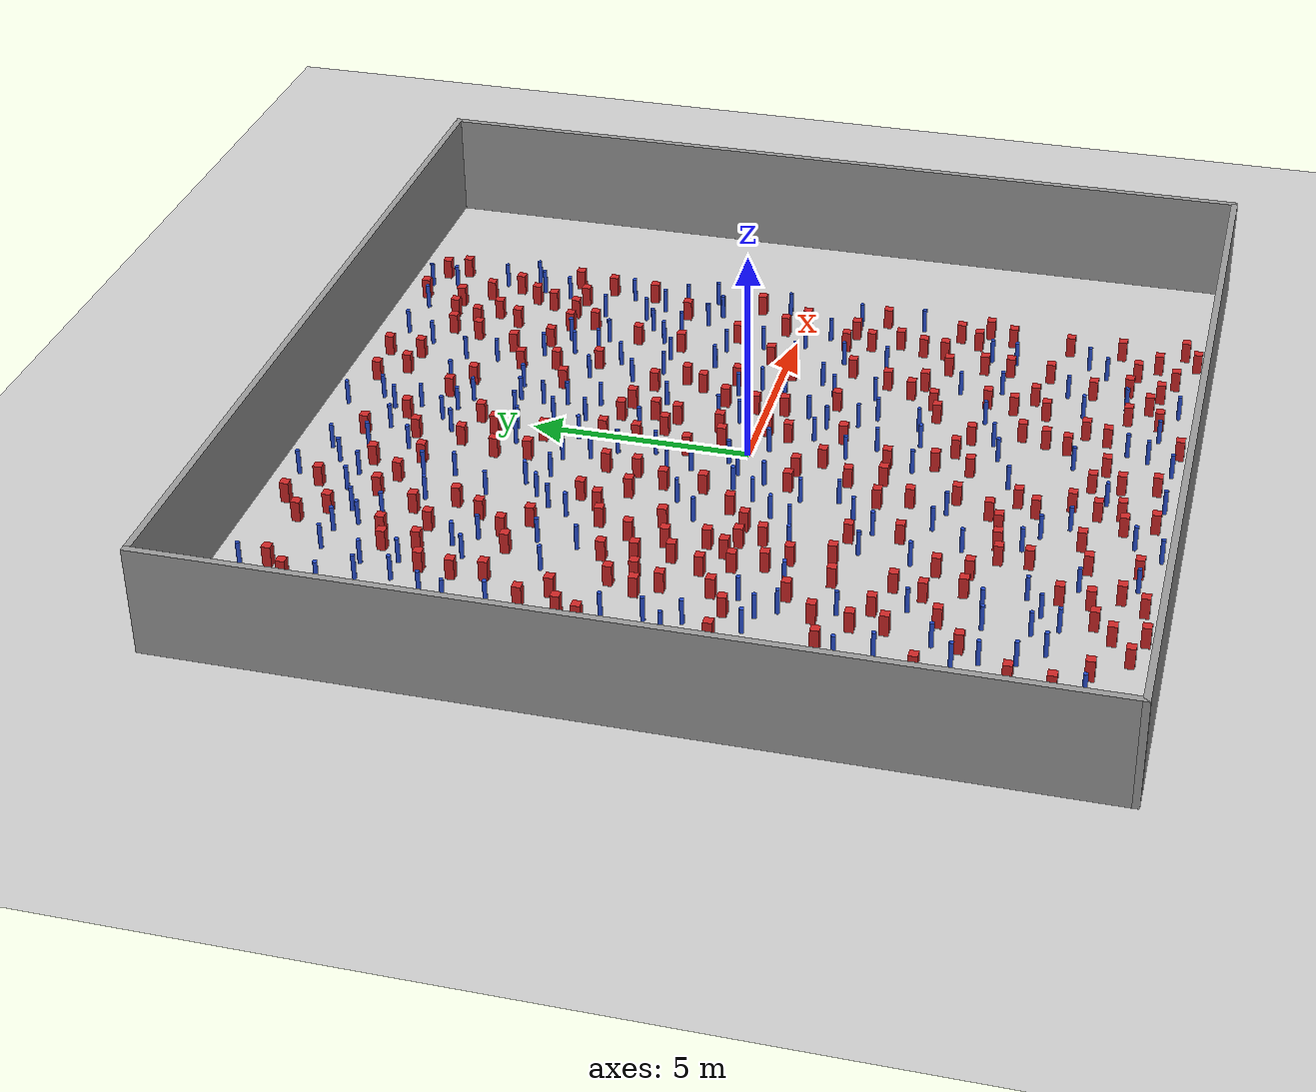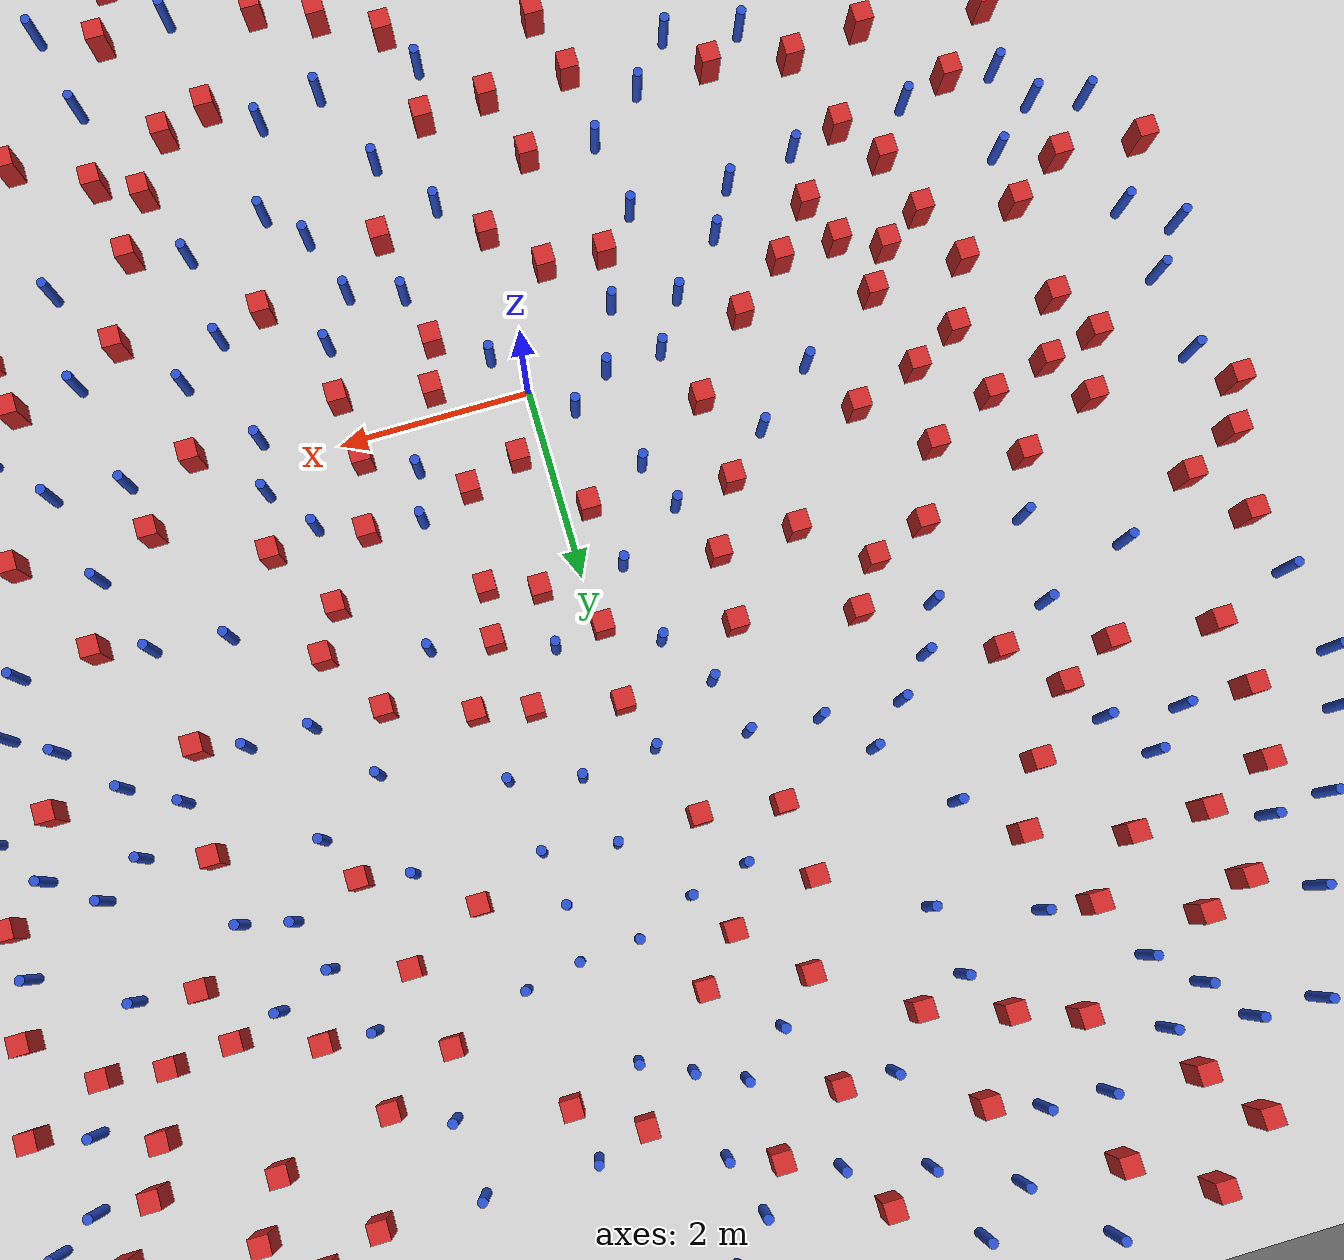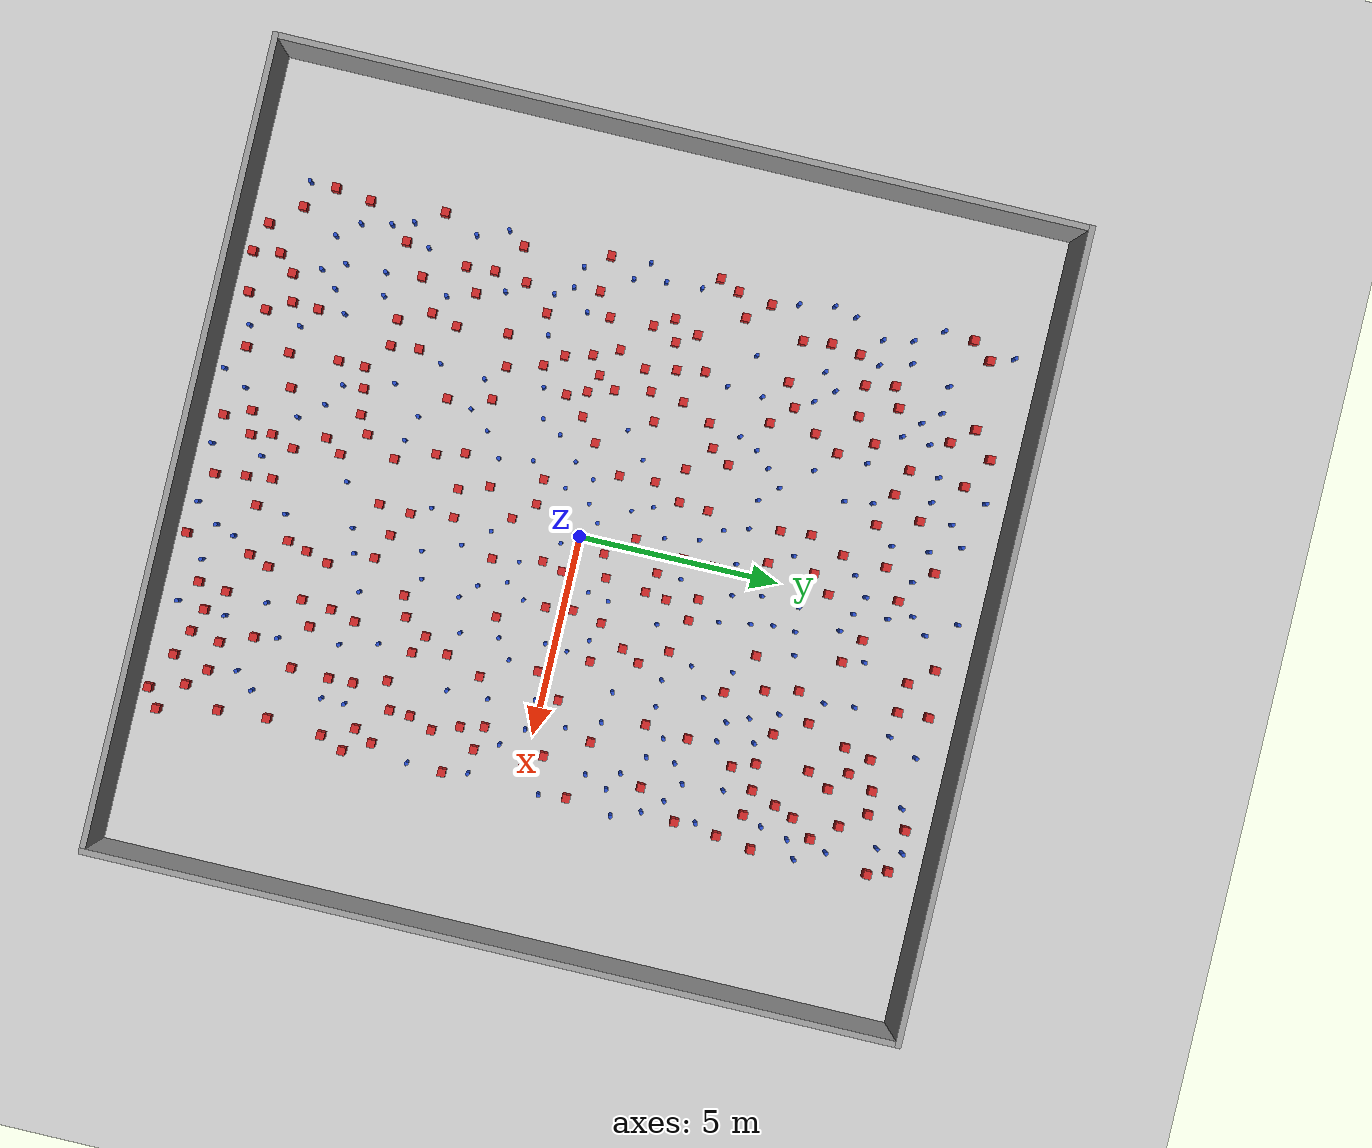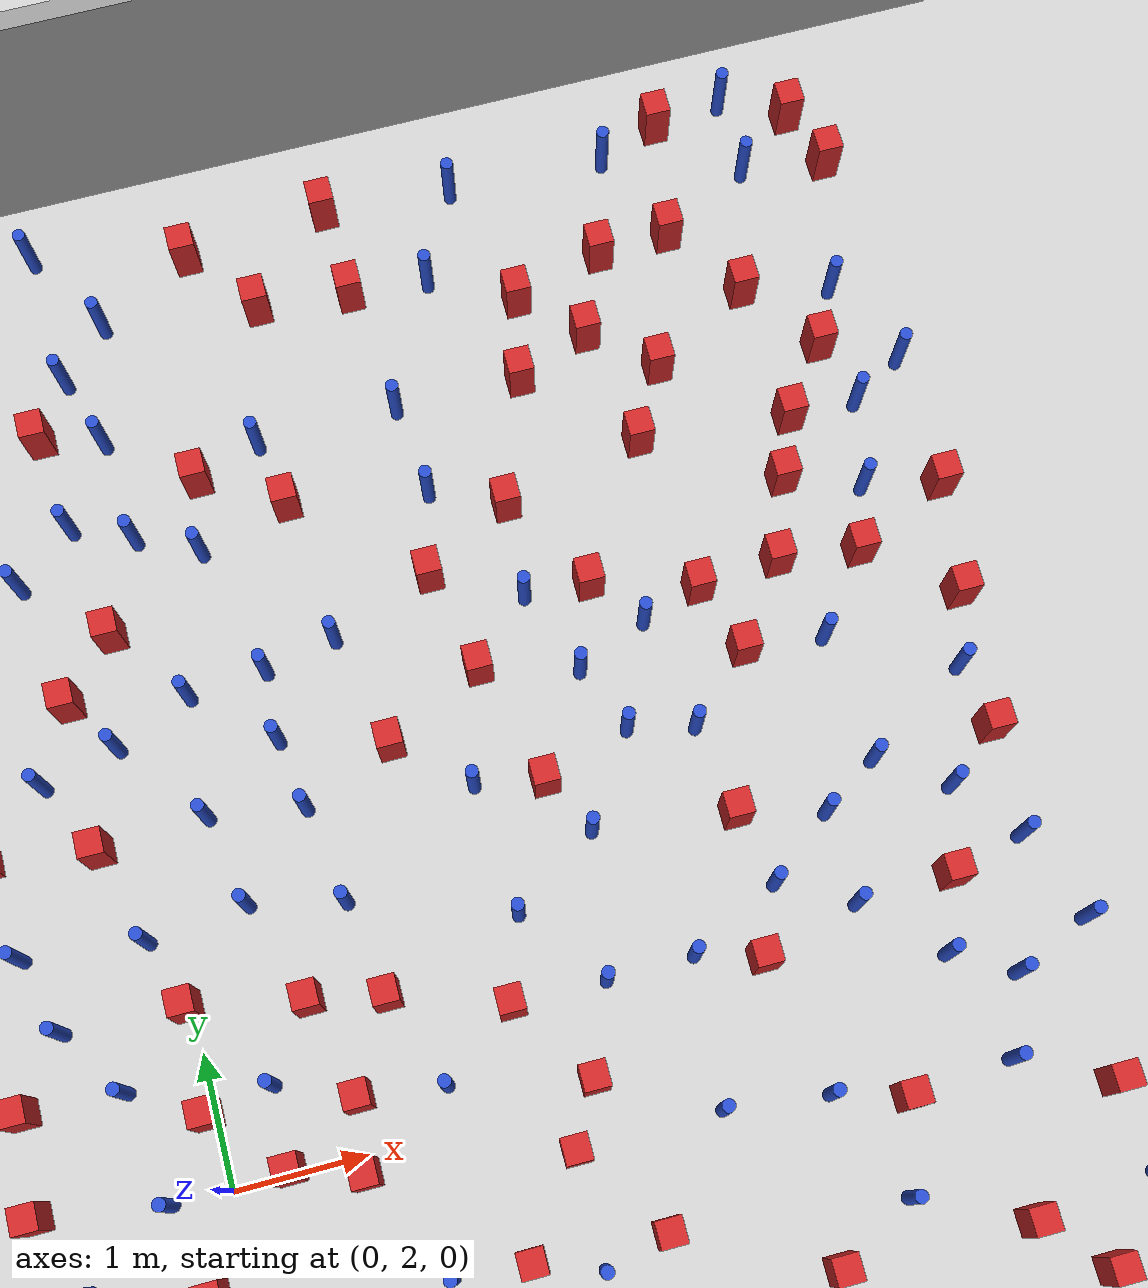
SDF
<sdf version="1.6">
 <world name="default">
  <light name="sun" type="directional">
   <pose>0 0 1000 0 -0 0</pose>
   <diffuse>0.8 0.8 0.8 1</diffuse>
   <specular>0.1 0.1 0.1 1</specular>
   <attenuation>
    <range>1000</range>
    <constant>0.9</constant>
    <linear>0.01</linear>
    <quadratic>0.001</quadratic>
   </attenuation>
   <direction>-0.5 0.5 -1</direction>
  </light>
  <model name="ground_plane">
   <static>1</static>
   <link name="link">
    <collision name="collision">
     <geometry><plane><normal>0 0 1</normal><size>100 100</size></plane></geometry>
     <surface><friction><ode><mu>100</mu><mu2>50</mu2></ode></friction></surface>
    </collision>
    <visual name="visual">
     <cast_shadows>0</cast_shadows>
     <geometry><plane><normal>0 0 1</normal><size>100 100</size></plane></geometry>
     <material>
      <ambient>1.0 1.0 1.0 1.0</ambient>
      <diffuse>0.8 0.8 0.8 1.0</diffuse>
      <specular>0.01 0.01 0.01 1.000000</specular>
     </material>
    </visual>
   </link>
  </model>
  <gravity>0 0 -9.8</gravity>
  <magnetic_field>6e-06 2.3e-05 -4.2e-05</magnetic_field>
  <atmosphere type="adiabatic"/>
  <physics name="default_physics" default="0" type="ode">
   <max_step_size>0.001</max_step_size>
   <real_time_factor>1</real_time_factor>
   <real_time_update_rate>1000</real_time_update_rate>
  </physics>
  <scene><ambient>0.4 0.4 0.4 1</ambient><background>0.7 0.7 0.7 1</background><shadows>1</shadows></scene>
  <spherical_coordinates>
   <surface_model>EARTH_WGS84</surface_model>
   <latitude_deg>0</latitude_deg>
   <longitude_deg>0</longitude_deg>
   <elevation>0</elevation>
   <heading_deg>0</heading_deg>
  </spherical_coordinates>
  <plugin name="gazebo_occupancy_map" filename="libgazebo_2Dmap_plugin.so">
   <map_resolution>0.05</map_resolution>
   <map_topic>generated_map</map_topic>
   <map_height>0.01</map_height>
   <map_size_x>50</map_size_x>
   <map_size_y>50</map_size_y>
  </plugin>
  <model name="NamedLocations">
   <static>true</static>
   <link name="DefaultStart"><pose>8.5 0 0 0 0 3.14</pose></link>
  </model>
  <model name="20x20_walls">
   <pose>0.044518 0.176112 0 0 -0 0</pose>
   <link name="Wall_1">
    <collision name="Wall_1_Collision">
     <geometry><box><size>20 0.15 2.5</size></box></geometry>
     <pose>0 0 1.25 0 -0 0</pose>
    </collision>
    <visual name="Wall_1_Visual">
     <pose>0 0 1.25 0 -0 0</pose>
     <geometry><box><size>20 0.15 2.5</size></box></geometry>
     <material>
      <script><uri>file://media/materials/scripts/gazebo.material</uri><name>Gazebo/Grey</name></script>
      <ambient>0.976471 0.992157 1 1</ambient>
     </material>
     <meta><layer>0</layer></meta>
    </visual>
    <pose>0 9.925 0 0 -0 0</pose>
   </link>
   <link name="Wall_3">
    <collision name="Wall_3_Collision">
     <geometry><box><size>20 0.15 2.5</size></box></geometry>
     <pose>0 0 1.25 0 -0 0</pose>
    </collision>
    <visual name="Wall_3_Visual">
     <pose>0 0 1.25 0 -0 0</pose>
     <geometry><box><size>20 0.15 2.5</size></box></geometry>
     <material>
      <script><uri>file://media/materials/scripts/gazebo.material</uri><name>Gazebo/Grey</name></script>
      <ambient>0.976471 0.992157 1 1</ambient>
     </material>
     <meta><layer>0</layer></meta>
    </visual>
    <pose>9.925 0 0 0 0 -1.5708</pose>
   </link>
   <link name="Wall_4">
    <collision name="Wall_4_Collision">
     <geometry><box><size>20 0.15 2.5</size></box></geometry>
     <pose>0 0 1.25 0 -0 0</pose>
    </collision>
    <visual name="Wall_4_Visual">
     <pose>0 0 1.25 0 -0 0</pose>
     <geometry><box><size>20 0.15 2.5</size></box></geometry>
     <material>
      <script><uri>file://media/materials/scripts/gazebo.material</uri><name>Gazebo/Grey</name></script>
      <ambient>0.976471 0.992157 1 1</ambient>
     </material>
     <meta><layer>0</layer></meta>
    </visual>
    <pose>0 -9.925 0 0 -0 3.14159</pose>
   </link>
   <link name="Wall_5">
    <collision name="Wall_5_Collision">
     <geometry><box><size>20 0.15 2.5</size></box></geometry>
     <pose>0 0 1.25 0 -0 0</pose>
    </collision>
    <visual name="Wall_5_Visual">
     <pose>0 0 1.25 0 -0 0</pose>
     <geometry><box><size>20 0.15 2.5</size></box></geometry>
     <material>
      <script><uri>file://media/materials/scripts/gazebo.material</uri><name>Gazebo/Grey</name></script>
      <ambient>0.976471 0.992157 1 1</ambient>
     </material>
     <meta><layer>0</layer></meta>
    </visual>
    <pose>-9.925 0 0 0 -0 1.5708</pose>
   </link>
   <static>1</static>
  </model>
  <model name="square_post_obstacle0">
   <static>true</static>
   <pose>-0.671733654428 -2.42488033884 1.91545236811e-07 -7.35059704564e-06 1.12565212e-07 2.39332434364e-05</pose>
   <link name="link">
    <pose>0 0 0.25 0 -0 0</pose>
    <inertial>
     <mass>100</mass>
     <inertia>
      <ixx>0.166667</ixx>
      <ixy>0</ixy>
      <ixz>0</ixz>
      <iyy>0.166667</iyy>
      <iyz>0</iyz>
      <izz>0.166667</izz>
     </inertia>
    </inertial>
    <collision name="collision"><geometry><box><size>.2 .2 .5</size></box></geometry></collision>
    <visual name="visual">
     <geometry><box><size>.2 .2 .5</size></box></geometry>
     <material>
      <script><name>Gazebo/Red</name><uri>file://media/materials/scripts/gazebo.material</uri></script>
     </material>
    </visual>
   </link>
  </model>
  <model name="square_post_obstacle1">
   <static>true</static>
   <pose>-2.1941598513 2.13643566716 1.91545236811e-07 -7.35059704564e-06 1.12565212e-07 2.39332434364e-05</pose>
   <link name="link">
    <pose>0 0 0.25 0 -0 0</pose>
    <inertial>
     <mass>100</mass>
     <inertia>
      <ixx>0.166667</ixx>
      <ixy>0</ixy>
      <ixz>0</ixz>
      <iyy>0.166667</iyy>
      <iyz>0</iyz>
      <izz>0.166667</izz>
     </inertia>
    </inertial>
    <collision name="collision"><geometry><box><size>.2 .2 .5</size></box></geometry></collision>
    <visual name="visual">
     <geometry><box><size>.2 .2 .5</size></box></geometry>
     <material>
      <script><name>Gazebo/Red</name><uri>file://media/materials/scripts/gazebo.material</uri></script>
     </material>
    </visual>
   </link>
  </model>
  <model name="pole_obstacle0">
   <static>true</static>
   <pose>5.32144718917 3.82602129919 7.38925637345e-09 -8.47170692798e-08 1.24976764937e-08 -1.74513093023e-07</pose>
   <link name="link">
    <pose>0 0 0.3 0 -0 0</pose>
    <inertial>
     <mass>1</mass>
     <inertia><ixx>0.145833</ixx><ixy>0</ixy><ixz>0</ixz><iyy>0.145833</iyy><iyz>0</iyz><izz>0.125</izz></inertia>
    </inertial>
    <collision name="collision">
     <geometry><cylinder><radius>0.05</radius><length>.6</length></cylinder></geometry>
    </collision>
    <visual name="visual">
     <geometry><cylinder><radius>0.05</radius><length>.6</length></cylinder></geometry>
     <material>
      <script><name>Gazebo/Blue</name><uri>file://media/materials/scripts/gazebo.material</uri></script>
     </material>
    </visual>
   </link>
  </model>
  <model name="square_post_obstacle2">
   <static>true</static>
   <pose>-5.12397124756 -2.05312310392 1.91545236811e-07 -7.35059704564e-06 1.12565212e-07 2.39332434364e-05</pose>
   <link name="link">
    <pose>0 0 0.25 0 -0 0</pose>
    <inertial>
     <mass>100</mass>
     <inertia>
      <ixx>0.166667</ixx>
      <ixy>0</ixy>
      <ixz>0</ixz>
      <iyy>0.166667</iyy>
      <iyz>0</iyz>
      <izz>0.166667</izz>
     </inertia>
    </inertial>
    <collision name="collision"><geometry><box><size>.2 .2 .5</size></box></geometry></collision>
    <visual name="visual">
     <geometry><box><size>.2 .2 .5</size></box></geometry>
     <material>
      <script><name>Gazebo/Red</name><uri>file://media/materials/scripts/gazebo.material</uri></script>
     </material>
    </visual>
   </link>
  </model>
  <model name="pole_obstacle1">
   <static>true</static>
   <pose>-5.75798451812 6.16089119048 7.38925637345e-09 -8.47170692796e-08 1.24976764786e-08 -1.74513093032e-07</pose>
   <link name="link">
    <pose>0 0 0.3 0 -0 0</pose>
    <inertial>
     <mass>1</mass>
     <inertia><ixx>0.145833</ixx><ixy>0</ixy><ixz>0</ixz><iyy>0.145833</iyy><iyz>0</iyz><izz>0.125</izz></inertia>
    </inertial>
    <collision name="collision">
     <geometry><cylinder><radius>0.05</radius><length>.6</length></cylinder></geometry>
    </collision>
    <visual name="visual">
     <geometry><cylinder><radius>0.05</radius><length>.6</length></cylinder></geometry>
     <material>
      <script><name>Gazebo/Blue</name><uri>file://media/materials/scripts/gazebo.material</uri></script>
     </material>
    </visual>
   </link>
  </model>
  <model name="square_post_obstacle3">
   <static>true</static>
   <pose>-1.26131699538 4.73881055058 1.91545236811e-07 -7.35059704564e-06 1.12565212e-07 2.39332434364e-05</pose>
   <link name="link">
    <pose>0 0 0.25 0 -0 0</pose>
    <inertial>
     <mass>100</mass>
     <inertia>
      <ixx>0.166667</ixx>
      <ixy>0</ixy>
      <ixz>0</ixz>
      <iyy>0.166667</iyy>
      <iyz>0</iyz>
      <izz>0.166667</izz>
     </inertia>
    </inertial>
    <collision name="collision"><geometry><box><size>.2 .2 .5</size></box></geometry></collision>
    <visual name="visual">
     <geometry><box><size>.2 .2 .5</size></box></geometry>
     <material>
      <script><name>Gazebo/Red</name><uri>file://media/materials/scripts/gazebo.material</uri></script>
     </material>
    </visual>
   </link>
  </model>
  <model name="pole_obstacle2">
   <static>true</static>
   <pose>-5.64459293224 7.93843499499 7.38925637345e-09 -8.47170692796e-08 1.24976764786e-08 -1.74513093032e-07</pose>
   <link name="link">
    <pose>0 0 0.3 0 -0 0</pose>
    <inertial>
     <mass>1</mass>
     <inertia><ixx>0.145833</ixx><ixy>0</ixy><ixz>0</ixz><iyy>0.145833</iyy><iyz>0</iyz><izz>0.125</izz></inertia>
    </inertial>
    <collision name="collision">
     <geometry><cylinder><radius>0.05</radius><length>.6</length></cylinder></geometry>
    </collision>
    <visual name="visual">
     <geometry><cylinder><radius>0.05</radius><length>.6</length></cylinder></geometry>
     <material>
      <script><name>Gazebo/Blue</name><uri>file://media/materials/scripts/gazebo.material</uri></script>
     </material>
    </visual>
   </link>
  </model>
  <model name="pole_obstacle3">
   <static>true</static>
   <pose>3.8869717696 -8.00408965055 7.38925637345e-09 -8.47170692795e-08 1.24976764645e-08 -1.74513093041e-07</pose>
   <link name="link">
    <pose>0 0 0.3 0 -0 0</pose>
    <inertial>
     <mass>1</mass>
     <inertia><ixx>0.145833</ixx><ixy>0</ixy><ixz>0</ixz><iyy>0.145833</iyy><iyz>0</iyz><izz>0.125</izz></inertia>
    </inertial>
    <collision name="collision">
     <geometry><cylinder><radius>0.05</radius><length>.6</length></cylinder></geometry>
    </collision>
    <visual name="visual">
     <geometry><cylinder><radius>0.05</radius><length>.6</length></cylinder></geometry>
     <material>
      <script><name>Gazebo/Blue</name><uri>file://media/materials/scripts/gazebo.material</uri></script>
     </material>
    </visual>
   </link>
  </model>
  <model name="square_post_obstacle4">
   <static>true</static>
   <pose>3.07919721968 -6.26653733006 1.91545236811e-07 -7.35059704564e-06 1.12565212e-07 2.39332434364e-05</pose>
   <link name="link">
    <pose>0 0 0.25 0 -0 0</pose>
    <inertial>
     <mass>100</mass>
     <inertia>
      <ixx>0.166667</ixx>
      <ixy>0</ixy>
      <ixz>0</ixz>
      <iyy>0.166667</iyy>
      <iyz>0</iyz>
      <izz>0.166667</izz>
     </inertia>
    </inertial>
    <collision name="collision"><geometry><box><size>.2 .2 .5</size></box></geometry></collision>
    <visual name="visual">
     <geometry><box><size>.2 .2 .5</size></box></geometry>
     <material>
      <script><name>Gazebo/Red</name><uri>file://media/materials/scripts/gazebo.material</uri></script>
     </material>
    </visual>
   </link>
  </model>
  <model name="square_post_obstacle5">
   <static>true</static>
   <pose>6.44324664143 -4.46390891324 1.91545236811e-07 -7.35059704564e-06 1.12565212e-07 2.39332434364e-05</pose>
   <link name="link">
    <pose>0 0 0.25 0 -0 0</pose>
    <inertial>
     <mass>100</mass>
     <inertia>
      <ixx>0.166667</ixx>
      <ixy>0</ixy>
      <ixz>0</ixz>
      <iyy>0.166667</iyy>
      <iyz>0</iyz>
      <izz>0.166667</izz>
     </inertia>
    </inertial>
    <collision name="collision"><geometry><box><size>.2 .2 .5</size></box></geometry></collision>
    <visual name="visual">
     <geometry><box><size>.2 .2 .5</size></box></geometry>
     <material>
      <script><name>Gazebo/Red</name><uri>file://media/materials/scripts/gazebo.material</uri></script>
     </material>
    </visual>
   </link>
  </model>
  <model name="square_post_obstacle6">
   <static>true</static>
   <pose>3.90744752582 -1.59957269851 1.91545236811e-07 -7.35059704564e-06 1.12565212e-07 2.39332434364e-05</pose>
   <link name="link">
    <pose>0 0 0.25 0 -0 0</pose>
    <inertial>
     <mass>100</mass>
     <inertia>
      <ixx>0.166667</ixx>
      <ixy>0</ixy>
      <ixz>0</ixz>
      <iyy>0.166667</iyy>
      <iyz>0</iyz>
      <izz>0.166667</izz>
     </inertia>
    </inertial>
    <collision name="collision"><geometry><box><size>.2 .2 .5</size></box></geometry></collision>
    <visual name="visual">
     <geometry><box><size>.2 .2 .5</size></box></geometry>
     <material>
      <script><name>Gazebo/Red</name><uri>file://media/materials/scripts/gazebo.material</uri></script>
     </material>
    </visual>
   </link>
  </model>
  <model name="pole_obstacle4">
   <static>true</static>
   <pose>-0.581186451945 2.85597149366 7.38925637345e-09 -8.47170692799e-08 1.2497676509e-08 -1.74513093016e-07</pose>
   <link name="link">
    <pose>0 0 0.3 0 -0 0</pose>
    <inertial>
     <mass>1</mass>
     <inertia><ixx>0.145833</ixx><ixy>0</ixy><ixz>0</ixz><iyy>0.145833</iyy><iyz>0</iyz><izz>0.125</izz></inertia>
    </inertial>
    <collision name="collision">
     <geometry><cylinder><radius>0.05</radius><length>.6</length></cylinder></geometry>
    </collision>
    <visual name="visual">
     <geometry><cylinder><radius>0.05</radius><length>.6</length></cylinder></geometry>
     <material>
      <script><name>Gazebo/Blue</name><uri>file://media/materials/scripts/gazebo.material</uri></script>
     </material>
    </visual>
   </link>
  </model>
  <model name="pole_obstacle5">
   <static>true</static>
   <pose>6.38069435776 0.460439469425 7.38925637345e-09 -8.47170692799e-08 1.24976765124e-08 -1.74513093015e-07</pose>
   <link name="link">
    <pose>0 0 0.3 0 -0 0</pose>
    <inertial>
     <mass>1</mass>
     <inertia><ixx>0.145833</ixx><ixy>0</ixy><ixz>0</ixz><iyy>0.145833</iyy><iyz>0</iyz><izz>0.125</izz></inertia>
    </inertial>
    <collision name="collision">
     <geometry><cylinder><radius>0.05</radius><length>.6</length></cylinder></geometry>
    </collision>
    <visual name="visual">
     <geometry><cylinder><radius>0.05</radius><length>.6</length></cylinder></geometry>
     <material>
      <script><name>Gazebo/Blue</name><uri>file://media/materials/scripts/gazebo.material</uri></script>
     </material>
    </visual>
   </link>
  </model>
  <model name="square_post_obstacle7">
   <static>true</static>
   <pose>-1.14959347835 -1.18398450333 1.91545236811e-07 -7.35059704564e-06 1.12565212e-07 2.39332434364e-05</pose>
   <link name="link">
    <pose>0 0 0.25 0 -0 0</pose>
    <inertial>
     <mass>100</mass>
     <inertia>
      <ixx>0.166667</ixx>
      <ixy>0</ixy>
      <ixz>0</ixz>
      <iyy>0.166667</iyy>
      <iyz>0</iyz>
      <izz>0.166667</izz>
     </inertia>
    </inertial>
    <collision name="collision"><geometry><box><size>.2 .2 .5</size></box></geometry></collision>
    <visual name="visual">
     <geometry><box><size>.2 .2 .5</size></box></geometry>
     <material>
      <script><name>Gazebo/Red</name><uri>file://media/materials/scripts/gazebo.material</uri></script>
     </material>
    </visual>
   </link>
  </model>
  <model name="square_post_obstacle8">
   <static>true</static>
   <pose>-3.62353919109 -2.70946755188 1.91545236811e-07 -7.35059704564e-06 1.12565212e-07 2.39332434364e-05</pose>
   <link name="link">
    <pose>0 0 0.25 0 -0 0</pose>
    <inertial>
     <mass>100</mass>
     <inertia>
      <ixx>0.166667</ixx>
      <ixy>0</ixy>
      <ixz>0</ixz>
      <iyy>0.166667</iyy>
      <iyz>0</iyz>
      <izz>0.166667</izz>
     </inertia>
    </inertial>
    <collision name="collision"><geometry><box><size>.2 .2 .5</size></box></geometry></collision>
    <visual name="visual">
     <geometry><box><size>.2 .2 .5</size></box></geometry>
     <material>
      <script><name>Gazebo/Red</name><uri>file://media/materials/scripts/gazebo.material</uri></script>
     </material>
    </visual>
   </link>
  </model>
  <model name="pole_obstacle6">
   <static>true</static>
   <pose>-0.142269460352 5.34725949788 7.38925637345e-09 -8.47170692799e-08 1.24976765043e-08 -1.74513093019e-07</pose>
   <link name="link">
    <pose>0 0 0.3 0 -0 0</pose>
    <inertial>
     <mass>1</mass>
     <inertia><ixx>0.145833</ixx><ixy>0</ixy><ixz>0</ixz><iyy>0.145833</iyy><iyz>0</iyz><izz>0.125</izz></inertia>
    </inertial>
    <collision name="collision">
     <geometry><cylinder><radius>0.05</radius><length>.6</length></cylinder></geometry>
    </collision>
    <visual name="visual">
     <geometry><cylinder><radius>0.05</radius><length>.6</length></cylinder></geometry>
     <material>
      <script><name>Gazebo/Blue</name><uri>file://media/materials/scripts/gazebo.material</uri></script>
     </material>
    </visual>
   </link>
  </model>
  <model name="pole_obstacle7">
   <static>true</static>
   <pose>2.8126677085 0.329689469374 7.38925637345e-09 -8.471706928e-08 1.24976765172e-08 -1.74513093013e-07</pose>
   <link name="link">
    <pose>0 0 0.3 0 -0 0</pose>
    <inertial>
     <mass>1</mass>
     <inertia><ixx>0.145833</ixx><ixy>0</ixy><ixz>0</ixz><iyy>0.145833</iyy><iyz>0</iyz><izz>0.125</izz></inertia>
    </inertial>
    <collision name="collision">
     <geometry><cylinder><radius>0.05</radius><length>.6</length></cylinder></geometry>
    </collision>
    <visual name="visual">
     <geometry><cylinder><radius>0.05</radius><length>.6</length></cylinder></geometry>
     <material>
      <script><name>Gazebo/Blue</name><uri>file://media/materials/scripts/gazebo.material</uri></script>
     </material>
    </visual>
   </link>
  </model>
  <model name="square_post_obstacle9">
   <static>true</static>
   <pose>-3.77084339241 5.02417634701 1.91545236811e-07 -7.35059704564e-06 1.12565212e-07 2.39332434364e-05</pose>
   <link name="link">
    <pose>0 0 0.25 0 -0 0</pose>
    <inertial>
     <mass>100</mass>
     <inertia>
      <ixx>0.166667</ixx>
      <ixy>0</ixy>
      <ixz>0</ixz>
      <iyy>0.166667</iyy>
      <iyz>0</iyz>
      <izz>0.166667</izz>
     </inertia>
    </inertial>
    <collision name="collision"><geometry><box><size>.2 .2 .5</size></box></geometry></collision>
    <visual name="visual">
     <geometry><box><size>.2 .2 .5</size></box></geometry>
     <material>
      <script><name>Gazebo/Red</name><uri>file://media/materials/scripts/gazebo.material</uri></script>
     </material>
    </visual>
   </link>
  </model>
  <model name="square_post_obstacle10">
   <static>true</static>
   <pose>2.29358282562 -7.76249303104 1.91545236811e-07 -7.35059704564e-06 1.12565212e-07 2.39332434364e-05</pose>
   <link name="link">
    <pose>0 0 0.25 0 -0 0</pose>
    <inertial>
     <mass>100</mass>
     <inertia>
      <ixx>0.166667</ixx>
      <ixy>0</ixy>
      <ixz>0</ixz>
      <iyy>0.166667</iyy>
      <iyz>0</iyz>
      <izz>0.166667</izz>
     </inertia>
    </inertial>
    <collision name="collision"><geometry><box><size>.2 .2 .5</size></box></geometry></collision>
    <visual name="visual">
     <geometry><box><size>.2 .2 .5</size></box></geometry>
     <material>
      <script><name>Gazebo/Red</name><uri>file://media/materials/scripts/gazebo.material</uri></script>
     </material>
    </visual>
   </link>
  </model>
  <model name="square_post_obstacle11">
   <static>true</static>
   <pose>-0.571022109783 -8.41321369358 1.91545236811e-07 -7.35059704564e-06 1.12565212e-07 2.39332434364e-05</pose>
   <link name="link">
    <pose>0 0 0.25 0 -0 0</pose>
    <inertial>
     <mass>100</mass>
     <inertia>
      <ixx>0.166667</ixx>
      <ixy>0</ixy>
      <ixz>0</ixz>
      <iyy>0.166667</iyy>
      <iyz>0</iyz>
      <izz>0.166667</izz>
     </inertia>
    </inertial>
    <collision name="collision"><geometry><box><size>.2 .2 .5</size></box></geometry></collision>
    <visual name="visual">
     <geometry><box><size>.2 .2 .5</size></box></geometry>
     <material>
      <script><name>Gazebo/Red</name><uri>file://media/materials/scripts/gazebo.material</uri></script>
     </material>
    </visual>
   </link>
  </model>
  <model name="square_post_obstacle12">
   <static>true</static>
   <pose>-0.468949970906 -7.32807903634 1.91545236811e-07 -7.35059704564e-06 1.12565212e-07 2.39332434364e-05</pose>
   <link name="link">
    <pose>0 0 0.25 0 -0 0</pose>
    <inertial>
     <mass>100</mass>
     <inertia>
      <ixx>0.166667</ixx>
      <ixy>0</ixy>
      <ixz>0</ixz>
      <iyy>0.166667</iyy>
      <iyz>0</iyz>
      <izz>0.166667</izz>
     </inertia>
    </inertial>
    <collision name="collision"><geometry><box><size>.2 .2 .5</size></box></geometry></collision>
    <visual name="visual">
     <geometry><box><size>.2 .2 .5</size></box></geometry>
     <material>
      <script><name>Gazebo/Red</name><uri>file://media/materials/scripts/gazebo.material</uri></script>
     </material>
    </visual>
   </link>
  </model>
  <model name="square_post_obstacle13">
   <static>true</static>
   <pose>6.10127495856 -3.80343116019 1.91545236811e-07 -7.35059704564e-06 1.12565212e-07 2.39332434364e-05</pose>
   <link name="link">
    <pose>0 0 0.25 0 -0 0</pose>
    <inertial>
     <mass>100</mass>
     <inertia>
      <ixx>0.166667</ixx>
      <ixy>0</ixy>
      <ixz>0</ixz>
      <iyy>0.166667</iyy>
      <iyz>0</iyz>
      <izz>0.166667</izz>
     </inertia>
    </inertial>
    <collision name="collision"><geometry><box><size>.2 .2 .5</size></box></geometry></collision>
    <visual name="visual">
     <geometry><box><size>.2 .2 .5</size></box></geometry>
     <material>
      <script><name>Gazebo/Red</name><uri>file://media/materials/scripts/gazebo.material</uri></script>
     </material>
    </visual>
   </link>
  </model>
  <model name="pole_obstacle8">
   <static>true</static>
   <pose>-2.16732002486 1.0621560365 7.38925637345e-09 -8.471706928e-08 1.24976765152e-08 -1.74513093012e-07</pose>
   <link name="link">
    <pose>0 0 0.3 0 -0 0</pose>
    <inertial>
     <mass>1</mass>
     <inertia><ixx>0.145833</ixx><ixy>0</ixy><ixz>0</ixz><iyy>0.145833</iyy><iyz>0</iyz><izz>0.125</izz></inertia>
    </inertial>
    <collision name="collision">
     <geometry><cylinder><radius>0.05</radius><length>.6</length></cylinder></geometry>
    </collision>
    <visual name="visual">
     <geometry><cylinder><radius>0.05</radius><length>.6</length></cylinder></geometry>
     <material>
      <script><name>Gazebo/Blue</name><uri>file://media/materials/scripts/gazebo.material</uri></script>
     </material>
    </visual>
   </link>
  </model>
  <model name="square_post_obstacle14">
   <static>true</static>
   <pose>1.80562686687 0.251162258014 1.91545236811e-07 -7.35059704564e-06 1.12565212e-07 2.39332434364e-05</pose>
   <link name="link">
    <pose>0 0 0.25 0 -0 0</pose>
    <inertial>
     <mass>100</mass>
     <inertia>
      <ixx>0.166667</ixx>
      <ixy>0</ixy>
      <ixz>0</ixz>
      <iyy>0.166667</iyy>
      <iyz>0</iyz>
      <izz>0.166667</izz>
     </inertia>
    </inertial>
    <collision name="collision"><geometry><box><size>.2 .2 .5</size></box></geometry></collision>
    <visual name="visual">
     <geometry><box><size>.2 .2 .5</size></box></geometry>
     <material>
      <script><name>Gazebo/Red</name><uri>file://media/materials/scripts/gazebo.material</uri></script>
     </material>
    </visual>
   </link>
  </model>
  <model name="square_post_obstacle15">
   <static>true</static>
   <pose>4.13115167397 7.73196984689 1.91545236811e-07 -7.35059704564e-06 1.12565212e-07 2.39332434364e-05</pose>
   <link name="link">
    <pose>0 0 0.25 0 -0 0</pose>
    <inertial>
     <mass>100</mass>
     <inertia>
      <ixx>0.166667</ixx>
      <ixy>0</ixy>
      <ixz>0</ixz>
      <iyy>0.166667</iyy>
      <iyz>0</iyz>
      <izz>0.166667</izz>
     </inertia>
    </inertial>
    <collision name="collision"><geometry><box><size>.2 .2 .5</size></box></geometry></collision>
    <visual name="visual">
     <geometry><box><size>.2 .2 .5</size></box></geometry>
     <material>
      <script><name>Gazebo/Red</name><uri>file://media/materials/scripts/gazebo.material</uri></script>
     </material>
    </visual>
   </link>
  </model>
  <model name="square_post_obstacle16">
   <static>true</static>
   <pose>3.53115451772 7.49610520008 1.91545236811e-07 -7.35059704564e-06 1.12565212e-07 2.39332434364e-05</pose>
   <link name="link">
    <pose>0 0 0.25 0 -0 0</pose>
    <inertial>
     <mass>100</mass>
     <inertia>
      <ixx>0.166667</ixx>
      <ixy>0</ixy>
      <ixz>0</ixz>
      <iyy>0.166667</iyy>
      <iyz>0</iyz>
      <izz>0.166667</izz>
     </inertia>
    </inertial>
    <collision name="collision"><geometry><box><size>.2 .2 .5</size></box></geometry></collision>
    <visual name="visual">
     <geometry><box><size>.2 .2 .5</size></box></geometry>
     <material>
      <script><name>Gazebo/Red</name><uri>file://media/materials/scripts/gazebo.material</uri></script>
     </material>
    </visual>
   </link>
  </model>
  <model name="pole_obstacle9">
   <static>true</static>
   <pose>-2.88459928265 5.19399975139 7.38925637345e-09 -8.47170692798e-08 1.24976765033e-08 -1.74513093019e-07</pose>
   <link name="link">
    <pose>0 0 0.3 0 -0 0</pose>
    <inertial>
     <mass>1</mass>
     <inertia><ixx>0.145833</ixx><ixy>0</ixy><ixz>0</ixz><iyy>0.145833</iyy><iyz>0</iyz><izz>0.125</izz></inertia>
    </inertial>
    <collision name="collision">
     <geometry><cylinder><radius>0.05</radius><length>.6</length></cylinder></geometry>
    </collision>
    <visual name="visual">
     <geometry><cylinder><radius>0.05</radius><length>.6</length></cylinder></geometry>
     <material>
      <script><name>Gazebo/Blue</name><uri>file://media/materials/scripts/gazebo.material</uri></script>
     </material>
    </visual>
   </link>
  </model>
  <model name="square_post_obstacle17">
   <static>true</static>
   <pose>6.01711211781 -9.42610110597 1.91545236811e-07 -7.35059704564e-06 1.12565212e-07 2.39332434364e-05</pose>
   <link name="link">
    <pose>0 0 0.25 0 -0 0</pose>
    <inertial>
     <mass>100</mass>
     <inertia>
      <ixx>0.166667</ixx>
      <ixy>0</ixy>
      <ixz>0</ixz>
      <iyy>0.166667</iyy>
      <iyz>0</iyz>
      <izz>0.166667</izz>
     </inertia>
    </inertial>
    <collision name="collision"><geometry><box><size>.2 .2 .5</size></box></geometry></collision>
    <visual name="visual">
     <geometry><box><size>.2 .2 .5</size></box></geometry>
     <material>
      <script><name>Gazebo/Red</name><uri>file://media/materials/scripts/gazebo.material</uri></script>
     </material>
    </visual>
   </link>
  </model>
  <model name="square_post_obstacle18">
   <static>true</static>
   <pose>-5.907547881 5.64567180726 1.91545236811e-07 -7.35059704564e-06 1.12565212e-07 2.39332434364e-05</pose>
   <link name="link">
    <pose>0 0 0.25 0 -0 0</pose>
    <inertial>
     <mass>100</mass>
     <inertia>
      <ixx>0.166667</ixx>
      <ixy>0</ixy>
      <ixz>0</ixz>
      <iyy>0.166667</iyy>
      <iyz>0</iyz>
      <izz>0.166667</izz>
     </inertia>
    </inertial>
    <collision name="collision"><geometry><box><size>.2 .2 .5</size></box></geometry></collision>
    <visual name="visual">
     <geometry><box><size>.2 .2 .5</size></box></geometry>
     <material>
      <script><name>Gazebo/Red</name><uri>file://media/materials/scripts/gazebo.material</uri></script>
     </material>
    </visual>
   </link>
  </model>
  <model name="pole_obstacle10">
   <static>true</static>
   <pose>-6.93408362777 7.51889811465 7.38925637345e-09 -8.47170692796e-08 1.24976764786e-08 -1.74513093032e-07</pose>
   <link name="link">
    <pose>0 0 0.3 0 -0 0</pose>
    <inertial>
     <mass>1</mass>
     <inertia><ixx>0.145833</ixx><ixy>0</ixy><ixz>0</ixz><iyy>0.145833</iyy><iyz>0</iyz><izz>0.125</izz></inertia>
    </inertial>
    <collision name="collision">
     <geometry><cylinder><radius>0.05</radius><length>.6</length></cylinder></geometry>
    </collision>
    <visual name="visual">
     <geometry><cylinder><radius>0.05</radius><length>.6</length></cylinder></geometry>
     <material>
      <script><name>Gazebo/Blue</name><uri>file://media/materials/scripts/gazebo.material</uri></script>
     </material>
    </visual>
   </link>
  </model>
  <model name="square_post_obstacle19">
   <static>true</static>
   <pose>-1.37294681692 2.16979224716 1.91545236811e-07 -7.35059704564e-06 1.12565212e-07 2.39332434364e-05</pose>
   <link name="link">
    <pose>0 0 0.25 0 -0 0</pose>
    <inertial>
     <mass>100</mass>
     <inertia>
      <ixx>0.166667</ixx>
      <ixy>0</ixy>
      <ixz>0</ixz>
      <iyy>0.166667</iyy>
      <iyz>0</iyz>
      <izz>0.166667</izz>
     </inertia>
    </inertial>
    <collision name="collision"><geometry><box><size>.2 .2 .5</size></box></geometry></collision>
    <visual name="visual">
     <geometry><box><size>.2 .2 .5</size></box></geometry>
     <material>
      <script><name>Gazebo/Red</name><uri>file://media/materials/scripts/gazebo.material</uri></script>
     </material>
    </visual>
   </link>
  </model>
  <model name="pole_obstacle11">
   <static>true</static>
   <pose>-3.35549708383 6.42012457529 7.38925637345e-09 -8.47170692794e-08 1.24976764468e-08 -1.7451309304e-07</pose>
   <link name="link">
    <pose>0 0 0.3 0 -0 0</pose>
    <inertial>
     <mass>1</mass>
     <inertia><ixx>0.145833</ixx><ixy>0</ixy><ixz>0</ixz><iyy>0.145833</iyy><iyz>0</iyz><izz>0.125</izz></inertia>
    </inertial>
    <collision name="collision">
     <geometry><cylinder><radius>0.05</radius><length>.6</length></cylinder></geometry>
    </collision>
    <visual name="visual">
     <geometry><cylinder><radius>0.05</radius><length>.6</length></cylinder></geometry>
     <material>
      <script><name>Gazebo/Blue</name><uri>file://media/materials/scripts/gazebo.material</uri></script>
     </material>
    </visual>
   </link>
  </model>
  <model name="square_post_obstacle20">
   <static>true</static>
   <pose>-5.15516237254 1.18091406253 1.91545236811e-07 -7.35059704564e-06 1.12565212e-07 2.39332434364e-05</pose>
   <link name="link">
    <pose>0 0 0.25 0 -0 0</pose>
    <inertial>
     <mass>100</mass>
     <inertia>
      <ixx>0.166667</ixx>
      <ixy>0</ixy>
      <ixz>0</ixz>
      <iyy>0.166667</iyy>
      <iyz>0</iyz>
      <izz>0.166667</izz>
     </inertia>
    </inertial>
    <collision name="collision"><geometry><box><size>.2 .2 .5</size></box></geometry></collision>
    <visual name="visual">
     <geometry><box><size>.2 .2 .5</size></box></geometry>
     <material>
      <script><name>Gazebo/Red</name><uri>file://media/materials/scripts/gazebo.material</uri></script>
     </material>
    </visual>
   </link>
  </model>
  <model name="pole_obstacle12">
   <static>true</static>
   <pose>-6.42299217875 -0.172170446409 7.38925637345e-09 -8.471706928e-08 1.24976765188e-08 -1.74513093011e-07</pose>
   <link name="link">
    <pose>0 0 0.3 0 -0 0</pose>
    <inertial>
     <mass>1</mass>
     <inertia><ixx>0.145833</ixx><ixy>0</ixy><ixz>0</ixz><iyy>0.145833</iyy><iyz>0</iyz><izz>0.125</izz></inertia>
    </inertial>
    <collision name="collision">
     <geometry><cylinder><radius>0.05</radius><length>.6</length></cylinder></geometry>
    </collision>
    <visual name="visual">
     <geometry><cylinder><radius>0.05</radius><length>.6</length></cylinder></geometry>
     <material>
      <script><name>Gazebo/Blue</name><uri>file://media/materials/scripts/gazebo.material</uri></script>
     </material>
    </visual>
   </link>
  </model>
  <model name="square_post_obstacle21">
   <static>true</static>
   <pose>0.802221249417 -0.748672035375 1.91545236811e-07 -7.35059704564e-06 1.12565212e-07 2.39332434364e-05</pose>
   <link name="link">
    <pose>0 0 0.25 0 -0 0</pose>
    <inertial>
     <mass>100</mass>
     <inertia>
      <ixx>0.166667</ixx>
      <ixy>0</ixy>
      <ixz>0</ixz>
      <iyy>0.166667</iyy>
      <iyz>0</iyz>
      <izz>0.166667</izz>
     </inertia>
    </inertial>
    <collision name="collision"><geometry><box><size>.2 .2 .5</size></box></geometry></collision>
    <visual name="visual">
     <geometry><box><size>.2 .2 .5</size></box></geometry>
     <material>
      <script><name>Gazebo/Red</name><uri>file://media/materials/scripts/gazebo.material</uri></script>
     </material>
    </visual>
   </link>
  </model>
  <model name="pole_obstacle13">
   <static>true</static>
   <pose>-1.06651826613 -0.618650534359 7.38925637345e-09 -8.47170692799e-08 1.24976765075e-08 -1.74513093017e-07</pose>
   <link name="link">
    <pose>0 0 0.3 0 -0 0</pose>
    <inertial>
     <mass>1</mass>
     <inertia><ixx>0.145833</ixx><ixy>0</ixy><ixz>0</ixz><iyy>0.145833</iyy><iyz>0</iyz><izz>0.125</izz></inertia>
    </inertial>
    <collision name="collision">
     <geometry><cylinder><radius>0.05</radius><length>.6</length></cylinder></geometry>
    </collision>
    <visual name="visual">
     <geometry><cylinder><radius>0.05</radius><length>.6</length></cylinder></geometry>
     <material>
      <script><name>Gazebo/Blue</name><uri>file://media/materials/scripts/gazebo.material</uri></script>
     </material>
    </visual>
   </link>
  </model>
  <model name="square_post_obstacle22">
   <static>true</static>
   <pose>4.79873285361 -5.18965610386 1.91545236811e-07 -7.35059704564e-06 1.12565212e-07 2.39332434364e-05</pose>
   <link name="link">
    <pose>0 0 0.25 0 -0 0</pose>
    <inertial>
     <mass>100</mass>
     <inertia>
      <ixx>0.166667</ixx>
      <ixy>0</ixy>
      <ixz>0</ixz>
      <iyy>0.166667</iyy>
      <iyz>0</iyz>
      <izz>0.166667</izz>
     </inertia>
    </inertial>
    <collision name="collision"><geometry><box><size>.2 .2 .5</size></box></geometry></collision>
    <visual name="visual">
     <geometry><box><size>.2 .2 .5</size></box></geometry>
     <material>
      <script><name>Gazebo/Red</name><uri>file://media/materials/scripts/gazebo.material</uri></script>
     </material>
    </visual>
   </link>
  </model>
  <model name="pole_obstacle14">
   <static>true</static>
   <pose>6.1434675484 7.62217938228 7.38925637345e-09 -8.47170692796e-08 1.24976764786e-08 -1.74513093032e-07</pose>
   <link name="link">
    <pose>0 0 0.3 0 -0 0</pose>
    <inertial>
     <mass>1</mass>
     <inertia><ixx>0.145833</ixx><ixy>0</ixy><ixz>0</ixz><iyy>0.145833</iyy><iyz>0</iyz><izz>0.125</izz></inertia>
    </inertial>
    <collision name="collision">
     <geometry><cylinder><radius>0.05</radius><length>.6</length></cylinder></geometry>
    </collision>
    <visual name="visual">
     <geometry><cylinder><radius>0.05</radius><length>.6</length></cylinder></geometry>
     <material>
      <script><name>Gazebo/Blue</name><uri>file://media/materials/scripts/gazebo.material</uri></script>
     </material>
    </visual>
   </link>
  </model>
  <model name="pole_obstacle15">
   <static>true</static>
   <pose>1.24080618713 -3.68273115442 7.38925637345e-09 -8.47170692799e-08 1.24976765053e-08 -1.74513093017e-07</pose>
   <link name="link">
    <pose>0 0 0.3 0 -0 0</pose>
    <inertial>
     <mass>1</mass>
     <inertia><ixx>0.145833</ixx><ixy>0</ixy><ixz>0</ixz><iyy>0.145833</iyy><iyz>0</iyz><izz>0.125</izz></inertia>
    </inertial>
    <collision name="collision">
     <geometry><cylinder><radius>0.05</radius><length>.6</length></cylinder></geometry>
    </collision>
    <visual name="visual">
     <geometry><cylinder><radius>0.05</radius><length>.6</length></cylinder></geometry>
     <material>
      <script><name>Gazebo/Blue</name><uri>file://media/materials/scripts/gazebo.material</uri></script>
     </material>
    </visual>
   </link>
  </model>
  <model name="pole_obstacle16">
   <static>true</static>
   <pose>-4.60244024358 -1.88865574683 7.38925637345e-09 -8.471706928e-08 1.24976765134e-08 -1.74513093015e-07</pose>
   <link name="link">
    <pose>0 0 0.3 0 -0 0</pose>
    <inertial>
     <mass>1</mass>
     <inertia><ixx>0.145833</ixx><ixy>0</ixy><ixz>0</ixz><iyy>0.145833</iyy><iyz>0</iyz><izz>0.125</izz></inertia>
    </inertial>
    <collision name="collision">
     <geometry><cylinder><radius>0.05</radius><length>.6</length></cylinder></geometry>
    </collision>
    <visual name="visual">
     <geometry><cylinder><radius>0.05</radius><length>.6</length></cylinder></geometry>
     <material>
      <script><name>Gazebo/Blue</name><uri>file://media/materials/scripts/gazebo.material</uri></script>
     </material>
    </visual>
   </link>
  </model>
  <model name="square_post_obstacle23">
   <static>true</static>
   <pose>-4.39261713382 -0.714989446906 1.91545236811e-07 -7.35059704564e-06 1.12565212e-07 2.39332434364e-05</pose>
   <link name="link">
    <pose>0 0 0.25 0 -0 0</pose>
    <inertial>
     <mass>100</mass>
     <inertia>
      <ixx>0.166667</ixx>
      <ixy>0</ixy>
      <ixz>0</ixz>
      <iyy>0.166667</iyy>
      <iyz>0</iyz>
      <izz>0.166667</izz>
     </inertia>
    </inertial>
    <collision name="collision"><geometry><box><size>.2 .2 .5</size></box></geometry></collision>
    <visual name="visual">
     <geometry><box><size>.2 .2 .5</size></box></geometry>
     <material>
      <script><name>Gazebo/Red</name><uri>file://media/materials/scripts/gazebo.material</uri></script>
     </material>
    </visual>
   </link>
  </model>
  <model name="pole_obstacle17">
   <static>true</static>
   <pose>-2.78437330864 8.17089390796 7.38925637345e-09 -8.47170692793e-08 1.24976764408e-08 -1.74513093041e-07</pose>
   <link name="link">
    <pose>0 0 0.3 0 -0 0</pose>
    <inertial>
     <mass>1</mass>
     <inertia><ixx>0.145833</ixx><ixy>0</ixy><ixz>0</ixz><iyy>0.145833</iyy><iyz>0</iyz><izz>0.125</izz></inertia>
    </inertial>
    <collision name="collision">
     <geometry><cylinder><radius>0.05</radius><length>.6</length></cylinder></geometry>
    </collision>
    <visual name="visual">
     <geometry><cylinder><radius>0.05</radius><length>.6</length></cylinder></geometry>
     <material>
      <script><name>Gazebo/Blue</name><uri>file://media/materials/scripts/gazebo.material</uri></script>
     </material>
    </visual>
   </link>
  </model>
  <model name="square_post_obstacle24">
   <static>true</static>
   <pose>4.30257774351 6.76059418714 1.91545236811e-07 -7.35059704564e-06 1.12565212e-07 2.39332434364e-05</pose>
   <link name="link">
    <pose>0 0 0.25 0 -0 0</pose>
    <inertial>
     <mass>100</mass>
     <inertia>
      <ixx>0.166667</ixx>
      <ixy>0</ixy>
      <ixz>0</ixz>
      <iyy>0.166667</iyy>
      <iyz>0</iyz>
      <izz>0.166667</izz>
     </inertia>
    </inertial>
    <collision name="collision"><geometry><box><size>.2 .2 .5</size></box></geometry></collision>
    <visual name="visual">
     <geometry><box><size>.2 .2 .5</size></box></geometry>
     <material>
      <script><name>Gazebo/Red</name><uri>file://media/materials/scripts/gazebo.material</uri></script>
     </material>
    </visual>
   </link>
  </model>
  <model name="square_post_obstacle25">
   <static>true</static>
   <pose>-1.22432231894 -5.6341398874 1.91545236811e-07 -7.35059704564e-06 1.12565212e-07 2.39332434364e-05</pose>
   <link name="link">
    <pose>0 0 0.25 0 -0 0</pose>
    <inertial>
     <mass>100</mass>
     <inertia>
      <ixx>0.166667</ixx>
      <ixy>0</ixy>
      <ixz>0</ixz>
      <iyy>0.166667</iyy>
      <iyz>0</iyz>
      <izz>0.166667</izz>
     </inertia>
    </inertial>
    <collision name="collision"><geometry><box><size>.2 .2 .5</size></box></geometry></collision>
    <visual name="visual">
     <geometry><box><size>.2 .2 .5</size></box></geometry>
     <material>
      <script><name>Gazebo/Red</name><uri>file://media/materials/scripts/gazebo.material</uri></script>
     </material>
    </visual>
   </link>
  </model>
  <model name="square_post_obstacle26">
   <static>true</static>
   <pose>-4.62506961678 2.05364620012 1.91545236811e-07 -7.35059704564e-06 1.12565212e-07 2.39332434364e-05</pose>
   <link name="link">
    <pose>0 0 0.25 0 -0 0</pose>
    <inertial>
     <mass>100</mass>
     <inertia>
      <ixx>0.166667</ixx>
      <ixy>0</ixy>
      <ixz>0</ixz>
      <iyy>0.166667</iyy>
      <iyz>0</iyz>
      <izz>0.166667</izz>
     </inertia>
    </inertial>
    <collision name="collision"><geometry><box><size>.2 .2 .5</size></box></geometry></collision>
    <visual name="visual">
     <geometry><box><size>.2 .2 .5</size></box></geometry>
     <material>
      <script><name>Gazebo/Red</name><uri>file://media/materials/scripts/gazebo.material</uri></script>
     </material>
    </visual>
   </link>
  </model>
  <model name="square_post_obstacle27">
   <static>true</static>
   <pose>4.55266092391 -7.9938036275 1.91545236811e-07 -7.35059704564e-06 1.12565212e-07 2.39332434364e-05</pose>
   <link name="link">
    <pose>0 0 0.25 0 -0 0</pose>
    <inertial>
     <mass>100</mass>
     <inertia>
      <ixx>0.166667</ixx>
      <ixy>0</ixy>
      <ixz>0</ixz>
      <iyy>0.166667</iyy>
      <iyz>0</iyz>
      <izz>0.166667</izz>
     </inertia>
    </inertial>
    <collision name="collision"><geometry><box><size>.2 .2 .5</size></box></geometry></collision>
    <visual name="visual">
     <geometry><box><size>.2 .2 .5</size></box></geometry>
     <material>
      <script><name>Gazebo/Red</name><uri>file://media/materials/scripts/gazebo.material</uri></script>
     </material>
    </visual>
   </link>
  </model>
  <model name="pole_obstacle18">
   <static>true</static>
   <pose>3.37846902012 5.0575308071 7.38925637345e-09 -8.47170692798e-08 1.24976765033e-08 -1.74513093019e-07</pose>
   <link name="link">
    <pose>0 0 0.3 0 -0 0</pose>
    <inertial>
     <mass>1</mass>
     <inertia><ixx>0.145833</ixx><ixy>0</ixy><ixz>0</ixz><iyy>0.145833</iyy><iyz>0</iyz><izz>0.125</izz></inertia>
    </inertial>
    <collision name="collision">
     <geometry><cylinder><radius>0.05</radius><length>.6</length></cylinder></geometry>
    </collision>
    <visual name="visual">
     <geometry><cylinder><radius>0.05</radius><length>.6</length></cylinder></geometry>
     <material>
      <script><name>Gazebo/Blue</name><uri>file://media/materials/scripts/gazebo.material</uri></script>
     </material>
    </visual>
   </link>
  </model>
  <model name="square_post_obstacle28">
   <static>true</static>
   <pose>-3.84744524515 0.870388942941 1.91545236811e-07 -7.35059704564e-06 1.12565212e-07 2.39332434364e-05</pose>
   <link name="link">
    <pose>0 0 0.25 0 -0 0</pose>
    <inertial>
     <mass>100</mass>
     <inertia>
      <ixx>0.166667</ixx>
      <ixy>0</ixy>
      <ixz>0</ixz>
      <iyy>0.166667</iyy>
      <iyz>0</iyz>
      <izz>0.166667</izz>
     </inertia>
    </inertial>
    <collision name="collision"><geometry><box><size>.2 .2 .5</size></box></geometry></collision>
    <visual name="visual">
     <geometry><box><size>.2 .2 .5</size></box></geometry>
     <material>
      <script><name>Gazebo/Red</name><uri>file://media/materials/scripts/gazebo.material</uri></script>
     </material>
    </visual>
   </link>
  </model>
  <model name="pole_obstacle19">
   <static>true</static>
   <pose>-3.03865753315 3.7216535763 7.38925637345e-09 -8.471706928e-08 1.24976765098e-08 -1.74513093016e-07</pose>
   <link name="link">
    <pose>0 0 0.3 0 -0 0</pose>
    <inertial>
     <mass>1</mass>
     <inertia><ixx>0.145833</ixx><ixy>0</ixy><ixz>0</ixz><iyy>0.145833</iyy><iyz>0</iyz><izz>0.125</izz></inertia>
    </inertial>
    <collision name="collision">
     <geometry><cylinder><radius>0.05</radius><length>.6</length></cylinder></geometry>
    </collision>
    <visual name="visual">
     <geometry><cylinder><radius>0.05</radius><length>.6</length></cylinder></geometry>
     <material>
      <script><name>Gazebo/Blue</name><uri>file://media/materials/scripts/gazebo.material</uri></script>
     </material>
    </visual>
   </link>
  </model>
  <model name="square_post_obstacle29">
   <static>true</static>
   <pose>6.48298378623 -9.11429246544 1.91545236811e-07 -7.35059704564e-06 1.12565212e-07 2.39332434364e-05</pose>
   <link name="link">
    <pose>0 0 0.25 0 -0 0</pose>
    <inertial>
     <mass>100</mass>
     <inertia>
      <ixx>0.166667</ixx>
      <ixy>0</ixy>
      <ixz>0</ixz>
      <iyy>0.166667</iyy>
      <iyz>0</iyz>
      <izz>0.166667</izz>
     </inertia>
    </inertial>
    <collision name="collision"><geometry><box><size>.2 .2 .5</size></box></geometry></collision>
    <visual name="visual">
     <geometry><box><size>.2 .2 .5</size></box></geometry>
     <material>
      <script><name>Gazebo/Red</name><uri>file://media/materials/scripts/gazebo.material</uri></script>
     </material>
    </visual>
   </link>
  </model>
  <model name="square_post_obstacle30">
   <static>true</static>
   <pose>4.02479298882 0.400277509921 1.91545236811e-07 -7.35059704564e-06 1.12565212e-07 2.39332434364e-05</pose>
   <link name="link">
    <pose>0 0 0.25 0 -0 0</pose>
    <inertial>
     <mass>100</mass>
     <inertia>
      <ixx>0.166667</ixx>
      <ixy>0</ixy>
      <ixz>0</ixz>
      <iyy>0.166667</iyy>
      <iyz>0</iyz>
      <izz>0.166667</izz>
     </inertia>
    </inertial>
    <collision name="collision"><geometry><box><size>.2 .2 .5</size></box></geometry></collision>
    <visual name="visual">
     <geometry><box><size>.2 .2 .5</size></box></geometry>
     <material>
      <script><name>Gazebo/Red</name><uri>file://media/materials/scripts/gazebo.material</uri></script>
     </material>
    </visual>
   </link>
  </model>
  <model name="pole_obstacle20">
   <static>true</static>
   <pose>1.93945871821 -8.24258649022 7.38925637345e-09 -8.47170692798e-08 1.24976764881e-08 -1.74513093027e-07</pose>
   <link name="link">
    <pose>0 0 0.3 0 -0 0</pose>
    <inertial>
     <mass>1</mass>
     <inertia><ixx>0.145833</ixx><ixy>0</ixy><ixz>0</ixz><iyy>0.145833</iyy><iyz>0</iyz><izz>0.125</izz></inertia>
    </inertial>
    <collision name="collision">
     <geometry><cylinder><radius>0.05</radius><length>.6</length></cylinder></geometry>
    </collision>
    <visual name="visual">
     <geometry><cylinder><radius>0.05</radius><length>.6</length></cylinder></geometry>
     <material>
      <script><name>Gazebo/Blue</name><uri>file://media/materials/scripts/gazebo.material</uri></script>
     </material>
    </visual>
   </link>
  </model>
  <model name="pole_obstacle21">
   <static>true</static>
   <pose>4.30400383236 1.56057290236 7.38925637345e-09 -8.471706928e-08 1.24976765134e-08 -1.74513093015e-07</pose>
   <link name="link">
    <pose>0 0 0.3 0 -0 0</pose>
    <inertial>
     <mass>1</mass>
     <inertia><ixx>0.145833</ixx><ixy>0</ixy><ixz>0</ixz><iyy>0.145833</iyy><iyz>0</iyz><izz>0.125</izz></inertia>
    </inertial>
    <collision name="collision">
     <geometry><cylinder><radius>0.05</radius><length>.6</length></cylinder></geometry>
    </collision>
    <visual name="visual">
     <geometry><cylinder><radius>0.05</radius><length>.6</length></cylinder></geometry>
     <material>
      <script><name>Gazebo/Blue</name><uri>file://media/materials/scripts/gazebo.material</uri></script>
     </material>
    </visual>
   </link>
  </model>
  <model name="square_post_obstacle31">
   <static>true</static>
   <pose>-3.14923688719 1.11010596729 1.91545236811e-07 -7.35059704564e-06 1.12565212e-07 2.39332434364e-05</pose>
   <link name="link">
    <pose>0 0 0.25 0 -0 0</pose>
    <inertial>
     <mass>100</mass>
     <inertia>
      <ixx>0.166667</ixx>
      <ixy>0</ixy>
      <ixz>0</ixz>
      <iyy>0.166667</iyy>
      <iyz>0</iyz>
      <izz>0.166667</izz>
     </inertia>
    </inertial>
    <collision name="collision"><geometry><box><size>.2 .2 .5</size></box></geometry></collision>
    <visual name="visual">
     <geometry><box><size>.2 .2 .5</size></box></geometry>
     <material>
      <script><name>Gazebo/Red</name><uri>file://media/materials/scripts/gazebo.material</uri></script>
     </material>
    </visual>
   </link>
  </model>
  <model name="pole_obstacle22">
   <static>true</static>
   <pose>3.34542982329 -0.992490725536 7.38925637345e-09 -8.471706928e-08 1.24976765191e-08 -1.74513093012e-07</pose>
   <link name="link">
    <pose>0 0 0.3 0 -0 0</pose>
    <inertial>
     <mass>1</mass>
     <inertia><ixx>0.145833</ixx><ixy>0</ixy><ixz>0</ixz><iyy>0.145833</iyy><iyz>0</iyz><izz>0.125</izz></inertia>
    </inertial>
    <collision name="collision">
     <geometry><cylinder><radius>0.05</radius><length>.6</length></cylinder></geometry>
    </collision>
    <visual name="visual">
     <geometry><cylinder><radius>0.05</radius><length>.6</length></cylinder></geometry>
     <material>
      <script><name>Gazebo/Blue</name><uri>file://media/materials/scripts/gazebo.material</uri></script>
     </material>
    </visual>
   </link>
  </model>
  <model name="pole_obstacle23">
   <static>true</static>
   <pose>5.51537465679 -6.94875715952 7.38925637345e-09 -8.47170692796e-08 1.24976764786e-08 -1.74513093032e-07</pose>
   <link name="link">
    <pose>0 0 0.3 0 -0 0</pose>
    <inertial>
     <mass>1</mass>
     <inertia><ixx>0.145833</ixx><ixy>0</ixy><ixz>0</ixz><iyy>0.145833</iyy><iyz>0</iyz><izz>0.125</izz></inertia>
    </inertial>
    <collision name="collision">
     <geometry><cylinder><radius>0.05</radius><length>.6</length></cylinder></geometry>
    </collision>
    <visual name="visual">
     <geometry><cylinder><radius>0.05</radius><length>.6</length></cylinder></geometry>
     <material>
      <script><name>Gazebo/Blue</name><uri>file://media/materials/scripts/gazebo.material</uri></script>
     </material>
    </visual>
   </link>
  </model>
  <model name="pole_obstacle24">
   <static>true</static>
   <pose>-2.79543351496 0.53708310227 7.38925637345e-09 -8.471706928e-08 1.24976765147e-08 -1.74513093014e-07</pose>
   <link name="link">
    <pose>0 0 0.3 0 -0 0</pose>
    <inertial>
     <mass>1</mass>
     <inertia><ixx>0.145833</ixx><ixy>0</ixy><ixz>0</ixz><iyy>0.145833</iyy><iyz>0</iyz><izz>0.125</izz></inertia>
    </inertial>
    <collision name="collision">
     <geometry><cylinder><radius>0.05</radius><length>.6</length></cylinder></geometry>
    </collision>
    <visual name="visual">
     <geometry><cylinder><radius>0.05</radius><length>.6</length></cylinder></geometry>
     <material>
      <script><name>Gazebo/Blue</name><uri>file://media/materials/scripts/gazebo.material</uri></script>
     </material>
    </visual>
   </link>
  </model>
  <model name="pole_obstacle25">
   <static>true</static>
   <pose>4.66660512128 9.19185439013 7.38925637345e-09 -8.471706928e-08 1.24976765081e-08 -1.74513093015e-07</pose>
   <link name="link">
    <pose>0 0 0.3 0 -0 0</pose>
    <inertial>
     <mass>1</mass>
     <inertia><ixx>0.145833</ixx><ixy>0</ixy><ixz>0</ixz><iyy>0.145833</iyy><iyz>0</iyz><izz>0.125</izz></inertia>
    </inertial>
    <collision name="collision">
     <geometry><cylinder><radius>0.05</radius><length>.6</length></cylinder></geometry>
    </collision>
    <visual name="visual">
     <geometry><cylinder><radius>0.05</radius><length>.6</length></cylinder></geometry>
     <material>
      <script><name>Gazebo/Blue</name><uri>file://media/materials/scripts/gazebo.material</uri></script>
     </material>
    </visual>
   </link>
  </model>
  <model name="pole_obstacle26">
   <static>true</static>
   <pose>-1.93800309846 -4.52485083543 7.38925637345e-09 -8.47170692799e-08 1.24976765033e-08 -1.74513093018e-07</pose>
   <link name="link">
    <pose>0 0 0.3 0 -0 0</pose>
    <inertial>
     <mass>1</mass>
     <inertia><ixx>0.145833</ixx><ixy>0</ixy><ixz>0</ixz><iyy>0.145833</iyy><iyz>0</iyz><izz>0.125</izz></inertia>
    </inertial>
    <collision name="collision">
     <geometry><cylinder><radius>0.05</radius><length>.6</length></cylinder></geometry>
    </collision>
    <visual name="visual">
     <geometry><cylinder><radius>0.05</radius><length>.6</length></cylinder></geometry>
     <material>
      <script><name>Gazebo/Blue</name><uri>file://media/materials/scripts/gazebo.material</uri></script>
     </material>
    </visual>
   </link>
  </model>
  <model name="pole_obstacle27">
   <static>true</static>
   <pose>1.77050154977 -8.71821364549 7.38925637345e-09 -8.47170692798e-08 1.24976764881e-08 -1.74513093027e-07</pose>
   <link name="link">
    <pose>0 0 0.3 0 -0 0</pose>
    <inertial>
     <mass>1</mass>
     <inertia><ixx>0.145833</ixx><ixy>0</ixy><ixz>0</ixz><iyy>0.145833</iyy><iyz>0</iyz><izz>0.125</izz></inertia>
    </inertial>
    <collision name="collision">
     <geometry><cylinder><radius>0.05</radius><length>.6</length></cylinder></geometry>
    </collision>
    <visual name="visual">
     <geometry><cylinder><radius>0.05</radius><length>.6</length></cylinder></geometry>
     <material>
      <script><name>Gazebo/Blue</name><uri>file://media/materials/scripts/gazebo.material</uri></script>
     </material>
    </visual>
   </link>
  </model>
  <model name="square_post_obstacle32">
   <static>true</static>
   <pose>-0.0526810248159 2.56233187725 1.91545236811e-07 -7.35059704564e-06 1.12565212e-07 2.39332434364e-05</pose>
   <link name="link">
    <pose>0 0 0.25 0 -0 0</pose>
    <inertial>
     <mass>100</mass>
     <inertia>
      <ixx>0.166667</ixx>
      <ixy>0</ixy>
      <ixz>0</ixz>
      <iyy>0.166667</iyy>
      <iyz>0</iyz>
      <izz>0.166667</izz>
     </inertia>
    </inertial>
    <collision name="collision"><geometry><box><size>.2 .2 .5</size></box></geometry></collision>
    <visual name="visual">
     <geometry><box><size>.2 .2 .5</size></box></geometry>
     <material>
      <script><name>Gazebo/Red</name><uri>file://media/materials/scripts/gazebo.material</uri></script>
     </material>
    </visual>
   </link>
  </model>
  <model name="square_post_obstacle33">
   <static>true</static>
   <pose>2.90137435559 4.30138916161 1.91545236811e-07 -7.35059704564e-06 1.12565212e-07 2.39332434364e-05</pose>
   <link name="link">
    <pose>0 0 0.25 0 -0 0</pose>
    <inertial>
     <mass>100</mass>
     <inertia>
      <ixx>0.166667</ixx>
      <ixy>0</ixy>
      <ixz>0</ixz>
      <iyy>0.166667</iyy>
      <iyz>0</iyz>
      <izz>0.166667</izz>
     </inertia>
    </inertial>
    <collision name="collision"><geometry><box><size>.2 .2 .5</size></box></geometry></collision>
    <visual name="visual">
     <geometry><box><size>.2 .2 .5</size></box></geometry>
     <material>
      <script><name>Gazebo/Red</name><uri>file://media/materials/scripts/gazebo.material</uri></script>
     </material>
    </visual>
   </link>
  </model>
  <model name="pole_obstacle28">
   <static>true</static>
   <pose>-4.89445261523 5.26536856166 7.38925637345e-09 -8.47170692796e-08 1.24976764786e-08 -1.74513093032e-07</pose>
   <link name="link">
    <pose>0 0 0.3 0 -0 0</pose>
    <inertial>
     <mass>1</mass>
     <inertia><ixx>0.145833</ixx><ixy>0</ixy><ixz>0</ixz><iyy>0.145833</iyy><iyz>0</iyz><izz>0.125</izz></inertia>
    </inertial>
    <collision name="collision">
     <geometry><cylinder><radius>0.05</radius><length>.6</length></cylinder></geometry>
    </collision>
    <visual name="visual">
     <geometry><cylinder><radius>0.05</radius><length>.6</length></cylinder></geometry>
     <material>
      <script><name>Gazebo/Blue</name><uri>file://media/materials/scripts/gazebo.material</uri></script>
     </material>
    </visual>
   </link>
  </model>
  <model name="pole_obstacle29">
   <static>true</static>
   <pose>5.24819283443 4.83943282413 7.38925637345e-09 -8.47170692796e-08 1.24976764786e-08 -1.74513093032e-07</pose>
   <link name="link">
    <pose>0 0 0.3 0 -0 0</pose>
    <inertial>
     <mass>1</mass>
     <inertia><ixx>0.145833</ixx><ixy>0</ixy><ixz>0</ixz><iyy>0.145833</iyy><iyz>0</iyz><izz>0.125</izz></inertia>
    </inertial>
    <collision name="collision">
     <geometry><cylinder><radius>0.05</radius><length>.6</length></cylinder></geometry>
    </collision>
    <visual name="visual">
     <geometry><cylinder><radius>0.05</radius><length>.6</length></cylinder></geometry>
     <material>
      <script><name>Gazebo/Blue</name><uri>file://media/materials/scripts/gazebo.material</uri></script>
     </material>
    </visual>
   </link>
  </model>
  <model name="square_post_obstacle34">
   <static>true</static>
   <pose>5.50390856843 6.64556101438 1.91545236811e-07 -7.35059704564e-06 1.12565212e-07 2.39332434364e-05</pose>
   <link name="link">
    <pose>0 0 0.25 0 -0 0</pose>
    <inertial>
     <mass>100</mass>
     <inertia>
      <ixx>0.166667</ixx>
      <ixy>0</ixy>
      <ixz>0</ixz>
      <iyy>0.166667</iyy>
      <iyz>0</iyz>
      <izz>0.166667</izz>
     </inertia>
    </inertial>
    <collision name="collision"><geometry><box><size>.2 .2 .5</size></box></geometry></collision>
    <visual name="visual">
     <geometry><box><size>.2 .2 .5</size></box></geometry>
     <material>
      <script><name>Gazebo/Red</name><uri>file://media/materials/scripts/gazebo.material</uri></script>
     </material>
    </visual>
   </link>
  </model>
  <model name="pole_obstacle30">
   <static>true</static>
   <pose>5.12696875734 -7.40442507341 7.38925637345e-09 -8.47170692796e-08 1.24976764786e-08 -1.74513093032e-07</pose>
   <link name="link">
    <pose>0 0 0.3 0 -0 0</pose>
    <inertial>
     <mass>1</mass>
     <inertia><ixx>0.145833</ixx><ixy>0</ixy><ixz>0</ixz><iyy>0.145833</iyy><iyz>0</iyz><izz>0.125</izz></inertia>
    </inertial>
    <collision name="collision">
     <geometry><cylinder><radius>0.05</radius><length>.6</length></cylinder></geometry>
    </collision>
    <visual name="visual">
     <geometry><cylinder><radius>0.05</radius><length>.6</length></cylinder></geometry>
     <material>
      <script><name>Gazebo/Blue</name><uri>file://media/materials/scripts/gazebo.material</uri></script>
     </material>
    </visual>
   </link>
  </model>
  <model name="pole_obstacle31">
   <static>true</static>
   <pose>-6.53448392592 0.619417620157 7.38925637345e-09 -8.47170692799e-08 1.24976765038e-08 -1.74513093018e-07</pose>
   <link name="link">
    <pose>0 0 0.3 0 -0 0</pose>
    <inertial>
     <mass>1</mass>
     <inertia><ixx>0.145833</ixx><ixy>0</ixy><ixz>0</ixz><iyy>0.145833</iyy><iyz>0</iyz><izz>0.125</izz></inertia>
    </inertial>
    <collision name="collision">
     <geometry><cylinder><radius>0.05</radius><length>.6</length></cylinder></geometry>
    </collision>
    <visual name="visual">
     <geometry><cylinder><radius>0.05</radius><length>.6</length></cylinder></geometry>
     <material>
      <script><name>Gazebo/Blue</name><uri>file://media/materials/scripts/gazebo.material</uri></script>
     </material>
    </visual>
   </link>
  </model>
  <model name="pole_obstacle32">
   <static>true</static>
   <pose>2.38047399173 4.40046870593 7.38925637345e-09 -8.47170692798e-08 1.24976765033e-08 -1.74513093019e-07</pose>
   <link name="link">
    <pose>0 0 0.3 0 -0 0</pose>
    <inertial>
     <mass>1</mass>
     <inertia><ixx>0.145833</ixx><ixy>0</ixy><ixz>0</ixz><iyy>0.145833</iyy><iyz>0</iyz><izz>0.125</izz></inertia>
    </inertial>
    <collision name="collision">
     <geometry><cylinder><radius>0.05</radius><length>.6</length></cylinder></geometry>
    </collision>
    <visual name="visual">
     <geometry><cylinder><radius>0.05</radius><length>.6</length></cylinder></geometry>
     <material>
      <script><name>Gazebo/Blue</name><uri>file://media/materials/scripts/gazebo.material</uri></script>
     </material>
    </visual>
   </link>
  </model>
  <model name="pole_obstacle33">
   <static>true</static>
   <pose>-6.57940979763 -4.15489953338 7.38925637345e-09 -8.47170692796e-08 1.24976764786e-08 -1.74513093032e-07</pose>
   <link name="link">
    <pose>0 0 0.3 0 -0 0</pose>
    <inertial>
     <mass>1</mass>
     <inertia><ixx>0.145833</ixx><ixy>0</ixy><ixz>0</ixz><iyy>0.145833</iyy><iyz>0</iyz><izz>0.125</izz></inertia>
    </inertial>
    <collision name="collision">
     <geometry><cylinder><radius>0.05</radius><length>.6</length></cylinder></geometry>
    </collision>
    <visual name="visual">
     <geometry><cylinder><radius>0.05</radius><length>.6</length></cylinder></geometry>
     <material>
      <script><name>Gazebo/Blue</name><uri>file://media/materials/scripts/gazebo.material</uri></script>
     </material>
    </visual>
   </link>
  </model>
  <model name="square_post_obstacle35">
   <static>true</static>
   <pose>0.264709637256 -3.11509529331 1.91545236811e-07 -7.35059704564e-06 1.12565212e-07 2.39332434364e-05</pose>
   <link name="link">
    <pose>0 0 0.25 0 -0 0</pose>
    <inertial>
     <mass>100</mass>
     <inertia>
      <ixx>0.166667</ixx>
      <ixy>0</ixy>
      <ixz>0</ixz>
      <iyy>0.166667</iyy>
      <iyz>0</iyz>
      <izz>0.166667</izz>
     </inertia>
    </inertial>
    <collision name="collision"><geometry><box><size>.2 .2 .5</size></box></geometry></collision>
    <visual name="visual">
     <geometry><box><size>.2 .2 .5</size></box></geometry>
     <material>
      <script><name>Gazebo/Red</name><uri>file://media/materials/scripts/gazebo.material</uri></script>
     </material>
    </visual>
   </link>
  </model>
  <model name="pole_obstacle34">
   <static>true</static>
   <pose>-5.18293998656 -6.10915039756 7.38925637345e-09 -8.47170692796e-08 1.24976764786e-08 -1.74513093032e-07</pose>
   <link name="link">
    <pose>0 0 0.3 0 -0 0</pose>
    <inertial>
     <mass>1</mass>
     <inertia><ixx>0.145833</ixx><ixy>0</ixy><ixz>0</ixz><iyy>0.145833</iyy><iyz>0</iyz><izz>0.125</izz></inertia>
    </inertial>
    <collision name="collision">
     <geometry><cylinder><radius>0.05</radius><length>.6</length></cylinder></geometry>
    </collision>
    <visual name="visual">
     <geometry><cylinder><radius>0.05</radius><length>.6</length></cylinder></geometry>
     <material>
      <script><name>Gazebo/Blue</name><uri>file://media/materials/scripts/gazebo.material</uri></script>
     </material>
    </visual>
   </link>
  </model>
  <model name="pole_obstacle35">
   <static>true</static>
   <pose>4.14205065839 -0.144217028738 7.38925637345e-09 -8.471706928e-08 1.24976765188e-08 -1.74513093011e-07</pose>
   <link name="link">
    <pose>0 0 0.3 0 -0 0</pose>
    <inertial>
     <mass>1</mass>
     <inertia><ixx>0.145833</ixx><ixy>0</ixy><ixz>0</ixz><iyy>0.145833</iyy><iyz>0</iyz><izz>0.125</izz></inertia>
    </inertial>
    <collision name="collision">
     <geometry><cylinder><radius>0.05</radius><length>.6</length></cylinder></geometry>
    </collision>
    <visual name="visual">
     <geometry><cylinder><radius>0.05</radius><length>.6</length></cylinder></geometry>
     <material>
      <script><name>Gazebo/Blue</name><uri>file://media/materials/scripts/gazebo.material</uri></script>
     </material>
    </visual>
   </link>
  </model>
  <model name="pole_obstacle36">
   <static>true</static>
   <pose>-3.19765262666 -3.16478663155 7.38925637345e-09 -8.47170692798e-08 1.24976764939e-08 -1.74513093025e-07</pose>
   <link name="link">
    <pose>0 0 0.3 0 -0 0</pose>
    <inertial>
     <mass>1</mass>
     <inertia><ixx>0.145833</ixx><ixy>0</ixy><ixz>0</ixz><iyy>0.145833</iyy><iyz>0</iyz><izz>0.125</izz></inertia>
    </inertial>
    <collision name="collision">
     <geometry><cylinder><radius>0.05</radius><length>.6</length></cylinder></geometry>
    </collision>
    <visual name="visual">
     <geometry><cylinder><radius>0.05</radius><length>.6</length></cylinder></geometry>
     <material>
      <script><name>Gazebo/Blue</name><uri>file://media/materials/scripts/gazebo.material</uri></script>
     </material>
    </visual>
   </link>
  </model>
  <model name="square_post_obstacle36">
   <static>true</static>
   <pose>-0.433892986571 4.62385572912 1.91545236811e-07 -7.35059704564e-06 1.12565212e-07 2.39332434364e-05</pose>
   <link name="link">
    <pose>0 0 0.25 0 -0 0</pose>
    <inertial>
     <mass>100</mass>
     <inertia>
      <ixx>0.166667</ixx>
      <ixy>0</ixy>
      <ixz>0</ixz>
      <iyy>0.166667</iyy>
      <iyz>0</iyz>
      <izz>0.166667</izz>
     </inertia>
    </inertial>
    <collision name="collision"><geometry><box><size>.2 .2 .5</size></box></geometry></collision>
    <visual name="visual">
     <geometry><box><size>.2 .2 .5</size></box></geometry>
     <material>
      <script><name>Gazebo/Red</name><uri>file://media/materials/scripts/gazebo.material</uri></script>
     </material>
    </visual>
   </link>
  </model>
  <model name="square_post_obstacle37">
   <static>true</static>
   <pose>-3.42619686603 5.66013530512 1.91545236811e-07 -7.35059704564e-06 1.12565212e-07 2.39332434364e-05</pose>
   <link name="link">
    <pose>0 0 0.25 0 -0 0</pose>
    <inertial>
     <mass>100</mass>
     <inertia>
      <ixx>0.166667</ixx>
      <ixy>0</ixy>
      <ixz>0</ixz>
      <iyy>0.166667</iyy>
      <iyz>0</iyz>
      <izz>0.166667</izz>
     </inertia>
    </inertial>
    <collision name="collision"><geometry><box><size>.2 .2 .5</size></box></geometry></collision>
    <visual name="visual">
     <geometry><box><size>.2 .2 .5</size></box></geometry>
     <material>
      <script><name>Gazebo/Red</name><uri>file://media/materials/scripts/gazebo.material</uri></script>
     </material>
    </visual>
   </link>
  </model>
  <model name="pole_obstacle37">
   <static>true</static>
   <pose>-3.33767189078 -1.70373802389 7.38925637345e-09 -8.47170692796e-08 1.24976764713e-08 -1.74513093037e-07</pose>
   <link name="link">
    <pose>0 0 0.3 0 -0 0</pose>
    <inertial>
     <mass>1</mass>
     <inertia><ixx>0.145833</ixx><ixy>0</ixy><ixz>0</ixz><iyy>0.145833</iyy><iyz>0</iyz><izz>0.125</izz></inertia>
    </inertial>
    <collision name="collision">
     <geometry><cylinder><radius>0.05</radius><length>.6</length></cylinder></geometry>
    </collision>
    <visual name="visual">
     <geometry><cylinder><radius>0.05</radius><length>.6</length></cylinder></geometry>
     <material>
      <script><name>Gazebo/Blue</name><uri>file://media/materials/scripts/gazebo.material</uri></script>
     </material>
    </visual>
   </link>
  </model>
  <model name="pole_obstacle38">
   <static>true</static>
   <pose>0.452818814249 2.64148295344 7.38925637345e-09 -8.471706928e-08 1.24976765089e-08 -1.74513093016e-07</pose>
   <link name="link">
    <pose>0 0 0.3 0 -0 0</pose>
    <inertial>
     <mass>1</mass>
     <inertia><ixx>0.145833</ixx><ixy>0</ixy><ixz>0</ixz><iyy>0.145833</iyy><iyz>0</iyz><izz>0.125</izz></inertia>
    </inertial>
    <collision name="collision">
     <geometry><cylinder><radius>0.05</radius><length>.6</length></cylinder></geometry>
    </collision>
    <visual name="visual">
     <geometry><cylinder><radius>0.05</radius><length>.6</length></cylinder></geometry>
     <material>
      <script><name>Gazebo/Blue</name><uri>file://media/materials/scripts/gazebo.material</uri></script>
     </material>
    </visual>
   </link>
  </model>
  <model name="square_post_obstacle38">
   <static>true</static>
   <pose>-2.76455460391 -2.86557663639 1.91545236811e-07 -7.35059704564e-06 1.12565212e-07 2.39332434364e-05</pose>
   <link name="link">
    <pose>0 0 0.25 0 -0 0</pose>
    <inertial>
     <mass>100</mass>
     <inertia>
      <ixx>0.166667</ixx>
      <ixy>0</ixy>
      <ixz>0</ixz>
      <iyy>0.166667</iyy>
      <iyz>0</iyz>
      <izz>0.166667</izz>
     </inertia>
    </inertial>
    <collision name="collision"><geometry><box><size>.2 .2 .5</size></box></geometry></collision>
    <visual name="visual">
     <geometry><box><size>.2 .2 .5</size></box></geometry>
     <material>
      <script><name>Gazebo/Red</name><uri>file://media/materials/scripts/gazebo.material</uri></script>
     </material>
    </visual>
   </link>
  </model>
  <model name="square_post_obstacle39">
   <static>true</static>
   <pose>-1.14247427568 -3.88984097832 1.91545236811e-07 -7.35059704564e-06 1.12565212e-07 2.39332434364e-05</pose>
   <link name="link">
    <pose>0 0 0.25 0 -0 0</pose>
    <inertial>
     <mass>100</mass>
     <inertia>
      <ixx>0.166667</ixx>
      <ixy>0</ixy>
      <ixz>0</ixz>
      <iyy>0.166667</iyy>
      <iyz>0</iyz>
      <izz>0.166667</izz>
     </inertia>
    </inertial>
    <collision name="collision"><geometry><box><size>.2 .2 .5</size></box></geometry></collision>
    <visual name="visual">
     <geometry><box><size>.2 .2 .5</size></box></geometry>
     <material>
      <script><name>Gazebo/Red</name><uri>file://media/materials/scripts/gazebo.material</uri></script>
     </material>
    </visual>
   </link>
  </model>
  <model name="pole_obstacle39">
   <static>true</static>
   <pose>-4.34571707519 3.55198365419 7.38925637345e-09 -8.47170692798e-08 1.24976764937e-08 -1.74513093023e-07</pose>
   <link name="link">
    <pose>0 0 0.3 0 -0 0</pose>
    <inertial>
     <mass>1</mass>
     <inertia><ixx>0.145833</ixx><ixy>0</ixy><ixz>0</ixz><iyy>0.145833</iyy><iyz>0</iyz><izz>0.125</izz></inertia>
    </inertial>
    <collision name="collision">
     <geometry><cylinder><radius>0.05</radius><length>.6</length></cylinder></geometry>
    </collision>
    <visual name="visual">
     <geometry><cylinder><radius>0.05</radius><length>.6</length></cylinder></geometry>
     <material>
      <script><name>Gazebo/Blue</name><uri>file://media/materials/scripts/gazebo.material</uri></script>
     </material>
    </visual>
   </link>
  </model>
  <model name="pole_obstacle40">
   <static>true</static>
   <pose>0.399652098049 4.66626726235 7.38925637345e-09 -8.471706928e-08 1.24976765079e-08 -1.74513093015e-07</pose>
   <link name="link">
    <pose>0 0 0.3 0 -0 0</pose>
    <inertial>
     <mass>1</mass>
     <inertia><ixx>0.145833</ixx><ixy>0</ixy><ixz>0</ixz><iyy>0.145833</iyy><iyz>0</iyz><izz>0.125</izz></inertia>
    </inertial>
    <collision name="collision">
     <geometry><cylinder><radius>0.05</radius><length>.6</length></cylinder></geometry>
    </collision>
    <visual name="visual">
     <geometry><cylinder><radius>0.05</radius><length>.6</length></cylinder></geometry>
     <material>
      <script><name>Gazebo/Blue</name><uri>file://media/materials/scripts/gazebo.material</uri></script>
     </material>
    </visual>
   </link>
  </model>
  <model name="pole_obstacle41">
   <static>true</static>
   <pose>5.31933902041 -4.66655449276 7.38925637345e-09 -8.47170692796e-08 1.24976764786e-08 -1.74513093032e-07</pose>
   <link name="link">
    <pose>0 0 0.3 0 -0 0</pose>
    <inertial>
     <mass>1</mass>
     <inertia><ixx>0.145833</ixx><ixy>0</ixy><ixz>0</ixz><iyy>0.145833</iyy><iyz>0</iyz><izz>0.125</izz></inertia>
    </inertial>
    <collision name="collision">
     <geometry><cylinder><radius>0.05</radius><length>.6</length></cylinder></geometry>
    </collision>
    <visual name="visual">
     <geometry><cylinder><radius>0.05</radius><length>.6</length></cylinder></geometry>
     <material>
      <script><name>Gazebo/Blue</name><uri>file://media/materials/scripts/gazebo.material</uri></script>
     </material>
    </visual>
   </link>
  </model>
  <model name="pole_obstacle42">
   <static>true</static>
   <pose>4.34346520755 3.11708515062 7.38925637345e-09 -8.47170692798e-08 1.24976764937e-08 -1.74513093023e-07</pose>
   <link name="link">
    <pose>0 0 0.3 0 -0 0</pose>
    <inertial>
     <mass>1</mass>
     <inertia><ixx>0.145833</ixx><ixy>0</ixy><ixz>0</ixz><iyy>0.145833</iyy><iyz>0</iyz><izz>0.125</izz></inertia>
    </inertial>
    <collision name="collision">
     <geometry><cylinder><radius>0.05</radius><length>.6</length></cylinder></geometry>
    </collision>
    <visual name="visual">
     <geometry><cylinder><radius>0.05</radius><length>.6</length></cylinder></geometry>
     <material>
      <script><name>Gazebo/Blue</name><uri>file://media/materials/scripts/gazebo.material</uri></script>
     </material>
    </visual>
   </link>
  </model>
  <model name="pole_obstacle43">
   <static>true</static>
   <pose>1.50630428413 -1.4778519651 7.38925637345e-09 -8.471706928e-08 1.24976765079e-08 -1.74513093017e-07</pose>
   <link name="link">
    <pose>0 0 0.3 0 -0 0</pose>
    <inertial>
     <mass>1</mass>
     <inertia><ixx>0.145833</ixx><ixy>0</ixy><ixz>0</ixz><iyy>0.145833</iyy><iyz>0</iyz><izz>0.125</izz></inertia>
    </inertial>
    <collision name="collision">
     <geometry><cylinder><radius>0.05</radius><length>.6</length></cylinder></geometry>
    </collision>
    <visual name="visual">
     <geometry><cylinder><radius>0.05</radius><length>.6</length></cylinder></geometry>
     <material>
      <script><name>Gazebo/Blue</name><uri>file://media/materials/scripts/gazebo.material</uri></script>
     </material>
    </visual>
   </link>
  </model>
  <model name="square_post_obstacle40">
   <static>true</static>
   <pose>-3.8664431587 -1.83863198993 1.91545236811e-07 -7.35059704564e-06 1.12565212e-07 2.39332434364e-05</pose>
   <link name="link">
    <pose>0 0 0.25 0 -0 0</pose>
    <inertial>
     <mass>100</mass>
     <inertia>
      <ixx>0.166667</ixx>
      <ixy>0</ixy>
      <ixz>0</ixz>
      <iyy>0.166667</iyy>
      <iyz>0</iyz>
      <izz>0.166667</izz>
     </inertia>
    </inertial>
    <collision name="collision"><geometry><box><size>.2 .2 .5</size></box></geometry></collision>
    <visual name="visual">
     <geometry><box><size>.2 .2 .5</size></box></geometry>
     <material>
      <script><name>Gazebo/Red</name><uri>file://media/materials/scripts/gazebo.material</uri></script>
     </material>
    </visual>
   </link>
  </model>
  <model name="square_post_obstacle41">
   <static>true</static>
   <pose>-1.34152453579 5.49894656143 1.91545236811e-07 -7.35059704564e-06 1.12565212e-07 2.39332434364e-05</pose>
   <link name="link">
    <pose>0 0 0.25 0 -0 0</pose>
    <inertial>
     <mass>100</mass>
     <inertia>
      <ixx>0.166667</ixx>
      <ixy>0</ixy>
      <ixz>0</ixz>
      <iyy>0.166667</iyy>
      <iyz>0</iyz>
      <izz>0.166667</izz>
     </inertia>
    </inertial>
    <collision name="collision"><geometry><box><size>.2 .2 .5</size></box></geometry></collision>
    <visual name="visual">
     <geometry><box><size>.2 .2 .5</size></box></geometry>
     <material>
      <script><name>Gazebo/Red</name><uri>file://media/materials/scripts/gazebo.material</uri></script>
     </material>
    </visual>
   </link>
  </model>
  <model name="pole_obstacle44">
   <static>true</static>
   <pose>2.52265327215 7.49307759897 7.38925637345e-09 -8.47170692798e-08 1.24976765033e-08 -1.74513093019e-07</pose>
   <link name="link">
    <pose>0 0 0.3 0 -0 0</pose>
    <inertial>
     <mass>1</mass>
     <inertia><ixx>0.145833</ixx><ixy>0</ixy><ixz>0</ixz><iyy>0.145833</iyy><iyz>0</iyz><izz>0.125</izz></inertia>
    </inertial>
    <collision name="collision">
     <geometry><cylinder><radius>0.05</radius><length>.6</length></cylinder></geometry>
    </collision>
    <visual name="visual">
     <geometry><cylinder><radius>0.05</radius><length>.6</length></cylinder></geometry>
     <material>
      <script><name>Gazebo/Blue</name><uri>file://media/materials/scripts/gazebo.material</uri></script>
     </material>
    </visual>
   </link>
  </model>
  <model name="pole_obstacle45">
   <static>true</static>
   <pose>-1.87968677476 9.14246488816 7.38925637345e-09 -8.47170692798e-08 1.24976764881e-08 -1.74513093027e-07</pose>
   <link name="link">
    <pose>0 0 0.3 0 -0 0</pose>
    <inertial>
     <mass>1</mass>
     <inertia><ixx>0.145833</ixx><ixy>0</ixy><ixz>0</ixz><iyy>0.145833</iyy><iyz>0</iyz><izz>0.125</izz></inertia>
    </inertial>
    <collision name="collision">
     <geometry><cylinder><radius>0.05</radius><length>.6</length></cylinder></geometry>
    </collision>
    <visual name="visual">
     <geometry><cylinder><radius>0.05</radius><length>.6</length></cylinder></geometry>
     <material>
      <script><name>Gazebo/Blue</name><uri>file://media/materials/scripts/gazebo.material</uri></script>
     </material>
    </visual>
   </link>
  </model>
  <model name="square_post_obstacle42">
   <static>true</static>
   <pose>4.77084175462 -4.58332912913 1.91545236811e-07 -7.35059704564e-06 1.12565212e-07 2.39332434364e-05</pose>
   <link name="link">
    <pose>0 0 0.25 0 -0 0</pose>
    <inertial>
     <mass>100</mass>
     <inertia>
      <ixx>0.166667</ixx>
      <ixy>0</ixy>
      <ixz>0</ixz>
      <iyy>0.166667</iyy>
      <iyz>0</iyz>
      <izz>0.166667</izz>
     </inertia>
    </inertial>
    <collision name="collision"><geometry><box><size>.2 .2 .5</size></box></geometry></collision>
    <visual name="visual">
     <geometry><box><size>.2 .2 .5</size></box></geometry>
     <material>
      <script><name>Gazebo/Red</name><uri>file://media/materials/scripts/gazebo.material</uri></script>
     </material>
    </visual>
   </link>
  </model>
  <model name="square_post_obstacle43">
   <static>true</static>
   <pose>3.16391328015 6.49576306869 1.91545236811e-07 -7.35059704564e-06 1.12565212e-07 2.39332434364e-05</pose>
   <link name="link">
    <pose>0 0 0.25 0 -0 0</pose>
    <inertial>
     <mass>100</mass>
     <inertia>
      <ixx>0.166667</ixx>
      <ixy>0</ixy>
      <ixz>0</ixz>
      <iyy>0.166667</iyy>
      <iyz>0</iyz>
      <izz>0.166667</izz>
     </inertia>
    </inertial>
    <collision name="collision"><geometry><box><size>.2 .2 .5</size></box></geometry></collision>
    <visual name="visual">
     <geometry><box><size>.2 .2 .5</size></box></geometry>
     <material>
      <script><name>Gazebo/Red</name><uri>file://media/materials/scripts/gazebo.material</uri></script>
     </material>
    </visual>
   </link>
  </model>
  <model name="square_post_obstacle44">
   <static>true</static>
   <pose>3.25651356782 -3.10686308579 1.91545236811e-07 -7.35059704564e-06 1.12565212e-07 2.39332434364e-05</pose>
   <link name="link">
    <pose>0 0 0.25 0 -0 0</pose>
    <inertial>
     <mass>100</mass>
     <inertia>
      <ixx>0.166667</ixx>
      <ixy>0</ixy>
      <ixz>0</ixz>
      <iyy>0.166667</iyy>
      <iyz>0</iyz>
      <izz>0.166667</izz>
     </inertia>
    </inertial>
    <collision name="collision"><geometry><box><size>.2 .2 .5</size></box></geometry></collision>
    <visual name="visual">
     <geometry><box><size>.2 .2 .5</size></box></geometry>
     <material>
      <script><name>Gazebo/Red</name><uri>file://media/materials/scripts/gazebo.material</uri></script>
     </material>
    </visual>
   </link>
  </model>
  <model name="square_post_obstacle45">
   <static>true</static>
   <pose>1.08597140205 -7.88172179054 1.91545236811e-07 -7.35059704564e-06 1.12565212e-07 2.39332434364e-05</pose>
   <link name="link">
    <pose>0 0 0.25 0 -0 0</pose>
    <inertial>
     <mass>100</mass>
     <inertia>
      <ixx>0.166667</ixx>
      <ixy>0</ixy>
      <ixz>0</ixz>
      <iyy>0.166667</iyy>
      <iyz>0</iyz>
      <izz>0.166667</izz>
     </inertia>
    </inertial>
    <collision name="collision"><geometry><box><size>.2 .2 .5</size></box></geometry></collision>
    <visual name="visual">
     <geometry><box><size>.2 .2 .5</size></box></geometry>
     <material>
      <script><name>Gazebo/Red</name><uri>file://media/materials/scripts/gazebo.material</uri></script>
     </material>
    </visual>
   </link>
  </model>
  <model name="square_post_obstacle46">
   <static>true</static>
   <pose>4.61760121115 7.32004831923 1.91545236811e-07 -7.35059704564e-06 1.12565212e-07 2.39332434364e-05</pose>
   <link name="link">
    <pose>0 0 0.25 0 -0 0</pose>
    <inertial>
     <mass>100</mass>
     <inertia>
      <ixx>0.166667</ixx>
      <ixy>0</ixy>
      <ixz>0</ixz>
      <iyy>0.166667</iyy>
      <iyz>0</iyz>
      <izz>0.166667</izz>
     </inertia>
    </inertial>
    <collision name="collision"><geometry><box><size>.2 .2 .5</size></box></geometry></collision>
    <visual name="visual">
     <geometry><box><size>.2 .2 .5</size></box></geometry>
     <material>
      <script><name>Gazebo/Red</name><uri>file://media/materials/scripts/gazebo.material</uri></script>
     </material>
    </visual>
   </link>
  </model>
  <model name="square_post_obstacle47">
   <static>true</static>
   <pose>2.24440711028 2.76406360062 1.91545236811e-07 -7.35059704564e-06 1.12565212e-07 2.39332434364e-05</pose>
   <link name="link">
    <pose>0 0 0.25 0 -0 0</pose>
    <inertial>
     <mass>100</mass>
     <inertia>
      <ixx>0.166667</ixx>
      <ixy>0</ixy>
      <ixz>0</ixz>
      <iyy>0.166667</iyy>
      <iyz>0</iyz>
      <izz>0.166667</izz>
     </inertia>
    </inertial>
    <collision name="collision"><geometry><box><size>.2 .2 .5</size></box></geometry></collision>
    <visual name="visual">
     <geometry><box><size>.2 .2 .5</size></box></geometry>
     <material>
      <script><name>Gazebo/Red</name><uri>file://media/materials/scripts/gazebo.material</uri></script>
     </material>
    </visual>
   </link>
  </model>
  <model name="square_post_obstacle48">
   <static>true</static>
   <pose>1.75514652168 -6.92476164074 1.91545236811e-07 -7.35059704564e-06 1.12565212e-07 2.39332434364e-05</pose>
   <link name="link">
    <pose>0 0 0.25 0 -0 0</pose>
    <inertial>
     <mass>100</mass>
     <inertia>
      <ixx>0.166667</ixx>
      <ixy>0</ixy>
      <ixz>0</ixz>
      <iyy>0.166667</iyy>
      <iyz>0</iyz>
      <izz>0.166667</izz>
     </inertia>
    </inertial>
    <collision name="collision"><geometry><box><size>.2 .2 .5</size></box></geometry></collision>
    <visual name="visual">
     <geometry><box><size>.2 .2 .5</size></box></geometry>
     <material>
      <script><name>Gazebo/Red</name><uri>file://media/materials/scripts/gazebo.material</uri></script>
     </material>
    </visual>
   </link>
  </model>
  <model name="pole_obstacle46">
   <static>true</static>
   <pose>-1.13536427486 3.97697436497 7.38925637345e-09 -8.47170692799e-08 1.24976765077e-08 -1.74513093019e-07</pose>
   <link name="link">
    <pose>0 0 0.3 0 -0 0</pose>
    <inertial>
     <mass>1</mass>
     <inertia><ixx>0.145833</ixx><ixy>0</ixy><ixz>0</ixz><iyy>0.145833</iyy><iyz>0</iyz><izz>0.125</izz></inertia>
    </inertial>
    <collision name="collision">
     <geometry><cylinder><radius>0.05</radius><length>.6</length></cylinder></geometry>
    </collision>
    <visual name="visual">
     <geometry><cylinder><radius>0.05</radius><length>.6</length></cylinder></geometry>
     <material>
      <script><name>Gazebo/Blue</name><uri>file://media/materials/scripts/gazebo.material</uri></script>
     </material>
    </visual>
   </link>
  </model>
  <model name="pole_obstacle47">
   <static>true</static>
   <pose>2.46240716273 3.3805450731 7.38925637345e-09 -8.47170692798e-08 1.24976764939e-08 -1.74513093025e-07</pose>
   <link name="link">
    <pose>0 0 0.3 0 -0 0</pose>
    <inertial>
     <mass>1</mass>
     <inertia><ixx>0.145833</ixx><ixy>0</ixy><ixz>0</ixz><iyy>0.145833</iyy><iyz>0</iyz><izz>0.125</izz></inertia>
    </inertial>
    <collision name="collision">
     <geometry><cylinder><radius>0.05</radius><length>.6</length></cylinder></geometry>
    </collision>
    <visual name="visual">
     <geometry><cylinder><radius>0.05</radius><length>.6</length></cylinder></geometry>
     <material>
      <script><name>Gazebo/Blue</name><uri>file://media/materials/scripts/gazebo.material</uri></script>
     </material>
    </visual>
   </link>
  </model>
  <model name="pole_obstacle48">
   <static>true</static>
   <pose>2.67402947778 -8.8718139059 7.38925637345e-09 -8.47170692793e-08 1.24976764408e-08 -1.74513093041e-07</pose>
   <link name="link">
    <pose>0 0 0.3 0 -0 0</pose>
    <inertial>
     <mass>1</mass>
     <inertia><ixx>0.145833</ixx><ixy>0</ixy><ixz>0</ixz><iyy>0.145833</iyy><iyz>0</iyz><izz>0.125</izz></inertia>
    </inertial>
    <collision name="collision">
     <geometry><cylinder><radius>0.05</radius><length>.6</length></cylinder></geometry>
    </collision>
    <visual name="visual">
     <geometry><cylinder><radius>0.05</radius><length>.6</length></cylinder></geometry>
     <material>
      <script><name>Gazebo/Blue</name><uri>file://media/materials/scripts/gazebo.material</uri></script>
     </material>
    </visual>
   </link>
  </model>
  <model name="pole_obstacle49">
   <static>true</static>
   <pose>2.42810965009 0.809213815353 7.38925637345e-09 -8.471706928e-08 1.24976765177e-08 -1.74513093012e-07</pose>
   <link name="link">
    <pose>0 0 0.3 0 -0 0</pose>
    <inertial>
     <mass>1</mass>
     <inertia><ixx>0.145833</ixx><ixy>0</ixy><ixz>0</ixz><iyy>0.145833</iyy><iyz>0</iyz><izz>0.125</izz></inertia>
    </inertial>
    <collision name="collision">
     <geometry><cylinder><radius>0.05</radius><length>.6</length></cylinder></geometry>
    </collision>
    <visual name="visual">
     <geometry><cylinder><radius>0.05</radius><length>.6</length></cylinder></geometry>
     <material>
      <script><name>Gazebo/Blue</name><uri>file://media/materials/scripts/gazebo.material</uri></script>
     </material>
    </visual>
   </link>
  </model>
  <model name="pole_obstacle50">
   <static>true</static>
   <pose>5.82897703839 3.48767133832 7.38925637345e-09 -8.47170692798e-08 1.24976764937e-08 -1.74513093023e-07</pose>
   <link name="link">
    <pose>0 0 0.3 0 -0 0</pose>
    <inertial>
     <mass>1</mass>
     <inertia><ixx>0.145833</ixx><ixy>0</ixy><ixz>0</ixz><iyy>0.145833</iyy><iyz>0</iyz><izz>0.125</izz></inertia>
    </inertial>
    <collision name="collision">
     <geometry><cylinder><radius>0.05</radius><length>.6</length></cylinder></geometry>
    </collision>
    <visual name="visual">
     <geometry><cylinder><radius>0.05</radius><length>.6</length></cylinder></geometry>
     <material>
      <script><name>Gazebo/Blue</name><uri>file://media/materials/scripts/gazebo.material</uri></script>
     </material>
    </visual>
   </link>
  </model>
  <model name="square_post_obstacle49">
   <static>true</static>
   <pose>1.18825915925 9.20984056343 1.91545236811e-07 -7.35059704564e-06 1.12565212e-07 2.39332434364e-05</pose>
   <link name="link">
    <pose>0 0 0.25 0 -0 0</pose>
    <inertial>
     <mass>100</mass>
     <inertia>
      <ixx>0.166667</ixx>
      <ixy>0</ixy>
      <ixz>0</ixz>
      <iyy>0.166667</iyy>
      <iyz>0</iyz>
      <izz>0.166667</izz>
     </inertia>
    </inertial>
    <collision name="collision"><geometry><box><size>.2 .2 .5</size></box></geometry></collision>
    <visual name="visual">
     <geometry><box><size>.2 .2 .5</size></box></geometry>
     <material>
      <script><name>Gazebo/Red</name><uri>file://media/materials/scripts/gazebo.material</uri></script>
     </material>
    </visual>
   </link>
  </model>
  <model name="square_post_obstacle50">
   <static>true</static>
   <pose>-0.518843326424 -1.22121335687 1.91545236811e-07 -7.35059704564e-06 1.12565212e-07 2.39332434364e-05</pose>
   <link name="link">
    <pose>0 0 0.25 0 -0 0</pose>
    <inertial>
     <mass>100</mass>
     <inertia>
      <ixx>0.166667</ixx>
      <ixy>0</ixy>
      <ixz>0</ixz>
      <iyy>0.166667</iyy>
      <iyz>0</iyz>
      <izz>0.166667</izz>
     </inertia>
    </inertial>
    <collision name="collision"><geometry><box><size>.2 .2 .5</size></box></geometry></collision>
    <visual name="visual">
     <geometry><box><size>.2 .2 .5</size></box></geometry>
     <material>
      <script><name>Gazebo/Red</name><uri>file://media/materials/scripts/gazebo.material</uri></script>
     </material>
    </visual>
   </link>
  </model>
  <model name="square_post_obstacle51">
   <static>true</static>
   <pose>-3.95636058278 -8.16810250475 1.91545236811e-07 -7.35059704564e-06 1.12565212e-07 2.39332434364e-05</pose>
   <link name="link">
    <pose>0 0 0.25 0 -0 0</pose>
    <inertial>
     <mass>100</mass>
     <inertia>
      <ixx>0.166667</ixx>
      <ixy>0</ixy>
      <ixz>0</ixz>
      <iyy>0.166667</iyy>
      <iyz>0</iyz>
      <izz>0.166667</izz>
     </inertia>
    </inertial>
    <collision name="collision"><geometry><box><size>.2 .2 .5</size></box></geometry></collision>
    <visual name="visual">
     <geometry><box><size>.2 .2 .5</size></box></geometry>
     <material>
      <script><name>Gazebo/Red</name><uri>file://media/materials/scripts/gazebo.material</uri></script>
     </material>
    </visual>
   </link>
  </model>
  <model name="square_post_obstacle52">
   <static>true</static>
   <pose>-4.3007389357 -4.12628982418 1.91545236811e-07 -7.35059704564e-06 1.12565212e-07 2.39332434364e-05</pose>
   <link name="link">
    <pose>0 0 0.25 0 -0 0</pose>
    <inertial>
     <mass>100</mass>
     <inertia>
      <ixx>0.166667</ixx>
      <ixy>0</ixy>
      <ixz>0</ixz>
      <iyy>0.166667</iyy>
      <iyz>0</iyz>
      <izz>0.166667</izz>
     </inertia>
    </inertial>
    <collision name="collision"><geometry><box><size>.2 .2 .5</size></box></geometry></collision>
    <visual name="visual">
     <geometry><box><size>.2 .2 .5</size></box></geometry>
     <material>
      <script><name>Gazebo/Red</name><uri>file://media/materials/scripts/gazebo.material</uri></script>
     </material>
    </visual>
   </link>
  </model>
  <model name="square_post_obstacle53">
   <static>true</static>
   <pose>-1.90715955474 -7.71940245238 1.91545236811e-07 -7.35059704564e-06 1.12565212e-07 2.39332434364e-05</pose>
   <link name="link">
    <pose>0 0 0.25 0 -0 0</pose>
    <inertial>
     <mass>100</mass>
     <inertia>
      <ixx>0.166667</ixx>
      <ixy>0</ixy>
      <ixz>0</ixz>
      <iyy>0.166667</iyy>
      <iyz>0</iyz>
      <izz>0.166667</izz>
     </inertia>
    </inertial>
    <collision name="collision"><geometry><box><size>.2 .2 .5</size></box></geometry></collision>
    <visual name="visual">
     <geometry><box><size>.2 .2 .5</size></box></geometry>
     <material>
      <script><name>Gazebo/Red</name><uri>file://media/materials/scripts/gazebo.material</uri></script>
     </material>
    </visual>
   </link>
  </model>
  <model name="pole_obstacle51">
   <static>true</static>
   <pose>1.06396215544 5.65403451183 7.38925637345e-09 -8.47170692799e-08 1.24976765033e-08 -1.74513093018e-07</pose>
   <link name="link">
    <pose>0 0 0.3 0 -0 0</pose>
    <inertial>
     <mass>1</mass>
     <inertia><ixx>0.145833</ixx><ixy>0</ixy><ixz>0</ixz><iyy>0.145833</iyy><iyz>0</iyz><izz>0.125</izz></inertia>
    </inertial>
    <collision name="collision">
     <geometry><cylinder><radius>0.05</radius><length>.6</length></cylinder></geometry>
    </collision>
    <visual name="visual">
     <geometry><cylinder><radius>0.05</radius><length>.6</length></cylinder></geometry>
     <material>
      <script><name>Gazebo/Blue</name><uri>file://media/materials/scripts/gazebo.material</uri></script>
     </material>
    </visual>
   </link>
  </model>
  <model name="square_post_obstacle54">
   <static>true</static>
   <pose>2.38912613256 -1.54103098857 1.91545236811e-07 -7.35059704564e-06 1.12565212e-07 2.39332434364e-05</pose>
   <link name="link">
    <pose>0 0 0.25 0 -0 0</pose>
    <inertial>
     <mass>100</mass>
     <inertia>
      <ixx>0.166667</ixx>
      <ixy>0</ixy>
      <ixz>0</ixz>
      <iyy>0.166667</iyy>
      <iyz>0</iyz>
      <izz>0.166667</izz>
     </inertia>
    </inertial>
    <collision name="collision"><geometry><box><size>.2 .2 .5</size></box></geometry></collision>
    <visual name="visual">
     <geometry><box><size>.2 .2 .5</size></box></geometry>
     <material>
      <script><name>Gazebo/Red</name><uri>file://media/materials/scripts/gazebo.material</uri></script>
     </material>
    </visual>
   </link>
  </model>
  <model name="square_post_obstacle55">
   <static>true</static>
   <pose>-6.59568243393 3.25727809633 1.91545236811e-07 -7.35059704564e-06 1.12565212e-07 2.39332434364e-05</pose>
   <link name="link">
    <pose>0 0 0.25 0 -0 0</pose>
    <inertial>
     <mass>100</mass>
     <inertia>
      <ixx>0.166667</ixx>
      <ixy>0</ixy>
      <ixz>0</ixz>
      <iyy>0.166667</iyy>
      <iyz>0</iyz>
      <izz>0.166667</izz>
     </inertia>
    </inertial>
    <collision name="collision"><geometry><box><size>.2 .2 .5</size></box></geometry></collision>
    <visual name="visual">
     <geometry><box><size>.2 .2 .5</size></box></geometry>
     <material>
      <script><name>Gazebo/Red</name><uri>file://media/materials/scripts/gazebo.material</uri></script>
     </material>
    </visual>
   </link>
  </model>
  <model name="pole_obstacle52">
   <static>true</static>
   <pose>5.87169383341 2.04341857923 7.38925637345e-09 -8.47170692799e-08 1.24976765078e-08 -1.74513093016e-07</pose>
   <link name="link">
    <pose>0 0 0.3 0 -0 0</pose>
    <inertial>
     <mass>1</mass>
     <inertia><ixx>0.145833</ixx><ixy>0</ixy><ixz>0</ixz><iyy>0.145833</iyy><iyz>0</iyz><izz>0.125</izz></inertia>
    </inertial>
    <collision name="collision">
     <geometry><cylinder><radius>0.05</radius><length>.6</length></cylinder></geometry>
    </collision>
    <visual name="visual">
     <geometry><cylinder><radius>0.05</radius><length>.6</length></cylinder></geometry>
     <material>
      <script><name>Gazebo/Blue</name><uri>file://media/materials/scripts/gazebo.material</uri></script>
     </material>
    </visual>
   </link>
  </model>
  <model name="square_post_obstacle56">
   <static>true</static>
   <pose>-4.66814460139 -0.0907817496546 1.91545236811e-07 -7.35059704564e-06 1.12565212e-07 2.39332434364e-05</pose>
   <link name="link">
    <pose>0 0 0.25 0 -0 0</pose>
    <inertial>
     <mass>100</mass>
     <inertia>
      <ixx>0.166667</ixx>
      <ixy>0</ixy>
      <ixz>0</ixz>
      <iyy>0.166667</iyy>
      <iyz>0</iyz>
      <izz>0.166667</izz>
     </inertia>
    </inertial>
    <collision name="collision"><geometry><box><size>.2 .2 .5</size></box></geometry></collision>
    <visual name="visual">
     <geometry><box><size>.2 .2 .5</size></box></geometry>
     <material>
      <script><name>Gazebo/Red</name><uri>file://media/materials/scripts/gazebo.material</uri></script>
     </material>
    </visual>
   </link>
  </model>
  <model name="pole_obstacle53">
   <static>true</static>
   <pose>4.10773990392 4.4101130287 7.38925637345e-09 -8.47170692796e-08 1.24976764786e-08 -1.74513093032e-07</pose>
   <link name="link">
    <pose>0 0 0.3 0 -0 0</pose>
    <inertial>
     <mass>1</mass>
     <inertia><ixx>0.145833</ixx><ixy>0</ixy><ixz>0</ixz><iyy>0.145833</iyy><iyz>0</iyz><izz>0.125</izz></inertia>
    </inertial>
    <collision name="collision">
     <geometry><cylinder><radius>0.05</radius><length>.6</length></cylinder></geometry>
    </collision>
    <visual name="visual">
     <geometry><cylinder><radius>0.05</radius><length>.6</length></cylinder></geometry>
     <material>
      <script><name>Gazebo/Blue</name><uri>file://media/materials/scripts/gazebo.material</uri></script>
     </material>
    </visual>
   </link>
  </model>
  <model name="square_post_obstacle57">
   <static>true</static>
   <pose>3.71561857062 -3.34809296636 1.91545236811e-07 -7.35059704564e-06 1.12565212e-07 2.39332434364e-05</pose>
   <link name="link">
    <pose>0 0 0.25 0 -0 0</pose>
    <inertial>
     <mass>100</mass>
     <inertia>
      <ixx>0.166667</ixx>
      <ixy>0</ixy>
      <ixz>0</ixz>
      <iyy>0.166667</iyy>
      <iyz>0</iyz>
      <izz>0.166667</izz>
     </inertia>
    </inertial>
    <collision name="collision"><geometry><box><size>.2 .2 .5</size></box></geometry></collision>
    <visual name="visual">
     <geometry><box><size>.2 .2 .5</size></box></geometry>
     <material>
      <script><name>Gazebo/Red</name><uri>file://media/materials/scripts/gazebo.material</uri></script>
     </material>
    </visual>
   </link>
  </model>
  <model name="pole_obstacle54">
   <static>true</static>
   <pose>3.14468060071 3.84523506817 7.38925637345e-09 -8.47170692798e-08 1.24976764939e-08 -1.74513093025e-07</pose>
   <link name="link">
    <pose>0 0 0.3 0 -0 0</pose>
    <inertial>
     <mass>1</mass>
     <inertia><ixx>0.145833</ixx><ixy>0</ixy><ixz>0</ixz><iyy>0.145833</iyy><iyz>0</iyz><izz>0.125</izz></inertia>
    </inertial>
    <collision name="collision">
     <geometry><cylinder><radius>0.05</radius><length>.6</length></cylinder></geometry>
    </collision>
    <visual name="visual">
     <geometry><cylinder><radius>0.05</radius><length>.6</length></cylinder></geometry>
     <material>
      <script><name>Gazebo/Blue</name><uri>file://media/materials/scripts/gazebo.material</uri></script>
     </material>
    </visual>
   </link>
  </model>
  <model name="pole_obstacle55">
   <static>true</static>
   <pose>-0.408426533875 0.336717864815 7.38925637345e-09 -8.471706928e-08 1.24976765138e-08 -1.74513093013e-07</pose>
   <link name="link">
    <pose>0 0 0.3 0 -0 0</pose>
    <inertial>
     <mass>1</mass>
     <inertia><ixx>0.145833</ixx><ixy>0</ixy><ixz>0</ixz><iyy>0.145833</iyy><iyz>0</iyz><izz>0.125</izz></inertia>
    </inertial>
    <collision name="collision">
     <geometry><cylinder><radius>0.05</radius><length>.6</length></cylinder></geometry>
    </collision>
    <visual name="visual">
     <geometry><cylinder><radius>0.05</radius><length>.6</length></cylinder></geometry>
     <material>
      <script><name>Gazebo/Blue</name><uri>file://media/materials/scripts/gazebo.material</uri></script>
     </material>
    </visual>
   </link>
  </model>
  <model name="square_post_obstacle58">
   <static>true</static>
   <pose>-0.793374174693 -4.85994989848 1.91545236811e-07 -7.35059704564e-06 1.12565212e-07 2.39332434364e-05</pose>
   <link name="link">
    <pose>0 0 0.25 0 -0 0</pose>
    <inertial>
     <mass>100</mass>
     <inertia>
      <ixx>0.166667</ixx>
      <ixy>0</ixy>
      <ixz>0</ixz>
      <iyy>0.166667</iyy>
      <iyz>0</iyz>
      <izz>0.166667</izz>
     </inertia>
    </inertial>
    <collision name="collision"><geometry><box><size>.2 .2 .5</size></box></geometry></collision>
    <visual name="visual">
     <geometry><box><size>.2 .2 .5</size></box></geometry>
     <material>
      <script><name>Gazebo/Red</name><uri>file://media/materials/scripts/gazebo.material</uri></script>
     </material>
    </visual>
   </link>
  </model>
  <model name="square_post_obstacle59">
   <static>true</static>
   <pose>-5.91023444782 4.20954370564 1.91545236811e-07 -7.35059704564e-06 1.12565212e-07 2.39332434364e-05</pose>
   <link name="link">
    <pose>0 0 0.25 0 -0 0</pose>
    <inertial>
     <mass>100</mass>
     <inertia>
      <ixx>0.166667</ixx>
      <ixy>0</ixy>
      <ixz>0</ixz>
      <iyy>0.166667</iyy>
      <iyz>0</iyz>
      <izz>0.166667</izz>
     </inertia>
    </inertial>
    <collision name="collision"><geometry><box><size>.2 .2 .5</size></box></geometry></collision>
    <visual name="visual">
     <geometry><box><size>.2 .2 .5</size></box></geometry>
     <material>
      <script><name>Gazebo/Red</name><uri>file://media/materials/scripts/gazebo.material</uri></script>
     </material>
    </visual>
   </link>
  </model>
  <model name="square_post_obstacle60">
   <static>true</static>
   <pose>3.67688476668 -5.931533268 1.91545236811e-07 -7.35059704564e-06 1.12565212e-07 2.39332434364e-05</pose>
   <link name="link">
    <pose>0 0 0.25 0 -0 0</pose>
    <inertial>
     <mass>100</mass>
     <inertia>
      <ixx>0.166667</ixx>
      <ixy>0</ixy>
      <ixz>0</ixz>
      <iyy>0.166667</iyy>
      <iyz>0</iyz>
      <izz>0.166667</izz>
     </inertia>
    </inertial>
    <collision name="collision"><geometry><box><size>.2 .2 .5</size></box></geometry></collision>
    <visual name="visual">
     <geometry><box><size>.2 .2 .5</size></box></geometry>
     <material>
      <script><name>Gazebo/Red</name><uri>file://media/materials/scripts/gazebo.material</uri></script>
     </material>
    </visual>
   </link>
  </model>
  <model name="pole_obstacle56">
   <static>true</static>
   <pose>3.79255109052 -9.2062364247 7.38925637345e-09 -8.47170692793e-08 1.24976764408e-08 -1.74513093041e-07</pose>
   <link name="link">
    <pose>0 0 0.3 0 -0 0</pose>
    <inertial>
     <mass>1</mass>
     <inertia><ixx>0.145833</ixx><ixy>0</ixy><ixz>0</ixz><iyy>0.145833</iyy><iyz>0</iyz><izz>0.125</izz></inertia>
    </inertial>
    <collision name="collision">
     <geometry><cylinder><radius>0.05</radius><length>.6</length></cylinder></geometry>
    </collision>
    <visual name="visual">
     <geometry><cylinder><radius>0.05</radius><length>.6</length></cylinder></geometry>
     <material>
      <script><name>Gazebo/Blue</name><uri>file://media/materials/scripts/gazebo.material</uri></script>
     </material>
    </visual>
   </link>
  </model>
  <model name="pole_obstacle57">
   <static>true</static>
   <pose>-3.27148219445 3.2475853651 7.38925637345e-09 -8.471706928e-08 1.24976765098e-08 -1.74513093016e-07</pose>
   <link name="link">
    <pose>0 0 0.3 0 -0 0</pose>
    <inertial>
     <mass>1</mass>
     <inertia><ixx>0.145833</ixx><ixy>0</ixy><ixz>0</ixz><iyy>0.145833</iyy><iyz>0</iyz><izz>0.125</izz></inertia>
    </inertial>
    <collision name="collision">
     <geometry><cylinder><radius>0.05</radius><length>.6</length></cylinder></geometry>
    </collision>
    <visual name="visual">
     <geometry><cylinder><radius>0.05</radius><length>.6</length></cylinder></geometry>
     <material>
      <script><name>Gazebo/Blue</name><uri>file://media/materials/scripts/gazebo.material</uri></script>
     </material>
    </visual>
   </link>
  </model>
  <model name="square_post_obstacle61">
   <static>true</static>
   <pose>0.936074325556 -0.243425901079 1.91545236811e-07 -7.35059704564e-06 1.12565212e-07 2.39332434364e-05</pose>
   <link name="link">
    <pose>0 0 0.25 0 -0 0</pose>
    <inertial>
     <mass>100</mass>
     <inertia>
      <ixx>0.166667</ixx>
      <ixy>0</ixy>
      <ixz>0</ixz>
      <iyy>0.166667</iyy>
      <iyz>0</iyz>
      <izz>0.166667</izz>
     </inertia>
    </inertial>
    <collision name="collision"><geometry><box><size>.2 .2 .5</size></box></geometry></collision>
    <visual name="visual">
     <geometry><box><size>.2 .2 .5</size></box></geometry>
     <material>
      <script><name>Gazebo/Red</name><uri>file://media/materials/scripts/gazebo.material</uri></script>
     </material>
    </visual>
   </link>
  </model>
  <model name="pole_obstacle58">
   <static>true</static>
   <pose>-0.895413648586 1.07865055747 7.38925637345e-09 -8.47170692799e-08 1.24976765033e-08 -1.7451309302e-07</pose>
   <link name="link">
    <pose>0 0 0.3 0 -0 0</pose>
    <inertial>
     <mass>1</mass>
     <inertia><ixx>0.145833</ixx><ixy>0</ixy><ixz>0</ixz><iyy>0.145833</iyy><iyz>0</iyz><izz>0.125</izz></inertia>
    </inertial>
    <collision name="collision">
     <geometry><cylinder><radius>0.05</radius><length>.6</length></cylinder></geometry>
    </collision>
    <visual name="visual">
     <geometry><cylinder><radius>0.05</radius><length>.6</length></cylinder></geometry>
     <material>
      <script><name>Gazebo/Blue</name><uri>file://media/materials/scripts/gazebo.material</uri></script>
     </material>
    </visual>
   </link>
  </model>
  <model name="pole_obstacle59">
   <static>true</static>
   <pose>1.62644588178 5.76879595982 7.38925637345e-09 -8.47170692799e-08 1.24976765033e-08 -1.74513093018e-07</pose>
   <link name="link">
    <pose>0 0 0.3 0 -0 0</pose>
    <inertial>
     <mass>1</mass>
     <inertia><ixx>0.145833</ixx><ixy>0</ixy><ixz>0</ixz><iyy>0.145833</iyy><iyz>0</iyz><izz>0.125</izz></inertia>
    </inertial>
    <collision name="collision">
     <geometry><cylinder><radius>0.05</radius><length>.6</length></cylinder></geometry>
    </collision>
    <visual name="visual">
     <geometry><cylinder><radius>0.05</radius><length>.6</length></cylinder></geometry>
     <material>
      <script><name>Gazebo/Blue</name><uri>file://media/materials/scripts/gazebo.material</uri></script>
     </material>
    </visual>
   </link>
  </model>
  <model name="pole_obstacle60">
   <static>true</static>
   <pose>4.88557838671 2.82098925739 7.38925637345e-09 -8.47170692798e-08 1.24976764937e-08 -1.74513093023e-07</pose>
   <link name="link">
    <pose>0 0 0.3 0 -0 0</pose>
    <inertial>
     <mass>1</mass>
     <inertia><ixx>0.145833</ixx><ixy>0</ixy><ixz>0</ixz><iyy>0.145833</iyy><iyz>0</iyz><izz>0.125</izz></inertia>
    </inertial>
    <collision name="collision">
     <geometry><cylinder><radius>0.05</radius><length>.6</length></cylinder></geometry>
    </collision>
    <visual name="visual">
     <geometry><cylinder><radius>0.05</radius><length>.6</length></cylinder></geometry>
     <material>
      <script><name>Gazebo/Blue</name><uri>file://media/materials/scripts/gazebo.material</uri></script>
     </material>
    </visual>
   </link>
  </model>
  <model name="square_post_obstacle62">
   <static>true</static>
   <pose>1.38895928444 3.05278624433 1.91545236811e-07 -7.35059704564e-06 1.12565212e-07 2.39332434364e-05</pose>
   <link name="link">
    <pose>0 0 0.25 0 -0 0</pose>
    <inertial>
     <mass>100</mass>
     <inertia>
      <ixx>0.166667</ixx>
      <ixy>0</ixy>
      <ixz>0</ixz>
      <iyy>0.166667</iyy>
      <iyz>0</iyz>
      <izz>0.166667</izz>
     </inertia>
    </inertial>
    <collision name="collision"><geometry><box><size>.2 .2 .5</size></box></geometry></collision>
    <visual name="visual">
     <geometry><box><size>.2 .2 .5</size></box></geometry>
     <material>
      <script><name>Gazebo/Red</name><uri>file://media/materials/scripts/gazebo.material</uri></script>
     </material>
    </visual>
   </link>
  </model>
  <model name="square_post_obstacle63">
   <static>true</static>
   <pose>-1.66404484746 0.593450555984 1.91545236811e-07 -7.35059704564e-06 1.12565212e-07 2.39332434364e-05</pose>
   <link name="link">
    <pose>0 0 0.25 0 -0 0</pose>
    <inertial>
     <mass>100</mass>
     <inertia>
      <ixx>0.166667</ixx>
      <ixy>0</ixy>
      <ixz>0</ixz>
      <iyy>0.166667</iyy>
      <iyz>0</iyz>
      <izz>0.166667</izz>
     </inertia>
    </inertial>
    <collision name="collision"><geometry><box><size>.2 .2 .5</size></box></geometry></collision>
    <visual name="visual">
     <geometry><box><size>.2 .2 .5</size></box></geometry>
     <material>
      <script><name>Gazebo/Red</name><uri>file://media/materials/scripts/gazebo.material</uri></script>
     </material>
    </visual>
   </link>
  </model>
  <model name="pole_obstacle61">
   <static>true</static>
   <pose>-1.58940500888 8.39699597561 7.38925637345e-09 -8.47170692798e-08 1.24976764881e-08 -1.74513093027e-07</pose>
   <link name="link">
    <pose>0 0 0.3 0 -0 0</pose>
    <inertial>
     <mass>1</mass>
     <inertia><ixx>0.145833</ixx><ixy>0</ixy><ixz>0</ixz><iyy>0.145833</iyy><iyz>0</iyz><izz>0.125</izz></inertia>
    </inertial>
    <collision name="collision">
     <geometry><cylinder><radius>0.05</radius><length>.6</length></cylinder></geometry>
    </collision>
    <visual name="visual">
     <geometry><cylinder><radius>0.05</radius><length>.6</length></cylinder></geometry>
     <material>
      <script><name>Gazebo/Blue</name><uri>file://media/materials/scripts/gazebo.material</uri></script>
     </material>
    </visual>
   </link>
  </model>
  <model name="pole_obstacle62">
   <static>true</static>
   <pose>0.277646988783 -0.421277429795 7.38925637345e-09 -8.47170692799e-08 1.24976765104e-08 -1.74513093014e-07</pose>
   <link name="link">
    <pose>0 0 0.3 0 -0 0</pose>
    <inertial>
     <mass>1</mass>
     <inertia><ixx>0.145833</ixx><ixy>0</ixy><ixz>0</ixz><iyy>0.145833</iyy><iyz>0</iyz><izz>0.125</izz></inertia>
    </inertial>
    <collision name="collision">
     <geometry><cylinder><radius>0.05</radius><length>.6</length></cylinder></geometry>
    </collision>
    <visual name="visual">
     <geometry><cylinder><radius>0.05</radius><length>.6</length></cylinder></geometry>
     <material>
      <script><name>Gazebo/Blue</name><uri>file://media/materials/scripts/gazebo.material</uri></script>
     </material>
    </visual>
   </link>
  </model>
  <model name="square_post_obstacle64">
   <static>true</static>
   <pose>-0.0418688581248 -1.72332712203 1.91545236811e-07 -7.35059704564e-06 1.12565212e-07 2.39332434364e-05</pose>
   <link name="link">
    <pose>0 0 0.25 0 -0 0</pose>
    <inertial>
     <mass>100</mass>
     <inertia>
      <ixx>0.166667</ixx>
      <ixy>0</ixy>
      <ixz>0</ixz>
      <iyy>0.166667</iyy>
      <iyz>0</iyz>
      <izz>0.166667</izz>
     </inertia>
    </inertial>
    <collision name="collision"><geometry><box><size>.2 .2 .5</size></box></geometry></collision>
    <visual name="visual">
     <geometry><box><size>.2 .2 .5</size></box></geometry>
     <material>
      <script><name>Gazebo/Red</name><uri>file://media/materials/scripts/gazebo.material</uri></script>
     </material>
    </visual>
   </link>
  </model>
  <model name="square_post_obstacle65">
   <static>true</static>
   <pose>3.67943728218 8.16893818999 1.91545236811e-07 -7.35059704564e-06 1.12565212e-07 2.39332434364e-05</pose>
   <link name="link">
    <pose>0 0 0.25 0 -0 0</pose>
    <inertial>
     <mass>100</mass>
     <inertia>
      <ixx>0.166667</ixx>
      <ixy>0</ixy>
      <ixz>0</ixz>
      <iyy>0.166667</iyy>
      <iyz>0</iyz>
      <izz>0.166667</izz>
     </inertia>
    </inertial>
    <collision name="collision"><geometry><box><size>.2 .2 .5</size></box></geometry></collision>
    <visual name="visual">
     <geometry><box><size>.2 .2 .5</size></box></geometry>
     <material>
      <script><name>Gazebo/Red</name><uri>file://media/materials/scripts/gazebo.material</uri></script>
     </material>
    </visual>
   </link>
  </model>
  <model name="pole_obstacle63">
   <static>true</static>
   <pose>-2.43554083495 6.78606325257 7.38925637345e-09 -8.47170692798e-08 1.24976765033e-08 -1.74513093019e-07</pose>
   <link name="link">
    <pose>0 0 0.3 0 -0 0</pose>
    <inertial>
     <mass>1</mass>
     <inertia><ixx>0.145833</ixx><ixy>0</ixy><ixz>0</ixz><iyy>0.145833</iyy><iyz>0</iyz><izz>0.125</izz></inertia>
    </inertial>
    <collision name="collision">
     <geometry><cylinder><radius>0.05</radius><length>.6</length></cylinder></geometry>
    </collision>
    <visual name="visual">
     <geometry><cylinder><radius>0.05</radius><length>.6</length></cylinder></geometry>
     <material>
      <script><name>Gazebo/Blue</name><uri>file://media/materials/scripts/gazebo.material</uri></script>
     </material>
    </visual>
   </link>
  </model>
  <model name="square_post_obstacle66">
   <static>true</static>
   <pose>-2.81780212315 -6.73955782341 1.91545236811e-07 -7.35059704564e-06 1.12565212e-07 2.39332434364e-05</pose>
   <link name="link">
    <pose>0 0 0.25 0 -0 0</pose>
    <inertial>
     <mass>100</mass>
     <inertia>
      <ixx>0.166667</ixx>
      <ixy>0</ixy>
      <ixz>0</ixz>
      <iyy>0.166667</iyy>
      <iyz>0</iyz>
      <izz>0.166667</izz>
     </inertia>
    </inertial>
    <collision name="collision"><geometry><box><size>.2 .2 .5</size></box></geometry></collision>
    <visual name="visual">
     <geometry><box><size>.2 .2 .5</size></box></geometry>
     <material>
      <script><name>Gazebo/Red</name><uri>file://media/materials/scripts/gazebo.material</uri></script>
     </material>
    </visual>
   </link>
  </model>
  <model name="pole_obstacle64">
   <static>true</static>
   <pose>2.56649638465 -4.94191899076 7.38925637345e-09 -8.47170692798e-08 1.24976765033e-08 -1.74513093019e-07</pose>
   <link name="link">
    <pose>0 0 0.3 0 -0 0</pose>
    <inertial>
     <mass>1</mass>
     <inertia><ixx>0.145833</ixx><ixy>0</ixy><ixz>0</ixz><iyy>0.145833</iyy><iyz>0</iyz><izz>0.125</izz></inertia>
    </inertial>
    <collision name="collision">
     <geometry><cylinder><radius>0.05</radius><length>.6</length></cylinder></geometry>
    </collision>
    <visual name="visual">
     <geometry><cylinder><radius>0.05</radius><length>.6</length></cylinder></geometry>
     <material>
      <script><name>Gazebo/Blue</name><uri>file://media/materials/scripts/gazebo.material</uri></script>
     </material>
    </visual>
   </link>
  </model>
  <model name="square_post_obstacle67">
   <static>true</static>
   <pose>5.07744827272 -1.19955849043 1.91545236811e-07 -7.35059704564e-06 1.12565212e-07 2.39332434364e-05</pose>
   <link name="link">
    <pose>0 0 0.25 0 -0 0</pose>
    <inertial>
     <mass>100</mass>
     <inertia>
      <ixx>0.166667</ixx>
      <ixy>0</ixy>
      <ixz>0</ixz>
      <iyy>0.166667</iyy>
      <iyz>0</iyz>
      <izz>0.166667</izz>
     </inertia>
    </inertial>
    <collision name="collision"><geometry><box><size>.2 .2 .5</size></box></geometry></collision>
    <visual name="visual">
     <geometry><box><size>.2 .2 .5</size></box></geometry>
     <material>
      <script><name>Gazebo/Red</name><uri>file://media/materials/scripts/gazebo.material</uri></script>
     </material>
    </visual>
   </link>
  </model>
  <model name="pole_obstacle65">
   <static>true</static>
   <pose>-4.40156717569 2.66178698913 7.38925637345e-09 -8.47170692798e-08 1.24976764937e-08 -1.74513093023e-07</pose>
   <link name="link">
    <pose>0 0 0.3 0 -0 0</pose>
    <inertial>
     <mass>1</mass>
     <inertia><ixx>0.145833</ixx><ixy>0</ixy><ixz>0</ixz><iyy>0.145833</iyy><iyz>0</iyz><izz>0.125</izz></inertia>
    </inertial>
    <collision name="collision">
     <geometry><cylinder><radius>0.05</radius><length>.6</length></cylinder></geometry>
    </collision>
    <visual name="visual">
     <geometry><cylinder><radius>0.05</radius><length>.6</length></cylinder></geometry>
     <material>
      <script><name>Gazebo/Blue</name><uri>file://media/materials/scripts/gazebo.material</uri></script>
     </material>
    </visual>
   </link>
  </model>
  <model name="square_post_obstacle68">
   <static>true</static>
   <pose>-3.77902504352 1.70034725356 1.91545236811e-07 -7.35059704564e-06 1.12565212e-07 2.39332434364e-05</pose>
   <link name="link">
    <pose>0 0 0.25 0 -0 0</pose>
    <inertial>
     <mass>100</mass>
     <inertia>
      <ixx>0.166667</ixx>
      <ixy>0</ixy>
      <ixz>0</ixz>
      <iyy>0.166667</iyy>
      <iyz>0</iyz>
      <izz>0.166667</izz>
     </inertia>
    </inertial>
    <collision name="collision"><geometry><box><size>.2 .2 .5</size></box></geometry></collision>
    <visual name="visual">
     <geometry><box><size>.2 .2 .5</size></box></geometry>
     <material>
      <script><name>Gazebo/Red</name><uri>file://media/materials/scripts/gazebo.material</uri></script>
     </material>
    </visual>
   </link>
  </model>
  <model name="pole_obstacle66">
   <static>true</static>
   <pose>-4.50512319719 -7.22049295974 7.38925637345e-09 -8.47170692796e-08 1.24976764786e-08 -1.74513093032e-07</pose>
   <link name="link">
    <pose>0 0 0.3 0 -0 0</pose>
    <inertial>
     <mass>1</mass>
     <inertia><ixx>0.145833</ixx><ixy>0</ixy><ixz>0</ixz><iyy>0.145833</iyy><iyz>0</iyz><izz>0.125</izz></inertia>
    </inertial>
    <collision name="collision">
     <geometry><cylinder><radius>0.05</radius><length>.6</length></cylinder></geometry>
    </collision>
    <visual name="visual">
     <geometry><cylinder><radius>0.05</radius><length>.6</length></cylinder></geometry>
     <material>
      <script><name>Gazebo/Blue</name><uri>file://media/materials/scripts/gazebo.material</uri></script>
     </material>
    </visual>
   </link>
  </model>
  <model name="square_post_obstacle69">
   <static>true</static>
   <pose>1.67292265116 -4.77146526882 1.91545236811e-07 -7.35059704564e-06 1.12565212e-07 2.39332434364e-05</pose>
   <link name="link">
    <pose>0 0 0.25 0 -0 0</pose>
    <inertial>
     <mass>100</mass>
     <inertia>
      <ixx>0.166667</ixx>
      <ixy>0</ixy>
      <ixz>0</ixz>
      <iyy>0.166667</iyy>
      <iyz>0</iyz>
      <izz>0.166667</izz>
     </inertia>
    </inertial>
    <collision name="collision"><geometry><box><size>.2 .2 .5</size></box></geometry></collision>
    <visual name="visual">
     <geometry><box><size>.2 .2 .5</size></box></geometry>
     <material>
      <script><name>Gazebo/Red</name><uri>file://media/materials/scripts/gazebo.material</uri></script>
     </material>
    </visual>
   </link>
  </model>
  <model name="square_post_obstacle70">
   <static>true</static>
   <pose>0.956690589959 1.86831356773 1.91545236811e-07 -7.35059704564e-06 1.12565212e-07 2.39332434364e-05</pose>
   <link name="link">
    <pose>0 0 0.25 0 -0 0</pose>
    <inertial>
     <mass>100</mass>
     <inertia>
      <ixx>0.166667</ixx>
      <ixy>0</ixy>
      <ixz>0</ixz>
      <iyy>0.166667</iyy>
      <iyz>0</iyz>
      <izz>0.166667</izz>
     </inertia>
    </inertial>
    <collision name="collision"><geometry><box><size>.2 .2 .5</size></box></geometry></collision>
    <visual name="visual">
     <geometry><box><size>.2 .2 .5</size></box></geometry>
     <material>
      <script><name>Gazebo/Red</name><uri>file://media/materials/scripts/gazebo.material</uri></script>
     </material>
    </visual>
   </link>
  </model>
  <model name="pole_obstacle67">
   <static>true</static>
   <pose>-1.2402873028 -7.39377180284 7.38925637345e-09 -8.47170692799e-08 1.24976765033e-08 -1.74513093018e-07</pose>
   <link name="link">
    <pose>0 0 0.3 0 -0 0</pose>
    <inertial>
     <mass>1</mass>
     <inertia><ixx>0.145833</ixx><ixy>0</ixy><ixz>0</ixz><iyy>0.145833</iyy><iyz>0</iyz><izz>0.125</izz></inertia>
    </inertial>
    <collision name="collision">
     <geometry><cylinder><radius>0.05</radius><length>.6</length></cylinder></geometry>
    </collision>
    <visual name="visual">
     <geometry><cylinder><radius>0.05</radius><length>.6</length></cylinder></geometry>
     <material>
      <script><name>Gazebo/Blue</name><uri>file://media/materials/scripts/gazebo.material</uri></script>
     </material>
    </visual>
   </link>
  </model>
  <model name="square_post_obstacle71">
   <static>true</static>
   <pose>4.41682827194 8.38614639929 1.91545236811e-07 -7.35059704564e-06 1.12565212e-07 2.39332434364e-05</pose>
   <link name="link">
    <pose>0 0 0.25 0 -0 0</pose>
    <inertial>
     <mass>100</mass>
     <inertia>
      <ixx>0.166667</ixx>
      <ixy>0</ixy>
      <ixz>0</ixz>
      <iyy>0.166667</iyy>
      <iyz>0</iyz>
      <izz>0.166667</izz>
     </inertia>
    </inertial>
    <collision name="collision"><geometry><box><size>.2 .2 .5</size></box></geometry></collision>
    <visual name="visual">
     <geometry><box><size>.2 .2 .5</size></box></geometry>
     <material>
      <script><name>Gazebo/Red</name><uri>file://media/materials/scripts/gazebo.material</uri></script>
     </material>
    </visual>
   </link>
  </model>
  <model name="pole_obstacle68">
   <static>true</static>
   <pose>6.47694260746 2.29938427035 7.38925637345e-09 -8.47170692798e-08 1.24976764937e-08 -1.74513093023e-07</pose>
   <link name="link">
    <pose>0 0 0.3 0 -0 0</pose>
    <inertial>
     <mass>1</mass>
     <inertia><ixx>0.145833</ixx><ixy>0</ixy><ixz>0</ixz><iyy>0.145833</iyy><iyz>0</iyz><izz>0.125</izz></inertia>
    </inertial>
    <collision name="collision">
     <geometry><cylinder><radius>0.05</radius><length>.6</length></cylinder></geometry>
    </collision>
    <visual name="visual">
     <geometry><cylinder><radius>0.05</radius><length>.6</length></cylinder></geometry>
     <material>
      <script><name>Gazebo/Blue</name><uri>file://media/materials/scripts/gazebo.material</uri></script>
     </material>
    </visual>
   </link>
  </model>
  <model name="square_post_obstacle72">
   <static>true</static>
   <pose>0.878882917725 7.31049549033 1.91545236811e-07 -7.35059704564e-06 1.12565212e-07 2.39332434364e-05</pose>
   <link name="link">
    <pose>0 0 0.25 0 -0 0</pose>
    <inertial>
     <mass>100</mass>
     <inertia>
      <ixx>0.166667</ixx>
      <ixy>0</ixy>
      <ixz>0</ixz>
      <iyy>0.166667</iyy>
      <iyz>0</iyz>
      <izz>0.166667</izz>
     </inertia>
    </inertial>
    <collision name="collision"><geometry><box><size>.2 .2 .5</size></box></geometry></collision>
    <visual name="visual">
     <geometry><box><size>.2 .2 .5</size></box></geometry>
     <material>
      <script><name>Gazebo/Red</name><uri>file://media/materials/scripts/gazebo.material</uri></script>
     </material>
    </visual>
   </link>
  </model>
  <model name="square_post_obstacle73">
   <static>true</static>
   <pose>6.38977286289 -1.96521949778 1.91545236811e-07 -7.35059704564e-06 1.12565212e-07 2.39332434364e-05</pose>
   <link name="link">
    <pose>0 0 0.25 0 -0 0</pose>
    <inertial>
     <mass>100</mass>
     <inertia>
      <ixx>0.166667</ixx>
      <ixy>0</ixy>
      <ixz>0</ixz>
      <iyy>0.166667</iyy>
      <iyz>0</iyz>
      <izz>0.166667</izz>
     </inertia>
    </inertial>
    <collision name="collision"><geometry><box><size>.2 .2 .5</size></box></geometry></collision>
    <visual name="visual">
     <geometry><box><size>.2 .2 .5</size></box></geometry>
     <material>
      <script><name>Gazebo/Red</name><uri>file://media/materials/scripts/gazebo.material</uri></script>
     </material>
    </visual>
   </link>
  </model>
  <model name="square_post_obstacle74">
   <static>true</static>
   <pose>-4.76536382537 8.82146773638 1.91545236811e-07 -7.35059704564e-06 1.12565212e-07 2.39332434364e-05</pose>
   <link name="link">
    <pose>0 0 0.25 0 -0 0</pose>
    <inertial>
     <mass>100</mass>
     <inertia>
      <ixx>0.166667</ixx>
      <ixy>0</ixy>
      <ixz>0</ixz>
      <iyy>0.166667</iyy>
      <iyz>0</iyz>
      <izz>0.166667</izz>
     </inertia>
    </inertial>
    <collision name="collision"><geometry><box><size>.2 .2 .5</size></box></geometry></collision>
    <visual name="visual">
     <geometry><box><size>.2 .2 .5</size></box></geometry>
     <material>
      <script><name>Gazebo/Red</name><uri>file://media/materials/scripts/gazebo.material</uri></script>
     </material>
    </visual>
   </link>
  </model>
  <model name="square_post_obstacle75">
   <static>true</static>
   <pose>6.42321314776 8.7279670662 1.91545236811e-07 -7.35059704564e-06 1.12565212e-07 2.39332434364e-05</pose>
   <link name="link">
    <pose>0 0 0.25 0 -0 0</pose>
    <inertial>
     <mass>100</mass>
     <inertia>
      <ixx>0.166667</ixx>
      <ixy>0</ixy>
      <ixz>0</ixz>
      <iyy>0.166667</iyy>
      <iyz>0</iyz>
      <izz>0.166667</izz>
     </inertia>
    </inertial>
    <collision name="collision"><geometry><box><size>.2 .2 .5</size></box></geometry></collision>
    <visual name="visual">
     <geometry><box><size>.2 .2 .5</size></box></geometry>
     <material>
      <script><name>Gazebo/Red</name><uri>file://media/materials/scripts/gazebo.material</uri></script>
     </material>
    </visual>
   </link>
  </model>
  <model name="pole_obstacle69">
   <static>true</static>
   <pose>-6.67104018193 9.34412250246 7.38925637345e-09 -8.471706928e-08 1.24976765081e-08 -1.74513093015e-07</pose>
   <link name="link">
    <pose>0 0 0.3 0 -0 0</pose>
    <inertial>
     <mass>1</mass>
     <inertia><ixx>0.145833</ixx><ixy>0</ixy><ixz>0</ixz><iyy>0.145833</iyy><iyz>0</iyz><izz>0.125</izz></inertia>
    </inertial>
    <collision name="collision">
     <geometry><cylinder><radius>0.05</radius><length>.6</length></cylinder></geometry>
    </collision>
    <visual name="visual">
     <geometry><cylinder><radius>0.05</radius><length>.6</length></cylinder></geometry>
     <material>
      <script><name>Gazebo/Blue</name><uri>file://media/materials/scripts/gazebo.material</uri></script>
     </material>
    </visual>
   </link>
  </model>
  <model name="pole_obstacle70">
   <static>true</static>
   <pose>4.12975500919 -6.62695395153 7.38925637345e-09 -8.47170692796e-08 1.24976764786e-08 -1.74513093032e-07</pose>
   <link name="link">
    <pose>0 0 0.3 0 -0 0</pose>
    <inertial>
     <mass>1</mass>
     <inertia><ixx>0.145833</ixx><ixy>0</ixy><ixz>0</ixz><iyy>0.145833</iyy><iyz>0</iyz><izz>0.125</izz></inertia>
    </inertial>
    <collision name="collision">
     <geometry><cylinder><radius>0.05</radius><length>.6</length></cylinder></geometry>
    </collision>
    <visual name="visual">
     <geometry><cylinder><radius>0.05</radius><length>.6</length></cylinder></geometry>
     <material>
      <script><name>Gazebo/Blue</name><uri>file://media/materials/scripts/gazebo.material</uri></script>
     </material>
    </visual>
   </link>
  </model>
  <model name="pole_obstacle71">
   <static>true</static>
   <pose>-2.58937279768 -5.26832056978 7.38925637345e-09 -8.47170692798e-08 1.24976765033e-08 -1.74513093019e-07</pose>
   <link name="link">
    <pose>0 0 0.3 0 -0 0</pose>
    <inertial>
     <mass>1</mass>
     <inertia><ixx>0.145833</ixx><ixy>0</ixy><ixz>0</ixz><iyy>0.145833</iyy><iyz>0</iyz><izz>0.125</izz></inertia>
    </inertial>
    <collision name="collision">
     <geometry><cylinder><radius>0.05</radius><length>.6</length></cylinder></geometry>
    </collision>
    <visual name="visual">
     <geometry><cylinder><radius>0.05</radius><length>.6</length></cylinder></geometry>
     <material>
      <script><name>Gazebo/Blue</name><uri>file://media/materials/scripts/gazebo.material</uri></script>
     </material>
    </visual>
   </link>
  </model>
  <model name="square_post_obstacle76">
   <static>true</static>
   <pose>-6.92939163833 1.90002991715 1.91545236811e-07 -7.35059704564e-06 1.12565212e-07 2.39332434364e-05</pose>
   <link name="link">
    <pose>0 0 0.25 0 -0 0</pose>
    <inertial>
     <mass>100</mass>
     <inertia>
      <ixx>0.166667</ixx>
      <ixy>0</ixy>
      <ixz>0</ixz>
      <iyy>0.166667</iyy>
      <iyz>0</iyz>
      <izz>0.166667</izz>
     </inertia>
    </inertial>
    <collision name="collision"><geometry><box><size>.2 .2 .5</size></box></geometry></collision>
    <visual name="visual">
     <geometry><box><size>.2 .2 .5</size></box></geometry>
     <material>
      <script><name>Gazebo/Red</name><uri>file://media/materials/scripts/gazebo.material</uri></script>
     </material>
    </visual>
   </link>
  </model>
  <model name="pole_obstacle72">
   <static>true</static>
   <pose>5.31551510618 -5.24906580872 7.38925637345e-09 -8.47170692796e-08 1.24976764786e-08 -1.74513093032e-07</pose>
   <link name="link">
    <pose>0 0 0.3 0 -0 0</pose>
    <inertial>
     <mass>1</mass>
     <inertia><ixx>0.145833</ixx><ixy>0</ixy><ixz>0</ixz><iyy>0.145833</iyy><iyz>0</iyz><izz>0.125</izz></inertia>
    </inertial>
    <collision name="collision">
     <geometry><cylinder><radius>0.05</radius><length>.6</length></cylinder></geometry>
    </collision>
    <visual name="visual">
     <geometry><cylinder><radius>0.05</radius><length>.6</length></cylinder></geometry>
     <material>
      <script><name>Gazebo/Blue</name><uri>file://media/materials/scripts/gazebo.material</uri></script>
     </material>
    </visual>
   </link>
  </model>
  <model name="pole_obstacle73">
   <static>true</static>
   <pose>3.52796175323 1.65245697408 7.38925637345e-09 -8.471706928e-08 1.24976765152e-08 -1.74513093012e-07</pose>
   <link name="link">
    <pose>0 0 0.3 0 -0 0</pose>
    <inertial>
     <mass>1</mass>
     <inertia><ixx>0.145833</ixx><ixy>0</ixy><ixz>0</ixz><iyy>0.145833</iyy><iyz>0</iyz><izz>0.125</izz></inertia>
    </inertial>
    <collision name="collision">
     <geometry><cylinder><radius>0.05</radius><length>.6</length></cylinder></geometry>
    </collision>
    <visual name="visual">
     <geometry><cylinder><radius>0.05</radius><length>.6</length></cylinder></geometry>
     <material>
      <script><name>Gazebo/Blue</name><uri>file://media/materials/scripts/gazebo.material</uri></script>
     </material>
    </visual>
   </link>
  </model>
  <model name="pole_obstacle74">
   <static>true</static>
   <pose>3.34582866779 -7.08030157012 7.38925637345e-09 -8.47170692798e-08 1.24976765033e-08 -1.74513093019e-07</pose>
   <link name="link">
    <pose>0 0 0.3 0 -0 0</pose>
    <inertial>
     <mass>1</mass>
     <inertia><ixx>0.145833</ixx><ixy>0</ixy><ixz>0</ixz><iyy>0.145833</iyy><iyz>0</iyz><izz>0.125</izz></inertia>
    </inertial>
    <collision name="collision">
     <geometry><cylinder><radius>0.05</radius><length>.6</length></cylinder></geometry>
    </collision>
    <visual name="visual">
     <geometry><cylinder><radius>0.05</radius><length>.6</length></cylinder></geometry>
     <material>
      <script><name>Gazebo/Blue</name><uri>file://media/materials/scripts/gazebo.material</uri></script>
     </material>
    </visual>
   </link>
  </model>
  <model name="pole_obstacle75">
   <static>true</static>
   <pose>1.13440905751 -7.14215803802 7.38925637345e-09 -8.47170692799e-08 1.24976765033e-08 -1.74513093018e-07</pose>
   <link name="link">
    <pose>0 0 0.3 0 -0 0</pose>
    <inertial>
     <mass>1</mass>
     <inertia><ixx>0.145833</ixx><ixy>0</ixy><ixz>0</ixz><iyy>0.145833</iyy><iyz>0</iyz><izz>0.125</izz></inertia>
    </inertial>
    <collision name="collision">
     <geometry><cylinder><radius>0.05</radius><length>.6</length></cylinder></geometry>
    </collision>
    <visual name="visual">
     <geometry><cylinder><radius>0.05</radius><length>.6</length></cylinder></geometry>
     <material>
      <script><name>Gazebo/Blue</name><uri>file://media/materials/scripts/gazebo.material</uri></script>
     </material>
    </visual>
   </link>
  </model>
  <model name="pole_obstacle76">
   <static>true</static>
   <pose>4.39181495859 -1.27941585076 7.38925637345e-09 -8.471706928e-08 1.24976765134e-08 -1.74513093015e-07</pose>
   <link name="link">
    <pose>0 0 0.3 0 -0 0</pose>
    <inertial>
     <mass>1</mass>
     <inertia><ixx>0.145833</ixx><ixy>0</ixy><ixz>0</ixz><iyy>0.145833</iyy><iyz>0</iyz><izz>0.125</izz></inertia>
    </inertial>
    <collision name="collision">
     <geometry><cylinder><radius>0.05</radius><length>.6</length></cylinder></geometry>
    </collision>
    <visual name="visual">
     <geometry><cylinder><radius>0.05</radius><length>.6</length></cylinder></geometry>
     <material>
      <script><name>Gazebo/Blue</name><uri>file://media/materials/scripts/gazebo.material</uri></script>
     </material>
    </visual>
   </link>
  </model>
  <model name="pole_obstacle77">
   <static>true</static>
   <pose>4.63677190316 0.734329324034 7.38925637345e-09 -8.47170692799e-08 1.24976765038e-08 -1.74513093018e-07</pose>
   <link name="link">
    <pose>0 0 0.3 0 -0 0</pose>
    <inertial>
     <mass>1</mass>
     <inertia><ixx>0.145833</ixx><ixy>0</ixy><ixz>0</ixz><iyy>0.145833</iyy><iyz>0</iyz><izz>0.125</izz></inertia>
    </inertial>
    <collision name="collision">
     <geometry><cylinder><radius>0.05</radius><length>.6</length></cylinder></geometry>
    </collision>
    <visual name="visual">
     <geometry><cylinder><radius>0.05</radius><length>.6</length></cylinder></geometry>
     <material>
      <script><name>Gazebo/Blue</name><uri>file://media/materials/scripts/gazebo.material</uri></script>
     </material>
    </visual>
   </link>
  </model>
  <model name="pole_obstacle78">
   <static>true</static>
   <pose>3.38986939799 9.2376695006 7.38925637345e-09 -8.47170692793e-08 1.24976764408e-08 -1.74513093041e-07</pose>
   <link name="link">
    <pose>0 0 0.3 0 -0 0</pose>
    <inertial>
     <mass>1</mass>
     <inertia><ixx>0.145833</ixx><ixy>0</ixy><ixz>0</ixz><iyy>0.145833</iyy><iyz>0</iyz><izz>0.125</izz></inertia>
    </inertial>
    <collision name="collision">
     <geometry><cylinder><radius>0.05</radius><length>.6</length></cylinder></geometry>
    </collision>
    <visual name="visual">
     <geometry><cylinder><radius>0.05</radius><length>.6</length></cylinder></geometry>
     <material>
      <script><name>Gazebo/Blue</name><uri>file://media/materials/scripts/gazebo.material</uri></script>
     </material>
    </visual>
   </link>
  </model>
  <model name="square_post_obstacle77">
   <static>true</static>
   <pose>-3.47305103556 -5.58351981597 1.91545236811e-07 -7.35059704564e-06 1.12565212e-07 2.39332434364e-05</pose>
   <link name="link">
    <pose>0 0 0.25 0 -0 0</pose>
    <inertial>
     <mass>100</mass>
     <inertia>
      <ixx>0.166667</ixx>
      <ixy>0</ixy>
      <ixz>0</ixz>
      <iyy>0.166667</iyy>
      <iyz>0</iyz>
      <izz>0.166667</izz>
     </inertia>
    </inertial>
    <collision name="collision"><geometry><box><size>.2 .2 .5</size></box></geometry></collision>
    <visual name="visual">
     <geometry><box><size>.2 .2 .5</size></box></geometry>
     <material>
      <script><name>Gazebo/Red</name><uri>file://media/materials/scripts/gazebo.material</uri></script>
     </material>
    </visual>
   </link>
  </model>
  <model name="pole_obstacle79">
   <static>true</static>
   <pose>-6.37893633284 6.10825948809 7.38925637345e-09 -8.47170692796e-08 1.24976764786e-08 -1.74513093032e-07</pose>
   <link name="link">
    <pose>0 0 0.3 0 -0 0</pose>
    <inertial>
     <mass>1</mass>
     <inertia><ixx>0.145833</ixx><ixy>0</ixy><ixz>0</ixz><iyy>0.145833</iyy><iyz>0</iyz><izz>0.125</izz></inertia>
    </inertial>
    <collision name="collision">
     <geometry><cylinder><radius>0.05</radius><length>.6</length></cylinder></geometry>
    </collision>
    <visual name="visual">
     <geometry><cylinder><radius>0.05</radius><length>.6</length></cylinder></geometry>
     <material>
      <script><name>Gazebo/Blue</name><uri>file://media/materials/scripts/gazebo.material</uri></script>
     </material>
    </visual>
   </link>
  </model>
  <model name="square_post_obstacle78">
   <static>true</static>
   <pose>-3.92877305239 -7.51560341782 1.91545236811e-07 -7.35059704564e-06 1.12565212e-07 2.39332434364e-05</pose>
   <link name="link">
    <pose>0 0 0.25 0 -0 0</pose>
    <inertial>
     <mass>100</mass>
     <inertia>
      <ixx>0.166667</ixx>
      <ixy>0</ixy>
      <ixz>0</ixz>
      <iyy>0.166667</iyy>
      <iyz>0</iyz>
      <izz>0.166667</izz>
     </inertia>
    </inertial>
    <collision name="collision"><geometry><box><size>.2 .2 .5</size></box></geometry></collision>
    <visual name="visual">
     <geometry><box><size>.2 .2 .5</size></box></geometry>
     <material>
      <script><name>Gazebo/Red</name><uri>file://media/materials/scripts/gazebo.material</uri></script>
     </material>
    </visual>
   </link>
  </model>
  <model name="square_post_obstacle79">
   <static>true</static>
   <pose>-4.49976506999 1.3588355675 1.91545236811e-07 -7.35059704564e-06 1.12565212e-07 2.39332434364e-05</pose>
   <link name="link">
    <pose>0 0 0.25 0 -0 0</pose>
    <inertial>
     <mass>100</mass>
     <inertia>
      <ixx>0.166667</ixx>
      <ixy>0</ixy>
      <ixz>0</ixz>
      <iyy>0.166667</iyy>
      <iyz>0</iyz>
      <izz>0.166667</izz>
     </inertia>
    </inertial>
    <collision name="collision"><geometry><box><size>.2 .2 .5</size></box></geometry></collision>
    <visual name="visual">
     <geometry><box><size>.2 .2 .5</size></box></geometry>
     <material>
      <script><name>Gazebo/Red</name><uri>file://media/materials/scripts/gazebo.material</uri></script>
     </material>
    </visual>
   </link>
  </model>
  <model name="pole_obstacle80">
   <static>true</static>
   <pose>1.66154013875 2.32075922238 7.38925637345e-09 -8.47170692799e-08 1.24976765053e-08 -1.74513093017e-07</pose>
   <link name="link">
    <pose>0 0 0.3 0 -0 0</pose>
    <inertial>
     <mass>1</mass>
     <inertia><ixx>0.145833</ixx><ixy>0</ixy><ixz>0</ixz><iyy>0.145833</iyy><iyz>0</iyz><izz>0.125</izz></inertia>
    </inertial>
    <collision name="collision">
     <geometry><cylinder><radius>0.05</radius><length>.6</length></cylinder></geometry>
    </collision>
    <visual name="visual">
     <geometry><cylinder><radius>0.05</radius><length>.6</length></cylinder></geometry>
     <material>
      <script><name>Gazebo/Blue</name><uri>file://media/materials/scripts/gazebo.material</uri></script>
     </material>
    </visual>
   </link>
  </model>
  <model name="pole_obstacle81">
   <static>true</static>
   <pose>-2.27327679606 4.47304552556 7.38925637345e-09 -8.47170692798e-08 1.24976765033e-08 -1.74513093019e-07</pose>
   <link name="link">
    <pose>0 0 0.3 0 -0 0</pose>
    <inertial>
     <mass>1</mass>
     <inertia><ixx>0.145833</ixx><ixy>0</ixy><ixz>0</ixz><iyy>0.145833</iyy><iyz>0</iyz><izz>0.125</izz></inertia>
    </inertial>
    <collision name="collision">
     <geometry><cylinder><radius>0.05</radius><length>.6</length></cylinder></geometry>
    </collision>
    <visual name="visual">
     <geometry><cylinder><radius>0.05</radius><length>.6</length></cylinder></geometry>
     <material>
      <script><name>Gazebo/Blue</name><uri>file://media/materials/scripts/gazebo.material</uri></script>
     </material>
    </visual>
   </link>
  </model>
  <model name="pole_obstacle82">
   <static>true</static>
   <pose>-6.76883829647 5.34321811993 7.38925637345e-09 -8.47170692796e-08 1.24976764786e-08 -1.74513093032e-07</pose>
   <link name="link">
    <pose>0 0 0.3 0 -0 0</pose>
    <inertial>
     <mass>1</mass>
     <inertia><ixx>0.145833</ixx><ixy>0</ixy><ixz>0</ixz><iyy>0.145833</iyy><iyz>0</iyz><izz>0.125</izz></inertia>
    </inertial>
    <collision name="collision">
     <geometry><cylinder><radius>0.05</radius><length>.6</length></cylinder></geometry>
    </collision>
    <visual name="visual">
     <geometry><cylinder><radius>0.05</radius><length>.6</length></cylinder></geometry>
     <material>
      <script><name>Gazebo/Blue</name><uri>file://media/materials/scripts/gazebo.material</uri></script>
     </material>
    </visual>
   </link>
  </model>
  <model name="pole_obstacle83">
   <static>true</static>
   <pose>3.93082689863 -5.12274854073 7.38925637345e-09 -8.47170692798e-08 1.24976765033e-08 -1.74513093019e-07</pose>
   <link name="link">
    <pose>0 0 0.3 0 -0 0</pose>
    <inertial>
     <mass>1</mass>
     <inertia><ixx>0.145833</ixx><ixy>0</ixy><ixz>0</ixz><iyy>0.145833</iyy><iyz>0</iyz><izz>0.125</izz></inertia>
    </inertial>
    <collision name="collision">
     <geometry><cylinder><radius>0.05</radius><length>.6</length></cylinder></geometry>
    </collision>
    <visual name="visual">
     <geometry><cylinder><radius>0.05</radius><length>.6</length></cylinder></geometry>
     <material>
      <script><name>Gazebo/Blue</name><uri>file://media/materials/scripts/gazebo.material</uri></script>
     </material>
    </visual>
   </link>
  </model>
  <model name="pole_obstacle84">
   <static>true</static>
   <pose>-5.77172066001 -7.50001097558 7.38925637345e-09 -8.47170692796e-08 1.24976764786e-08 -1.74513093032e-07</pose>
   <link name="link">
    <pose>0 0 0.3 0 -0 0</pose>
    <inertial>
     <mass>1</mass>
     <inertia><ixx>0.145833</ixx><ixy>0</ixy><ixz>0</ixz><iyy>0.145833</iyy><iyz>0</iyz><izz>0.125</izz></inertia>
    </inertial>
    <collision name="collision">
     <geometry><cylinder><radius>0.05</radius><length>.6</length></cylinder></geometry>
    </collision>
    <visual name="visual">
     <geometry><cylinder><radius>0.05</radius><length>.6</length></cylinder></geometry>
     <material>
      <script><name>Gazebo/Blue</name><uri>file://media/materials/scripts/gazebo.material</uri></script>
     </material>
    </visual>
   </link>
  </model>
  <model name="pole_obstacle85">
   <static>true</static>
   <pose>0.311380393912 6.93751961711 7.38925637345e-09 -8.471706928e-08 1.24976765079e-08 -1.74513093015e-07</pose>
   <link name="link">
    <pose>0 0 0.3 0 -0 0</pose>
    <inertial>
     <mass>1</mass>
     <inertia><ixx>0.145833</ixx><ixy>0</ixy><ixz>0</ixz><iyy>0.145833</iyy><iyz>0</iyz><izz>0.125</izz></inertia>
    </inertial>
    <collision name="collision">
     <geometry><cylinder><radius>0.05</radius><length>.6</length></cylinder></geometry>
    </collision>
    <visual name="visual">
     <geometry><cylinder><radius>0.05</radius><length>.6</length></cylinder></geometry>
     <material>
      <script><name>Gazebo/Blue</name><uri>file://media/materials/scripts/gazebo.material</uri></script>
     </material>
    </visual>
   </link>
  </model>
  <model name="square_post_obstacle80">
   <static>true</static>
   <pose>2.34986538842 9.32271484959 1.91545236811e-07 -7.35059704564e-06 1.12565212e-07 2.39332434364e-05</pose>
   <link name="link">
    <pose>0 0 0.25 0 -0 0</pose>
    <inertial>
     <mass>100</mass>
     <inertia>
      <ixx>0.166667</ixx>
      <ixy>0</ixy>
      <ixz>0</ixz>
      <iyy>0.166667</iyy>
      <iyz>0</iyz>
      <izz>0.166667</izz>
     </inertia>
    </inertial>
    <collision name="collision"><geometry><box><size>.2 .2 .5</size></box></geometry></collision>
    <visual name="visual">
     <geometry><box><size>.2 .2 .5</size></box></geometry>
     <material>
      <script><name>Gazebo/Red</name><uri>file://media/materials/scripts/gazebo.material</uri></script>
     </material>
    </visual>
   </link>
  </model>
  <model name="pole_obstacle86">
   <static>true</static>
   <pose>1.83512415653 -0.991032773045 7.38925637345e-09 -8.47170692798e-08 1.24976765028e-08 -1.74513093019e-07</pose>
   <link name="link">
    <pose>0 0 0.3 0 -0 0</pose>
    <inertial>
     <mass>1</mass>
     <inertia><ixx>0.145833</ixx><ixy>0</ixy><ixz>0</ixz><iyy>0.145833</iyy><iyz>0</iyz><izz>0.125</izz></inertia>
    </inertial>
    <collision name="collision">
     <geometry><cylinder><radius>0.05</radius><length>.6</length></cylinder></geometry>
    </collision>
    <visual name="visual">
     <geometry><cylinder><radius>0.05</radius><length>.6</length></cylinder></geometry>
     <material>
      <script><name>Gazebo/Blue</name><uri>file://media/materials/scripts/gazebo.material</uri></script>
     </material>
    </visual>
   </link>
  </model>
  <model name="pole_obstacle87">
   <static>true</static>
   <pose>-2.37140153594 8.77700415921 7.38925637345e-09 -8.47170692793e-08 1.24976764408e-08 -1.74513093041e-07</pose>
   <link name="link">
    <pose>0 0 0.3 0 -0 0</pose>
    <inertial>
     <mass>1</mass>
     <inertia><ixx>0.145833</ixx><ixy>0</ixy><ixz>0</ixz><iyy>0.145833</iyy><iyz>0</iyz><izz>0.125</izz></inertia>
    </inertial>
    <collision name="collision">
     <geometry><cylinder><radius>0.05</radius><length>.6</length></cylinder></geometry>
    </collision>
    <visual name="visual">
     <geometry><cylinder><radius>0.05</radius><length>.6</length></cylinder></geometry>
     <material>
      <script><name>Gazebo/Blue</name><uri>file://media/materials/scripts/gazebo.material</uri></script>
     </material>
    </visual>
   </link>
  </model>
  <model name="square_post_obstacle81">
   <static>true</static>
   <pose>-5.74271965594 -2.7100166834 1.91545236811e-07 -7.35059704564e-06 1.12565212e-07 2.39332434364e-05</pose>
   <link name="link">
    <pose>0 0 0.25 0 -0 0</pose>
    <inertial>
     <mass>100</mass>
     <inertia>
      <ixx>0.166667</ixx>
      <ixy>0</ixy>
      <ixz>0</ixz>
      <iyy>0.166667</iyy>
      <iyz>0</iyz>
      <izz>0.166667</izz>
     </inertia>
    </inertial>
    <collision name="collision"><geometry><box><size>.2 .2 .5</size></box></geometry></collision>
    <visual name="visual">
     <geometry><box><size>.2 .2 .5</size></box></geometry>
     <material>
      <script><name>Gazebo/Red</name><uri>file://media/materials/scripts/gazebo.material</uri></script>
     </material>
    </visual>
   </link>
  </model>
  <model name="pole_obstacle88">
   <static>true</static>
   <pose>-0.426255439688 2.01709335867 7.38925637345e-09 -8.47170692799e-08 1.2497676506e-08 -1.74513093018e-07</pose>
   <link name="link">
    <pose>0 0 0.3 0 -0 0</pose>
    <inertial>
     <mass>1</mass>
     <inertia><ixx>0.145833</ixx><ixy>0</ixy><ixz>0</ixz><iyy>0.145833</iyy><iyz>0</iyz><izz>0.125</izz></inertia>
    </inertial>
    <collision name="collision">
     <geometry><cylinder><radius>0.05</radius><length>.6</length></cylinder></geometry>
    </collision>
    <visual name="visual">
     <geometry><cylinder><radius>0.05</radius><length>.6</length></cylinder></geometry>
     <material>
      <script><name>Gazebo/Blue</name><uri>file://media/materials/scripts/gazebo.material</uri></script>
     </material>
    </visual>
   </link>
  </model>
  <model name="pole_obstacle89">
   <static>true</static>
   <pose>-2.6756034672 4.09439892584 7.38925637345e-09 -8.47170692798e-08 1.24976765033e-08 -1.74513093019e-07</pose>
   <link name="link">
    <pose>0 0 0.3 0 -0 0</pose>
    <inertial>
     <mass>1</mass>
     <inertia><ixx>0.145833</ixx><ixy>0</ixy><ixz>0</ixz><iyy>0.145833</iyy><iyz>0</iyz><izz>0.125</izz></inertia>
    </inertial>
    <collision name="collision">
     <geometry><cylinder><radius>0.05</radius><length>.6</length></cylinder></geometry>
    </collision>
    <visual name="visual">
     <geometry><cylinder><radius>0.05</radius><length>.6</length></cylinder></geometry>
     <material>
      <script><name>Gazebo/Blue</name><uri>file://media/materials/scripts/gazebo.material</uri></script>
     </material>
    </visual>
   </link>
  </model>
  <model name="square_post_obstacle82">
   <static>true</static>
   <pose>-1.11900436968 8.64420854947 1.91545236811e-07 -7.35059704564e-06 1.12565212e-07 2.39332434364e-05</pose>
   <link name="link">
    <pose>0 0 0.25 0 -0 0</pose>
    <inertial>
     <mass>100</mass>
     <inertia>
      <ixx>0.166667</ixx>
      <ixy>0</ixy>
      <ixz>0</ixz>
      <iyy>0.166667</iyy>
      <iyz>0</iyz>
      <izz>0.166667</izz>
     </inertia>
    </inertial>
    <collision name="collision"><geometry><box><size>.2 .2 .5</size></box></geometry></collision>
    <visual name="visual">
     <geometry><box><size>.2 .2 .5</size></box></geometry>
     <material>
      <script><name>Gazebo/Red</name><uri>file://media/materials/scripts/gazebo.material</uri></script>
     </material>
    </visual>
   </link>
  </model>
  <model name="pole_obstacle90">
   <static>true</static>
   <pose>6.36649241427 -2.84622281165 7.38925637345e-09 -8.47170692798e-08 1.24976764937e-08 -1.74513093023e-07</pose>
   <link name="link">
    <pose>0 0 0.3 0 -0 0</pose>
    <inertial>
     <mass>1</mass>
     <inertia><ixx>0.145833</ixx><ixy>0</ixy><ixz>0</ixz><iyy>0.145833</iyy><iyz>0</iyz><izz>0.125</izz></inertia>
    </inertial>
    <collision name="collision">
     <geometry><cylinder><radius>0.05</radius><length>.6</length></cylinder></geometry>
    </collision>
    <visual name="visual">
     <geometry><cylinder><radius>0.05</radius><length>.6</length></cylinder></geometry>
     <material>
      <script><name>Gazebo/Blue</name><uri>file://media/materials/scripts/gazebo.material</uri></script>
     </material>
    </visual>
   </link>
  </model>
  <model name="pole_obstacle91">
   <static>true</static>
   <pose>3.11625142003 5.73786752016 7.38925637345e-09 -8.47170692798e-08 1.24976765033e-08 -1.74513093019e-07</pose>
   <link name="link">
    <pose>0 0 0.3 0 -0 0</pose>
    <inertial>
     <mass>1</mass>
     <inertia><ixx>0.145833</ixx><ixy>0</ixy><ixz>0</ixz><iyy>0.145833</iyy><iyz>0</iyz><izz>0.125</izz></inertia>
    </inertial>
    <collision name="collision">
     <geometry><cylinder><radius>0.05</radius><length>.6</length></cylinder></geometry>
    </collision>
    <visual name="visual">
     <geometry><cylinder><radius>0.05</radius><length>.6</length></cylinder></geometry>
     <material>
      <script><name>Gazebo/Blue</name><uri>file://media/materials/scripts/gazebo.material</uri></script>
     </material>
    </visual>
   </link>
  </model>
  <model name="pole_obstacle92">
   <static>true</static>
   <pose>0.0189825552733 -5.85464212197 7.38925637345e-09 -8.471706928e-08 1.24976765089e-08 -1.74513093016e-07</pose>
   <link name="link">
    <pose>0 0 0.3 0 -0 0</pose>
    <inertial>
     <mass>1</mass>
     <inertia><ixx>0.145833</ixx><ixy>0</ixy><ixz>0</ixz><iyy>0.145833</iyy><iyz>0</iyz><izz>0.125</izz></inertia>
    </inertial>
    <collision name="collision">
     <geometry><cylinder><radius>0.05</radius><length>.6</length></cylinder></geometry>
    </collision>
    <visual name="visual">
     <geometry><cylinder><radius>0.05</radius><length>.6</length></cylinder></geometry>
     <material>
      <script><name>Gazebo/Blue</name><uri>file://media/materials/scripts/gazebo.material</uri></script>
     </material>
    </visual>
   </link>
  </model>
  <model name="pole_obstacle93">
   <static>true</static>
   <pose>-3.96376057896 -6.85901524034 7.38925637345e-09 -8.47170692799e-08 1.24976764985e-08 -1.74513093022e-07</pose>
   <link name="link">
    <pose>0 0 0.3 0 -0 0</pose>
    <inertial>
     <mass>1</mass>
     <inertia><ixx>0.145833</ixx><ixy>0</ixy><ixz>0</ixz><iyy>0.145833</iyy><iyz>0</iyz><izz>0.125</izz></inertia>
    </inertial>
    <collision name="collision">
     <geometry><cylinder><radius>0.05</radius><length>.6</length></cylinder></geometry>
    </collision>
    <visual name="visual">
     <geometry><cylinder><radius>0.05</radius><length>.6</length></cylinder></geometry>
     <material>
      <script><name>Gazebo/Blue</name><uri>file://media/materials/scripts/gazebo.material</uri></script>
     </material>
    </visual>
   </link>
  </model>
  <model name="pole_obstacle94">
   <static>true</static>
   <pose>-6.90608918622 0.151358249637 7.38925637345e-09 -8.47170692801e-08 1.24976765186e-08 -1.74513093012e-07</pose>
   <link name="link">
    <pose>0 0 0.3 0 -0 0</pose>
    <inertial>
     <mass>1</mass>
     <inertia><ixx>0.145833</ixx><ixy>0</ixy><ixz>0</ixz><iyy>0.145833</iyy><iyz>0</iyz><izz>0.125</izz></inertia>
    </inertial>
    <collision name="collision">
     <geometry><cylinder><radius>0.05</radius><length>.6</length></cylinder></geometry>
    </collision>
    <visual name="visual">
     <geometry><cylinder><radius>0.05</radius><length>.6</length></cylinder></geometry>
     <material>
      <script><name>Gazebo/Blue</name><uri>file://media/materials/scripts/gazebo.material</uri></script>
     </material>
    </visual>
   </link>
  </model>
  <model name="square_post_obstacle83">
   <static>true</static>
   <pose>-2.27208994885 8.00546882071 1.91545236811e-07 -7.35059704564e-06 1.12565212e-07 2.39332434364e-05</pose>
   <link name="link">
    <pose>0 0 0.25 0 -0 0</pose>
    <inertial>
     <mass>100</mass>
     <inertia>
      <ixx>0.166667</ixx>
      <ixy>0</ixy>
      <ixz>0</ixz>
      <iyy>0.166667</iyy>
      <iyz>0</iyz>
      <izz>0.166667</izz>
     </inertia>
    </inertial>
    <collision name="collision"><geometry><box><size>.2 .2 .5</size></box></geometry></collision>
    <visual name="visual">
     <geometry><box><size>.2 .2 .5</size></box></geometry>
     <material>
      <script><name>Gazebo/Red</name><uri>file://media/materials/scripts/gazebo.material</uri></script>
     </material>
    </visual>
   </link>
  </model>
  <model name="pole_obstacle95">
   <static>true</static>
   <pose>-5.16107700538 -7.10729640893 7.38925637345e-09 -8.47170692796e-08 1.24976764786e-08 -1.74513093032e-07</pose>
   <link name="link">
    <pose>0 0 0.3 0 -0 0</pose>
    <inertial>
     <mass>1</mass>
     <inertia><ixx>0.145833</ixx><ixy>0</ixy><ixz>0</ixz><iyy>0.145833</iyy><iyz>0</iyz><izz>0.125</izz></inertia>
    </inertial>
    <collision name="collision">
     <geometry><cylinder><radius>0.05</radius><length>.6</length></cylinder></geometry>
    </collision>
    <visual name="visual">
     <geometry><cylinder><radius>0.05</radius><length>.6</length></cylinder></geometry>
     <material>
      <script><name>Gazebo/Blue</name><uri>file://media/materials/scripts/gazebo.material</uri></script>
     </material>
    </visual>
   </link>
  </model>
  <model name="pole_obstacle96">
   <static>true</static>
   <pose>-5.98101875136 6.9330406488 7.38925637345e-09 -8.47170692796e-08 1.24976764786e-08 -1.74513093032e-07</pose>
   <link name="link">
    <pose>0 0 0.3 0 -0 0</pose>
    <inertial>
     <mass>1</mass>
     <inertia><ixx>0.145833</ixx><ixy>0</ixy><ixz>0</ixz><iyy>0.145833</iyy><iyz>0</iyz><izz>0.125</izz></inertia>
    </inertial>
    <collision name="collision">
     <geometry><cylinder><radius>0.05</radius><length>.6</length></cylinder></geometry>
    </collision>
    <visual name="visual">
     <geometry><cylinder><radius>0.05</radius><length>.6</length></cylinder></geometry>
     <material>
      <script><name>Gazebo/Blue</name><uri>file://media/materials/scripts/gazebo.material</uri></script>
     </material>
    </visual>
   </link>
  </model>
  <model name="square_post_obstacle84">
   <static>true</static>
   <pose>-3.35060813351 8.87156421134 1.91545236811e-07 -7.35059704564e-06 1.12565212e-07 2.39332434364e-05</pose>
   <link name="link">
    <pose>0 0 0.25 0 -0 0</pose>
    <inertial>
     <mass>100</mass>
     <inertia>
      <ixx>0.166667</ixx>
      <ixy>0</ixy>
      <ixz>0</ixz>
      <iyy>0.166667</iyy>
      <iyz>0</iyz>
      <izz>0.166667</izz>
     </inertia>
    </inertial>
    <collision name="collision"><geometry><box><size>.2 .2 .5</size></box></geometry></collision>
    <visual name="visual">
     <geometry><box><size>.2 .2 .5</size></box></geometry>
     <material>
      <script><name>Gazebo/Red</name><uri>file://media/materials/scripts/gazebo.material</uri></script>
     </material>
    </visual>
   </link>
  </model>
  <model name="square_post_obstacle85">
   <static>true</static>
   <pose>-3.42800563524 7.47565866298 1.91545236811e-07 -7.35059704564e-06 1.12565212e-07 2.39332434364e-05</pose>
   <link name="link">
    <pose>0 0 0.25 0 -0 0</pose>
    <inertial>
     <mass>100</mass>
     <inertia>
      <ixx>0.166667</ixx>
      <ixy>0</ixy>
      <ixz>0</ixz>
      <iyy>0.166667</iyy>
      <iyz>0</iyz>
      <izz>0.166667</izz>
     </inertia>
    </inertial>
    <collision name="collision"><geometry><box><size>.2 .2 .5</size></box></geometry></collision>
    <visual name="visual">
     <geometry><box><size>.2 .2 .5</size></box></geometry>
     <material>
      <script><name>Gazebo/Red</name><uri>file://media/materials/scripts/gazebo.material</uri></script>
     </material>
    </visual>
   </link>
  </model>
  <model name="square_post_obstacle86">
   <static>true</static>
   <pose>-0.988414125935 7.46035929123 1.91545236811e-07 -7.35059704564e-06 1.12565212e-07 2.39332434364e-05</pose>
   <link name="link">
    <pose>0 0 0.25 0 -0 0</pose>
    <inertial>
     <mass>100</mass>
     <inertia>
      <ixx>0.166667</ixx>
      <ixy>0</ixy>
      <ixz>0</ixz>
      <iyy>0.166667</iyy>
      <iyz>0</iyz>
      <izz>0.166667</izz>
     </inertia>
    </inertial>
    <collision name="collision"><geometry><box><size>.2 .2 .5</size></box></geometry></collision>
    <visual name="visual">
     <geometry><box><size>.2 .2 .5</size></box></geometry>
     <material>
      <script><name>Gazebo/Red</name><uri>file://media/materials/scripts/gazebo.material</uri></script>
     </material>
    </visual>
   </link>
  </model>
  <model name="square_post_obstacle87">
   <static>true</static>
   <pose>5.44160291831 7.79048847053 1.91545236811e-07 -7.35059704564e-06 1.12565212e-07 2.39332434364e-05</pose>
   <link name="link">
    <pose>0 0 0.25 0 -0 0</pose>
    <inertial>
     <mass>100</mass>
     <inertia>
      <ixx>0.166667</ixx>
      <ixy>0</ixy>
      <ixz>0</ixz>
      <iyy>0.166667</iyy>
      <iyz>0</iyz>
      <izz>0.166667</izz>
     </inertia>
    </inertial>
    <collision name="collision"><geometry><box><size>.2 .2 .5</size></box></geometry></collision>
    <visual name="visual">
     <geometry><box><size>.2 .2 .5</size></box></geometry>
     <material>
      <script><name>Gazebo/Red</name><uri>file://media/materials/scripts/gazebo.material</uri></script>
     </material>
    </visual>
   </link>
  </model>
  <model name="pole_obstacle97">
   <static>true</static>
   <pose>-0.156315826502 7.14604382505 7.38925637345e-09 -8.47170692799e-08 1.24976765043e-08 -1.74513093019e-07</pose>
   <link name="link">
    <pose>0 0 0.3 0 -0 0</pose>
    <inertial>
     <mass>1</mass>
     <inertia><ixx>0.145833</ixx><ixy>0</ixy><ixz>0</ixz><iyy>0.145833</iyy><iyz>0</iyz><izz>0.125</izz></inertia>
    </inertial>
    <collision name="collision">
     <geometry><cylinder><radius>0.05</radius><length>.6</length></cylinder></geometry>
    </collision>
    <visual name="visual">
     <geometry><cylinder><radius>0.05</radius><length>.6</length></cylinder></geometry>
     <material>
      <script><name>Gazebo/Blue</name><uri>file://media/materials/scripts/gazebo.material</uri></script>
     </material>
    </visual>
   </link>
  </model>
  <model name="pole_obstacle98">
   <static>true</static>
   <pose>0.384641938088 -2.14388097945 7.38925637345e-09 -8.471706928e-08 1.24976765084e-08 -1.74513093017e-07</pose>
   <link name="link">
    <pose>0 0 0.3 0 -0 0</pose>
    <inertial>
     <mass>1</mass>
     <inertia><ixx>0.145833</ixx><ixy>0</ixy><ixz>0</ixz><iyy>0.145833</iyy><iyz>0</iyz><izz>0.125</izz></inertia>
    </inertial>
    <collision name="collision">
     <geometry><cylinder><radius>0.05</radius><length>.6</length></cylinder></geometry>
    </collision>
    <visual name="visual">
     <geometry><cylinder><radius>0.05</radius><length>.6</length></cylinder></geometry>
     <material>
      <script><name>Gazebo/Blue</name><uri>file://media/materials/scripts/gazebo.material</uri></script>
     </material>
    </visual>
   </link>
  </model>
  <model name="pole_obstacle99">
   <static>true</static>
   <pose>-2.4120016664 -3.31265799756 7.38925637345e-09 -8.47170692798e-08 1.24976764939e-08 -1.74513093025e-07</pose>
   <link name="link">
    <pose>0 0 0.3 0 -0 0</pose>
    <inertial>
     <mass>1</mass>
     <inertia><ixx>0.145833</ixx><ixy>0</ixy><ixz>0</ixz><iyy>0.145833</iyy><iyz>0</iyz><izz>0.125</izz></inertia>
    </inertial>
    <collision name="collision">
     <geometry><cylinder><radius>0.05</radius><length>.6</length></cylinder></geometry>
    </collision>
    <visual name="visual">
     <geometry><cylinder><radius>0.05</radius><length>.6</length></cylinder></geometry>
     <material>
      <script><name>Gazebo/Blue</name><uri>file://media/materials/scripts/gazebo.material</uri></script>
     </material>
    </visual>
   </link>
  </model>
  <model name="pole_obstacle100">
   <static>true</static>
   <pose>0.457272648865 5.60582808051 7.38925637345e-09 -8.471706928e-08 1.24976765095e-08 -1.74513093014e-07</pose>
   <link name="link">
    <pose>0 0 0.3 0 -0 0</pose>
    <inertial>
     <mass>1</mass>
     <inertia><ixx>0.145833</ixx><ixy>0</ixy><ixz>0</ixz><iyy>0.145833</iyy><iyz>0</iyz><izz>0.125</izz></inertia>
    </inertial>
    <collision name="collision">
     <geometry><cylinder><radius>0.05</radius><length>.6</length></cylinder></geometry>
    </collision>
    <visual name="visual">
     <geometry><cylinder><radius>0.05</radius><length>.6</length></cylinder></geometry>
     <material>
      <script><name>Gazebo/Blue</name><uri>file://media/materials/scripts/gazebo.material</uri></script>
     </material>
    </visual>
   </link>
  </model>
  <model name="square_post_obstacle88">
   <static>true</static>
   <pose>4.76073305607 -6.1354554053 1.91545236811e-07 -7.35059704564e-06 1.12565212e-07 2.39332434364e-05</pose>
   <link name="link">
    <pose>0 0 0.25 0 -0 0</pose>
    <inertial>
     <mass>100</mass>
     <inertia>
      <ixx>0.166667</ixx>
      <ixy>0</ixy>
      <ixz>0</ixz>
      <iyy>0.166667</iyy>
      <iyz>0</iyz>
      <izz>0.166667</izz>
     </inertia>
    </inertial>
    <collision name="collision"><geometry><box><size>.2 .2 .5</size></box></geometry></collision>
    <visual name="visual">
     <geometry><box><size>.2 .2 .5</size></box></geometry>
     <material>
      <script><name>Gazebo/Red</name><uri>file://media/materials/scripts/gazebo.material</uri></script>
     </material>
    </visual>
   </link>
  </model>
  <model name="pole_obstacle101">
   <static>true</static>
   <pose>-6.91008888231 4.77952718599 7.38925637345e-09 -8.47170692796e-08 1.24976764786e-08 -1.74513093032e-07</pose>
   <link name="link">
    <pose>0 0 0.3 0 -0 0</pose>
    <inertial>
     <mass>1</mass>
     <inertia><ixx>0.145833</ixx><ixy>0</ixy><ixz>0</ixz><iyy>0.145833</iyy><iyz>0</iyz><izz>0.125</izz></inertia>
    </inertial>
    <collision name="collision">
     <geometry><cylinder><radius>0.05</radius><length>.6</length></cylinder></geometry>
    </collision>
    <visual name="visual">
     <geometry><cylinder><radius>0.05</radius><length>.6</length></cylinder></geometry>
     <material>
      <script><name>Gazebo/Blue</name><uri>file://media/materials/scripts/gazebo.material</uri></script>
     </material>
    </visual>
   </link>
  </model>
  <model name="square_post_obstacle89">
   <static>true</static>
   <pose>5.90627872161 7.17714589237 1.91545236811e-07 -7.35059704564e-06 1.12565212e-07 2.39332434364e-05</pose>
   <link name="link">
    <pose>0 0 0.25 0 -0 0</pose>
    <inertial>
     <mass>100</mass>
     <inertia>
      <ixx>0.166667</ixx>
      <ixy>0</ixy>
      <ixz>0</ixz>
      <iyy>0.166667</iyy>
      <iyz>0</iyz>
      <izz>0.166667</izz>
     </inertia>
    </inertial>
    <collision name="collision"><geometry><box><size>.2 .2 .5</size></box></geometry></collision>
    <visual name="visual">
     <geometry><box><size>.2 .2 .5</size></box></geometry>
     <material>
      <script><name>Gazebo/Red</name><uri>file://media/materials/scripts/gazebo.material</uri></script>
     </material>
    </visual>
   </link>
  </model>
  <model name="square_post_obstacle90">
   <static>true</static>
   <pose>1.02446236657 2.40409980556 1.91545236811e-07 -7.35059704564e-06 1.12565212e-07 2.39332434364e-05</pose>
   <link name="link">
    <pose>0 0 0.25 0 -0 0</pose>
    <inertial>
     <mass>100</mass>
     <inertia>
      <ixx>0.166667</ixx>
      <ixy>0</ixy>
      <ixz>0</ixz>
      <iyy>0.166667</iyy>
      <iyz>0</iyz>
      <izz>0.166667</izz>
     </inertia>
    </inertial>
    <collision name="collision"><geometry><box><size>.2 .2 .5</size></box></geometry></collision>
    <visual name="visual">
     <geometry><box><size>.2 .2 .5</size></box></geometry>
     <material>
      <script><name>Gazebo/Red</name><uri>file://media/materials/scripts/gazebo.material</uri></script>
     </material>
    </visual>
   </link>
  </model>
  <model name="pole_obstacle102">
   <static>true</static>
   <pose>-2.30102163131 -1.05136653456 7.38925637345e-09 -8.471706928e-08 1.24976765152e-08 -1.74513093012e-07</pose>
   <link name="link">
    <pose>0 0 0.3 0 -0 0</pose>
    <inertial>
     <mass>1</mass>
     <inertia><ixx>0.145833</ixx><ixy>0</ixy><ixz>0</ixz><iyy>0.145833</iyy><iyz>0</iyz><izz>0.125</izz></inertia>
    </inertial>
    <collision name="collision">
     <geometry><cylinder><radius>0.05</radius><length>.6</length></cylinder></geometry>
    </collision>
    <visual name="visual">
     <geometry><cylinder><radius>0.05</radius><length>.6</length></cylinder></geometry>
     <material>
      <script><name>Gazebo/Blue</name><uri>file://media/materials/scripts/gazebo.material</uri></script>
     </material>
    </visual>
   </link>
  </model>
  <model name="square_post_obstacle91">
   <static>true</static>
   <pose>-1.03266431261 6.36968380074 1.91545236811e-07 -7.35059704564e-06 1.12565212e-07 2.39332434364e-05</pose>
   <link name="link">
    <pose>0 0 0.25 0 -0 0</pose>
    <inertial>
     <mass>100</mass>
     <inertia>
      <ixx>0.166667</ixx>
      <ixy>0</ixy>
      <ixz>0</ixz>
      <iyy>0.166667</iyy>
      <iyz>0</iyz>
      <izz>0.166667</izz>
     </inertia>
    </inertial>
    <collision name="collision"><geometry><box><size>.2 .2 .5</size></box></geometry></collision>
    <visual name="visual">
     <geometry><box><size>.2 .2 .5</size></box></geometry>
     <material>
      <script><name>Gazebo/Red</name><uri>file://media/materials/scripts/gazebo.material</uri></script>
     </material>
    </visual>
   </link>
  </model>
  <model name="pole_obstacle103">
   <static>true</static>
   <pose>6.17088672799 4.35400729988 7.38925637345e-09 -8.47170692796e-08 1.24976764786e-08 -1.74513093032e-07</pose>
   <link name="link">
    <pose>0 0 0.3 0 -0 0</pose>
    <inertial>
     <mass>1</mass>
     <inertia><ixx>0.145833</ixx><ixy>0</ixy><ixz>0</ixz><iyy>0.145833</iyy><iyz>0</iyz><izz>0.125</izz></inertia>
    </inertial>
    <collision name="collision">
     <geometry><cylinder><radius>0.05</radius><length>.6</length></cylinder></geometry>
    </collision>
    <visual name="visual">
     <geometry><cylinder><radius>0.05</radius><length>.6</length></cylinder></geometry>
     <material>
      <script><name>Gazebo/Blue</name><uri>file://media/materials/scripts/gazebo.material</uri></script>
     </material>
    </visual>
   </link>
  </model>
  <model name="pole_obstacle104">
   <static>true</static>
   <pose>-1.53023683792 -1.54221616889 7.38925637345e-09 -8.471706928e-08 1.24976765079e-08 -1.74513093017e-07</pose>
   <link name="link">
    <pose>0 0 0.3 0 -0 0</pose>
    <inertial>
     <mass>1</mass>
     <inertia><ixx>0.145833</ixx><ixy>0</ixy><ixz>0</ixz><iyy>0.145833</iyy><iyz>0</iyz><izz>0.125</izz></inertia>
    </inertial>
    <collision name="collision">
     <geometry><cylinder><radius>0.05</radius><length>.6</length></cylinder></geometry>
    </collision>
    <visual name="visual">
     <geometry><cylinder><radius>0.05</radius><length>.6</length></cylinder></geometry>
     <material>
      <script><name>Gazebo/Blue</name><uri>file://media/materials/scripts/gazebo.material</uri></script>
     </material>
    </visual>
   </link>
  </model>
  <model name="square_post_obstacle92">
   <static>true</static>
   <pose>-2.30812140573 -0.167077679171 1.91545236811e-07 -7.35059704564e-06 1.12565212e-07 2.39332434364e-05</pose>
   <link name="link">
    <pose>0 0 0.25 0 -0 0</pose>
    <inertial>
     <mass>100</mass>
     <inertia>
      <ixx>0.166667</ixx>
      <ixy>0</ixy>
      <ixz>0</ixz>
      <iyy>0.166667</iyy>
      <iyz>0</iyz>
      <izz>0.166667</izz>
     </inertia>
    </inertial>
    <collision name="collision"><geometry><box><size>.2 .2 .5</size></box></geometry></collision>
    <visual name="visual">
     <geometry><box><size>.2 .2 .5</size></box></geometry>
     <material>
      <script><name>Gazebo/Red</name><uri>file://media/materials/scripts/gazebo.material</uri></script>
     </material>
    </visual>
   </link>
  </model>
  <model name="square_post_obstacle93">
   <static>true</static>
   <pose>-5.94924740464 -0.898854560478 1.91545236811e-07 -7.35059704564e-06 1.12565212e-07 2.39332434364e-05</pose>
   <link name="link">
    <pose>0 0 0.25 0 -0 0</pose>
    <inertial>
     <mass>100</mass>
     <inertia>
      <ixx>0.166667</ixx>
      <ixy>0</ixy>
      <ixz>0</ixz>
      <iyy>0.166667</iyy>
      <iyz>0</iyz>
      <izz>0.166667</izz>
     </inertia>
    </inertial>
    <collision name="collision"><geometry><box><size>.2 .2 .5</size></box></geometry></collision>
    <visual name="visual">
     <geometry><box><size>.2 .2 .5</size></box></geometry>
     <material>
      <script><name>Gazebo/Red</name><uri>file://media/materials/scripts/gazebo.material</uri></script>
     </material>
    </visual>
   </link>
  </model>
  <model name="pole_obstacle105">
   <static>true</static>
   <pose>-2.00025541509 -9.41404464523 7.38925637345e-09 -8.47170692797e-08 1.24976764827e-08 -1.7451309303e-07</pose>
   <link name="link">
    <pose>0 0 0.3 0 -0 0</pose>
    <inertial>
     <mass>1</mass>
     <inertia><ixx>0.145833</ixx><ixy>0</ixy><ixz>0</ixz><iyy>0.145833</iyy><iyz>0</iyz><izz>0.125</izz></inertia>
    </inertial>
    <collision name="collision">
     <geometry><cylinder><radius>0.05</radius><length>.6</length></cylinder></geometry>
    </collision>
    <visual name="visual">
     <geometry><cylinder><radius>0.05</radius><length>.6</length></cylinder></geometry>
     <material>
      <script><name>Gazebo/Blue</name><uri>file://media/materials/scripts/gazebo.material</uri></script>
     </material>
    </visual>
   </link>
  </model>
  <model name="pole_obstacle106">
   <static>true</static>
   <pose>1.03991477773 5.10233770512 7.38925637345e-09 -8.47170692799e-08 1.24976765021e-08 -1.74513093019e-07</pose>
   <link name="link">
    <pose>0 0 0.3 0 -0 0</pose>
    <inertial>
     <mass>1</mass>
     <inertia><ixx>0.145833</ixx><ixy>0</ixy><ixz>0</ixz><iyy>0.145833</iyy><iyz>0</iyz><izz>0.125</izz></inertia>
    </inertial>
    <collision name="collision">
     <geometry><cylinder><radius>0.05</radius><length>.6</length></cylinder></geometry>
    </collision>
    <visual name="visual">
     <geometry><cylinder><radius>0.05</radius><length>.6</length></cylinder></geometry>
     <material>
      <script><name>Gazebo/Blue</name><uri>file://media/materials/scripts/gazebo.material</uri></script>
     </material>
    </visual>
   </link>
  </model>
  <model name="square_post_obstacle94">
   <static>true</static>
   <pose>-4.64003024459 -8.32204726033 1.91545236811e-07 -7.35059704564e-06 1.12565212e-07 2.39332434364e-05</pose>
   <link name="link">
    <pose>0 0 0.25 0 -0 0</pose>
    <inertial>
     <mass>100</mass>
     <inertia>
      <ixx>0.166667</ixx>
      <ixy>0</ixy>
      <ixz>0</ixz>
      <iyy>0.166667</iyy>
      <iyz>0</iyz>
      <izz>0.166667</izz>
     </inertia>
    </inertial>
    <collision name="collision"><geometry><box><size>.2 .2 .5</size></box></geometry></collision>
    <visual name="visual">
     <geometry><box><size>.2 .2 .5</size></box></geometry>
     <material>
      <script><name>Gazebo/Red</name><uri>file://media/materials/scripts/gazebo.material</uri></script>
     </material>
    </visual>
   </link>
  </model>
  <model name="pole_obstacle107">
   <static>true</static>
   <pose>5.63572531557 1.46728842441 7.38925637345e-09 -8.471706928e-08 1.24976765134e-08 -1.74513093015e-07</pose>
   <link name="link">
    <pose>0 0 0.3 0 -0 0</pose>
    <inertial>
     <mass>1</mass>
     <inertia><ixx>0.145833</ixx><ixy>0</ixy><ixz>0</ixz><iyy>0.145833</iyy><iyz>0</iyz><izz>0.125</izz></inertia>
    </inertial>
    <collision name="collision">
     <geometry><cylinder><radius>0.05</radius><length>.6</length></cylinder></geometry>
    </collision>
    <visual name="visual">
     <geometry><cylinder><radius>0.05</radius><length>.6</length></cylinder></geometry>
     <material>
      <script><name>Gazebo/Blue</name><uri>file://media/materials/scripts/gazebo.material</uri></script>
     </material>
    </visual>
   </link>
  </model>
  <model name="square_post_obstacle95">
   <static>true</static>
   <pose>-4.42673206477 5.95637237986 1.91545236811e-07 -7.35059704564e-06 1.12565212e-07 2.39332434364e-05</pose>
   <link name="link">
    <pose>0 0 0.25 0 -0 0</pose>
    <inertial>
     <mass>100</mass>
     <inertia>
      <ixx>0.166667</ixx>
      <ixy>0</ixy>
      <ixz>0</ixz>
      <iyy>0.166667</iyy>
      <iyz>0</iyz>
      <izz>0.166667</izz>
     </inertia>
    </inertial>
    <collision name="collision"><geometry><box><size>.2 .2 .5</size></box></geometry></collision>
    <visual name="visual">
     <geometry><box><size>.2 .2 .5</size></box></geometry>
     <material>
      <script><name>Gazebo/Red</name><uri>file://media/materials/scripts/gazebo.material</uri></script>
     </material>
    </visual>
   </link>
  </model>
  <model name="pole_obstacle108">
   <static>true</static>
   <pose>-4.18735906118 7.10542070908 7.38925637345e-09 -8.47170692796e-08 1.24976764786e-08 -1.74513093032e-07</pose>
   <link name="link">
    <pose>0 0 0.3 0 -0 0</pose>
    <inertial>
     <mass>1</mass>
     <inertia><ixx>0.145833</ixx><ixy>0</ixy><ixz>0</ixz><iyy>0.145833</iyy><iyz>0</iyz><izz>0.125</izz></inertia>
    </inertial>
    <collision name="collision">
     <geometry><cylinder><radius>0.05</radius><length>.6</length></cylinder></geometry>
    </collision>
    <visual name="visual">
     <geometry><cylinder><radius>0.05</radius><length>.6</length></cylinder></geometry>
     <material>
      <script><name>Gazebo/Blue</name><uri>file://media/materials/scripts/gazebo.material</uri></script>
     </material>
    </visual>
   </link>
  </model>
  <model name="square_post_obstacle96">
   <static>true</static>
   <pose>-6.85229432353 -0.836929804726 1.91545236811e-07 -7.35059704564e-06 1.12565212e-07 2.39332434364e-05</pose>
   <link name="link">
    <pose>0 0 0.25 0 -0 0</pose>
    <inertial>
     <mass>100</mass>
     <inertia>
      <ixx>0.166667</ixx>
      <ixy>0</ixy>
      <ixz>0</ixz>
      <iyy>0.166667</iyy>
      <iyz>0</iyz>
      <izz>0.166667</izz>
     </inertia>
    </inertial>
    <collision name="collision"><geometry><box><size>.2 .2 .5</size></box></geometry></collision>
    <visual name="visual">
     <geometry><box><size>.2 .2 .5</size></box></geometry>
     <material>
      <script><name>Gazebo/Red</name><uri>file://media/materials/scripts/gazebo.material</uri></script>
     </material>
    </visual>
   </link>
  </model>
  <model name="pole_obstacle109">
   <static>true</static>
   <pose>-0.142745094551 -9.28714269157 7.38925637345e-09 -8.47170692797e-08 1.249767648e-08 -1.74513093033e-07</pose>
   <link name="link">
    <pose>0 0 0.3 0 -0 0</pose>
    <inertial>
     <mass>1</mass>
     <inertia><ixx>0.145833</ixx><ixy>0</ixy><ixz>0</ixz><iyy>0.145833</iyy><iyz>0</iyz><izz>0.125</izz></inertia>
    </inertial>
    <collision name="collision">
     <geometry><cylinder><radius>0.05</radius><length>.6</length></cylinder></geometry>
    </collision>
    <visual name="visual">
     <geometry><cylinder><radius>0.05</radius><length>.6</length></cylinder></geometry>
     <material>
      <script><name>Gazebo/Blue</name><uri>file://media/materials/scripts/gazebo.material</uri></script>
     </material>
    </visual>
   </link>
  </model>
  <model name="square_post_obstacle97">
   <static>true</static>
   <pose>-6.48767562546 8.76947307244 1.91545236811e-07 -7.35059704564e-06 1.12565212e-07 2.39332434364e-05</pose>
   <link name="link">
    <pose>0 0 0.25 0 -0 0</pose>
    <inertial>
     <mass>100</mass>
     <inertia>
      <ixx>0.166667</ixx>
      <ixy>0</ixy>
      <ixz>0</ixz>
      <iyy>0.166667</iyy>
      <iyz>0</iyz>
      <izz>0.166667</izz>
     </inertia>
    </inertial>
    <collision name="collision"><geometry><box><size>.2 .2 .5</size></box></geometry></collision>
    <visual name="visual">
     <geometry><box><size>.2 .2 .5</size></box></geometry>
     <material>
      <script><name>Gazebo/Red</name><uri>file://media/materials/scripts/gazebo.material</uri></script>
     </material>
    </visual>
   </link>
  </model>
  <model name="square_post_obstacle98">
   <static>true</static>
   <pose>-6.88664513375 8.28502717384 1.91545236811e-07 -7.35059704564e-06 1.12565212e-07 2.39332434364e-05</pose>
   <link name="link">
    <pose>0 0 0.25 0 -0 0</pose>
    <inertial>
     <mass>100</mass>
     <inertia>
      <ixx>0.166667</ixx>
      <ixy>0</ixy>
      <ixz>0</ixz>
      <iyy>0.166667</iyy>
      <iyz>0</iyz>
      <izz>0.166667</izz>
     </inertia>
    </inertial>
    <collision name="collision"><geometry><box><size>.2 .2 .5</size></box></geometry></collision>
    <visual name="visual">
     <geometry><box><size>.2 .2 .5</size></box></geometry>
     <material>
      <script><name>Gazebo/Red</name><uri>file://media/materials/scripts/gazebo.material</uri></script>
     </material>
    </visual>
   </link>
  </model>
  <model name="pole_obstacle110">
   <static>true</static>
   <pose>0.0370421425793 8.36806541247 7.38925637345e-09 -8.47170692796e-08 1.24976764747e-08 -1.74513093035e-07</pose>
   <link name="link">
    <pose>0 0 0.3 0 -0 0</pose>
    <inertial>
     <mass>1</mass>
     <inertia><ixx>0.145833</ixx><ixy>0</ixy><ixz>0</ixz><iyy>0.145833</iyy><iyz>0</iyz><izz>0.125</izz></inertia>
    </inertial>
    <collision name="collision">
     <geometry><cylinder><radius>0.05</radius><length>.6</length></cylinder></geometry>
    </collision>
    <visual name="visual">
     <geometry><cylinder><radius>0.05</radius><length>.6</length></cylinder></geometry>
     <material>
      <script><name>Gazebo/Blue</name><uri>file://media/materials/scripts/gazebo.material</uri></script>
     </material>
    </visual>
   </link>
  </model>
  <model name="pole_obstacle111">
   <static>true</static>
   <pose>-3.16768590234 -9.05173276898 7.38925637345e-09 -8.47170692799e-08 1.24976765012e-08 -1.74513093021e-07</pose>
   <link name="link">
    <pose>0 0 0.3 0 -0 0</pose>
    <inertial>
     <mass>1</mass>
     <inertia><ixx>0.145833</ixx><ixy>0</ixy><ixz>0</ixz><iyy>0.145833</iyy><iyz>0</iyz><izz>0.125</izz></inertia>
    </inertial>
    <collision name="collision">
     <geometry><cylinder><radius>0.05</radius><length>.6</length></cylinder></geometry>
    </collision>
    <visual name="visual">
     <geometry><cylinder><radius>0.05</radius><length>.6</length></cylinder></geometry>
     <material>
      <script><name>Gazebo/Blue</name><uri>file://media/materials/scripts/gazebo.material</uri></script>
     </material>
    </visual>
   </link>
  </model>
  <model name="pole_obstacle112">
   <static>true</static>
   <pose>-1.41616474138 -0.00914303323927 7.38925637345e-09 -8.47170692799e-08 1.24976765054e-08 -1.74513093017e-07</pose>
   <link name="link">
    <pose>0 0 0.3 0 -0 0</pose>
    <inertial>
     <mass>1</mass>
     <inertia><ixx>0.145833</ixx><ixy>0</ixy><ixz>0</ixz><iyy>0.145833</iyy><iyz>0</iyz><izz>0.125</izz></inertia>
    </inertial>
    <collision name="collision">
     <geometry><cylinder><radius>0.05</radius><length>.6</length></cylinder></geometry>
    </collision>
    <visual name="visual">
     <geometry><cylinder><radius>0.05</radius><length>.6</length></cylinder></geometry>
     <material>
      <script><name>Gazebo/Blue</name><uri>file://media/materials/scripts/gazebo.material</uri></script>
     </material>
    </visual>
   </link>
  </model>
  <model name="square_post_obstacle99">
   <static>true</static>
   <pose>-6.94925173807 -5.0274709046 1.91545236811e-07 -7.35059704564e-06 1.12565212e-07 2.39332434364e-05</pose>
   <link name="link">
    <pose>0 0 0.25 0 -0 0</pose>
    <inertial>
     <mass>100</mass>
     <inertia>
      <ixx>0.166667</ixx>
      <ixy>0</ixy>
      <ixz>0</ixz>
      <iyy>0.166667</iyy>
      <iyz>0</iyz>
      <izz>0.166667</izz>
     </inertia>
    </inertial>
    <collision name="collision"><geometry><box><size>.2 .2 .5</size></box></geometry></collision>
    <visual name="visual">
     <geometry><box><size>.2 .2 .5</size></box></geometry>
     <material>
      <script><name>Gazebo/Red</name><uri>file://media/materials/scripts/gazebo.material</uri></script>
     </material>
    </visual>
   </link>
  </model>
  <model name="pole_obstacle113">
   <static>true</static>
   <pose>-5.89052544875 -1.55066792119 7.38925637345e-09 -8.471706928e-08 1.24976765134e-08 -1.74513093015e-07</pose>
   <link name="link">
    <pose>0 0 0.3 0 -0 0</pose>
    <inertial>
     <mass>1</mass>
     <inertia><ixx>0.145833</ixx><ixy>0</ixy><ixz>0</ixz><iyy>0.145833</iyy><iyz>0</iyz><izz>0.125</izz></inertia>
    </inertial>
    <collision name="collision">
     <geometry><cylinder><radius>0.05</radius><length>.6</length></cylinder></geometry>
    </collision>
    <visual name="visual">
     <geometry><cylinder><radius>0.05</radius><length>.6</length></cylinder></geometry>
     <material>
      <script><name>Gazebo/Blue</name><uri>file://media/materials/scripts/gazebo.material</uri></script>
     </material>
    </visual>
   </link>
  </model>
  <model name="square_post_obstacle100">
   <static>true</static>
   <pose>-3.86610409709 6.48951473406 1.91545236811e-07 -7.35059704564e-06 1.12565212e-07 2.39332434364e-05</pose>
   <link name="link">
    <pose>0 0 0.25 0 -0 0</pose>
    <inertial>
     <mass>100</mass>
     <inertia>
      <ixx>0.166667</ixx>
      <ixy>0</ixy>
      <ixz>0</ixz>
      <iyy>0.166667</iyy>
      <iyz>0</iyz>
      <izz>0.166667</izz>
     </inertia>
    </inertial>
    <collision name="collision"><geometry><box><size>.2 .2 .5</size></box></geometry></collision>
    <visual name="visual">
     <geometry><box><size>.2 .2 .5</size></box></geometry>
     <material>
      <script><name>Gazebo/Red</name><uri>file://media/materials/scripts/gazebo.material</uri></script>
     </material>
    </visual>
   </link>
  </model>
  <model name="square_post_obstacle101">
   <static>true</static>
   <pose>3.61879261119 5.71347147846 1.91545236811e-07 -7.35059704564e-06 1.12565212e-07 2.39332434364e-05</pose>
   <link name="link">
    <pose>0 0 0.25 0 -0 0</pose>
    <inertial>
     <mass>100</mass>
     <inertia>
      <ixx>0.166667</ixx>
      <ixy>0</ixy>
      <ixz>0</ixz>
      <iyy>0.166667</iyy>
      <iyz>0</iyz>
      <izz>0.166667</izz>
     </inertia>
    </inertial>
    <collision name="collision"><geometry><box><size>.2 .2 .5</size></box></geometry></collision>
    <visual name="visual">
     <geometry><box><size>.2 .2 .5</size></box></geometry>
     <material>
      <script><name>Gazebo/Red</name><uri>file://media/materials/scripts/gazebo.material</uri></script>
     </material>
    </visual>
   </link>
  </model>
  <model name="pole_obstacle114">
   <static>true</static>
   <pose>1.28764315999 0.513358374364 7.38925637345e-09 -8.47170692799e-08 1.24976765051e-08 -1.74513093017e-07</pose>
   <link name="link">
    <pose>0 0 0.3 0 -0 0</pose>
    <inertial>
     <mass>1</mass>
     <inertia><ixx>0.145833</ixx><ixy>0</ixy><ixz>0</ixz><iyy>0.145833</iyy><iyz>0</iyz><izz>0.125</izz></inertia>
    </inertial>
    <collision name="collision">
     <geometry><cylinder><radius>0.05</radius><length>.6</length></cylinder></geometry>
    </collision>
    <visual name="visual">
     <geometry><cylinder><radius>0.05</radius><length>.6</length></cylinder></geometry>
     <material>
      <script><name>Gazebo/Blue</name><uri>file://media/materials/scripts/gazebo.material</uri></script>
     </material>
    </visual>
   </link>
  </model>
  <model name="pole_obstacle115">
   <static>true</static>
   <pose>-2.58674468558 -1.53868423981 7.38925637345e-09 -8.471706928e-08 1.24976765152e-08 -1.74513093012e-07</pose>
   <link name="link">
    <pose>0 0 0.3 0 -0 0</pose>
    <inertial>
     <mass>1</mass>
     <inertia><ixx>0.145833</ixx><ixy>0</ixy><ixz>0</ixz><iyy>0.145833</iyy><iyz>0</iyz><izz>0.125</izz></inertia>
    </inertial>
    <collision name="collision">
     <geometry><cylinder><radius>0.05</radius><length>.6</length></cylinder></geometry>
    </collision>
    <visual name="visual">
     <geometry><cylinder><radius>0.05</radius><length>.6</length></cylinder></geometry>
     <material>
      <script><name>Gazebo/Blue</name><uri>file://media/materials/scripts/gazebo.material</uri></script>
     </material>
    </visual>
   </link>
  </model>
  <model name="square_post_obstacle102">
   <static>true</static>
   <pose>2.68810067651 2.09615478504 1.91545236811e-07 -7.35059704564e-06 1.12565212e-07 2.39332434364e-05</pose>
   <link name="link">
    <pose>0 0 0.25 0 -0 0</pose>
    <inertial>
     <mass>100</mass>
     <inertia>
      <ixx>0.166667</ixx>
      <ixy>0</ixy>
      <ixz>0</ixz>
      <iyy>0.166667</iyy>
      <iyz>0</iyz>
      <izz>0.166667</izz>
     </inertia>
    </inertial>
    <collision name="collision"><geometry><box><size>.2 .2 .5</size></box></geometry></collision>
    <visual name="visual">
     <geometry><box><size>.2 .2 .5</size></box></geometry>
     <material>
      <script><name>Gazebo/Red</name><uri>file://media/materials/scripts/gazebo.material</uri></script>
     </material>
    </visual>
   </link>
  </model>
  <model name="pole_obstacle116">
   <static>true</static>
   <pose>1.25952760537 3.78938454021 7.38925637345e-09 -8.47170692799e-08 1.24976765053e-08 -1.74513093017e-07</pose>
   <link name="link">
    <pose>0 0 0.3 0 -0 0</pose>
    <inertial>
     <mass>1</mass>
     <inertia><ixx>0.145833</ixx><ixy>0</ixy><ixz>0</ixz><iyy>0.145833</iyy><iyz>0</iyz><izz>0.125</izz></inertia>
    </inertial>
    <collision name="collision">
     <geometry><cylinder><radius>0.05</radius><length>.6</length></cylinder></geometry>
    </collision>
    <visual name="visual">
     <geometry><cylinder><radius>0.05</radius><length>.6</length></cylinder></geometry>
     <material>
      <script><name>Gazebo/Blue</name><uri>file://media/materials/scripts/gazebo.material</uri></script>
     </material>
    </visual>
   </link>
  </model>
  <model name="pole_obstacle117">
   <static>true</static>
   <pose>-6.91897444432 -8.41020641659 7.38925637345e-09 -8.471706928e-08 1.24976765081e-08 -1.74513093015e-07</pose>
   <link name="link">
    <pose>0 0 0.3 0 -0 0</pose>
    <inertial>
     <mass>1</mass>
     <inertia><ixx>0.145833</ixx><ixy>0</ixy><ixz>0</ixz><iyy>0.145833</iyy><iyz>0</iyz><izz>0.125</izz></inertia>
    </inertial>
    <collision name="collision">
     <geometry><cylinder><radius>0.05</radius><length>.6</length></cylinder></geometry>
    </collision>
    <visual name="visual">
     <geometry><cylinder><radius>0.05</radius><length>.6</length></cylinder></geometry>
     <material>
      <script><name>Gazebo/Blue</name><uri>file://media/materials/scripts/gazebo.material</uri></script>
     </material>
    </visual>
   </link>
  </model>
  <model name="pole_obstacle118">
   <static>true</static>
   <pose>-4.89731174849 -7.64854874305 7.38925637345e-09 -8.47170692796e-08 1.24976764786e-08 -1.74513093032e-07</pose>
   <link name="link">
    <pose>0 0 0.3 0 -0 0</pose>
    <inertial>
     <mass>1</mass>
     <inertia><ixx>0.145833</ixx><ixy>0</ixy><ixz>0</ixz><iyy>0.145833</iyy><iyz>0</iyz><izz>0.125</izz></inertia>
    </inertial>
    <collision name="collision">
     <geometry><cylinder><radius>0.05</radius><length>.6</length></cylinder></geometry>
    </collision>
    <visual name="visual">
     <geometry><cylinder><radius>0.05</radius><length>.6</length></cylinder></geometry>
     <material>
      <script><name>Gazebo/Blue</name><uri>file://media/materials/scripts/gazebo.material</uri></script>
     </material>
    </visual>
   </link>
  </model>
  <model name="square_post_obstacle103">
   <static>true</static>
   <pose>-5.42596708468 0.558949983356 1.91545236811e-07 -7.35059704564e-06 1.12565212e-07 2.39332434364e-05</pose>
   <link name="link">
    <pose>0 0 0.25 0 -0 0</pose>
    <inertial>
     <mass>100</mass>
     <inertia>
      <ixx>0.166667</ixx>
      <ixy>0</ixy>
      <ixz>0</ixz>
      <iyy>0.166667</iyy>
      <iyz>0</iyz>
      <izz>0.166667</izz>
     </inertia>
    </inertial>
    <collision name="collision"><geometry><box><size>.2 .2 .5</size></box></geometry></collision>
    <visual name="visual">
     <geometry><box><size>.2 .2 .5</size></box></geometry>
     <material>
      <script><name>Gazebo/Red</name><uri>file://media/materials/scripts/gazebo.material</uri></script>
     </material>
    </visual>
   </link>
  </model>
  <model name="square_post_obstacle104">
   <static>true</static>
   <pose>5.84405503091 -4.27012074093 1.91545236811e-07 -7.35059704564e-06 1.12565212e-07 2.39332434364e-05</pose>
   <link name="link">
    <pose>0 0 0.25 0 -0 0</pose>
    <inertial>
     <mass>100</mass>
     <inertia>
      <ixx>0.166667</ixx>
      <ixy>0</ixy>
      <ixz>0</ixz>
      <iyy>0.166667</iyy>
      <iyz>0</iyz>
      <izz>0.166667</izz>
     </inertia>
    </inertial>
    <collision name="collision"><geometry><box><size>.2 .2 .5</size></box></geometry></collision>
    <visual name="visual">
     <geometry><box><size>.2 .2 .5</size></box></geometry>
     <material>
      <script><name>Gazebo/Red</name><uri>file://media/materials/scripts/gazebo.material</uri></script>
     </material>
    </visual>
   </link>
  </model>
  <model name="square_post_obstacle105">
   <static>true</static>
   <pose>5.30530673674 6.15811594493 1.91545236811e-07 -7.35059704564e-06 1.12565212e-07 2.39332434364e-05</pose>
   <link name="link">
    <pose>0 0 0.25 0 -0 0</pose>
    <inertial>
     <mass>100</mass>
     <inertia>
      <ixx>0.166667</ixx>
      <ixy>0</ixy>
      <ixz>0</ixz>
      <iyy>0.166667</iyy>
      <iyz>0</iyz>
      <izz>0.166667</izz>
     </inertia>
    </inertial>
    <collision name="collision"><geometry><box><size>.2 .2 .5</size></box></geometry></collision>
    <visual name="visual">
     <geometry><box><size>.2 .2 .5</size></box></geometry>
     <material>
      <script><name>Gazebo/Red</name><uri>file://media/materials/scripts/gazebo.material</uri></script>
     </material>
    </visual>
   </link>
  </model>
  <model name="square_post_obstacle106">
   <static>true</static>
   <pose>4.42403085099 5.46627018924 1.91545236811e-07 -7.35059704564e-06 1.12565212e-07 2.39332434364e-05</pose>
   <link name="link">
    <pose>0 0 0.25 0 -0 0</pose>
    <inertial>
     <mass>100</mass>
     <inertia>
      <ixx>0.166667</ixx>
      <ixy>0</ixy>
      <ixz>0</ixz>
      <iyy>0.166667</iyy>
      <iyz>0</iyz>
      <izz>0.166667</izz>
     </inertia>
    </inertial>
    <collision name="collision"><geometry><box><size>.2 .2 .5</size></box></geometry></collision>
    <visual name="visual">
     <geometry><box><size>.2 .2 .5</size></box></geometry>
     <material>
      <script><name>Gazebo/Red</name><uri>file://media/materials/scripts/gazebo.material</uri></script>
     </material>
    </visual>
   </link>
  </model>
  <model name="square_post_obstacle107">
   <static>true</static>
   <pose>-0.0185475085129 6.23746322209 1.91545236811e-07 -7.35059704564e-06 1.12565212e-07 2.39332434364e-05</pose>
   <link name="link">
    <pose>0 0 0.25 0 -0 0</pose>
    <inertial>
     <mass>100</mass>
     <inertia>
      <ixx>0.166667</ixx>
      <ixy>0</ixy>
      <ixz>0</ixz>
      <iyy>0.166667</iyy>
      <iyz>0</iyz>
      <izz>0.166667</izz>
     </inertia>
    </inertial>
    <collision name="collision"><geometry><box><size>.2 .2 .5</size></box></geometry></collision>
    <visual name="visual">
     <geometry><box><size>.2 .2 .5</size></box></geometry>
     <material>
      <script><name>Gazebo/Red</name><uri>file://media/materials/scripts/gazebo.material</uri></script>
     </material>
    </visual>
   </link>
  </model>
  <model name="pole_obstacle119">
   <static>true</static>
   <pose>2.96181060538 2.75108590298 7.38925637345e-09 -8.47170692798e-08 1.24976764939e-08 -1.74513093025e-07</pose>
   <link name="link">
    <pose>0 0 0.3 0 -0 0</pose>
    <inertial>
     <mass>1</mass>
     <inertia><ixx>0.145833</ixx><ixy>0</ixy><ixz>0</ixz><iyy>0.145833</iyy><iyz>0</iyz><izz>0.125</izz></inertia>
    </inertial>
    <collision name="collision">
     <geometry><cylinder><radius>0.05</radius><length>.6</length></cylinder></geometry>
    </collision>
    <visual name="visual">
     <geometry><cylinder><radius>0.05</radius><length>.6</length></cylinder></geometry>
     <material>
      <script><name>Gazebo/Blue</name><uri>file://media/materials/scripts/gazebo.material</uri></script>
     </material>
    </visual>
   </link>
  </model>
  <model name="square_post_obstacle108">
   <static>true</static>
   <pose>3.4484123092 -0.247951691455 1.91545236811e-07 -7.35059704564e-06 1.12565212e-07 2.39332434364e-05</pose>
   <link name="link">
    <pose>0 0 0.25 0 -0 0</pose>
    <inertial>
     <mass>100</mass>
     <inertia>
      <ixx>0.166667</ixx>
      <ixy>0</ixy>
      <ixz>0</ixz>
      <iyy>0.166667</iyy>
      <iyz>0</iyz>
      <izz>0.166667</izz>
     </inertia>
    </inertial>
    <collision name="collision"><geometry><box><size>.2 .2 .5</size></box></geometry></collision>
    <visual name="visual">
     <geometry><box><size>.2 .2 .5</size></box></geometry>
     <material>
      <script><name>Gazebo/Red</name><uri>file://media/materials/scripts/gazebo.material</uri></script>
     </material>
    </visual>
   </link>
  </model>
  <model name="square_post_obstacle109">
   <static>true</static>
   <pose>4.99791456149 8.41959353977 1.91545236811e-07 -7.35059704564e-06 1.12565212e-07 2.39332434364e-05</pose>
   <link name="link">
    <pose>0 0 0.25 0 -0 0</pose>
    <inertial>
     <mass>100</mass>
     <inertia>
      <ixx>0.166667</ixx>
      <ixy>0</ixy>
      <ixz>0</ixz>
      <iyy>0.166667</iyy>
      <iyz>0</iyz>
      <izz>0.166667</izz>
     </inertia>
    </inertial>
    <collision name="collision"><geometry><box><size>.2 .2 .5</size></box></geometry></collision>
    <visual name="visual">
     <geometry><box><size>.2 .2 .5</size></box></geometry>
     <material>
      <script><name>Gazebo/Red</name><uri>file://media/materials/scripts/gazebo.material</uri></script>
     </material>
    </visual>
   </link>
  </model>
  <model name="square_post_obstacle110">
   <static>true</static>
   <pose>1.84830865373 4.86511684313 1.91545236811e-07 -7.35059704564e-06 1.12565212e-07 2.39332434364e-05</pose>
   <link name="link">
    <pose>0 0 0.25 0 -0 0</pose>
    <inertial>
     <mass>100</mass>
     <inertia>
      <ixx>0.166667</ixx>
      <ixy>0</ixy>
      <ixz>0</ixz>
      <iyy>0.166667</iyy>
      <iyz>0</iyz>
      <izz>0.166667</izz>
     </inertia>
    </inertial>
    <collision name="collision"><geometry><box><size>.2 .2 .5</size></box></geometry></collision>
    <visual name="visual">
     <geometry><box><size>.2 .2 .5</size></box></geometry>
     <material>
      <script><name>Gazebo/Red</name><uri>file://media/materials/scripts/gazebo.material</uri></script>
     </material>
    </visual>
   </link>
  </model>
  <model name="square_post_obstacle111">
   <static>true</static>
   <pose>-5.37993146855 -0.518728230878 1.91545236811e-07 -7.35059704564e-06 1.12565212e-07 2.39332434364e-05</pose>
   <link name="link">
    <pose>0 0 0.25 0 -0 0</pose>
    <inertial>
     <mass>100</mass>
     <inertia>
      <ixx>0.166667</ixx>
      <ixy>0</ixy>
      <ixz>0</ixz>
      <iyy>0.166667</iyy>
      <iyz>0</iyz>
      <izz>0.166667</izz>
     </inertia>
    </inertial>
    <collision name="collision"><geometry><box><size>.2 .2 .5</size></box></geometry></collision>
    <visual name="visual">
     <geometry><box><size>.2 .2 .5</size></box></geometry>
     <material>
      <script><name>Gazebo/Red</name><uri>file://media/materials/scripts/gazebo.material</uri></script>
     </material>
    </visual>
   </link>
  </model>
  <model name="pole_obstacle120">
   <static>true</static>
   <pose>-2.25642821046 -6.49770897405 7.38925637345e-09 -8.47170692798e-08 1.24976765033e-08 -1.74513093019e-07</pose>
   <link name="link">
    <pose>0 0 0.3 0 -0 0</pose>
    <inertial>
     <mass>1</mass>
     <inertia><ixx>0.145833</ixx><ixy>0</ixy><ixz>0</ixz><iyy>0.145833</iyy><iyz>0</iyz><izz>0.125</izz></inertia>
    </inertial>
    <collision name="collision">
     <geometry><cylinder><radius>0.05</radius><length>.6</length></cylinder></geometry>
    </collision>
    <visual name="visual">
     <geometry><cylinder><radius>0.05</radius><length>.6</length></cylinder></geometry>
     <material>
      <script><name>Gazebo/Blue</name><uri>file://media/materials/scripts/gazebo.material</uri></script>
     </material>
    </visual>
   </link>
  </model>
  <model name="square_post_obstacle112">
   <static>true</static>
   <pose>-6.58862168532 -2.96916792198 1.91545236811e-07 -7.35059704564e-06 1.12565212e-07 2.39332434364e-05</pose>
   <link name="link">
    <pose>0 0 0.25 0 -0 0</pose>
    <inertial>
     <mass>100</mass>
     <inertia>
      <ixx>0.166667</ixx>
      <ixy>0</ixy>
      <ixz>0</ixz>
      <iyy>0.166667</iyy>
      <iyz>0</iyz>
      <izz>0.166667</izz>
     </inertia>
    </inertial>
    <collision name="collision"><geometry><box><size>.2 .2 .5</size></box></geometry></collision>
    <visual name="visual">
     <geometry><box><size>.2 .2 .5</size></box></geometry>
     <material>
      <script><name>Gazebo/Red</name><uri>file://media/materials/scripts/gazebo.material</uri></script>
     </material>
    </visual>
   </link>
  </model>
  <model name="pole_obstacle121">
   <static>true</static>
   <pose>-6.43142364905 -1.42235777488 7.38925637345e-09 -8.471706928e-08 1.24976765134e-08 -1.74513093015e-07</pose>
   <link name="link">
    <pose>0 0 0.3 0 -0 0</pose>
    <inertial>
     <mass>1</mass>
     <inertia><ixx>0.145833</ixx><ixy>0</ixy><ixz>0</ixz><iyy>0.145833</iyy><iyz>0</iyz><izz>0.125</izz></inertia>
    </inertial>
    <collision name="collision">
     <geometry><cylinder><radius>0.05</radius><length>.6</length></cylinder></geometry>
    </collision>
    <visual name="visual">
     <geometry><cylinder><radius>0.05</radius><length>.6</length></cylinder></geometry>
     <material>
      <script><name>Gazebo/Blue</name><uri>file://media/materials/scripts/gazebo.material</uri></script>
     </material>
    </visual>
   </link>
  </model>
  <model name="pole_obstacle122">
   <static>true</static>
   <pose>4.86578190907 3.53058710517 7.38925637345e-09 -8.47170692798e-08 1.24976764937e-08 -1.74513093023e-07</pose>
   <link name="link">
    <pose>0 0 0.3 0 -0 0</pose>
    <inertial>
     <mass>1</mass>
     <inertia><ixx>0.145833</ixx><ixy>0</ixy><ixz>0</ixz><iyy>0.145833</iyy><iyz>0</iyz><izz>0.125</izz></inertia>
    </inertial>
    <collision name="collision">
     <geometry><cylinder><radius>0.05</radius><length>.6</length></cylinder></geometry>
    </collision>
    <visual name="visual">
     <geometry><cylinder><radius>0.05</radius><length>.6</length></cylinder></geometry>
     <material>
      <script><name>Gazebo/Blue</name><uri>file://media/materials/scripts/gazebo.material</uri></script>
     </material>
    </visual>
   </link>
  </model>
  <model name="pole_obstacle123">
   <static>true</static>
   <pose>6.21491854289 3.00044352734 7.38925637345e-09 -8.47170692798e-08 1.24976764937e-08 -1.74513093023e-07</pose>
   <link name="link">
    <pose>0 0 0.3 0 -0 0</pose>
    <inertial>
     <mass>1</mass>
     <inertia><ixx>0.145833</ixx><ixy>0</ixy><ixz>0</ixz><iyy>0.145833</iyy><iyz>0</iyz><izz>0.125</izz></inertia>
    </inertial>
    <collision name="collision">
     <geometry><cylinder><radius>0.05</radius><length>.6</length></cylinder></geometry>
    </collision>
    <visual name="visual">
     <geometry><cylinder><radius>0.05</radius><length>.6</length></cylinder></geometry>
     <material>
      <script><name>Gazebo/Blue</name><uri>file://media/materials/scripts/gazebo.material</uri></script>
     </material>
    </visual>
   </link>
  </model>
  <model name="pole_obstacle124">
   <static>true</static>
   <pose>0.87080441848 -2.76658857675 7.38925637345e-09 -8.47170692799e-08 1.2497676509e-08 -1.74513093016e-07</pose>
   <link name="link">
    <pose>0 0 0.3 0 -0 0</pose>
    <inertial>
     <mass>1</mass>
     <inertia><ixx>0.145833</ixx><ixy>0</ixy><ixz>0</ixz><iyy>0.145833</iyy><iyz>0</iyz><izz>0.125</izz></inertia>
    </inertial>
    <collision name="collision">
     <geometry><cylinder><radius>0.05</radius><length>.6</length></cylinder></geometry>
    </collision>
    <visual name="visual">
     <geometry><cylinder><radius>0.05</radius><length>.6</length></cylinder></geometry>
     <material>
      <script><name>Gazebo/Blue</name><uri>file://media/materials/scripts/gazebo.material</uri></script>
     </material>
    </visual>
   </link>
  </model>
  <model name="pole_obstacle125">
   <static>true</static>
   <pose>-3.32099876891 -4.29779046698 7.38925637345e-09 -8.47170692794e-08 1.24976764468e-08 -1.7451309304e-07</pose>
   <link name="link">
    <pose>0 0 0.3 0 -0 0</pose>
    <inertial>
     <mass>1</mass>
     <inertia><ixx>0.145833</ixx><ixy>0</ixy><ixz>0</ixz><iyy>0.145833</iyy><iyz>0</iyz><izz>0.125</izz></inertia>
    </inertial>
    <collision name="collision">
     <geometry><cylinder><radius>0.05</radius><length>.6</length></cylinder></geometry>
    </collision>
    <visual name="visual">
     <geometry><cylinder><radius>0.05</radius><length>.6</length></cylinder></geometry>
     <material>
      <script><name>Gazebo/Blue</name><uri>file://media/materials/scripts/gazebo.material</uri></script>
     </material>
    </visual>
   </link>
  </model>
  <model name="pole_obstacle126">
   <static>true</static>
   <pose>-0.948600822896 3.38396701841 7.38925637345e-09 -8.47170692799e-08 1.2497676509e-08 -1.74513093016e-07</pose>
   <link name="link">
    <pose>0 0 0.3 0 -0 0</pose>
    <inertial>
     <mass>1</mass>
     <inertia><ixx>0.145833</ixx><ixy>0</ixy><ixz>0</ixz><iyy>0.145833</iyy><iyz>0</iyz><izz>0.125</izz></inertia>
    </inertial>
    <collision name="collision">
     <geometry><cylinder><radius>0.05</radius><length>.6</length></cylinder></geometry>
    </collision>
    <visual name="visual">
     <geometry><cylinder><radius>0.05</radius><length>.6</length></cylinder></geometry>
     <material>
      <script><name>Gazebo/Blue</name><uri>file://media/materials/scripts/gazebo.material</uri></script>
     </material>
    </visual>
   </link>
  </model>
  <model name="pole_obstacle127">
   <static>true</static>
   <pose>0.418118593672 8.77122060571 7.38925637345e-09 -8.47170692796e-08 1.24976764724e-08 -1.74513093036e-07</pose>
   <link name="link">
    <pose>0 0 0.3 0 -0 0</pose>
    <inertial>
     <mass>1</mass>
     <inertia><ixx>0.145833</ixx><ixy>0</ixy><ixz>0</ixz><iyy>0.145833</iyy><iyz>0</iyz><izz>0.125</izz></inertia>
    </inertial>
    <collision name="collision">
     <geometry><cylinder><radius>0.05</radius><length>.6</length></cylinder></geometry>
    </collision>
    <visual name="visual">
     <geometry><cylinder><radius>0.05</radius><length>.6</length></cylinder></geometry>
     <material>
      <script><name>Gazebo/Blue</name><uri>file://media/materials/scripts/gazebo.material</uri></script>
     </material>
    </visual>
   </link>
  </model>
  <model name="square_post_obstacle113">
   <static>true</static>
   <pose>-5.71623176073 1.03855080795 1.91545236811e-07 -7.35059704564e-06 1.12565212e-07 2.39332434364e-05</pose>
   <link name="link">
    <pose>0 0 0.25 0 -0 0</pose>
    <inertial>
     <mass>100</mass>
     <inertia>
      <ixx>0.166667</ixx>
      <ixy>0</ixy>
      <ixz>0</ixz>
      <iyy>0.166667</iyy>
      <iyz>0</iyz>
      <izz>0.166667</izz>
     </inertia>
    </inertial>
    <collision name="collision"><geometry><box><size>.2 .2 .5</size></box></geometry></collision>
    <visual name="visual">
     <geometry><box><size>.2 .2 .5</size></box></geometry>
     <material>
      <script><name>Gazebo/Red</name><uri>file://media/materials/scripts/gazebo.material</uri></script>
     </material>
    </visual>
   </link>
  </model>
  <model name="pole_obstacle128">
   <static>true</static>
   <pose>-4.95572011508 -4.53695847304 7.38925637345e-09 -8.47170692796e-08 1.24976764786e-08 -1.74513093032e-07</pose>
   <link name="link">
    <pose>0 0 0.3 0 -0 0</pose>
    <inertial>
     <mass>1</mass>
     <inertia><ixx>0.145833</ixx><ixy>0</ixy><ixz>0</ixz><iyy>0.145833</iyy><iyz>0</iyz><izz>0.125</izz></inertia>
    </inertial>
    <collision name="collision">
     <geometry><cylinder><radius>0.05</radius><length>.6</length></cylinder></geometry>
    </collision>
    <visual name="visual">
     <geometry><cylinder><radius>0.05</radius><length>.6</length></cylinder></geometry>
     <material>
      <script><name>Gazebo/Blue</name><uri>file://media/materials/scripts/gazebo.material</uri></script>
     </material>
    </visual>
   </link>
  </model>
  <model name="pole_obstacle129">
   <static>true</static>
   <pose>-0.113783432798 -8.0323028779 7.38925637345e-09 -8.47170692807e-08 1.24976765528e-08 -1.74513093002e-07</pose>
   <link name="link">
    <pose>0 0 0.3 0 -0 0</pose>
    <inertial>
     <mass>1</mass>
     <inertia><ixx>0.145833</ixx><ixy>0</ixy><ixz>0</ixz><iyy>0.145833</iyy><iyz>0</iyz><izz>0.125</izz></inertia>
    </inertial>
    <collision name="collision">
     <geometry><cylinder><radius>0.05</radius><length>.6</length></cylinder></geometry>
    </collision>
    <visual name="visual">
     <geometry><cylinder><radius>0.05</radius><length>.6</length></cylinder></geometry>
     <material>
      <script><name>Gazebo/Blue</name><uri>file://media/materials/scripts/gazebo.material</uri></script>
     </material>
    </visual>
   </link>
  </model>
  <model name="square_post_obstacle114">
   <static>true</static>
   <pose>5.2841470193 -8.11014872545 1.91545236811e-07 -7.35059704564e-06 1.12565212e-07 2.39332434364e-05</pose>
   <link name="link">
    <pose>0 0 0.25 0 -0 0</pose>
    <inertial>
     <mass>100</mass>
     <inertia>
      <ixx>0.166667</ixx>
      <ixy>0</ixy>
      <ixz>0</ixz>
      <iyy>0.166667</iyy>
      <iyz>0</iyz>
      <izz>0.166667</izz>
     </inertia>
    </inertial>
    <collision name="collision"><geometry><box><size>.2 .2 .5</size></box></geometry></collision>
    <visual name="visual">
     <geometry><box><size>.2 .2 .5</size></box></geometry>
     <material>
      <script><name>Gazebo/Red</name><uri>file://media/materials/scripts/gazebo.material</uri></script>
     </material>
    </visual>
   </link>
  </model>
  <model name="pole_obstacle130">
   <static>true</static>
   <pose>5.89440472343 5.93482503197 7.38925637345e-09 -8.47170692796e-08 1.24976764786e-08 -1.74513093032e-07</pose>
   <link name="link">
    <pose>0 0 0.3 0 -0 0</pose>
    <inertial>
     <mass>1</mass>
     <inertia><ixx>0.145833</ixx><ixy>0</ixy><ixz>0</ixz><iyy>0.145833</iyy><iyz>0</iyz><izz>0.125</izz></inertia>
    </inertial>
    <collision name="collision">
     <geometry><cylinder><radius>0.05</radius><length>.6</length></cylinder></geometry>
    </collision>
    <visual name="visual">
     <geometry><cylinder><radius>0.05</radius><length>.6</length></cylinder></geometry>
     <material>
      <script><name>Gazebo/Blue</name><uri>file://media/materials/scripts/gazebo.material</uri></script>
     </material>
    </visual>
   </link>
  </model>
  <model name="pole_obstacle131">
   <static>true</static>
   <pose>-6.53478810473 6.84542863954 7.38925637345e-09 -8.47170692796e-08 1.24976764786e-08 -1.74513093032e-07</pose>
   <link name="link">
    <pose>0 0 0.3 0 -0 0</pose>
    <inertial>
     <mass>1</mass>
     <inertia><ixx>0.145833</ixx><ixy>0</ixy><ixz>0</ixz><iyy>0.145833</iyy><iyz>0</iyz><izz>0.125</izz></inertia>
    </inertial>
    <collision name="collision">
     <geometry><cylinder><radius>0.05</radius><length>.6</length></cylinder></geometry>
    </collision>
    <visual name="visual">
     <geometry><cylinder><radius>0.05</radius><length>.6</length></cylinder></geometry>
     <material>
      <script><name>Gazebo/Blue</name><uri>file://media/materials/scripts/gazebo.material</uri></script>
     </material>
    </visual>
   </link>
  </model>
  <model name="pole_obstacle132">
   <static>true</static>
   <pose>-0.0240946729263 9.48611196061 7.38925637345e-09 -8.47170692796e-08 1.24976764793e-08 -1.74513093032e-07</pose>
   <link name="link">
    <pose>0 0 0.3 0 -0 0</pose>
    <inertial>
     <mass>1</mass>
     <inertia><ixx>0.145833</ixx><ixy>0</ixy><ixz>0</ixz><iyy>0.145833</iyy><iyz>0</iyz><izz>0.125</izz></inertia>
    </inertial>
    <collision name="collision">
     <geometry><cylinder><radius>0.05</radius><length>.6</length></cylinder></geometry>
    </collision>
    <visual name="visual">
     <geometry><cylinder><radius>0.05</radius><length>.6</length></cylinder></geometry>
     <material>
      <script><name>Gazebo/Blue</name><uri>file://media/materials/scripts/gazebo.material</uri></script>
     </material>
    </visual>
   </link>
  </model>
  <model name="pole_obstacle133">
   <static>true</static>
   <pose>1.40048788656 7.47478199145 7.38925637345e-09 -8.47170692799e-08 1.24976765033e-08 -1.74513093018e-07</pose>
   <link name="link">
    <pose>0 0 0.3 0 -0 0</pose>
    <inertial>
     <mass>1</mass>
     <inertia><ixx>0.145833</ixx><ixy>0</ixy><ixz>0</ixz><iyy>0.145833</iyy><iyz>0</iyz><izz>0.125</izz></inertia>
    </inertial>
    <collision name="collision">
     <geometry><cylinder><radius>0.05</radius><length>.6</length></cylinder></geometry>
    </collision>
    <visual name="visual">
     <geometry><cylinder><radius>0.05</radius><length>.6</length></cylinder></geometry>
     <material>
      <script><name>Gazebo/Blue</name><uri>file://media/materials/scripts/gazebo.material</uri></script>
     </material>
    </visual>
   </link>
  </model>
  <model name="square_post_obstacle115">
   <static>true</static>
   <pose>-4.47984360777 -4.77758022825 1.91545236811e-07 -7.35059704564e-06 1.12565212e-07 2.39332434364e-05</pose>
   <link name="link">
    <pose>0 0 0.25 0 -0 0</pose>
    <inertial>
     <mass>100</mass>
     <inertia>
      <ixx>0.166667</ixx>
      <ixy>0</ixy>
      <ixz>0</ixz>
      <iyy>0.166667</iyy>
      <iyz>0</iyz>
      <izz>0.166667</izz>
     </inertia>
    </inertial>
    <collision name="collision"><geometry><box><size>.2 .2 .5</size></box></geometry></collision>
    <visual name="visual">
     <geometry><box><size>.2 .2 .5</size></box></geometry>
     <material>
      <script><name>Gazebo/Red</name><uri>file://media/materials/scripts/gazebo.material</uri></script>
     </material>
    </visual>
   </link>
  </model>
  <model name="pole_obstacle134">
   <static>true</static>
   <pose>6.48434207252 6.89372245705 7.38925637345e-09 -8.47170692796e-08 1.24976764786e-08 -1.74513093032e-07</pose>
   <link name="link">
    <pose>0 0 0.3 0 -0 0</pose>
    <inertial>
     <mass>1</mass>
     <inertia><ixx>0.145833</ixx><ixy>0</ixy><ixz>0</ixz><iyy>0.145833</iyy><iyz>0</iyz><izz>0.125</izz></inertia>
    </inertial>
    <collision name="collision">
     <geometry><cylinder><radius>0.05</radius><length>.6</length></cylinder></geometry>
    </collision>
    <visual name="visual">
     <geometry><cylinder><radius>0.05</radius><length>.6</length></cylinder></geometry>
     <material>
      <script><name>Gazebo/Blue</name><uri>file://media/materials/scripts/gazebo.material</uri></script>
     </material>
    </visual>
   </link>
  </model>
  <model name="pole_obstacle135">
   <static>true</static>
   <pose>1.08419162479 -5.46342337874 7.38925637345e-09 -8.47170692799e-08 1.24976765033e-08 -1.74513093018e-07</pose>
   <link name="link">
    <pose>0 0 0.3 0 -0 0</pose>
    <inertial>
     <mass>1</mass>
     <inertia><ixx>0.145833</ixx><ixy>0</ixy><ixz>0</ixz><iyy>0.145833</iyy><iyz>0</iyz><izz>0.125</izz></inertia>
    </inertial>
    <collision name="collision">
     <geometry><cylinder><radius>0.05</radius><length>.6</length></cylinder></geometry>
    </collision>
    <visual name="visual">
     <geometry><cylinder><radius>0.05</radius><length>.6</length></cylinder></geometry>
     <material>
      <script><name>Gazebo/Blue</name><uri>file://media/materials/scripts/gazebo.material</uri></script>
     </material>
    </visual>
   </link>
  </model>
  <model name="square_post_obstacle116">
   <static>true</static>
   <pose>-4.4211692002 -2.85639949731 1.91545236811e-07 -7.35059704564e-06 1.12565212e-07 2.39332434364e-05</pose>
   <link name="link">
    <pose>0 0 0.25 0 -0 0</pose>
    <inertial>
     <mass>100</mass>
     <inertia>
      <ixx>0.166667</ixx>
      <ixy>0</ixy>
      <ixz>0</ixz>
      <iyy>0.166667</iyy>
      <iyz>0</iyz>
      <izz>0.166667</izz>
     </inertia>
    </inertial>
    <collision name="collision"><geometry><box><size>.2 .2 .5</size></box></geometry></collision>
    <visual name="visual">
     <geometry><box><size>.2 .2 .5</size></box></geometry>
     <material>
      <script><name>Gazebo/Red</name><uri>file://media/materials/scripts/gazebo.material</uri></script>
     </material>
    </visual>
   </link>
  </model>
  <model name="square_post_obstacle117">
   <static>true</static>
   <pose>1.024690325 -1.96826591237 1.91545236811e-07 -7.35059704564e-06 1.12565212e-07 2.39332434364e-05</pose>
   <link name="link">
    <pose>0 0 0.25 0 -0 0</pose>
    <inertial>
     <mass>100</mass>
     <inertia>
      <ixx>0.166667</ixx>
      <ixy>0</ixy>
      <ixz>0</ixz>
      <iyy>0.166667</iyy>
      <iyz>0</iyz>
      <izz>0.166667</izz>
     </inertia>
    </inertial>
    <collision name="collision"><geometry><box><size>.2 .2 .5</size></box></geometry></collision>
    <visual name="visual">
     <geometry><box><size>.2 .2 .5</size></box></geometry>
     <material>
      <script><name>Gazebo/Red</name><uri>file://media/materials/scripts/gazebo.material</uri></script>
     </material>
    </visual>
   </link>
  </model>
  <model name="pole_obstacle136">
   <static>true</static>
   <pose>-4.15243492606 7.80592799234 7.38925637345e-09 -8.47170692796e-08 1.24976764786e-08 -1.74513093032e-07</pose>
   <link name="link">
    <pose>0 0 0.3 0 -0 0</pose>
    <inertial>
     <mass>1</mass>
     <inertia><ixx>0.145833</ixx><ixy>0</ixy><ixz>0</ixz><iyy>0.145833</iyy><iyz>0</iyz><izz>0.125</izz></inertia>
    </inertial>
    <collision name="collision">
     <geometry><cylinder><radius>0.05</radius><length>.6</length></cylinder></geometry>
    </collision>
    <visual name="visual">
     <geometry><cylinder><radius>0.05</radius><length>.6</length></cylinder></geometry>
     <material>
      <script><name>Gazebo/Blue</name><uri>file://media/materials/scripts/gazebo.material</uri></script>
     </material>
    </visual>
   </link>
  </model>
  <model name="square_post_obstacle118">
   <static>true</static>
   <pose>6.0964855057 -6.42847833905 1.91545236811e-07 -7.35059704564e-06 1.12565212e-07 2.39332434364e-05</pose>
   <link name="link">
    <pose>0 0 0.25 0 -0 0</pose>
    <inertial>
     <mass>100</mass>
     <inertia>
      <ixx>0.166667</ixx>
      <ixy>0</ixy>
      <ixz>0</ixz>
      <iyy>0.166667</iyy>
      <iyz>0</iyz>
      <izz>0.166667</izz>
     </inertia>
    </inertial>
    <collision name="collision"><geometry><box><size>.2 .2 .5</size></box></geometry></collision>
    <visual name="visual">
     <geometry><box><size>.2 .2 .5</size></box></geometry>
     <material>
      <script><name>Gazebo/Red</name><uri>file://media/materials/scripts/gazebo.material</uri></script>
     </material>
    </visual>
   </link>
  </model>
  <model name="pole_obstacle137">
   <static>true</static>
   <pose>-3.41981864162 -7.85295257021 7.38925637345e-09 -8.47170692794e-08 1.24976764468e-08 -1.7451309304e-07</pose>
   <link name="link">
    <pose>0 0 0.3 0 -0 0</pose>
    <inertial>
     <mass>1</mass>
     <inertia><ixx>0.145833</ixx><ixy>0</ixy><ixz>0</ixz><iyy>0.145833</iyy><iyz>0</iyz><izz>0.125</izz></inertia>
    </inertial>
    <collision name="collision">
     <geometry><cylinder><radius>0.05</radius><length>.6</length></cylinder></geometry>
    </collision>
    <visual name="visual">
     <geometry><cylinder><radius>0.05</radius><length>.6</length></cylinder></geometry>
     <material>
      <script><name>Gazebo/Blue</name><uri>file://media/materials/scripts/gazebo.material</uri></script>
     </material>
    </visual>
   </link>
  </model>
  <model name="pole_obstacle138">
   <static>true</static>
   <pose>5.40717876437 -0.745963642939 7.38925637345e-09 -8.47170692799e-08 1.24976765038e-08 -1.74513093018e-07</pose>
   <link name="link">
    <pose>0 0 0.3 0 -0 0</pose>
    <inertial>
     <mass>1</mass>
     <inertia><ixx>0.145833</ixx><ixy>0</ixy><ixz>0</ixz><iyy>0.145833</iyy><iyz>0</iyz><izz>0.125</izz></inertia>
    </inertial>
    <collision name="collision">
     <geometry><cylinder><radius>0.05</radius><length>.6</length></cylinder></geometry>
    </collision>
    <visual name="visual">
     <geometry><cylinder><radius>0.05</radius><length>.6</length></cylinder></geometry>
     <material>
      <script><name>Gazebo/Blue</name><uri>file://media/materials/scripts/gazebo.material</uri></script>
     </material>
    </visual>
   </link>
  </model>
  <model name="square_post_obstacle119">
   <static>true</static>
   <pose>-3.67390746381 -0.00636290708193 1.91545236811e-07 -7.35059704564e-06 1.12565212e-07 2.39332434364e-05</pose>
   <link name="link">
    <pose>0 0 0.25 0 -0 0</pose>
    <inertial>
     <mass>100</mass>
     <inertia>
      <ixx>0.166667</ixx>
      <ixy>0</ixy>
      <ixz>0</ixz>
      <iyy>0.166667</iyy>
      <iyz>0</iyz>
      <izz>0.166667</izz>
     </inertia>
    </inertial>
    <collision name="collision"><geometry><box><size>.2 .2 .5</size></box></geometry></collision>
    <visual name="visual">
     <geometry><box><size>.2 .2 .5</size></box></geometry>
     <material>
      <script><name>Gazebo/Red</name><uri>file://media/materials/scripts/gazebo.material</uri></script>
     </material>
    </visual>
   </link>
  </model>
  <model name="square_post_obstacle120">
   <static>true</static>
   <pose>-3.48445496899 -0.643727843184 1.91545236811e-07 -7.35059704564e-06 1.12565212e-07 2.39332434364e-05</pose>
   <link name="link">
    <pose>0 0 0.25 0 -0 0</pose>
    <inertial>
     <mass>100</mass>
     <inertia>
      <ixx>0.166667</ixx>
      <ixy>0</ixy>
      <ixz>0</ixz>
      <iyy>0.166667</iyy>
      <iyz>0</iyz>
      <izz>0.166667</izz>
     </inertia>
    </inertial>
    <collision name="collision"><geometry><box><size>.2 .2 .5</size></box></geometry></collision>
    <visual name="visual">
     <geometry><box><size>.2 .2 .5</size></box></geometry>
     <material>
      <script><name>Gazebo/Red</name><uri>file://media/materials/scripts/gazebo.material</uri></script>
     </material>
    </visual>
   </link>
  </model>
  <model name="square_post_obstacle121">
   <static>true</static>
   <pose>1.51140494691 6.93822348626 1.91545236811e-07 -7.35059704564e-06 1.12565212e-07 2.39332434364e-05</pose>
   <link name="link">
    <pose>0 0 0.25 0 -0 0</pose>
    <inertial>
     <mass>100</mass>
     <inertia>
      <ixx>0.166667</ixx>
      <ixy>0</ixy>
      <ixz>0</ixz>
      <iyy>0.166667</iyy>
      <iyz>0</iyz>
      <izz>0.166667</izz>
     </inertia>
    </inertial>
    <collision name="collision"><geometry><box><size>.2 .2 .5</size></box></geometry></collision>
    <visual name="visual">
     <geometry><box><size>.2 .2 .5</size></box></geometry>
     <material>
      <script><name>Gazebo/Red</name><uri>file://media/materials/scripts/gazebo.material</uri></script>
     </material>
    </visual>
   </link>
  </model>
  <model name="square_post_obstacle122">
   <static>true</static>
   <pose>5.16629236256 9.39799926278 1.91545236811e-07 -7.35059704564e-06 1.12565212e-07 2.39332434364e-05</pose>
   <link name="link">
    <pose>0 0 0.25 0 -0 0</pose>
    <inertial>
     <mass>100</mass>
     <inertia>
      <ixx>0.166667</ixx>
      <ixy>0</ixy>
      <ixz>0</ixz>
      <iyy>0.166667</iyy>
      <iyz>0</iyz>
      <izz>0.166667</izz>
     </inertia>
    </inertial>
    <collision name="collision"><geometry><box><size>.2 .2 .5</size></box></geometry></collision>
    <visual name="visual">
     <geometry><box><size>.2 .2 .5</size></box></geometry>
     <material>
      <script><name>Gazebo/Red</name><uri>file://media/materials/scripts/gazebo.material</uri></script>
     </material>
    </visual>
   </link>
  </model>
  <model name="pole_obstacle139">
   <static>true</static>
   <pose>1.75220052929 -2.15895898228 7.38925637345e-09 -8.47170692799e-08 1.24976765053e-08 -1.74513093017e-07</pose>
   <link name="link">
    <pose>0 0 0.3 0 -0 0</pose>
    <inertial>
     <mass>1</mass>
     <inertia><ixx>0.145833</ixx><ixy>0</ixy><ixz>0</ixz><iyy>0.145833</iyy><iyz>0</iyz><izz>0.125</izz></inertia>
    </inertial>
    <collision name="collision">
     <geometry><cylinder><radius>0.05</radius><length>.6</length></cylinder></geometry>
    </collision>
    <visual name="visual">
     <geometry><cylinder><radius>0.05</radius><length>.6</length></cylinder></geometry>
     <material>
      <script><name>Gazebo/Blue</name><uri>file://media/materials/scripts/gazebo.material</uri></script>
     </material>
    </visual>
   </link>
  </model>
  <model name="square_post_obstacle123">
   <static>true</static>
   <pose>1.94591539607 0.990615492558 1.91545236811e-07 -7.35059704564e-06 1.12565212e-07 2.39332434364e-05</pose>
   <link name="link">
    <pose>0 0 0.25 0 -0 0</pose>
    <inertial>
     <mass>100</mass>
     <inertia>
      <ixx>0.166667</ixx>
      <ixy>0</ixy>
      <ixz>0</ixz>
      <iyy>0.166667</iyy>
      <iyz>0</iyz>
      <izz>0.166667</izz>
     </inertia>
    </inertial>
    <collision name="collision"><geometry><box><size>.2 .2 .5</size></box></geometry></collision>
    <visual name="visual">
     <geometry><box><size>.2 .2 .5</size></box></geometry>
     <material>
      <script><name>Gazebo/Red</name><uri>file://media/materials/scripts/gazebo.material</uri></script>
     </material>
    </visual>
   </link>
  </model>
  <model name="square_post_obstacle124">
   <static>true</static>
   <pose>-5.28424427471 -5.22292484134 1.91545236811e-07 -7.35059704564e-06 1.12565212e-07 2.39332434364e-05</pose>
   <link name="link">
    <pose>0 0 0.25 0 -0 0</pose>
    <inertial>
     <mass>100</mass>
     <inertia>
      <ixx>0.166667</ixx>
      <ixy>0</ixy>
      <ixz>0</ixz>
      <iyy>0.166667</iyy>
      <iyz>0</iyz>
      <izz>0.166667</izz>
     </inertia>
    </inertial>
    <collision name="collision"><geometry><box><size>.2 .2 .5</size></box></geometry></collision>
    <visual name="visual">
     <geometry><box><size>.2 .2 .5</size></box></geometry>
     <material>
      <script><name>Gazebo/Red</name><uri>file://media/materials/scripts/gazebo.material</uri></script>
     </material>
    </visual>
   </link>
  </model>
  <model name="square_post_obstacle125">
   <static>true</static>
   <pose>-5.20243479886 5.93662319989 1.91545236811e-07 -7.35059704564e-06 1.12565212e-07 2.39332434364e-05</pose>
   <link name="link">
    <pose>0 0 0.25 0 -0 0</pose>
    <inertial>
     <mass>100</mass>
     <inertia>
      <ixx>0.166667</ixx>
      <ixy>0</ixy>
      <ixz>0</ixz>
      <iyy>0.166667</iyy>
      <iyz>0</iyz>
      <izz>0.166667</izz>
     </inertia>
    </inertial>
    <collision name="collision"><geometry><box><size>.2 .2 .5</size></box></geometry></collision>
    <visual name="visual">
     <geometry><box><size>.2 .2 .5</size></box></geometry>
     <material>
      <script><name>Gazebo/Red</name><uri>file://media/materials/scripts/gazebo.material</uri></script>
     </material>
    </visual>
   </link>
  </model>
  <model name="pole_obstacle140">
   <static>true</static>
   <pose>-1.10399670461 1.58029163451 7.38925637345e-09 -8.471706928e-08 1.24976765079e-08 -1.74513093017e-07</pose>
   <link name="link">
    <pose>0 0 0.3 0 -0 0</pose>
    <inertial>
     <mass>1</mass>
     <inertia><ixx>0.145833</ixx><ixy>0</ixy><ixz>0</ixz><iyy>0.145833</iyy><iyz>0</iyz><izz>0.125</izz></inertia>
    </inertial>
    <collision name="collision">
     <geometry><cylinder><radius>0.05</radius><length>.6</length></cylinder></geometry>
    </collision>
    <visual name="visual">
     <geometry><cylinder><radius>0.05</radius><length>.6</length></cylinder></geometry>
     <material>
      <script><name>Gazebo/Blue</name><uri>file://media/materials/scripts/gazebo.material</uri></script>
     </material>
    </visual>
   </link>
  </model>
  <model name="pole_obstacle141">
   <static>true</static>
   <pose>-1.5231165602 7.46920556226 7.38925637345e-09 -8.47170692799e-08 1.24976765033e-08 -1.74513093018e-07</pose>
   <link name="link">
    <pose>0 0 0.3 0 -0 0</pose>
    <inertial>
     <mass>1</mass>
     <inertia><ixx>0.145833</ixx><ixy>0</ixy><ixz>0</ixz><iyy>0.145833</iyy><iyz>0</iyz><izz>0.125</izz></inertia>
    </inertial>
    <collision name="collision">
     <geometry><cylinder><radius>0.05</radius><length>.6</length></cylinder></geometry>
    </collision>
    <visual name="visual">
     <geometry><cylinder><radius>0.05</radius><length>.6</length></cylinder></geometry>
     <material>
      <script><name>Gazebo/Blue</name><uri>file://media/materials/scripts/gazebo.material</uri></script>
     </material>
    </visual>
   </link>
  </model>
  <model name="square_post_obstacle126">
   <static>true</static>
   <pose>-0.438166486716 -3.17090479498 1.91545236811e-07 -7.35059704564e-06 1.12565212e-07 2.39332434364e-05</pose>
   <link name="link">
    <pose>0 0 0.25 0 -0 0</pose>
    <inertial>
     <mass>100</mass>
     <inertia>
      <ixx>0.166667</ixx>
      <ixy>0</ixy>
      <ixz>0</ixz>
      <iyy>0.166667</iyy>
      <iyz>0</iyz>
      <izz>0.166667</izz>
     </inertia>
    </inertial>
    <collision name="collision"><geometry><box><size>.2 .2 .5</size></box></geometry></collision>
    <visual name="visual">
     <geometry><box><size>.2 .2 .5</size></box></geometry>
     <material>
      <script><name>Gazebo/Red</name><uri>file://media/materials/scripts/gazebo.material</uri></script>
     </material>
    </visual>
   </link>
  </model>
  <model name="square_post_obstacle127">
   <static>true</static>
   <pose>0.41379510753 -4.16923032119 1.91545236811e-07 -7.35059704564e-06 1.12565212e-07 2.39332434364e-05</pose>
   <link name="link">
    <pose>0 0 0.25 0 -0 0</pose>
    <inertial>
     <mass>100</mass>
     <inertia>
      <ixx>0.166667</ixx>
      <ixy>0</ixy>
      <ixz>0</ixz>
      <iyy>0.166667</iyy>
      <iyz>0</iyz>
      <izz>0.166667</izz>
     </inertia>
    </inertial>
    <collision name="collision"><geometry><box><size>.2 .2 .5</size></box></geometry></collision>
    <visual name="visual">
     <geometry><box><size>.2 .2 .5</size></box></geometry>
     <material>
      <script><name>Gazebo/Red</name><uri>file://media/materials/scripts/gazebo.material</uri></script>
     </material>
    </visual>
   </link>
  </model>
  <model name="square_post_obstacle128">
   <static>true</static>
   <pose>-4.94777632473 -9.39955459858 1.91545236811e-07 -7.35059704564e-06 1.12565212e-07 2.39332434364e-05</pose>
   <link name="link">
    <pose>0 0 0.25 0 -0 0</pose>
    <inertial>
     <mass>100</mass>
     <inertia>
      <ixx>0.166667</ixx>
      <ixy>0</ixy>
      <ixz>0</ixz>
      <iyy>0.166667</iyy>
      <iyz>0</iyz>
      <izz>0.166667</izz>
     </inertia>
    </inertial>
    <collision name="collision"><geometry><box><size>.2 .2 .5</size></box></geometry></collision>
    <visual name="visual">
     <geometry><box><size>.2 .2 .5</size></box></geometry>
     <material>
      <script><name>Gazebo/Red</name><uri>file://media/materials/scripts/gazebo.material</uri></script>
     </material>
    </visual>
   </link>
  </model>
  <model name="square_post_obstacle129">
   <static>true</static>
   <pose>2.39956887521 -3.85616389181 1.91545236811e-07 -7.35059704564e-06 1.12565212e-07 2.39332434364e-05</pose>
   <link name="link">
    <pose>0 0 0.25 0 -0 0</pose>
    <inertial>
     <mass>100</mass>
     <inertia>
      <ixx>0.166667</ixx>
      <ixy>0</ixy>
      <ixz>0</ixz>
      <iyy>0.166667</iyy>
      <iyz>0</iyz>
      <izz>0.166667</izz>
     </inertia>
    </inertial>
    <collision name="collision"><geometry><box><size>.2 .2 .5</size></box></geometry></collision>
    <visual name="visual">
     <geometry><box><size>.2 .2 .5</size></box></geometry>
     <material>
      <script><name>Gazebo/Red</name><uri>file://media/materials/scripts/gazebo.material</uri></script>
     </material>
    </visual>
   </link>
  </model>
  <model name="pole_obstacle142">
   <static>true</static>
   <pose>-0.622417328365 6.77340470253 7.38925637345e-09 -8.471706928e-08 1.24976765086e-08 -1.74513093015e-07</pose>
   <link name="link">
    <pose>0 0 0.3 0 -0 0</pose>
    <inertial>
     <mass>1</mass>
     <inertia><ixx>0.145833</ixx><ixy>0</ixy><ixz>0</ixz><iyy>0.145833</iyy><iyz>0</iyz><izz>0.125</izz></inertia>
    </inertial>
    <collision name="collision">
     <geometry><cylinder><radius>0.05</radius><length>.6</length></cylinder></geometry>
    </collision>
    <visual name="visual">
     <geometry><cylinder><radius>0.05</radius><length>.6</length></cylinder></geometry>
     <material>
      <script><name>Gazebo/Blue</name><uri>file://media/materials/scripts/gazebo.material</uri></script>
     </material>
    </visual>
   </link>
  </model>
  <model name="square_post_obstacle130">
   <static>true</static>
   <pose>-4.84663508681 4.09484469183 1.91545236811e-07 -7.35059704564e-06 1.12565212e-07 2.39332434364e-05</pose>
   <link name="link">
    <pose>0 0 0.25 0 -0 0</pose>
    <inertial>
     <mass>100</mass>
     <inertia>
      <ixx>0.166667</ixx>
      <ixy>0</ixy>
      <ixz>0</ixz>
      <iyy>0.166667</iyy>
      <iyz>0</iyz>
      <izz>0.166667</izz>
     </inertia>
    </inertial>
    <collision name="collision"><geometry><box><size>.2 .2 .5</size></box></geometry></collision>
    <visual name="visual">
     <geometry><box><size>.2 .2 .5</size></box></geometry>
     <material>
      <script><name>Gazebo/Red</name><uri>file://media/materials/scripts/gazebo.material</uri></script>
     </material>
    </visual>
   </link>
  </model>
  <model name="square_post_obstacle131">
   <static>true</static>
   <pose>1.64954025019 8.6275212323 1.91545236811e-07 -7.35059704564e-06 1.12565212e-07 2.39332434364e-05</pose>
   <link name="link">
    <pose>0 0 0.25 0 -0 0</pose>
    <inertial>
     <mass>100</mass>
     <inertia>
      <ixx>0.166667</ixx>
      <ixy>0</ixy>
      <ixz>0</ixz>
      <iyy>0.166667</iyy>
      <iyz>0</iyz>
      <izz>0.166667</izz>
     </inertia>
    </inertial>
    <collision name="collision"><geometry><box><size>.2 .2 .5</size></box></geometry></collision>
    <visual name="visual">
     <geometry><box><size>.2 .2 .5</size></box></geometry>
     <material>
      <script><name>Gazebo/Red</name><uri>file://media/materials/scripts/gazebo.material</uri></script>
     </material>
    </visual>
   </link>
  </model>
  <model name="square_post_obstacle132">
   <static>true</static>
   <pose>-6.13397409122 2.71282919518 1.91545236811e-07 -7.35059704564e-06 1.12565212e-07 2.39332434364e-05</pose>
   <link name="link">
    <pose>0 0 0.25 0 -0 0</pose>
    <inertial>
     <mass>100</mass>
     <inertia>
      <ixx>0.166667</ixx>
      <ixy>0</ixy>
      <ixz>0</ixz>
      <iyy>0.166667</iyy>
      <iyz>0</iyz>
      <izz>0.166667</izz>
     </inertia>
    </inertial>
    <collision name="collision"><geometry><box><size>.2 .2 .5</size></box></geometry></collision>
    <visual name="visual">
     <geometry><box><size>.2 .2 .5</size></box></geometry>
     <material>
      <script><name>Gazebo/Red</name><uri>file://media/materials/scripts/gazebo.material</uri></script>
     </material>
    </visual>
   </link>
  </model>
  <model name="pole_obstacle143">
   <static>true</static>
   <pose>1.38386867412 1.03060522622 7.38925637345e-09 -8.471706928e-08 1.24976765116e-08 -1.74513093013e-07</pose>
   <link name="link">
    <pose>0 0 0.3 0 -0 0</pose>
    <inertial>
     <mass>1</mass>
     <inertia><ixx>0.145833</ixx><ixy>0</ixy><ixz>0</ixz><iyy>0.145833</iyy><iyz>0</iyz><izz>0.125</izz></inertia>
    </inertial>
    <collision name="collision">
     <geometry><cylinder><radius>0.05</radius><length>.6</length></cylinder></geometry>
    </collision>
    <visual name="visual">
     <geometry><cylinder><radius>0.05</radius><length>.6</length></cylinder></geometry>
     <material>
      <script><name>Gazebo/Blue</name><uri>file://media/materials/scripts/gazebo.material</uri></script>
     </material>
    </visual>
   </link>
  </model>
  <model name="square_post_obstacle133">
   <static>true</static>
   <pose>-2.81794915233 -6.07907795071 1.91545236811e-07 -7.35059704564e-06 1.12565212e-07 2.39332434364e-05</pose>
   <link name="link">
    <pose>0 0 0.25 0 -0 0</pose>
    <inertial>
     <mass>100</mass>
     <inertia>
      <ixx>0.166667</ixx>
      <ixy>0</ixy>
      <ixz>0</ixz>
      <iyy>0.166667</iyy>
      <iyz>0</iyz>
      <izz>0.166667</izz>
     </inertia>
    </inertial>
    <collision name="collision"><geometry><box><size>.2 .2 .5</size></box></geometry></collision>
    <visual name="visual">
     <geometry><box><size>.2 .2 .5</size></box></geometry>
     <material>
      <script><name>Gazebo/Red</name><uri>file://media/materials/scripts/gazebo.material</uri></script>
     </material>
    </visual>
   </link>
  </model>
  <model name="pole_obstacle144">
   <static>true</static>
   <pose>-2.32665196636 6.08980882244 7.38925637345e-09 -8.47170692798e-08 1.24976765033e-08 -1.74513093019e-07</pose>
   <link name="link">
    <pose>0 0 0.3 0 -0 0</pose>
    <inertial>
     <mass>1</mass>
     <inertia><ixx>0.145833</ixx><ixy>0</ixy><ixz>0</ixz><iyy>0.145833</iyy><iyz>0</iyz><izz>0.125</izz></inertia>
    </inertial>
    <collision name="collision">
     <geometry><cylinder><radius>0.05</radius><length>.6</length></cylinder></geometry>
    </collision>
    <visual name="visual">
     <geometry><cylinder><radius>0.05</radius><length>.6</length></cylinder></geometry>
     <material>
      <script><name>Gazebo/Blue</name><uri>file://media/materials/scripts/gazebo.material</uri></script>
     </material>
    </visual>
   </link>
  </model>
  <model name="square_post_obstacle134">
   <static>true</static>
   <pose>-6.03600251011 -5.78713162122 1.91545236811e-07 -7.35059704564e-06 1.12565212e-07 2.39332434364e-05</pose>
   <link name="link">
    <pose>0 0 0.25 0 -0 0</pose>
    <inertial>
     <mass>100</mass>
     <inertia>
      <ixx>0.166667</ixx>
      <ixy>0</ixy>
      <ixz>0</ixz>
      <iyy>0.166667</iyy>
      <iyz>0</iyz>
      <izz>0.166667</izz>
     </inertia>
    </inertial>
    <collision name="collision"><geometry><box><size>.2 .2 .5</size></box></geometry></collision>
    <visual name="visual">
     <geometry><box><size>.2 .2 .5</size></box></geometry>
     <material>
      <script><name>Gazebo/Red</name><uri>file://media/materials/scripts/gazebo.material</uri></script>
     </material>
    </visual>
   </link>
  </model>
  <model name="square_post_obstacle135">
   <static>true</static>
   <pose>0.56624380071 -9.05491118598 1.91545236811e-07 -7.35059704564e-06 1.12565212e-07 2.39332434364e-05</pose>
   <link name="link">
    <pose>0 0 0.25 0 -0 0</pose>
    <inertial>
     <mass>100</mass>
     <inertia>
      <ixx>0.166667</ixx>
      <ixy>0</ixy>
      <ixz>0</ixz>
      <iyy>0.166667</iyy>
      <iyz>0</iyz>
      <izz>0.166667</izz>
     </inertia>
    </inertial>
    <collision name="collision"><geometry><box><size>.2 .2 .5</size></box></geometry></collision>
    <visual name="visual">
     <geometry><box><size>.2 .2 .5</size></box></geometry>
     <material>
      <script><name>Gazebo/Red</name><uri>file://media/materials/scripts/gazebo.material</uri></script>
     </material>
    </visual>
   </link>
  </model>
  <model name="pole_obstacle145">
   <static>true</static>
   <pose>5.41730590883 2.3019205401 7.38925637345e-09 -8.47170692798e-08 1.24976764937e-08 -1.74513093023e-07</pose>
   <link name="link">
    <pose>0 0 0.3 0 -0 0</pose>
    <inertial>
     <mass>1</mass>
     <inertia><ixx>0.145833</ixx><ixy>0</ixy><ixz>0</ixz><iyy>0.145833</iyy><iyz>0</iyz><izz>0.125</izz></inertia>
    </inertial>
    <collision name="collision">
     <geometry><cylinder><radius>0.05</radius><length>.6</length></cylinder></geometry>
    </collision>
    <visual name="visual">
     <geometry><cylinder><radius>0.05</radius><length>.6</length></cylinder></geometry>
     <material>
      <script><name>Gazebo/Blue</name><uri>file://media/materials/scripts/gazebo.material</uri></script>
     </material>
    </visual>
   </link>
  </model>
  <model name="square_post_obstacle136">
   <static>true</static>
   <pose>-2.72603088471 -7.95929535682 1.91545236811e-07 -7.35059704564e-06 1.12565212e-07 2.39332434364e-05</pose>
   <link name="link">
    <pose>0 0 0.25 0 -0 0</pose>
    <inertial>
     <mass>100</mass>
     <inertia>
      <ixx>0.166667</ixx>
      <ixy>0</ixy>
      <ixz>0</ixz>
      <iyy>0.166667</iyy>
      <iyz>0</iyz>
      <izz>0.166667</izz>
     </inertia>
    </inertial>
    <collision name="collision"><geometry><box><size>.2 .2 .5</size></box></geometry></collision>
    <visual name="visual">
     <geometry><box><size>.2 .2 .5</size></box></geometry>
     <material>
      <script><name>Gazebo/Red</name><uri>file://media/materials/scripts/gazebo.material</uri></script>
     </material>
    </visual>
   </link>
  </model>
  <model name="pole_obstacle146">
   <static>true</static>
   <pose>6.05260967851 6.62876236033 7.38925637345e-09 -8.47170692796e-08 1.24976764786e-08 -1.74513093032e-07</pose>
   <link name="link">
    <pose>0 0 0.3 0 -0 0</pose>
    <inertial>
     <mass>1</mass>
     <inertia><ixx>0.145833</ixx><ixy>0</ixy><ixz>0</ixz><iyy>0.145833</iyy><iyz>0</iyz><izz>0.125</izz></inertia>
    </inertial>
    <collision name="collision">
     <geometry><cylinder><radius>0.05</radius><length>.6</length></cylinder></geometry>
    </collision>
    <visual name="visual">
     <geometry><cylinder><radius>0.05</radius><length>.6</length></cylinder></geometry>
     <material>
      <script><name>Gazebo/Blue</name><uri>file://media/materials/scripts/gazebo.material</uri></script>
     </material>
    </visual>
   </link>
  </model>
  <model name="pole_obstacle147">
   <static>true</static>
   <pose>6.26183893967 -1.33099187983 7.38925637345e-09 -8.471706928e-08 1.24976765134e-08 -1.74513093015e-07</pose>
   <link name="link">
    <pose>0 0 0.3 0 -0 0</pose>
    <inertial>
     <mass>1</mass>
     <inertia><ixx>0.145833</ixx><ixy>0</ixy><ixz>0</ixz><iyy>0.145833</iyy><iyz>0</iyz><izz>0.125</izz></inertia>
    </inertial>
    <collision name="collision">
     <geometry><cylinder><radius>0.05</radius><length>.6</length></cylinder></geometry>
    </collision>
    <visual name="visual">
     <geometry><cylinder><radius>0.05</radius><length>.6</length></cylinder></geometry>
     <material>
      <script><name>Gazebo/Blue</name><uri>file://media/materials/scripts/gazebo.material</uri></script>
     </material>
    </visual>
   </link>
  </model>
  <model name="pole_obstacle148">
   <static>true</static>
   <pose>-6.75195807704 3.90552621848 7.38925637345e-09 -8.47170692798e-08 1.24976764937e-08 -1.74513093023e-07</pose>
   <link name="link">
    <pose>0 0 0.3 0 -0 0</pose>
    <inertial>
     <mass>1</mass>
     <inertia><ixx>0.145833</ixx><ixy>0</ixy><ixz>0</ixz><iyy>0.145833</iyy><iyz>0</iyz><izz>0.125</izz></inertia>
    </inertial>
    <collision name="collision">
     <geometry><cylinder><radius>0.05</radius><length>.6</length></cylinder></geometry>
    </collision>
    <visual name="visual">
     <geometry><cylinder><radius>0.05</radius><length>.6</length></cylinder></geometry>
     <material>
      <script><name>Gazebo/Blue</name><uri>file://media/materials/scripts/gazebo.material</uri></script>
     </material>
    </visual>
   </link>
  </model>
  <model name="square_post_obstacle137">
   <static>true</static>
   <pose>4.10916617468 2.61843807219 1.91545236811e-07 -7.35059704564e-06 1.12565212e-07 2.39332434364e-05</pose>
   <link name="link">
    <pose>0 0 0.25 0 -0 0</pose>
    <inertial>
     <mass>100</mass>
     <inertia>
      <ixx>0.166667</ixx>
      <ixy>0</ixy>
      <ixz>0</ixz>
      <iyy>0.166667</iyy>
      <iyz>0</iyz>
      <izz>0.166667</izz>
     </inertia>
    </inertial>
    <collision name="collision"><geometry><box><size>.2 .2 .5</size></box></geometry></collision>
    <visual name="visual">
     <geometry><box><size>.2 .2 .5</size></box></geometry>
     <material>
      <script><name>Gazebo/Red</name><uri>file://media/materials/scripts/gazebo.material</uri></script>
     </material>
    </visual>
   </link>
  </model>
  <model name="square_post_obstacle138">
   <static>true</static>
   <pose>0.282721464282 0.670034500145 1.91545236811e-07 -7.35059704564e-06 1.12565212e-07 2.39332434364e-05</pose>
   <link name="link">
    <pose>0 0 0.25 0 -0 0</pose>
    <inertial>
     <mass>100</mass>
     <inertia>
      <ixx>0.166667</ixx>
      <ixy>0</ixy>
      <ixz>0</ixz>
      <iyy>0.166667</iyy>
      <iyz>0</iyz>
      <izz>0.166667</izz>
     </inertia>
    </inertial>
    <collision name="collision"><geometry><box><size>.2 .2 .5</size></box></geometry></collision>
    <visual name="visual">
     <geometry><box><size>.2 .2 .5</size></box></geometry>
     <material>
      <script><name>Gazebo/Red</name><uri>file://media/materials/scripts/gazebo.material</uri></script>
     </material>
    </visual>
   </link>
  </model>
  <model name="square_post_obstacle139">
   <static>true</static>
   <pose>5.74500657014 -8.55631629044 1.91545236811e-07 -7.35059704564e-06 1.12565212e-07 2.39332434364e-05</pose>
   <link name="link">
    <pose>0 0 0.25 0 -0 0</pose>
    <inertial>
     <mass>100</mass>
     <inertia>
      <ixx>0.166667</ixx>
      <ixy>0</ixy>
      <ixz>0</ixz>
      <iyy>0.166667</iyy>
      <iyz>0</iyz>
      <izz>0.166667</izz>
     </inertia>
    </inertial>
    <collision name="collision"><geometry><box><size>.2 .2 .5</size></box></geometry></collision>
    <visual name="visual">
     <geometry><box><size>.2 .2 .5</size></box></geometry>
     <material>
      <script><name>Gazebo/Red</name><uri>file://media/materials/scripts/gazebo.material</uri></script>
     </material>
    </visual>
   </link>
  </model>
  <model name="square_post_obstacle140">
   <static>true</static>
   <pose>-6.80698486964 -6.876520282 1.91545236811e-07 -7.35059704564e-06 1.12565212e-07 2.39332434364e-05</pose>
   <link name="link">
    <pose>0 0 0.25 0 -0 0</pose>
    <inertial>
     <mass>100</mass>
     <inertia>
      <ixx>0.166667</ixx>
      <ixy>0</ixy>
      <ixz>0</ixz>
      <iyy>0.166667</iyy>
      <iyz>0</iyz>
      <izz>0.166667</izz>
     </inertia>
    </inertial>
    <collision name="collision"><geometry><box><size>.2 .2 .5</size></box></geometry></collision>
    <visual name="visual">
     <geometry><box><size>.2 .2 .5</size></box></geometry>
     <material>
      <script><name>Gazebo/Red</name><uri>file://media/materials/scripts/gazebo.material</uri></script>
     </material>
    </visual>
   </link>
  </model>
  <model name="pole_obstacle149">
   <static>true</static>
   <pose>-6.20225775344 -6.9663930543 7.38925637345e-09 -8.47170692796e-08 1.24976764786e-08 -1.74513093032e-07</pose>
   <link name="link">
    <pose>0 0 0.3 0 -0 0</pose>
    <inertial>
     <mass>1</mass>
     <inertia><ixx>0.145833</ixx><ixy>0</ixy><ixz>0</ixz><iyy>0.145833</iyy><iyz>0</iyz><izz>0.125</izz></inertia>
    </inertial>
    <collision name="collision">
     <geometry><cylinder><radius>0.05</radius><length>.6</length></cylinder></geometry>
    </collision>
    <visual name="visual">
     <geometry><cylinder><radius>0.05</radius><length>.6</length></cylinder></geometry>
     <material>
      <script><name>Gazebo/Blue</name><uri>file://media/materials/scripts/gazebo.material</uri></script>
     </material>
    </visual>
   </link>
  </model>
  <model name="pole_obstacle150">
   <static>true</static>
   <pose>-1.29459212238 -4.71398369134 7.38925637345e-09 -8.47170692799e-08 1.24976765033e-08 -1.74513093018e-07</pose>
   <link name="link">
    <pose>0 0 0.3 0 -0 0</pose>
    <inertial>
     <mass>1</mass>
     <inertia><ixx>0.145833</ixx><ixy>0</ixy><ixz>0</ixz><iyy>0.145833</iyy><iyz>0</iyz><izz>0.125</izz></inertia>
    </inertial>
    <collision name="collision">
     <geometry><cylinder><radius>0.05</radius><length>.6</length></cylinder></geometry>
    </collision>
    <visual name="visual">
     <geometry><cylinder><radius>0.05</radius><length>.6</length></cylinder></geometry>
     <material>
      <script><name>Gazebo/Blue</name><uri>file://media/materials/scripts/gazebo.material</uri></script>
     </material>
    </visual>
   </link>
  </model>
  <model name="pole_obstacle151">
   <static>true</static>
   <pose>-1.65105769026 -8.81040164746 7.38925637345e-09 -8.47170692798e-08 1.24976764881e-08 -1.74513093027e-07</pose>
   <link name="link">
    <pose>0 0 0.3 0 -0 0</pose>
    <inertial>
     <mass>1</mass>
     <inertia><ixx>0.145833</ixx><ixy>0</ixy><ixz>0</ixz><iyy>0.145833</iyy><iyz>0</iyz><izz>0.125</izz></inertia>
    </inertial>
    <collision name="collision">
     <geometry><cylinder><radius>0.05</radius><length>.6</length></cylinder></geometry>
    </collision>
    <visual name="visual">
     <geometry><cylinder><radius>0.05</radius><length>.6</length></cylinder></geometry>
     <material>
      <script><name>Gazebo/Blue</name><uri>file://media/materials/scripts/gazebo.material</uri></script>
     </material>
    </visual>
   </link>
  </model>
  <model name="square_post_obstacle141">
   <static>true</static>
   <pose>-3.95404826754 -9.27189245756 1.91545236811e-07 -7.35059704564e-06 1.12565212e-07 2.39332434364e-05</pose>
   <link name="link">
    <pose>0 0 0.25 0 -0 0</pose>
    <inertial>
     <mass>100</mass>
     <inertia>
      <ixx>0.166667</ixx>
      <ixy>0</ixy>
      <ixz>0</ixz>
      <iyy>0.166667</iyy>
      <iyz>0</iyz>
      <izz>0.166667</izz>
     </inertia>
    </inertial>
    <collision name="collision"><geometry><box><size>.2 .2 .5</size></box></geometry></collision>
    <visual name="visual">
     <geometry><box><size>.2 .2 .5</size></box></geometry>
     <material>
      <script><name>Gazebo/Red</name><uri>file://media/materials/scripts/gazebo.material</uri></script>
     </material>
    </visual>
   </link>
  </model>
  <model name="pole_obstacle152">
   <static>true</static>
   <pose>0.164203151626 -3.69427712803 7.38925637345e-09 -8.47170692792e-08 1.24976764391e-08 -1.74513093041e-07</pose>
   <link name="link">
    <pose>0 0 0.3 0 -0 0</pose>
    <inertial>
     <mass>1</mass>
     <inertia><ixx>0.145833</ixx><ixy>0</ixy><ixz>0</ixz><iyy>0.145833</iyy><iyz>0</iyz><izz>0.125</izz></inertia>
    </inertial>
    <collision name="collision">
     <geometry><cylinder><radius>0.05</radius><length>.6</length></cylinder></geometry>
    </collision>
    <visual name="visual">
     <geometry><cylinder><radius>0.05</radius><length>.6</length></cylinder></geometry>
     <material>
      <script><name>Gazebo/Blue</name><uri>file://media/materials/scripts/gazebo.material</uri></script>
     </material>
    </visual>
   </link>
  </model>
  <model name="pole_obstacle153">
   <static>true</static>
   <pose>-6.35503998646 -6.22658063718 7.38925637345e-09 -8.47170692796e-08 1.24976764786e-08 -1.74513093032e-07</pose>
   <link name="link">
    <pose>0 0 0.3 0 -0 0</pose>
    <inertial>
     <mass>1</mass>
     <inertia><ixx>0.145833</ixx><ixy>0</ixy><ixz>0</ixz><iyy>0.145833</iyy><iyz>0</iyz><izz>0.125</izz></inertia>
    </inertial>
    <collision name="collision">
     <geometry><cylinder><radius>0.05</radius><length>.6</length></cylinder></geometry>
    </collision>
    <visual name="visual">
     <geometry><cylinder><radius>0.05</radius><length>.6</length></cylinder></geometry>
     <material>
      <script><name>Gazebo/Blue</name><uri>file://media/materials/scripts/gazebo.material</uri></script>
     </material>
    </visual>
   </link>
  </model>
  <model name="square_post_obstacle142">
   <static>true</static>
   <pose>2.43643360952 1.64685725559 1.91545236811e-07 -7.35059704564e-06 1.12565212e-07 2.39332434364e-05</pose>
   <link name="link">
    <pose>0 0 0.25 0 -0 0</pose>
    <inertial>
     <mass>100</mass>
     <inertia>
      <ixx>0.166667</ixx>
      <ixy>0</ixy>
      <ixz>0</ixz>
      <iyy>0.166667</iyy>
      <iyz>0</iyz>
      <izz>0.166667</izz>
     </inertia>
    </inertial>
    <collision name="collision"><geometry><box><size>.2 .2 .5</size></box></geometry></collision>
    <visual name="visual">
     <geometry><box><size>.2 .2 .5</size></box></geometry>
     <material>
      <script><name>Gazebo/Red</name><uri>file://media/materials/scripts/gazebo.material</uri></script>
     </material>
    </visual>
   </link>
  </model>
  <model name="square_post_obstacle143">
   <static>true</static>
   <pose>-6.71835806891 2.39835429119 1.91545236811e-07 -7.35059704564e-06 1.12565212e-07 2.39332434364e-05</pose>
   <link name="link">
    <pose>0 0 0.25 0 -0 0</pose>
    <inertial>
     <mass>100</mass>
     <inertia>
      <ixx>0.166667</ixx>
      <ixy>0</ixy>
      <ixz>0</ixz>
      <iyy>0.166667</iyy>
      <iyz>0</iyz>
      <izz>0.166667</izz>
     </inertia>
    </inertial>
    <collision name="collision"><geometry><box><size>.2 .2 .5</size></box></geometry></collision>
    <visual name="visual">
     <geometry><box><size>.2 .2 .5</size></box></geometry>
     <material>
      <script><name>Gazebo/Red</name><uri>file://media/materials/scripts/gazebo.material</uri></script>
     </material>
    </visual>
   </link>
  </model>
  <model name="pole_obstacle154">
   <static>true</static>
   <pose>-6.00276383233 -5.22042016051 7.38925637345e-09 -8.47170692796e-08 1.24976764786e-08 -1.74513093032e-07</pose>
   <link name="link">
    <pose>0 0 0.3 0 -0 0</pose>
    <inertial>
     <mass>1</mass>
     <inertia><ixx>0.145833</ixx><ixy>0</ixy><ixz>0</ixz><iyy>0.145833</iyy><iyz>0</iyz><izz>0.125</izz></inertia>
    </inertial>
    <collision name="collision">
     <geometry><cylinder><radius>0.05</radius><length>.6</length></cylinder></geometry>
    </collision>
    <visual name="visual">
     <geometry><cylinder><radius>0.05</radius><length>.6</length></cylinder></geometry>
     <material>
      <script><name>Gazebo/Blue</name><uri>file://media/materials/scripts/gazebo.material</uri></script>
     </material>
    </visual>
   </link>
  </model>
  <model name="square_post_obstacle144">
   <static>true</static>
   <pose>3.22861320946 -8.81806669082 1.91545236811e-07 -7.35059704564e-06 1.12565212e-07 2.39332434364e-05</pose>
   <link name="link">
    <pose>0 0 0.25 0 -0 0</pose>
    <inertial>
     <mass>100</mass>
     <inertia>
      <ixx>0.166667</ixx>
      <ixy>0</ixy>
      <ixz>0</ixz>
      <iyy>0.166667</iyy>
      <iyz>0</iyz>
      <izz>0.166667</izz>
     </inertia>
    </inertial>
    <collision name="collision"><geometry><box><size>.2 .2 .5</size></box></geometry></collision>
    <visual name="visual">
     <geometry><box><size>.2 .2 .5</size></box></geometry>
     <material>
      <script><name>Gazebo/Red</name><uri>file://media/materials/scripts/gazebo.material</uri></script>
     </material>
    </visual>
   </link>
  </model>
  <model name="pole_obstacle155">
   <static>true</static>
   <pose>4.90849619738 -0.221024347678 7.38925637345e-09 -8.471706928e-08 1.24976765089e-08 -1.74513093017e-07</pose>
   <link name="link">
    <pose>0 0 0.3 0 -0 0</pose>
    <inertial>
     <mass>1</mass>
     <inertia><ixx>0.145833</ixx><ixy>0</ixy><ixz>0</ixz><iyy>0.145833</iyy><iyz>0</iyz><izz>0.125</izz></inertia>
    </inertial>
    <collision name="collision">
     <geometry><cylinder><radius>0.05</radius><length>.6</length></cylinder></geometry>
    </collision>
    <visual name="visual">
     <geometry><cylinder><radius>0.05</radius><length>.6</length></cylinder></geometry>
     <material>
      <script><name>Gazebo/Blue</name><uri>file://media/materials/scripts/gazebo.material</uri></script>
     </material>
    </visual>
   </link>
  </model>
  <model name="square_post_obstacle145">
   <static>true</static>
   <pose>5.07300127655 5.52429142445 1.91545236811e-07 -7.35059704564e-06 1.12565212e-07 2.39332434364e-05</pose>
   <link name="link">
    <pose>0 0 0.25 0 -0 0</pose>
    <inertial>
     <mass>100</mass>
     <inertia>
      <ixx>0.166667</ixx>
      <ixy>0</ixy>
      <ixz>0</ixz>
      <iyy>0.166667</iyy>
      <iyz>0</iyz>
      <izz>0.166667</izz>
     </inertia>
    </inertial>
    <collision name="collision"><geometry><box><size>.2 .2 .5</size></box></geometry></collision>
    <visual name="visual">
     <geometry><box><size>.2 .2 .5</size></box></geometry>
     <material>
      <script><name>Gazebo/Red</name><uri>file://media/materials/scripts/gazebo.material</uri></script>
     </material>
    </visual>
   </link>
  </model>
  <model name="square_post_obstacle146">
   <static>true</static>
   <pose>5.71425857112 5.44512176515 1.91545236811e-07 -7.35059704564e-06 1.12565212e-07 2.39332434364e-05</pose>
   <link name="link">
    <pose>0 0 0.25 0 -0 0</pose>
    <inertial>
     <mass>100</mass>
     <inertia>
      <ixx>0.166667</ixx>
      <ixy>0</ixy>
      <ixz>0</ixz>
      <iyy>0.166667</iyy>
      <iyz>0</iyz>
      <izz>0.166667</izz>
     </inertia>
    </inertial>
    <collision name="collision"><geometry><box><size>.2 .2 .5</size></box></geometry></collision>
    <visual name="visual">
     <geometry><box><size>.2 .2 .5</size></box></geometry>
     <material>
      <script><name>Gazebo/Red</name><uri>file://media/materials/scripts/gazebo.material</uri></script>
     </material>
    </visual>
   </link>
  </model>
  <model name="pole_obstacle156">
   <static>true</static>
   <pose>4.41335565793 -2.29824711931 7.38925637345e-09 -8.47170692798e-08 1.24976764937e-08 -1.74513093023e-07</pose>
   <link name="link">
    <pose>0 0 0.3 0 -0 0</pose>
    <inertial>
     <mass>1</mass>
     <inertia><ixx>0.145833</ixx><ixy>0</ixy><ixz>0</ixz><iyy>0.145833</iyy><iyz>0</iyz><izz>0.125</izz></inertia>
    </inertial>
    <collision name="collision">
     <geometry><cylinder><radius>0.05</radius><length>.6</length></cylinder></geometry>
    </collision>
    <visual name="visual">
     <geometry><cylinder><radius>0.05</radius><length>.6</length></cylinder></geometry>
     <material>
      <script><name>Gazebo/Blue</name><uri>file://media/materials/scripts/gazebo.material</uri></script>
     </material>
    </visual>
   </link>
  </model>
  <model name="square_post_obstacle147">
   <static>true</static>
   <pose>1.89636370128 -6.42562652642 1.91545236811e-07 -7.35059704564e-06 1.12565212e-07 2.39332434364e-05</pose>
   <link name="link">
    <pose>0 0 0.25 0 -0 0</pose>
    <inertial>
     <mass>100</mass>
     <inertia>
      <ixx>0.166667</ixx>
      <ixy>0</ixy>
      <ixz>0</ixz>
      <iyy>0.166667</iyy>
      <iyz>0</iyz>
      <izz>0.166667</izz>
     </inertia>
    </inertial>
    <collision name="collision"><geometry><box><size>.2 .2 .5</size></box></geometry></collision>
    <visual name="visual">
     <geometry><box><size>.2 .2 .5</size></box></geometry>
     <material>
      <script><name>Gazebo/Red</name><uri>file://media/materials/scripts/gazebo.material</uri></script>
     </material>
    </visual>
   </link>
  </model>
  <model name="square_post_obstacle148">
   <static>true</static>
   <pose>-3.42908915561 2.44050253954 1.91545236811e-07 -7.35059704564e-06 1.12565212e-07 2.39332434364e-05</pose>
   <link name="link">
    <pose>0 0 0.25 0 -0 0</pose>
    <inertial>
     <mass>100</mass>
     <inertia>
      <ixx>0.166667</ixx>
      <ixy>0</ixy>
      <ixz>0</ixz>
      <iyy>0.166667</iyy>
      <iyz>0</iyz>
      <izz>0.166667</izz>
     </inertia>
    </inertial>
    <collision name="collision"><geometry><box><size>.2 .2 .5</size></box></geometry></collision>
    <visual name="visual">
     <geometry><box><size>.2 .2 .5</size></box></geometry>
     <material>
      <script><name>Gazebo/Red</name><uri>file://media/materials/scripts/gazebo.material</uri></script>
     </material>
    </visual>
   </link>
  </model>
  <model name="square_post_obstacle149">
   <static>true</static>
   <pose>5.21644847671 -3.55737723265 1.91545236811e-07 -7.35059704564e-06 1.12565212e-07 2.39332434364e-05</pose>
   <link name="link">
    <pose>0 0 0.25 0 -0 0</pose>
    <inertial>
     <mass>100</mass>
     <inertia>
      <ixx>0.166667</ixx>
      <ixy>0</ixy>
      <ixz>0</ixz>
      <iyy>0.166667</iyy>
      <iyz>0</iyz>
      <izz>0.166667</izz>
     </inertia>
    </inertial>
    <collision name="collision"><geometry><box><size>.2 .2 .5</size></box></geometry></collision>
    <visual name="visual">
     <geometry><box><size>.2 .2 .5</size></box></geometry>
     <material>
      <script><name>Gazebo/Red</name><uri>file://media/materials/scripts/gazebo.material</uri></script>
     </material>
    </visual>
   </link>
  </model>
  <model name="square_post_obstacle150">
   <static>true</static>
   <pose>-1.32899469526 2.89722404374 1.91545236811e-07 -7.35059704564e-06 1.12565212e-07 2.39332434364e-05</pose>
   <link name="link">
    <pose>0 0 0.25 0 -0 0</pose>
    <inertial>
     <mass>100</mass>
     <inertia>
      <ixx>0.166667</ixx>
      <ixy>0</ixy>
      <ixz>0</ixz>
      <iyy>0.166667</iyy>
      <iyz>0</iyz>
      <izz>0.166667</izz>
     </inertia>
    </inertial>
    <collision name="collision"><geometry><box><size>.2 .2 .5</size></box></geometry></collision>
    <visual name="visual">
     <geometry><box><size>.2 .2 .5</size></box></geometry>
     <material>
      <script><name>Gazebo/Red</name><uri>file://media/materials/scripts/gazebo.material</uri></script>
     </material>
    </visual>
   </link>
  </model>
  <model name="square_post_obstacle151">
   <static>true</static>
   <pose>2.06729605745 -5.86654551124 1.91545236811e-07 -7.35059704564e-06 1.12565212e-07 2.39332434364e-05</pose>
   <link name="link">
    <pose>0 0 0.25 0 -0 0</pose>
    <inertial>
     <mass>100</mass>
     <inertia>
      <ixx>0.166667</ixx>
      <ixy>0</ixy>
      <ixz>0</ixz>
      <iyy>0.166667</iyy>
      <iyz>0</iyz>
      <izz>0.166667</izz>
     </inertia>
    </inertial>
    <collision name="collision"><geometry><box><size>.2 .2 .5</size></box></geometry></collision>
    <visual name="visual">
     <geometry><box><size>.2 .2 .5</size></box></geometry>
     <material>
      <script><name>Gazebo/Red</name><uri>file://media/materials/scripts/gazebo.material</uri></script>
     </material>
    </visual>
   </link>
  </model>
  <model name="pole_obstacle157">
   <static>true</static>
   <pose>5.73902613149 9.45881318923 7.38925637345e-09 -8.471706928e-08 1.24976765081e-08 -1.74513093015e-07</pose>
   <link name="link">
    <pose>0 0 0.3 0 -0 0</pose>
    <inertial>
     <mass>1</mass>
     <inertia><ixx>0.145833</ixx><ixy>0</ixy><ixz>0</ixz><iyy>0.145833</iyy><iyz>0</iyz><izz>0.125</izz></inertia>
    </inertial>
    <collision name="collision">
     <geometry><cylinder><radius>0.05</radius><length>.6</length></cylinder></geometry>
    </collision>
    <visual name="visual">
     <geometry><cylinder><radius>0.05</radius><length>.6</length></cylinder></geometry>
     <material>
      <script><name>Gazebo/Blue</name><uri>file://media/materials/scripts/gazebo.material</uri></script>
     </material>
    </visual>
   </link>
  </model>
  <model name="pole_obstacle158">
   <static>true</static>
   <pose>-1.85774501021 4.03360160623 7.38925637345e-09 -8.47170692799e-08 1.24976765024e-08 -1.7451309302e-07</pose>
   <link name="link">
    <pose>0 0 0.3 0 -0 0</pose>
    <inertial>
     <mass>1</mass>
     <inertia><ixx>0.145833</ixx><ixy>0</ixy><ixz>0</ixz><iyy>0.145833</iyy><iyz>0</iyz><izz>0.125</izz></inertia>
    </inertial>
    <collision name="collision">
     <geometry><cylinder><radius>0.05</radius><length>.6</length></cylinder></geometry>
    </collision>
    <visual name="visual">
     <geometry><cylinder><radius>0.05</radius><length>.6</length></cylinder></geometry>
     <material>
      <script><name>Gazebo/Blue</name><uri>file://media/materials/scripts/gazebo.material</uri></script>
     </material>
    </visual>
   </link>
  </model>
  <model name="pole_obstacle159">
   <static>true</static>
   <pose>3.62934567249 2.76052203347 7.38925637345e-09 -8.47170692798e-08 1.24976764939e-08 -1.74513093025e-07</pose>
   <link name="link">
    <pose>0 0 0.3 0 -0 0</pose>
    <inertial>
     <mass>1</mass>
     <inertia><ixx>0.145833</ixx><ixy>0</ixy><ixz>0</ixz><iyy>0.145833</iyy><iyz>0</iyz><izz>0.125</izz></inertia>
    </inertial>
    <collision name="collision">
     <geometry><cylinder><radius>0.05</radius><length>.6</length></cylinder></geometry>
    </collision>
    <visual name="visual">
     <geometry><cylinder><radius>0.05</radius><length>.6</length></cylinder></geometry>
     <material>
      <script><name>Gazebo/Blue</name><uri>file://media/materials/scripts/gazebo.material</uri></script>
     </material>
    </visual>
   </link>
  </model>
  <model name="square_post_obstacle152">
   <static>true</static>
   <pose>5.09725776475 -9.00364261768 1.91545236811e-07 -7.35059704564e-06 1.12565212e-07 2.39332434364e-05</pose>
   <link name="link">
    <pose>0 0 0.25 0 -0 0</pose>
    <inertial>
     <mass>100</mass>
     <inertia>
      <ixx>0.166667</ixx>
      <ixy>0</ixy>
      <ixz>0</ixz>
      <iyy>0.166667</iyy>
      <iyz>0</iyz>
      <izz>0.166667</izz>
     </inertia>
    </inertial>
    <collision name="collision"><geometry><box><size>.2 .2 .5</size></box></geometry></collision>
    <visual name="visual">
     <geometry><box><size>.2 .2 .5</size></box></geometry>
     <material>
      <script><name>Gazebo/Red</name><uri>file://media/materials/scripts/gazebo.material</uri></script>
     </material>
    </visual>
   </link>
  </model>
  <model name="square_post_obstacle153">
   <static>true</static>
   <pose>-4.13640242403 -5.57125348897 1.91545236811e-07 -7.35059704564e-06 1.12565212e-07 2.39332434364e-05</pose>
   <link name="link">
    <pose>0 0 0.25 0 -0 0</pose>
    <inertial>
     <mass>100</mass>
     <inertia>
      <ixx>0.166667</ixx>
      <ixy>0</ixy>
      <ixz>0</ixz>
      <iyy>0.166667</iyy>
      <iyz>0</iyz>
      <izz>0.166667</izz>
     </inertia>
    </inertial>
    <collision name="collision"><geometry><box><size>.2 .2 .5</size></box></geometry></collision>
    <visual name="visual">
     <geometry><box><size>.2 .2 .5</size></box></geometry>
     <material>
      <script><name>Gazebo/Red</name><uri>file://media/materials/scripts/gazebo.material</uri></script>
     </material>
    </visual>
   </link>
  </model>
  <model name="pole_obstacle160">
   <static>true</static>
   <pose>-4.61345230355 -6.02668950579 7.38925637345e-09 -8.47170692796e-08 1.24976764786e-08 -1.74513093032e-07</pose>
   <link name="link">
    <pose>0 0 0.3 0 -0 0</pose>
    <inertial>
     <mass>1</mass>
     <inertia><ixx>0.145833</ixx><ixy>0</ixy><ixz>0</ixz><iyy>0.145833</iyy><iyz>0</iyz><izz>0.125</izz></inertia>
    </inertial>
    <collision name="collision">
     <geometry><cylinder><radius>0.05</radius><length>.6</length></cylinder></geometry>
    </collision>
    <visual name="visual">
     <geometry><cylinder><radius>0.05</radius><length>.6</length></cylinder></geometry>
     <material>
      <script><name>Gazebo/Blue</name><uri>file://media/materials/scripts/gazebo.material</uri></script>
     </material>
    </visual>
   </link>
  </model>
  <model name="pole_obstacle161">
   <static>true</static>
   <pose>-5.29740495183 4.91374368746 7.38925637345e-09 -8.47170692796e-08 1.24976764786e-08 -1.74513093032e-07</pose>
   <link name="link">
    <pose>0 0 0.3 0 -0 0</pose>
    <inertial>
     <mass>1</mass>
     <inertia><ixx>0.145833</ixx><ixy>0</ixy><ixz>0</ixz><iyy>0.145833</iyy><iyz>0</iyz><izz>0.125</izz></inertia>
    </inertial>
    <collision name="collision">
     <geometry><cylinder><radius>0.05</radius><length>.6</length></cylinder></geometry>
    </collision>
    <visual name="visual">
     <geometry><cylinder><radius>0.05</radius><length>.6</length></cylinder></geometry>
     <material>
      <script><name>Gazebo/Blue</name><uri>file://media/materials/scripts/gazebo.material</uri></script>
     </material>
    </visual>
   </link>
  </model>
  <model name="pole_obstacle162">
   <static>true</static>
   <pose>-5.29798781705 3.18636121712 7.38925637345e-09 -8.47170692798e-08 1.24976764937e-08 -1.74513093023e-07</pose>
   <link name="link">
    <pose>0 0 0.3 0 -0 0</pose>
    <inertial>
     <mass>1</mass>
     <inertia><ixx>0.145833</ixx><ixy>0</ixy><ixz>0</ixz><iyy>0.145833</iyy><iyz>0</iyz><izz>0.125</izz></inertia>
    </inertial>
    <collision name="collision">
     <geometry><cylinder><radius>0.05</radius><length>.6</length></cylinder></geometry>
    </collision>
    <visual name="visual">
     <geometry><cylinder><radius>0.05</radius><length>.6</length></cylinder></geometry>
     <material>
      <script><name>Gazebo/Blue</name><uri>file://media/materials/scripts/gazebo.material</uri></script>
     </material>
    </visual>
   </link>
  </model>
  <model name="square_post_obstacle154">
   <static>true</static>
   <pose>5.8696665567 -0.0782182562446 1.91545236811e-07 -7.35059704564e-06 1.12565212e-07 2.39332434364e-05</pose>
   <link name="link">
    <pose>0 0 0.25 0 -0 0</pose>
    <inertial>
     <mass>100</mass>
     <inertia>
      <ixx>0.166667</ixx>
      <ixy>0</ixy>
      <ixz>0</ixz>
      <iyy>0.166667</iyy>
      <iyz>0</iyz>
      <izz>0.166667</izz>
     </inertia>
    </inertial>
    <collision name="collision"><geometry><box><size>.2 .2 .5</size></box></geometry></collision>
    <visual name="visual">
     <geometry><box><size>.2 .2 .5</size></box></geometry>
     <material>
      <script><name>Gazebo/Red</name><uri>file://media/materials/scripts/gazebo.material</uri></script>
     </material>
    </visual>
   </link>
  </model>
  <model name="pole_obstacle163">
   <static>true</static>
   <pose>-3.41697676312 8.20202176524 7.38925637345e-09 -8.47170692793e-08 1.24976764408e-08 -1.74513093041e-07</pose>
   <link name="link">
    <pose>0 0 0.3 0 -0 0</pose>
    <inertial>
     <mass>1</mass>
     <inertia><ixx>0.145833</ixx><ixy>0</ixy><ixz>0</ixz><iyy>0.145833</iyy><iyz>0</iyz><izz>0.125</izz></inertia>
    </inertial>
    <collision name="collision">
     <geometry><cylinder><radius>0.05</radius><length>.6</length></cylinder></geometry>
    </collision>
    <visual name="visual">
     <geometry><cylinder><radius>0.05</radius><length>.6</length></cylinder></geometry>
     <material>
      <script><name>Gazebo/Blue</name><uri>file://media/materials/scripts/gazebo.material</uri></script>
     </material>
    </visual>
   </link>
  </model>
  <model name="square_post_obstacle155">
   <static>true</static>
   <pose>-3.77194285504 3.87700984094 1.91545236811e-07 -7.35059704564e-06 1.12565212e-07 2.39332434364e-05</pose>
   <link name="link">
    <pose>0 0 0.25 0 -0 0</pose>
    <inertial>
     <mass>100</mass>
     <inertia>
      <ixx>0.166667</ixx>
      <ixy>0</ixy>
      <ixz>0</ixz>
      <iyy>0.166667</iyy>
      <iyz>0</iyz>
      <izz>0.166667</izz>
     </inertia>
    </inertial>
    <collision name="collision"><geometry><box><size>.2 .2 .5</size></box></geometry></collision>
    <visual name="visual">
     <geometry><box><size>.2 .2 .5</size></box></geometry>
     <material>
      <script><name>Gazebo/Red</name><uri>file://media/materials/scripts/gazebo.material</uri></script>
     </material>
    </visual>
   </link>
  </model>
  <model name="square_post_obstacle156">
   <static>true</static>
   <pose>5.21216876009 -1.78693397391 1.91545236811e-07 -7.35059704564e-06 1.12565212e-07 2.39332434364e-05</pose>
   <link name="link">
    <pose>0 0 0.25 0 -0 0</pose>
    <inertial>
     <mass>100</mass>
     <inertia>
      <ixx>0.166667</ixx>
      <ixy>0</ixy>
      <ixz>0</ixz>
      <iyy>0.166667</iyy>
      <iyz>0</iyz>
      <izz>0.166667</izz>
     </inertia>
    </inertial>
    <collision name="collision"><geometry><box><size>.2 .2 .5</size></box></geometry></collision>
    <visual name="visual">
     <geometry><box><size>.2 .2 .5</size></box></geometry>
     <material>
      <script><name>Gazebo/Red</name><uri>file://media/materials/scripts/gazebo.material</uri></script>
     </material>
    </visual>
   </link>
  </model>
  <model name="square_post_obstacle157">
   <static>true</static>
   <pose>0.363027698717 -4.9575451648 1.91545236811e-07 -7.35059704564e-06 1.12565212e-07 2.39332434364e-05</pose>
   <link name="link">
    <pose>0 0 0.25 0 -0 0</pose>
    <inertial>
     <mass>100</mass>
     <inertia>
      <ixx>0.166667</ixx>
      <ixy>0</ixy>
      <ixz>0</ixz>
      <iyy>0.166667</iyy>
      <iyz>0</iyz>
      <izz>0.166667</izz>
     </inertia>
    </inertial>
    <collision name="collision"><geometry><box><size>.2 .2 .5</size></box></geometry></collision>
    <visual name="visual">
     <geometry><box><size>.2 .2 .5</size></box></geometry>
     <material>
      <script><name>Gazebo/Red</name><uri>file://media/materials/scripts/gazebo.material</uri></script>
     </material>
    </visual>
   </link>
  </model>
  <model name="pole_obstacle164">
   <static>true</static>
   <pose>-0.215489382708 3.87282600343 7.38925637345e-09 -8.47170692792e-08 1.24976764353e-08 -1.74513093043e-07</pose>
   <link name="link">
    <pose>0 0 0.3 0 -0 0</pose>
    <inertial>
     <mass>1</mass>
     <inertia><ixx>0.145833</ixx><ixy>0</ixy><ixz>0</ixz><iyy>0.145833</iyy><iyz>0</iyz><izz>0.125</izz></inertia>
    </inertial>
    <collision name="collision">
     <geometry><cylinder><radius>0.05</radius><length>.6</length></cylinder></geometry>
    </collision>
    <visual name="visual">
     <geometry><cylinder><radius>0.05</radius><length>.6</length></cylinder></geometry>
     <material>
      <script><name>Gazebo/Blue</name><uri>file://media/materials/scripts/gazebo.material</uri></script>
     </material>
    </visual>
   </link>
  </model>
  <model name="pole_obstacle165">
   <static>true</static>
   <pose>2.97595620634 -2.31019599099 7.38925637345e-09 -8.47170692798e-08 1.24976764939e-08 -1.74513093025e-07</pose>
   <link name="link">
    <pose>0 0 0.3 0 -0 0</pose>
    <inertial>
     <mass>1</mass>
     <inertia><ixx>0.145833</ixx><ixy>0</ixy><ixz>0</ixz><iyy>0.145833</iyy><iyz>0</iyz><izz>0.125</izz></inertia>
    </inertial>
    <collision name="collision">
     <geometry><cylinder><radius>0.05</radius><length>.6</length></cylinder></geometry>
    </collision>
    <visual name="visual">
     <geometry><cylinder><radius>0.05</radius><length>.6</length></cylinder></geometry>
     <material>
      <script><name>Gazebo/Blue</name><uri>file://media/materials/scripts/gazebo.material</uri></script>
     </material>
    </visual>
   </link>
  </model>
  <model name="pole_obstacle166">
   <static>true</static>
   <pose>0.952073634036 -1.30747645167 7.38925637345e-09 -8.47170692798e-08 1.24976764951e-08 -1.74513093022e-07</pose>
   <link name="link">
    <pose>0 0 0.3 0 -0 0</pose>
    <inertial>
     <mass>1</mass>
     <inertia><ixx>0.145833</ixx><ixy>0</ixy><ixz>0</ixz><iyy>0.145833</iyy><iyz>0</iyz><izz>0.125</izz></inertia>
    </inertial>
    <collision name="collision">
     <geometry><cylinder><radius>0.05</radius><length>.6</length></cylinder></geometry>
    </collision>
    <visual name="visual">
     <geometry><cylinder><radius>0.05</radius><length>.6</length></cylinder></geometry>
     <material>
      <script><name>Gazebo/Blue</name><uri>file://media/materials/scripts/gazebo.material</uri></script>
     </material>
    </visual>
   </link>
  </model>
  <model name="square_post_obstacle158">
   <static>true</static>
   <pose>-2.29670717711 -5.98424793089 1.91545236811e-07 -7.35059704564e-06 1.12565212e-07 2.39332434364e-05</pose>
   <link name="link">
    <pose>0 0 0.25 0 -0 0</pose>
    <inertial>
     <mass>100</mass>
     <inertia>
      <ixx>0.166667</ixx>
      <ixy>0</ixy>
      <ixz>0</ixz>
      <iyy>0.166667</iyy>
      <iyz>0</iyz>
      <izz>0.166667</izz>
     </inertia>
    </inertial>
    <collision name="collision"><geometry><box><size>.2 .2 .5</size></box></geometry></collision>
    <visual name="visual">
     <geometry><box><size>.2 .2 .5</size></box></geometry>
     <material>
      <script><name>Gazebo/Red</name><uri>file://media/materials/scripts/gazebo.material</uri></script>
     </material>
    </visual>
   </link>
  </model>
  <model name="square_post_obstacle159">
   <static>true</static>
   <pose>4.23735094951 -7.19478302768 1.91545236811e-07 -7.35059704564e-06 1.12565212e-07 2.39332434364e-05</pose>
   <link name="link">
    <pose>0 0 0.25 0 -0 0</pose>
    <inertial>
     <mass>100</mass>
     <inertia>
      <ixx>0.166667</ixx>
      <ixy>0</ixy>
      <ixz>0</ixz>
      <iyy>0.166667</iyy>
      <iyz>0</iyz>
      <izz>0.166667</izz>
     </inertia>
    </inertial>
    <collision name="collision"><geometry><box><size>.2 .2 .5</size></box></geometry></collision>
    <visual name="visual">
     <geometry><box><size>.2 .2 .5</size></box></geometry>
     <material>
      <script><name>Gazebo/Red</name><uri>file://media/materials/scripts/gazebo.material</uri></script>
     </material>
    </visual>
   </link>
  </model>
  <model name="pole_obstacle167">
   <static>true</static>
   <pose>3.94834996527 5.30827483927 7.38925637345e-09 -8.47170692798e-08 1.24976765033e-08 -1.74513093019e-07</pose>
   <link name="link">
    <pose>0 0 0.3 0 -0 0</pose>
    <inertial>
     <mass>1</mass>
     <inertia><ixx>0.145833</ixx><ixy>0</ixy><ixz>0</ixz><iyy>0.145833</iyy><iyz>0</iyz><izz>0.125</izz></inertia>
    </inertial>
    <collision name="collision">
     <geometry><cylinder><radius>0.05</radius><length>.6</length></cylinder></geometry>
    </collision>
    <visual name="visual">
     <geometry><cylinder><radius>0.05</radius><length>.6</length></cylinder></geometry>
     <material>
      <script><name>Gazebo/Blue</name><uri>file://media/materials/scripts/gazebo.material</uri></script>
     </material>
    </visual>
   </link>
  </model>
  <model name="square_post_obstacle160">
   <static>true</static>
   <pose>6.35922233023 4.92252593303 1.91545236811e-07 -7.35059704564e-06 1.12565212e-07 2.39332434364e-05</pose>
   <link name="link">
    <pose>0 0 0.25 0 -0 0</pose>
    <inertial>
     <mass>100</mass>
     <inertia>
      <ixx>0.166667</ixx>
      <ixy>0</ixy>
      <ixz>0</ixz>
      <iyy>0.166667</iyy>
      <iyz>0</iyz>
      <izz>0.166667</izz>
     </inertia>
    </inertial>
    <collision name="collision"><geometry><box><size>.2 .2 .5</size></box></geometry></collision>
    <visual name="visual">
     <geometry><box><size>.2 .2 .5</size></box></geometry>
     <material>
      <script><name>Gazebo/Red</name><uri>file://media/materials/scripts/gazebo.material</uri></script>
     </material>
    </visual>
   </link>
  </model>
  <model name="pole_obstacle168">
   <static>true</static>
   <pose>2.12409285321 -2.53881342992 7.38925637345e-09 -8.47170692798e-08 1.24976764939e-08 -1.74513093025e-07</pose>
   <link name="link">
    <pose>0 0 0.3 0 -0 0</pose>
    <inertial>
     <mass>1</mass>
     <inertia><ixx>0.145833</ixx><ixy>0</ixy><ixz>0</ixz><iyy>0.145833</iyy><iyz>0</iyz><izz>0.125</izz></inertia>
    </inertial>
    <collision name="collision">
     <geometry><cylinder><radius>0.05</radius><length>.6</length></cylinder></geometry>
    </collision>
    <visual name="visual">
     <geometry><cylinder><radius>0.05</radius><length>.6</length></cylinder></geometry>
     <material>
      <script><name>Gazebo/Blue</name><uri>file://media/materials/scripts/gazebo.material</uri></script>
     </material>
    </visual>
   </link>
  </model>
  <model name="pole_obstacle169">
   <static>true</static>
   <pose>-5.62347255528 -1.97769038189 7.38925637345e-09 -8.47170692801e-08 1.24976765219e-08 -1.74513093009e-07</pose>
   <link name="link">
    <pose>0 0 0.3 0 -0 0</pose>
    <inertial>
     <mass>1</mass>
     <inertia><ixx>0.145833</ixx><ixy>0</ixy><ixz>0</ixz><iyy>0.145833</iyy><iyz>0</iyz><izz>0.125</izz></inertia>
    </inertial>
    <collision name="collision">
     <geometry><cylinder><radius>0.05</radius><length>.6</length></cylinder></geometry>
    </collision>
    <visual name="visual">
     <geometry><cylinder><radius>0.05</radius><length>.6</length></cylinder></geometry>
     <material>
      <script><name>Gazebo/Blue</name><uri>file://media/materials/scripts/gazebo.material</uri></script>
     </material>
    </visual>
   </link>
  </model>
  <model name="pole_obstacle170">
   <static>true</static>
   <pose>2.74651713844 -0.219253737523 7.38925637345e-09 -8.47170692793e-08 1.24976764426e-08 -1.74513093041e-07</pose>
   <link name="link">
    <pose>0 0 0.3 0 -0 0</pose>
    <inertial>
     <mass>1</mass>
     <inertia><ixx>0.145833</ixx><ixy>0</ixy><ixz>0</ixz><iyy>0.145833</iyy><iyz>0</iyz><izz>0.125</izz></inertia>
    </inertial>
    <collision name="collision">
     <geometry><cylinder><radius>0.05</radius><length>.6</length></cylinder></geometry>
    </collision>
    <visual name="visual">
     <geometry><cylinder><radius>0.05</radius><length>.6</length></cylinder></geometry>
     <material>
      <script><name>Gazebo/Blue</name><uri>file://media/materials/scripts/gazebo.material</uri></script>
     </material>
    </visual>
   </link>
  </model>
  <model name="square_post_obstacle161">
   <static>true</static>
   <pose>-5.69949432464 -9.16786295809 1.91545236811e-07 -7.35059704564e-06 1.12565212e-07 2.39332434364e-05</pose>
   <link name="link">
    <pose>0 0 0.25 0 -0 0</pose>
    <inertial>
     <mass>100</mass>
     <inertia>
      <ixx>0.166667</ixx>
      <ixy>0</ixy>
      <ixz>0</ixz>
      <iyy>0.166667</iyy>
      <iyz>0</iyz>
      <izz>0.166667</izz>
     </inertia>
    </inertial>
    <collision name="collision"><geometry><box><size>.2 .2 .5</size></box></geometry></collision>
    <visual name="visual">
     <geometry><box><size>.2 .2 .5</size></box></geometry>
     <material>
      <script><name>Gazebo/Red</name><uri>file://media/materials/scripts/gazebo.material</uri></script>
     </material>
    </visual>
   </link>
  </model>
  <model name="pole_obstacle171">
   <static>true</static>
   <pose>2.60195222466 6.74298891561 7.38925637345e-09 -8.47170692798e-08 1.24976765033e-08 -1.74513093019e-07</pose>
   <link name="link">
    <pose>0 0 0.3 0 -0 0</pose>
    <inertial>
     <mass>1</mass>
     <inertia><ixx>0.145833</ixx><ixy>0</ixy><ixz>0</ixz><iyy>0.145833</iyy><iyz>0</iyz><izz>0.125</izz></inertia>
    </inertial>
    <collision name="collision">
     <geometry><cylinder><radius>0.05</radius><length>.6</length></cylinder></geometry>
    </collision>
    <visual name="visual">
     <geometry><cylinder><radius>0.05</radius><length>.6</length></cylinder></geometry>
     <material>
      <script><name>Gazebo/Blue</name><uri>file://media/materials/scripts/gazebo.material</uri></script>
     </material>
    </visual>
   </link>
  </model>
  <model name="square_post_obstacle162">
   <static>true</static>
   <pose>5.4364149272 0.366920272132 1.91545236811e-07 -7.35059704564e-06 1.12565212e-07 2.39332434364e-05</pose>
   <link name="link">
    <pose>0 0 0.25 0 -0 0</pose>
    <inertial>
     <mass>100</mass>
     <inertia>
      <ixx>0.166667</ixx>
      <ixy>0</ixy>
      <ixz>0</ixz>
      <iyy>0.166667</iyy>
      <iyz>0</iyz>
      <izz>0.166667</izz>
     </inertia>
    </inertial>
    <collision name="collision"><geometry><box><size>.2 .2 .5</size></box></geometry></collision>
    <visual name="visual">
     <geometry><box><size>.2 .2 .5</size></box></geometry>
     <material>
      <script><name>Gazebo/Red</name><uri>file://media/materials/scripts/gazebo.material</uri></script>
     </material>
    </visual>
   </link>
  </model>
  <model name="pole_obstacle172">
   <static>true</static>
   <pose>-6.58757962183 1.50736906657 7.38925637345e-09 -8.471706928e-08 1.24976765134e-08 -1.74513093015e-07</pose>
   <link name="link">
    <pose>0 0 0.3 0 -0 0</pose>
    <inertial>
     <mass>1</mass>
     <inertia><ixx>0.145833</ixx><ixy>0</ixy><ixz>0</ixz><iyy>0.145833</iyy><iyz>0</iyz><izz>0.125</izz></inertia>
    </inertial>
    <collision name="collision">
     <geometry><cylinder><radius>0.05</radius><length>.6</length></cylinder></geometry>
    </collision>
    <visual name="visual">
     <geometry><cylinder><radius>0.05</radius><length>.6</length></cylinder></geometry>
     <material>
      <script><name>Gazebo/Blue</name><uri>file://media/materials/scripts/gazebo.material</uri></script>
     </material>
    </visual>
   </link>
  </model>
  <model name="square_post_obstacle163">
   <static>true</static>
   <pose>-0.251647175491 7.94426131262 1.91545236811e-07 -7.35059704564e-06 1.12565212e-07 2.39332434364e-05</pose>
   <link name="link">
    <pose>0 0 0.25 0 -0 0</pose>
    <inertial>
     <mass>100</mass>
     <inertia>
      <ixx>0.166667</ixx>
      <ixy>0</ixy>
      <ixz>0</ixz>
      <iyy>0.166667</iyy>
      <iyz>0</iyz>
      <izz>0.166667</izz>
     </inertia>
    </inertial>
    <collision name="collision"><geometry><box><size>.2 .2 .5</size></box></geometry></collision>
    <visual name="visual">
     <geometry><box><size>.2 .2 .5</size></box></geometry>
     <material>
      <script><name>Gazebo/Red</name><uri>file://media/materials/scripts/gazebo.material</uri></script>
     </material>
    </visual>
   </link>
  </model>
  <model name="pole_obstacle173">
   <static>true</static>
   <pose>1.32365850716 -9.29013179709 7.38925637345e-09 -8.47170692798e-08 1.24976764881e-08 -1.74513093027e-07</pose>
   <link name="link">
    <pose>0 0 0.3 0 -0 0</pose>
    <inertial>
     <mass>1</mass>
     <inertia><ixx>0.145833</ixx><ixy>0</ixy><ixz>0</ixz><iyy>0.145833</iyy><iyz>0</iyz><izz>0.125</izz></inertia>
    </inertial>
    <collision name="collision">
     <geometry><cylinder><radius>0.05</radius><length>.6</length></cylinder></geometry>
    </collision>
    <visual name="visual">
     <geometry><cylinder><radius>0.05</radius><length>.6</length></cylinder></geometry>
     <material>
      <script><name>Gazebo/Blue</name><uri>file://media/materials/scripts/gazebo.material</uri></script>
     </material>
    </visual>
   </link>
  </model>
  <model name="pole_obstacle174">
   <static>true</static>
   <pose>1.68412948487 -5.27470686964 7.38925637345e-09 -8.47170692799e-08 1.24976765033e-08 -1.74513093018e-07</pose>
   <link name="link">
    <pose>0 0 0.3 0 -0 0</pose>
    <inertial>
     <mass>1</mass>
     <inertia><ixx>0.145833</ixx><ixy>0</ixy><ixz>0</ixz><iyy>0.145833</iyy><iyz>0</iyz><izz>0.125</izz></inertia>
    </inertial>
    <collision name="collision">
     <geometry><cylinder><radius>0.05</radius><length>.6</length></cylinder></geometry>
    </collision>
    <visual name="visual">
     <geometry><cylinder><radius>0.05</radius><length>.6</length></cylinder></geometry>
     <material>
      <script><name>Gazebo/Blue</name><uri>file://media/materials/scripts/gazebo.material</uri></script>
     </material>
    </visual>
   </link>
  </model>
  <model name="square_post_obstacle164">
   <static>true</static>
   <pose>-3.54733114155 -4.88949259298 1.91545236811e-07 -7.35059704564e-06 1.12565212e-07 2.39332434364e-05</pose>
   <link name="link">
    <pose>0 0 0.25 0 -0 0</pose>
    <inertial>
     <mass>100</mass>
     <inertia>
      <ixx>0.166667</ixx>
      <ixy>0</ixy>
      <ixz>0</ixz>
      <iyy>0.166667</iyy>
      <iyz>0</iyz>
      <izz>0.166667</izz>
     </inertia>
    </inertial>
    <collision name="collision"><geometry><box><size>.2 .2 .5</size></box></geometry></collision>
    <visual name="visual">
     <geometry><box><size>.2 .2 .5</size></box></geometry>
     <material>
      <script><name>Gazebo/Red</name><uri>file://media/materials/scripts/gazebo.material</uri></script>
     </material>
    </visual>
   </link>
  </model>
  <model name="pole_obstacle175">
   <static>true</static>
   <pose>1.9072760167 -3.52783521221 7.38925637345e-09 -8.47170692799e-08 1.24976765053e-08 -1.74513093017e-07</pose>
   <link name="link">
    <pose>0 0 0.3 0 -0 0</pose>
    <inertial>
     <mass>1</mass>
     <inertia><ixx>0.145833</ixx><ixy>0</ixy><ixz>0</ixz><iyy>0.145833</iyy><iyz>0</iyz><izz>0.125</izz></inertia>
    </inertial>
    <collision name="collision">
     <geometry><cylinder><radius>0.05</radius><length>.6</length></cylinder></geometry>
    </collision>
    <visual name="visual">
     <geometry><cylinder><radius>0.05</radius><length>.6</length></cylinder></geometry>
     <material>
      <script><name>Gazebo/Blue</name><uri>file://media/materials/scripts/gazebo.material</uri></script>
     </material>
    </visual>
   </link>
  </model>
  <model name="pole_obstacle176">
   <static>true</static>
   <pose>3.02358828583 8.50112707488 7.38925637345e-09 -8.47170692793e-08 1.24976764408e-08 -1.74513093041e-07</pose>
   <link name="link">
    <pose>0 0 0.3 0 -0 0</pose>
    <inertial>
     <mass>1</mass>
     <inertia><ixx>0.145833</ixx><ixy>0</ixy><ixz>0</ixz><iyy>0.145833</iyy><iyz>0</iyz><izz>0.125</izz></inertia>
    </inertial>
    <collision name="collision">
     <geometry><cylinder><radius>0.05</radius><length>.6</length></cylinder></geometry>
    </collision>
    <visual name="visual">
     <geometry><cylinder><radius>0.05</radius><length>.6</length></cylinder></geometry>
     <material>
      <script><name>Gazebo/Blue</name><uri>file://media/materials/scripts/gazebo.material</uri></script>
     </material>
    </visual>
   </link>
  </model>
  <model name="square_post_obstacle165">
   <static>true</static>
   <pose>5.67505183685 -1.33007924592 1.91545236811e-07 -7.35059704564e-06 1.12565212e-07 2.39332434364e-05</pose>
   <link name="link">
    <pose>0 0 0.25 0 -0 0</pose>
    <inertial>
     <mass>100</mass>
     <inertia>
      <ixx>0.166667</ixx>
      <ixy>0</ixy>
      <ixz>0</ixz>
      <iyy>0.166667</iyy>
      <iyz>0</iyz>
      <izz>0.166667</izz>
     </inertia>
    </inertial>
    <collision name="collision"><geometry><box><size>.2 .2 .5</size></box></geometry></collision>
    <visual name="visual">
     <geometry><box><size>.2 .2 .5</size></box></geometry>
     <material>
      <script><name>Gazebo/Red</name><uri>file://media/materials/scripts/gazebo.material</uri></script>
     </material>
    </visual>
   </link>
  </model>
  <model name="pole_obstacle177">
   <static>true</static>
   <pose>-6.87709544104 -3.39963619152 7.38925637345e-09 -8.47170692798e-08 1.24976764937e-08 -1.74513093023e-07</pose>
   <link name="link">
    <pose>0 0 0.3 0 -0 0</pose>
    <inertial>
     <mass>1</mass>
     <inertia><ixx>0.145833</ixx><ixy>0</ixy><ixz>0</ixz><iyy>0.145833</iyy><iyz>0</iyz><izz>0.125</izz></inertia>
    </inertial>
    <collision name="collision">
     <geometry><cylinder><radius>0.05</radius><length>.6</length></cylinder></geometry>
    </collision>
    <visual name="visual">
     <geometry><cylinder><radius>0.05</radius><length>.6</length></cylinder></geometry>
     <material>
      <script><name>Gazebo/Blue</name><uri>file://media/materials/scripts/gazebo.material</uri></script>
     </material>
    </visual>
   </link>
  </model>
  <model name="square_post_obstacle166">
   <static>true</static>
   <pose>0.441307235547 -8.29020873364 1.91545236811e-07 -7.35059704564e-06 1.12565212e-07 2.39332434364e-05</pose>
   <link name="link">
    <pose>0 0 0.25 0 -0 0</pose>
    <inertial>
     <mass>100</mass>
     <inertia>
      <ixx>0.166667</ixx>
      <ixy>0</ixy>
      <ixz>0</ixz>
      <iyy>0.166667</iyy>
      <iyz>0</iyz>
      <izz>0.166667</izz>
     </inertia>
    </inertial>
    <collision name="collision"><geometry><box><size>.2 .2 .5</size></box></geometry></collision>
    <visual name="visual">
     <geometry><box><size>.2 .2 .5</size></box></geometry>
     <material>
      <script><name>Gazebo/Red</name><uri>file://media/materials/scripts/gazebo.material</uri></script>
     </material>
    </visual>
   </link>
  </model>
  <model name="square_post_obstacle167">
   <static>true</static>
   <pose>2.63122126376 5.2668901729 1.91545236811e-07 -7.35059704564e-06 1.12565212e-07 2.39332434364e-05</pose>
   <link name="link">
    <pose>0 0 0.25 0 -0 0</pose>
    <inertial>
     <mass>100</mass>
     <inertia>
      <ixx>0.166667</ixx>
      <ixy>0</ixy>
      <ixz>0</ixz>
      <iyy>0.166667</iyy>
      <iyz>0</iyz>
      <izz>0.166667</izz>
     </inertia>
    </inertial>
    <collision name="collision"><geometry><box><size>.2 .2 .5</size></box></geometry></collision>
    <visual name="visual">
     <geometry><box><size>.2 .2 .5</size></box></geometry>
     <material>
      <script><name>Gazebo/Red</name><uri>file://media/materials/scripts/gazebo.material</uri></script>
     </material>
    </visual>
   </link>
  </model>
  <model name="square_post_obstacle168">
   <static>true</static>
   <pose>-2.52830286174 -3.93709876901 1.91545236811e-07 -7.35059704564e-06 1.12565212e-07 2.39332434364e-05</pose>
   <link name="link">
    <pose>0 0 0.25 0 -0 0</pose>
    <inertial>
     <mass>100</mass>
     <inertia>
      <ixx>0.166667</ixx>
      <ixy>0</ixy>
      <ixz>0</ixz>
      <iyy>0.166667</iyy>
      <iyz>0</iyz>
      <izz>0.166667</izz>
     </inertia>
    </inertial>
    <collision name="collision"><geometry><box><size>.2 .2 .5</size></box></geometry></collision>
    <visual name="visual">
     <geometry><box><size>.2 .2 .5</size></box></geometry>
     <material>
      <script><name>Gazebo/Red</name><uri>file://media/materials/scripts/gazebo.material</uri></script>
     </material>
    </visual>
   </link>
  </model>
  <model name="pole_obstacle178">
   <static>true</static>
   <pose>-6.53627377437 -5.70595188926 7.38925637345e-09 -8.47170692796e-08 1.24976764786e-08 -1.74513093032e-07</pose>
   <link name="link">
    <pose>0 0 0.3 0 -0 0</pose>
    <inertial>
     <mass>1</mass>
     <inertia><ixx>0.145833</ixx><ixy>0</ixy><ixz>0</ixz><iyy>0.145833</iyy><iyz>0</iyz><izz>0.125</izz></inertia>
    </inertial>
    <collision name="collision">
     <geometry><cylinder><radius>0.05</radius><length>.6</length></cylinder></geometry>
    </collision>
    <visual name="visual">
     <geometry><cylinder><radius>0.05</radius><length>.6</length></cylinder></geometry>
     <material>
      <script><name>Gazebo/Blue</name><uri>file://media/materials/scripts/gazebo.material</uri></script>
     </material>
    </visual>
   </link>
  </model>
  <model name="square_post_obstacle169">
   <static>true</static>
   <pose>2.39415461883 8.55376633669 1.91545236811e-07 -7.35059704564e-06 1.12565212e-07 2.39332434364e-05</pose>
   <link name="link">
    <pose>0 0 0.25 0 -0 0</pose>
    <inertial>
     <mass>100</mass>
     <inertia>
      <ixx>0.166667</ixx>
      <ixy>0</ixy>
      <ixz>0</ixz>
      <iyy>0.166667</iyy>
      <iyz>0</iyz>
      <izz>0.166667</izz>
     </inertia>
    </inertial>
    <collision name="collision"><geometry><box><size>.2 .2 .5</size></box></geometry></collision>
    <visual name="visual">
     <geometry><box><size>.2 .2 .5</size></box></geometry>
     <material>
      <script><name>Gazebo/Red</name><uri>file://media/materials/scripts/gazebo.material</uri></script>
     </material>
    </visual>
   </link>
  </model>
  <model name="pole_obstacle179">
   <static>true</static>
   <pose>1.12842346093 4.5477955939 7.38925637345e-09 -8.47170692799e-08 1.24976765033e-08 -1.74513093018e-07</pose>
   <link name="link">
    <pose>0 0 0.3 0 -0 0</pose>
    <inertial>
     <mass>1</mass>
     <inertia><ixx>0.145833</ixx><ixy>0</ixy><ixz>0</ixz><iyy>0.145833</iyy><iyz>0</iyz><izz>0.125</izz></inertia>
    </inertial>
    <collision name="collision">
     <geometry><cylinder><radius>0.05</radius><length>.6</length></cylinder></geometry>
    </collision>
    <visual name="visual">
     <geometry><cylinder><radius>0.05</radius><length>.6</length></cylinder></geometry>
     <material>
      <script><name>Gazebo/Blue</name><uri>file://media/materials/scripts/gazebo.material</uri></script>
     </material>
    </visual>
   </link>
  </model>
  <model name="pole_obstacle180">
   <static>true</static>
   <pose>-4.61633690853 7.49397215633 7.38925637345e-09 -8.47170692796e-08 1.24976764786e-08 -1.74513093032e-07</pose>
   <link name="link">
    <pose>0 0 0.3 0 -0 0</pose>
    <inertial>
     <mass>1</mass>
     <inertia><ixx>0.145833</ixx><ixy>0</ixy><ixz>0</ixz><iyy>0.145833</iyy><iyz>0</iyz><izz>0.125</izz></inertia>
    </inertial>
    <collision name="collision">
     <geometry><cylinder><radius>0.05</radius><length>.6</length></cylinder></geometry>
    </collision>
    <visual name="visual">
     <geometry><cylinder><radius>0.05</radius><length>.6</length></cylinder></geometry>
     <material>
      <script><name>Gazebo/Blue</name><uri>file://media/materials/scripts/gazebo.material</uri></script>
     </material>
    </visual>
   </link>
  </model>
  <model name="pole_obstacle181">
   <static>true</static>
   <pose>-4.96822208703 7.92233773187 7.38925637345e-09 -8.47170692796e-08 1.24976764786e-08 -1.74513093032e-07</pose>
   <link name="link">
    <pose>0 0 0.3 0 -0 0</pose>
    <inertial>
     <mass>1</mass>
     <inertia><ixx>0.145833</ixx><ixy>0</ixy><ixz>0</ixz><iyy>0.145833</iyy><iyz>0</iyz><izz>0.125</izz></inertia>
    </inertial>
    <collision name="collision">
     <geometry><cylinder><radius>0.05</radius><length>.6</length></cylinder></geometry>
    </collision>
    <visual name="visual">
     <geometry><cylinder><radius>0.05</radius><length>.6</length></cylinder></geometry>
     <material>
      <script><name>Gazebo/Blue</name><uri>file://media/materials/scripts/gazebo.material</uri></script>
     </material>
    </visual>
   </link>
  </model>
  <model name="square_post_obstacle170">
   <static>true</static>
   <pose>-3.29562977151 -1.12428608428 1.91545236811e-07 -7.35059704564e-06 1.12565212e-07 2.39332434364e-05</pose>
   <link name="link">
    <pose>0 0 0.25 0 -0 0</pose>
    <inertial>
     <mass>100</mass>
     <inertia>
      <ixx>0.166667</ixx>
      <ixy>0</ixy>
      <ixz>0</ixz>
      <iyy>0.166667</iyy>
      <iyz>0</iyz>
      <izz>0.166667</izz>
     </inertia>
    </inertial>
    <collision name="collision"><geometry><box><size>.2 .2 .5</size></box></geometry></collision>
    <visual name="visual">
     <geometry><box><size>.2 .2 .5</size></box></geometry>
     <material>
      <script><name>Gazebo/Red</name><uri>file://media/materials/scripts/gazebo.material</uri></script>
     </material>
    </visual>
   </link>
  </model>
  <model name="pole_obstacle182">
   <static>true</static>
   <pose>-1.97889761884 -2.8056450551 7.38925637345e-09 -8.471706928e-08 1.24976765192e-08 -1.7451309301e-07</pose>
   <link name="link">
    <pose>0 0 0.3 0 -0 0</pose>
    <inertial>
     <mass>1</mass>
     <inertia><ixx>0.145833</ixx><ixy>0</ixy><ixz>0</ixz><iyy>0.145833</iyy><iyz>0</iyz><izz>0.125</izz></inertia>
    </inertial>
    <collision name="collision">
     <geometry><cylinder><radius>0.05</radius><length>.6</length></cylinder></geometry>
    </collision>
    <visual name="visual">
     <geometry><cylinder><radius>0.05</radius><length>.6</length></cylinder></geometry>
     <material>
      <script><name>Gazebo/Blue</name><uri>file://media/materials/scripts/gazebo.material</uri></script>
     </material>
    </visual>
   </link>
  </model>
  <model name="square_post_obstacle171">
   <static>true</static>
   <pose>-1.66231763373 -5.90388822308 1.91545236811e-07 -7.35059704564e-06 1.12565212e-07 2.39332434364e-05</pose>
   <link name="link">
    <pose>0 0 0.25 0 -0 0</pose>
    <inertial>
     <mass>100</mass>
     <inertia>
      <ixx>0.166667</ixx>
      <ixy>0</ixy>
      <ixz>0</ixz>
      <iyy>0.166667</iyy>
      <iyz>0</iyz>
      <izz>0.166667</izz>
     </inertia>
    </inertial>
    <collision name="collision"><geometry><box><size>.2 .2 .5</size></box></geometry></collision>
    <visual name="visual">
     <geometry><box><size>.2 .2 .5</size></box></geometry>
     <material>
      <script><name>Gazebo/Red</name><uri>file://media/materials/scripts/gazebo.material</uri></script>
     </material>
    </visual>
   </link>
  </model>
  <model name="pole_obstacle183">
   <static>true</static>
   <pose>2.87870146302 -1.35860693438 7.38925637345e-09 -8.471706928e-08 1.24976765152e-08 -1.74513093012e-07</pose>
   <link name="link">
    <pose>0 0 0.3 0 -0 0</pose>
    <inertial>
     <mass>1</mass>
     <inertia><ixx>0.145833</ixx><ixy>0</ixy><ixz>0</ixz><iyy>0.145833</iyy><iyz>0</iyz><izz>0.125</izz></inertia>
    </inertial>
    <collision name="collision">
     <geometry><cylinder><radius>0.05</radius><length>.6</length></cylinder></geometry>
    </collision>
    <visual name="visual">
     <geometry><cylinder><radius>0.05</radius><length>.6</length></cylinder></geometry>
     <material>
      <script><name>Gazebo/Blue</name><uri>file://media/materials/scripts/gazebo.material</uri></script>
     </material>
    </visual>
   </link>
  </model>
  <model name="square_post_obstacle172">
   <static>true</static>
   <pose>-2.53761824818 3.12210276988 1.91545236811e-07 -7.35059704564e-06 1.12565212e-07 2.39332434364e-05</pose>
   <link name="link">
    <pose>0 0 0.25 0 -0 0</pose>
    <inertial>
     <mass>100</mass>
     <inertia>
      <ixx>0.166667</ixx>
      <ixy>0</ixy>
      <ixz>0</ixz>
      <iyy>0.166667</iyy>
      <iyz>0</iyz>
      <izz>0.166667</izz>
     </inertia>
    </inertial>
    <collision name="collision"><geometry><box><size>.2 .2 .5</size></box></geometry></collision>
    <visual name="visual">
     <geometry><box><size>.2 .2 .5</size></box></geometry>
     <material>
      <script><name>Gazebo/Red</name><uri>file://media/materials/scripts/gazebo.material</uri></script>
     </material>
    </visual>
   </link>
  </model>
  <model name="pole_obstacle184">
   <static>true</static>
   <pose>-0.781159660362 8.1681128387 7.38925637345e-09 -8.47170692797e-08 1.249767648e-08 -1.74513093032e-07</pose>
   <link name="link">
    <pose>0 0 0.3 0 -0 0</pose>
    <inertial>
     <mass>1</mass>
     <inertia><ixx>0.145833</ixx><ixy>0</ixy><ixz>0</ixz><iyy>0.145833</iyy><iyz>0</iyz><izz>0.125</izz></inertia>
    </inertial>
    <collision name="collision">
     <geometry><cylinder><radius>0.05</radius><length>.6</length></cylinder></geometry>
    </collision>
    <visual name="visual">
     <geometry><cylinder><radius>0.05</radius><length>.6</length></cylinder></geometry>
     <material>
      <script><name>Gazebo/Blue</name><uri>file://media/materials/scripts/gazebo.material</uri></script>
     </material>
    </visual>
   </link>
  </model>
  <model name="pole_obstacle185">
   <static>true</static>
   <pose>-0.740523379472 5.19653497039 7.38925637345e-09 -8.471706928e-08 1.24976765086e-08 -1.74513093015e-07</pose>
   <link name="link">
    <pose>0 0 0.3 0 -0 0</pose>
    <inertial>
     <mass>1</mass>
     <inertia><ixx>0.145833</ixx><ixy>0</ixy><ixz>0</ixz><iyy>0.145833</iyy><iyz>0</iyz><izz>0.125</izz></inertia>
    </inertial>
    <collision name="collision">
     <geometry><cylinder><radius>0.05</radius><length>.6</length></cylinder></geometry>
    </collision>
    <visual name="visual">
     <geometry><cylinder><radius>0.05</radius><length>.6</length></cylinder></geometry>
     <material>
      <script><name>Gazebo/Blue</name><uri>file://media/materials/scripts/gazebo.material</uri></script>
     </material>
    </visual>
   </link>
  </model>
  <model name="pole_obstacle186">
   <static>true</static>
   <pose>-1.74475691594 -0.524732174534 7.38925637345e-09 -8.47170692799e-08 1.24976765025e-08 -1.7451309302e-07</pose>
   <link name="link">
    <pose>0 0 0.3 0 -0 0</pose>
    <inertial>
     <mass>1</mass>
     <inertia><ixx>0.145833</ixx><ixy>0</ixy><ixz>0</ixz><iyy>0.145833</iyy><iyz>0</iyz><izz>0.125</izz></inertia>
    </inertial>
    <collision name="collision">
     <geometry><cylinder><radius>0.05</radius><length>.6</length></cylinder></geometry>
    </collision>
    <visual name="visual">
     <geometry><cylinder><radius>0.05</radius><length>.6</length></cylinder></geometry>
     <material>
      <script><name>Gazebo/Blue</name><uri>file://media/materials/scripts/gazebo.material</uri></script>
     </material>
    </visual>
   </link>
  </model>
  <model name="pole_obstacle187">
   <static>true</static>
   <pose>-1.39548656564 -2.37351698917 7.38925637345e-09 -8.47170692799e-08 1.24976765053e-08 -1.74513093017e-07</pose>
   <link name="link">
    <pose>0 0 0.3 0 -0 0</pose>
    <inertial>
     <mass>1</mass>
     <inertia><ixx>0.145833</ixx><ixy>0</ixy><ixz>0</ixz><iyy>0.145833</iyy><iyz>0</iyz><izz>0.125</izz></inertia>
    </inertial>
    <collision name="collision">
     <geometry><cylinder><radius>0.05</radius><length>.6</length></cylinder></geometry>
    </collision>
    <visual name="visual">
     <geometry><cylinder><radius>0.05</radius><length>.6</length></cylinder></geometry>
     <material>
      <script><name>Gazebo/Blue</name><uri>file://media/materials/scripts/gazebo.material</uri></script>
     </material>
    </visual>
   </link>
  </model>
  <model name="square_post_obstacle173">
   <static>true</static>
   <pose>6.48766273969 5.81440890574 1.91545236811e-07 -7.35059704564e-06 1.12565212e-07 2.39332434364e-05</pose>
   <link name="link">
    <pose>0 0 0.25 0 -0 0</pose>
    <inertial>
     <mass>100</mass>
     <inertia>
      <ixx>0.166667</ixx>
      <ixy>0</ixy>
      <ixz>0</ixz>
      <iyy>0.166667</iyy>
      <iyz>0</iyz>
      <izz>0.166667</izz>
     </inertia>
    </inertial>
    <collision name="collision"><geometry><box><size>.2 .2 .5</size></box></geometry></collision>
    <visual name="visual">
     <geometry><box><size>.2 .2 .5</size></box></geometry>
     <material>
      <script><name>Gazebo/Red</name><uri>file://media/materials/scripts/gazebo.material</uri></script>
     </material>
    </visual>
   </link>
  </model>
  <model name="square_post_obstacle174">
   <static>true</static>
   <pose>3.56270115249 -2.49704911658 1.91545236811e-07 -7.35059704564e-06 1.12565212e-07 2.39332434364e-05</pose>
   <link name="link">
    <pose>0 0 0.25 0 -0 0</pose>
    <inertial>
     <mass>100</mass>
     <inertia>
      <ixx>0.166667</ixx>
      <ixy>0</ixy>
      <ixz>0</ixz>
      <iyy>0.166667</iyy>
      <iyz>0</iyz>
      <izz>0.166667</izz>
     </inertia>
    </inertial>
    <collision name="collision"><geometry><box><size>.2 .2 .5</size></box></geometry></collision>
    <visual name="visual">
     <geometry><box><size>.2 .2 .5</size></box></geometry>
     <material>
      <script><name>Gazebo/Red</name><uri>file://media/materials/scripts/gazebo.material</uri></script>
     </material>
    </visual>
   </link>
  </model>
  <model name="square_post_obstacle175">
   <static>true</static>
   <pose>-1.71899902774 1.4794041314 1.91545236811e-07 -7.35059704564e-06 1.12565212e-07 2.39332434364e-05</pose>
   <link name="link">
    <pose>0 0 0.25 0 -0 0</pose>
    <inertial>
     <mass>100</mass>
     <inertia>
      <ixx>0.166667</ixx>
      <ixy>0</ixy>
      <ixz>0</ixz>
      <iyy>0.166667</iyy>
      <iyz>0</iyz>
      <izz>0.166667</izz>
     </inertia>
    </inertial>
    <collision name="collision"><geometry><box><size>.2 .2 .5</size></box></geometry></collision>
    <visual name="visual">
     <geometry><box><size>.2 .2 .5</size></box></geometry>
     <material>
      <script><name>Gazebo/Red</name><uri>file://media/materials/scripts/gazebo.material</uri></script>
     </material>
    </visual>
   </link>
  </model>
  <model name="square_post_obstacle176">
   <static>true</static>
   <pose>-1.33108220673 -3.19893673045 1.91545236811e-07 -7.35059704564e-06 1.12565212e-07 2.39332434364e-05</pose>
   <link name="link">
    <pose>0 0 0.25 0 -0 0</pose>
    <inertial>
     <mass>100</mass>
     <inertia>
      <ixx>0.166667</ixx>
      <ixy>0</ixy>
      <ixz>0</ixz>
      <iyy>0.166667</iyy>
      <iyz>0</iyz>
      <izz>0.166667</izz>
     </inertia>
    </inertial>
    <collision name="collision"><geometry><box><size>.2 .2 .5</size></box></geometry></collision>
    <visual name="visual">
     <geometry><box><size>.2 .2 .5</size></box></geometry>
     <material>
      <script><name>Gazebo/Red</name><uri>file://media/materials/scripts/gazebo.material</uri></script>
     </material>
    </visual>
   </link>
  </model>
  <model name="square_post_obstacle177">
   <static>true</static>
   <pose>-0.604914774002 -6.17301471356 1.91545236811e-07 -7.35059704564e-06 1.12565212e-07 2.39332434364e-05</pose>
   <link name="link">
    <pose>0 0 0.25 0 -0 0</pose>
    <inertial>
     <mass>100</mass>
     <inertia>
      <ixx>0.166667</ixx>
      <ixy>0</ixy>
      <ixz>0</ixz>
      <iyy>0.166667</iyy>
      <iyz>0</iyz>
      <izz>0.166667</izz>
     </inertia>
    </inertial>
    <collision name="collision"><geometry><box><size>.2 .2 .5</size></box></geometry></collision>
    <visual name="visual">
     <geometry><box><size>.2 .2 .5</size></box></geometry>
     <material>
      <script><name>Gazebo/Red</name><uri>file://media/materials/scripts/gazebo.material</uri></script>
     </material>
    </visual>
   </link>
  </model>
  <model name="square_post_obstacle178">
   <static>true</static>
   <pose>-5.35434901845 6.66248546688 1.91545236811e-07 -7.35059704564e-06 1.12565212e-07 2.39332434364e-05</pose>
   <link name="link">
    <pose>0 0 0.25 0 -0 0</pose>
    <inertial>
     <mass>100</mass>
     <inertia>
      <ixx>0.166667</ixx>
      <ixy>0</ixy>
      <ixz>0</ixz>
      <iyy>0.166667</iyy>
      <iyz>0</iyz>
      <izz>0.166667</izz>
     </inertia>
    </inertial>
    <collision name="collision"><geometry><box><size>.2 .2 .5</size></box></geometry></collision>
    <visual name="visual">
     <geometry><box><size>.2 .2 .5</size></box></geometry>
     <material>
      <script><name>Gazebo/Red</name><uri>file://media/materials/scripts/gazebo.material</uri></script>
     </material>
    </visual>
   </link>
  </model>
  <model name="square_post_obstacle179">
   <static>true</static>
   <pose>4.84132598355 1.40874332264 1.91545236811e-07 -7.35059704564e-06 1.12565212e-07 2.39332434364e-05</pose>
   <link name="link">
    <pose>0 0 0.25 0 -0 0</pose>
    <inertial>
     <mass>100</mass>
     <inertia>
      <ixx>0.166667</ixx>
      <ixy>0</ixy>
      <ixz>0</ixz>
      <iyy>0.166667</iyy>
      <iyz>0</iyz>
      <izz>0.166667</izz>
     </inertia>
    </inertial>
    <collision name="collision"><geometry><box><size>.2 .2 .5</size></box></geometry></collision>
    <visual name="visual">
     <geometry><box><size>.2 .2 .5</size></box></geometry>
     <material>
      <script><name>Gazebo/Red</name><uri>file://media/materials/scripts/gazebo.material</uri></script>
     </material>
    </visual>
   </link>
  </model>
  <model name="square_post_obstacle180">
   <static>true</static>
   <pose>-4.35094218221 0.597689741707 1.91545236811e-07 -7.35059704564e-06 1.12565212e-07 2.39332434364e-05</pose>
   <link name="link">
    <pose>0 0 0.25 0 -0 0</pose>
    <inertial>
     <mass>100</mass>
     <inertia>
      <ixx>0.166667</ixx>
      <ixy>0</ixy>
      <ixz>0</ixz>
      <iyy>0.166667</iyy>
      <iyz>0</iyz>
      <izz>0.166667</izz>
     </inertia>
    </inertial>
    <collision name="collision"><geometry><box><size>.2 .2 .5</size></box></geometry></collision>
    <visual name="visual">
     <geometry><box><size>.2 .2 .5</size></box></geometry>
     <material>
      <script><name>Gazebo/Red</name><uri>file://media/materials/scripts/gazebo.material</uri></script>
     </material>
    </visual>
   </link>
  </model>
  <model name="square_post_obstacle181">
   <static>true</static>
   <pose>-4.13735686708 9.33054230721 1.91545236811e-07 -7.35059704564e-06 1.12565212e-07 2.39332434364e-05</pose>
   <link name="link">
    <pose>0 0 0.25 0 -0 0</pose>
    <inertial>
     <mass>100</mass>
     <inertia>
      <ixx>0.166667</ixx>
      <ixy>0</ixy>
      <ixz>0</ixz>
      <iyy>0.166667</iyy>
      <iyz>0</iyz>
      <izz>0.166667</izz>
     </inertia>
    </inertial>
    <collision name="collision"><geometry><box><size>.2 .2 .5</size></box></geometry></collision>
    <visual name="visual">
     <geometry><box><size>.2 .2 .5</size></box></geometry>
     <material>
      <script><name>Gazebo/Red</name><uri>file://media/materials/scripts/gazebo.material</uri></script>
     </material>
    </visual>
   </link>
  </model>
  <model name="square_post_obstacle182">
   <static>true</static>
   <pose>6.26268058204 3.84760794297 1.91545236811e-07 -7.35059704564e-06 1.12565212e-07 2.39332434364e-05</pose>
   <link name="link">
    <pose>0 0 0.25 0 -0 0</pose>
    <inertial>
     <mass>100</mass>
     <inertia>
      <ixx>0.166667</ixx>
      <ixy>0</ixy>
      <ixz>0</ixz>
      <iyy>0.166667</iyy>
      <iyz>0</iyz>
      <izz>0.166667</izz>
     </inertia>
    </inertial>
    <collision name="collision"><geometry><box><size>.2 .2 .5</size></box></geometry></collision>
    <visual name="visual">
     <geometry><box><size>.2 .2 .5</size></box></geometry>
     <material>
      <script><name>Gazebo/Red</name><uri>file://media/materials/scripts/gazebo.material</uri></script>
     </material>
    </visual>
   </link>
  </model>
  <model name="square_post_obstacle183">
   <static>true</static>
   <pose>-0.259057846785 1.34265298252 1.91545236811e-07 -7.35059704564e-06 1.12565212e-07 2.39332434364e-05</pose>
   <link name="link">
    <pose>0 0 0.25 0 -0 0</pose>
    <inertial>
     <mass>100</mass>
     <inertia>
      <ixx>0.166667</ixx>
      <ixy>0</ixy>
      <ixz>0</ixz>
      <iyy>0.166667</iyy>
      <iyz>0</iyz>
      <izz>0.166667</izz>
     </inertia>
    </inertial>
    <collision name="collision"><geometry><box><size>.2 .2 .5</size></box></geometry></collision>
    <visual name="visual">
     <geometry><box><size>.2 .2 .5</size></box></geometry>
     <material>
      <script><name>Gazebo/Red</name><uri>file://media/materials/scripts/gazebo.material</uri></script>
     </material>
    </visual>
   </link>
  </model>
  <model name="square_post_obstacle184">
   <static>true</static>
   <pose>-5.19875224824 -3.8499003194 1.91545236811e-07 -7.35059704564e-06 1.12565212e-07 2.39332434364e-05</pose>
   <link name="link">
    <pose>0 0 0.25 0 -0 0</pose>
    <inertial>
     <mass>100</mass>
     <inertia>
      <ixx>0.166667</ixx>
      <ixy>0</ixy>
      <ixz>0</ixz>
      <iyy>0.166667</iyy>
      <iyz>0</iyz>
      <izz>0.166667</izz>
     </inertia>
    </inertial>
    <collision name="collision"><geometry><box><size>.2 .2 .5</size></box></geometry></collision>
    <visual name="visual">
     <geometry><box><size>.2 .2 .5</size></box></geometry>
     <material>
      <script><name>Gazebo/Red</name><uri>file://media/materials/scripts/gazebo.material</uri></script>
     </material>
    </visual>
   </link>
  </model>
  <model name="square_post_obstacle185">
   <static>true</static>
   <pose>-5.78304708849 -4.22799953867 1.91545236811e-07 -7.35059704564e-06 1.12565212e-07 2.39332434364e-05</pose>
   <link name="link">
    <pose>0 0 0.25 0 -0 0</pose>
    <inertial>
     <mass>100</mass>
     <inertia>
      <ixx>0.166667</ixx>
      <ixy>0</ixy>
      <ixz>0</ixz>
      <iyy>0.166667</iyy>
      <iyz>0</iyz>
      <izz>0.166667</izz>
     </inertia>
    </inertial>
    <collision name="collision"><geometry><box><size>.2 .2 .5</size></box></geometry></collision>
    <visual name="visual">
     <geometry><box><size>.2 .2 .5</size></box></geometry>
     <material>
      <script><name>Gazebo/Red</name><uri>file://media/materials/scripts/gazebo.material</uri></script>
     </material>
    </visual>
   </link>
  </model>
  <model name="square_post_obstacle186">
   <static>true</static>
   <pose>2.12640314736 -9.38636431572 1.91545236811e-07 -7.35059704564e-06 1.12565212e-07 2.39332434364e-05</pose>
   <link name="link">
    <pose>0 0 0.25 0 -0 0</pose>
    <inertial>
     <mass>100</mass>
     <inertia>
      <ixx>0.166667</ixx>
      <ixy>0</ixy>
      <ixz>0</ixz>
      <iyy>0.166667</iyy>
      <iyz>0</iyz>
      <izz>0.166667</izz>
     </inertia>
    </inertial>
    <collision name="collision"><geometry><box><size>.2 .2 .5</size></box></geometry></collision>
    <visual name="visual">
     <geometry><box><size>.2 .2 .5</size></box></geometry>
     <material>
      <script><name>Gazebo/Red</name><uri>file://media/materials/scripts/gazebo.material</uri></script>
     </material>
    </visual>
   </link>
  </model>
  <model name="square_post_obstacle187">
   <static>true</static>
   <pose>0.829529753937 3.16770089456 1.91545236811e-07 -7.35059704564e-06 1.12565212e-07 2.39332434364e-05</pose>
   <link name="link">
    <pose>0 0 0.25 0 -0 0</pose>
    <inertial>
     <mass>100</mass>
     <inertia>
      <ixx>0.166667</ixx>
      <ixy>0</ixy>
      <ixz>0</ixz>
      <iyy>0.166667</iyy>
      <iyz>0</iyz>
      <izz>0.166667</izz>
     </inertia>
    </inertial>
    <collision name="collision"><geometry><box><size>.2 .2 .5</size></box></geometry></collision>
    <visual name="visual">
     <geometry><box><size>.2 .2 .5</size></box></geometry>
     <material>
      <script><name>Gazebo/Red</name><uri>file://media/materials/scripts/gazebo.material</uri></script>
     </material>
    </visual>
   </link>
  </model>
  <model name="square_post_obstacle188">
   <static>true</static>
   <pose>-4.321123986 8.28048766208 1.91545236811e-07 -7.35059704564e-06 1.12565212e-07 2.39332434364e-05</pose>
   <link name="link">
    <pose>0 0 0.25 0 -0 0</pose>
    <inertial>
     <mass>100</mass>
     <inertia>
      <ixx>0.166667</ixx>
      <ixy>0</ixy>
      <ixz>0</ixz>
      <iyy>0.166667</iyy>
      <iyz>0</iyz>
      <izz>0.166667</izz>
     </inertia>
    </inertial>
    <collision name="collision"><geometry><box><size>.2 .2 .5</size></box></geometry></collision>
    <visual name="visual">
     <geometry><box><size>.2 .2 .5</size></box></geometry>
     <material>
      <script><name>Gazebo/Red</name><uri>file://media/materials/scripts/gazebo.material</uri></script>
     </material>
    </visual>
   </link>
  </model>
  <model name="square_post_obstacle189">
   <static>true</static>
   <pose>4.6229307679 4.90246742261 1.91545236811e-07 -7.35059704564e-06 1.12565212e-07 2.39332434364e-05</pose>
   <link name="link">
    <pose>0 0 0.25 0 -0 0</pose>
    <inertial>
     <mass>100</mass>
     <inertia>
      <ixx>0.166667</ixx>
      <ixy>0</ixy>
      <ixz>0</ixz>
      <iyy>0.166667</iyy>
      <iyz>0</iyz>
      <izz>0.166667</izz>
     </inertia>
    </inertial>
    <collision name="collision"><geometry><box><size>.2 .2 .5</size></box></geometry></collision>
    <visual name="visual">
     <geometry><box><size>.2 .2 .5</size></box></geometry>
     <material>
      <script><name>Gazebo/Red</name><uri>file://media/materials/scripts/gazebo.material</uri></script>
     </material>
    </visual>
   </link>
  </model>
  <model name="square_post_obstacle190">
   <static>true</static>
   <pose>-4.2705511588 4.37804436846 1.91545236811e-07 -7.35059704564e-06 1.12565212e-07 2.39332434364e-05</pose>
   <link name="link">
    <pose>0 0 0.25 0 -0 0</pose>
    <inertial>
     <mass>100</mass>
     <inertia>
      <ixx>0.166667</ixx>
      <ixy>0</ixy>
      <ixz>0</ixz>
      <iyy>0.166667</iyy>
      <iyz>0</iyz>
      <izz>0.166667</izz>
     </inertia>
    </inertial>
    <collision name="collision"><geometry><box><size>.2 .2 .5</size></box></geometry></collision>
    <visual name="visual">
     <geometry><box><size>.2 .2 .5</size></box></geometry>
     <material>
      <script><name>Gazebo/Red</name><uri>file://media/materials/scripts/gazebo.material</uri></script>
     </material>
    </visual>
   </link>
  </model>
  <model name="square_post_obstacle191">
   <static>true</static>
   <pose>2.44476348317 6.08533487572 1.91545236811e-07 -7.35059704564e-06 1.12565212e-07 2.39332434364e-05</pose>
   <link name="link">
    <pose>0 0 0.25 0 -0 0</pose>
    <inertial>
     <mass>100</mass>
     <inertia>
      <ixx>0.166667</ixx>
      <ixy>0</ixy>
      <ixz>0</ixz>
      <iyy>0.166667</iyy>
      <iyz>0</iyz>
      <izz>0.166667</izz>
     </inertia>
    </inertial>
    <collision name="collision"><geometry><box><size>.2 .2 .5</size></box></geometry></collision>
    <visual name="visual">
     <geometry><box><size>.2 .2 .5</size></box></geometry>
     <material>
      <script><name>Gazebo/Red</name><uri>file://media/materials/scripts/gazebo.material</uri></script>
     </material>
    </visual>
   </link>
  </model>
  <model name="square_post_obstacle192">
   <static>true</static>
   <pose>-2.86547037269 -0.616369441955 1.91545236811e-07 -7.35059704564e-06 1.12565212e-07 2.39332434364e-05</pose>
   <link name="link">
    <pose>0 0 0.25 0 -0 0</pose>
    <inertial>
     <mass>100</mass>
     <inertia>
      <ixx>0.166667</ixx>
      <ixy>0</ixy>
      <ixz>0</ixz>
      <iyy>0.166667</iyy>
      <iyz>0</iyz>
      <izz>0.166667</izz>
     </inertia>
    </inertial>
    <collision name="collision"><geometry><box><size>.2 .2 .5</size></box></geometry></collision>
    <visual name="visual">
     <geometry><box><size>.2 .2 .5</size></box></geometry>
     <material>
      <script><name>Gazebo/Red</name><uri>file://media/materials/scripts/gazebo.material</uri></script>
     </material>
    </visual>
   </link>
  </model>
  <model name="square_post_obstacle193">
   <static>true</static>
   <pose>-5.45465111049 1.66273610678 1.91545236811e-07 -7.35059704564e-06 1.12565212e-07 2.39332434364e-05</pose>
   <link name="link">
    <pose>0 0 0.25 0 -0 0</pose>
    <inertial>
     <mass>100</mass>
     <inertia>
      <ixx>0.166667</ixx>
      <ixy>0</ixy>
      <ixz>0</ixz>
      <iyy>0.166667</iyy>
      <iyz>0</iyz>
      <izz>0.166667</izz>
     </inertia>
    </inertial>
    <collision name="collision"><geometry><box><size>.2 .2 .5</size></box></geometry></collision>
    <visual name="visual">
     <geometry><box><size>.2 .2 .5</size></box></geometry>
     <material>
      <script><name>Gazebo/Red</name><uri>file://media/materials/scripts/gazebo.material</uri></script>
     </material>
    </visual>
   </link>
  </model>
  <model name="square_post_obstacle194">
   <static>true</static>
   <pose>5.6306156837 2.85864193229 1.91545236811e-07 -7.35059704564e-06 1.12565212e-07 2.39332434364e-05</pose>
   <link name="link">
    <pose>0 0 0.25 0 -0 0</pose>
    <inertial>
     <mass>100</mass>
     <inertia>
      <ixx>0.166667</ixx>
      <ixy>0</ixy>
      <ixz>0</ixz>
      <iyy>0.166667</iyy>
      <iyz>0</iyz>
      <izz>0.166667</izz>
     </inertia>
    </inertial>
    <collision name="collision"><geometry><box><size>.2 .2 .5</size></box></geometry></collision>
    <visual name="visual">
     <geometry><box><size>.2 .2 .5</size></box></geometry>
     <material>
      <script><name>Gazebo/Red</name><uri>file://media/materials/scripts/gazebo.material</uri></script>
     </material>
    </visual>
   </link>
  </model>
  <model name="square_post_obstacle195">
   <static>true</static>
   <pose>-2.63483094414 -9.01442078927 1.91545236811e-07 -7.35059704564e-06 1.12565212e-07 2.39332434364e-05</pose>
   <link name="link">
    <pose>0 0 0.25 0 -0 0</pose>
    <inertial>
     <mass>100</mass>
     <inertia>
      <ixx>0.166667</ixx>
      <ixy>0</ixy>
      <ixz>0</ixz>
      <iyy>0.166667</iyy>
      <iyz>0</iyz>
      <izz>0.166667</izz>
     </inertia>
    </inertial>
    <collision name="collision"><geometry><box><size>.2 .2 .5</size></box></geometry></collision>
    <visual name="visual">
     <geometry><box><size>.2 .2 .5</size></box></geometry>
     <material>
      <script><name>Gazebo/Red</name><uri>file://media/materials/scripts/gazebo.material</uri></script>
     </material>
    </visual>
   </link>
  </model>
  <model name="square_post_obstacle196">
   <static>true</static>
   <pose>5.23365624943 -3.03956663754 1.91545236811e-07 -7.35059704564e-06 1.12565212e-07 2.39332434364e-05</pose>
   <link name="link">
    <pose>0 0 0.25 0 -0 0</pose>
    <inertial>
     <mass>100</mass>
     <inertia>
      <ixx>0.166667</ixx>
      <ixy>0</ixy>
      <ixz>0</ixz>
      <iyy>0.166667</iyy>
      <iyz>0</iyz>
      <izz>0.166667</izz>
     </inertia>
    </inertial>
    <collision name="collision"><geometry><box><size>.2 .2 .5</size></box></geometry></collision>
    <visual name="visual">
     <geometry><box><size>.2 .2 .5</size></box></geometry>
     <material>
      <script><name>Gazebo/Red</name><uri>file://media/materials/scripts/gazebo.material</uri></script>
     </material>
    </visual>
   </link>
  </model>
  <model name="square_post_obstacle197">
   <static>true</static>
   <pose>6.19393115188 -5.04699390556 1.91545236811e-07 -7.35059704564e-06 1.12565212e-07 2.39332434364e-05</pose>
   <link name="link">
    <pose>0 0 0.25 0 -0 0</pose>
    <inertial>
     <mass>100</mass>
     <inertia>
      <ixx>0.166667</ixx>
      <ixy>0</ixy>
      <ixz>0</ixz>
      <iyy>0.166667</iyy>
      <iyz>0</iyz>
      <izz>0.166667</izz>
     </inertia>
    </inertial>
    <collision name="collision"><geometry><box><size>.2 .2 .5</size></box></geometry></collision>
    <visual name="visual">
     <geometry><box><size>.2 .2 .5</size></box></geometry>
     <material>
      <script><name>Gazebo/Red</name><uri>file://media/materials/scripts/gazebo.material</uri></script>
     </material>
    </visual>
   </link>
  </model>
  <model name="square_post_obstacle198">
   <static>true</static>
   <pose>1.04266074139 -4.52198210974 1.91545236811e-07 -7.35059704564e-06 1.12565212e-07 2.39332434364e-05</pose>
   <link name="link">
    <pose>0 0 0.25 0 -0 0</pose>
    <inertial>
     <mass>100</mass>
     <inertia>
      <ixx>0.166667</ixx>
      <ixy>0</ixy>
      <ixz>0</ixz>
      <iyy>0.166667</iyy>
      <iyz>0</iyz>
      <izz>0.166667</izz>
     </inertia>
    </inertial>
    <collision name="collision"><geometry><box><size>.2 .2 .5</size></box></geometry></collision>
    <visual name="visual">
     <geometry><box><size>.2 .2 .5</size></box></geometry>
     <material>
      <script><name>Gazebo/Red</name><uri>file://media/materials/scripts/gazebo.material</uri></script>
     </material>
    </visual>
   </link>
  </model>
  <model name="square_post_obstacle199">
   <static>true</static>
   <pose>3.1461844781 -5.51284872106 1.91545236811e-07 -7.35059704564e-06 1.12565212e-07 2.39332434364e-05</pose>
   <link name="link">
    <pose>0 0 0.25 0 -0 0</pose>
    <inertial>
     <mass>100</mass>
     <inertia>
      <ixx>0.166667</ixx>
      <ixy>0</ixy>
      <ixz>0</ixz>
      <iyy>0.166667</iyy>
      <iyz>0</iyz>
      <izz>0.166667</izz>
     </inertia>
    </inertial>
    <collision name="collision"><geometry><box><size>.2 .2 .5</size></box></geometry></collision>
    <visual name="visual">
     <geometry><box><size>.2 .2 .5</size></box></geometry>
     <material>
      <script><name>Gazebo/Red</name><uri>file://media/materials/scripts/gazebo.material</uri></script>
     </material>
    </visual>
   </link>
  </model>
  <model name="square_post_obstacle200">
   <static>true</static>
   <pose>6.18225658644 -7.64781982012 1.91545236811e-07 -7.35059704564e-06 1.12565212e-07 2.39332434364e-05</pose>
   <link name="link">
    <pose>0 0 0.25 0 -0 0</pose>
    <inertial>
     <mass>100</mass>
     <inertia>
      <ixx>0.166667</ixx>
      <ixy>0</ixy>
      <ixz>0</ixz>
      <iyy>0.166667</iyy>
      <iyz>0</iyz>
      <izz>0.166667</izz>
     </inertia>
    </inertial>
    <collision name="collision"><geometry><box><size>.2 .2 .5</size></box></geometry></collision>
    <visual name="visual">
     <geometry><box><size>.2 .2 .5</size></box></geometry>
     <material>
      <script><name>Gazebo/Red</name><uri>file://media/materials/scripts/gazebo.material</uri></script>
     </material>
    </visual>
   </link>
  </model>
  <model name="square_post_obstacle201">
   <static>true</static>
   <pose>3.30883533184 -8.10768754472 1.91545236811e-07 -7.35059704564e-06 1.12565212e-07 2.39332434364e-05</pose>
   <link name="link">
    <pose>0 0 0.25 0 -0 0</pose>
    <inertial>
     <mass>100</mass>
     <inertia>
      <ixx>0.166667</ixx>
      <ixy>0</ixy>
      <ixz>0</ixz>
      <iyy>0.166667</iyy>
      <iyz>0</iyz>
      <izz>0.166667</izz>
     </inertia>
    </inertial>
    <collision name="collision"><geometry><box><size>.2 .2 .5</size></box></geometry></collision>
    <visual name="visual">
     <geometry><box><size>.2 .2 .5</size></box></geometry>
     <material>
      <script><name>Gazebo/Red</name><uri>file://media/materials/scripts/gazebo.material</uri></script>
     </material>
    </visual>
   </link>
  </model>
  <model name="square_post_obstacle202">
   <static>true</static>
   <pose>-1.1444527515 -8.52143473513 1.91545236811e-07 -7.35059704564e-06 1.12565212e-07 2.39332434364e-05</pose>
   <link name="link">
    <pose>0 0 0.25 0 -0 0</pose>
    <inertial>
     <mass>100</mass>
     <inertia>
      <ixx>0.166667</ixx>
      <ixy>0</ixy>
      <ixz>0</ixz>
      <iyy>0.166667</iyy>
      <iyz>0</iyz>
      <izz>0.166667</izz>
     </inertia>
    </inertial>
    <collision name="collision"><geometry><box><size>.2 .2 .5</size></box></geometry></collision>
    <visual name="visual">
     <geometry><box><size>.2 .2 .5</size></box></geometry>
     <material>
      <script><name>Gazebo/Red</name><uri>file://media/materials/scripts/gazebo.material</uri></script>
     </material>
    </visual>
   </link>
  </model>
  <model name="square_post_obstacle203">
   <static>true</static>
   <pose>1.87731080939 -0.423638526625 1.91545236811e-07 -7.35059704564e-06 1.12565212e-07 2.39332434364e-05</pose>
   <link name="link">
    <pose>0 0 0.25 0 -0 0</pose>
    <inertial>
     <mass>100</mass>
     <inertia>
      <ixx>0.166667</ixx>
      <ixy>0</ixy>
      <ixz>0</ixz>
      <iyy>0.166667</iyy>
      <iyz>0</iyz>
      <izz>0.166667</izz>
     </inertia>
    </inertial>
    <collision name="collision"><geometry><box><size>.2 .2 .5</size></box></geometry></collision>
    <visual name="visual">
     <geometry><box><size>.2 .2 .5</size></box></geometry>
     <material>
      <script><name>Gazebo/Red</name><uri>file://media/materials/scripts/gazebo.material</uri></script>
     </material>
    </visual>
   </link>
  </model>
  <model name="pole_obstacle188">
   <static>true</static>
   <pose>-1.69399364046 -6.81295659959 7.38925637345e-09 -8.47170692799e-08 1.24976765033e-08 -1.74513093018e-07</pose>
   <link name="link">
    <pose>0 0 0.3 0 -0 0</pose>
    <inertial>
     <mass>1</mass>
     <inertia><ixx>0.145833</ixx><ixy>0</ixy><ixz>0</ixz><iyy>0.145833</iyy><iyz>0</iyz><izz>0.125</izz></inertia>
    </inertial>
    <collision name="collision">
     <geometry><cylinder><radius>0.05</radius><length>.6</length></cylinder></geometry>
    </collision>
    <visual name="visual">
     <geometry><cylinder><radius>0.05</radius><length>.6</length></cylinder></geometry>
     <material>
      <script><name>Gazebo/Blue</name><uri>file://media/materials/scripts/gazebo.material</uri></script>
     </material>
    </visual>
   </link>
  </model>
  <model name="pole_obstacle189">
   <static>true</static>
   <pose>-5.37125840362 -1.09419800122 7.38925637345e-09 -8.471706928e-08 1.24976765134e-08 -1.74513093015e-07</pose>
   <link name="link">
    <pose>0 0 0.3 0 -0 0</pose>
    <inertial>
     <mass>1</mass>
     <inertia><ixx>0.145833</ixx><ixy>0</ixy><ixz>0</ixz><iyy>0.145833</iyy><iyz>0</iyz><izz>0.125</izz></inertia>
    </inertial>
    <collision name="collision">
     <geometry><cylinder><radius>0.05</radius><length>.6</length></cylinder></geometry>
    </collision>
    <visual name="visual">
     <geometry><cylinder><radius>0.05</radius><length>.6</length></cylinder></geometry>
     <material>
      <script><name>Gazebo/Blue</name><uri>file://media/materials/scripts/gazebo.material</uri></script>
     </material>
    </visual>
   </link>
  </model>
  <model name="pole_obstacle190">
   <static>true</static>
   <pose>3.6978180372 -4.18981836678 7.38925637345e-09 -8.47170692798e-08 1.24976765033e-08 -1.74513093019e-07</pose>
   <link name="link">
    <pose>0 0 0.3 0 -0 0</pose>
    <inertial>
     <mass>1</mass>
     <inertia><ixx>0.145833</ixx><ixy>0</ixy><ixz>0</ixz><iyy>0.145833</iyy><iyz>0</iyz><izz>0.125</izz></inertia>
    </inertial>
    <collision name="collision">
     <geometry><cylinder><radius>0.05</radius><length>.6</length></cylinder></geometry>
    </collision>
    <visual name="visual">
     <geometry><cylinder><radius>0.05</radius><length>.6</length></cylinder></geometry>
     <material>
      <script><name>Gazebo/Blue</name><uri>file://media/materials/scripts/gazebo.material</uri></script>
     </material>
    </visual>
   </link>
  </model>
  <model name="pole_obstacle191">
   <static>true</static>
   <pose>0.233259772646 7.78655455744 7.38925637345e-09 -8.471706928e-08 1.24976765124e-08 -1.74513093014e-07</pose>
   <link name="link">
    <pose>0 0 0.3 0 -0 0</pose>
    <inertial>
     <mass>1</mass>
     <inertia><ixx>0.145833</ixx><ixy>0</ixy><ixz>0</ixz><iyy>0.145833</iyy><iyz>0</iyz><izz>0.125</izz></inertia>
    </inertial>
    <collision name="collision">
     <geometry><cylinder><radius>0.05</radius><length>.6</length></cylinder></geometry>
    </collision>
    <visual name="visual">
     <geometry><cylinder><radius>0.05</radius><length>.6</length></cylinder></geometry>
     <material>
      <script><name>Gazebo/Blue</name><uri>file://media/materials/scripts/gazebo.material</uri></script>
     </material>
    </visual>
   </link>
  </model>
  <model name="pole_obstacle192">
   <static>true</static>
   <pose>0.787255886272 6.71213401722 7.38925637345e-09 -8.471706928e-08 1.24976765086e-08 -1.74513093015e-07</pose>
   <link name="link">
    <pose>0 0 0.3 0 -0 0</pose>
    <inertial>
     <mass>1</mass>
     <inertia><ixx>0.145833</ixx><ixy>0</ixy><ixz>0</ixz><iyy>0.145833</iyy><iyz>0</iyz><izz>0.125</izz></inertia>
    </inertial>
    <collision name="collision">
     <geometry><cylinder><radius>0.05</radius><length>.6</length></cylinder></geometry>
    </collision>
    <visual name="visual">
     <geometry><cylinder><radius>0.05</radius><length>.6</length></cylinder></geometry>
     <material>
      <script><name>Gazebo/Blue</name><uri>file://media/materials/scripts/gazebo.material</uri></script>
     </material>
    </visual>
   </link>
  </model>
  <model name="pole_obstacle193">
   <static>true</static>
   <pose>-4.52886297569 4.80906741657 7.38925637345e-09 -8.47170692796e-08 1.24976764786e-08 -1.74513093032e-07</pose>
   <link name="link">
    <pose>0 0 0.3 0 -0 0</pose>
    <inertial>
     <mass>1</mass>
     <inertia><ixx>0.145833</ixx><ixy>0</ixy><ixz>0</ixz><iyy>0.145833</iyy><iyz>0</iyz><izz>0.125</izz></inertia>
    </inertial>
    <collision name="collision">
     <geometry><cylinder><radius>0.05</radius><length>.6</length></cylinder></geometry>
    </collision>
    <visual name="visual">
     <geometry><cylinder><radius>0.05</radius><length>.6</length></cylinder></geometry>
     <material>
      <script><name>Gazebo/Blue</name><uri>file://media/materials/scripts/gazebo.material</uri></script>
     </material>
    </visual>
   </link>
  </model>
  <model name="pole_obstacle194">
   <static>true</static>
   <pose>-0.823167722632 0.0314894895691 7.38925637345e-09 -8.471706928e-08 1.24976765065e-08 -1.74513093017e-07</pose>
   <link name="link">
    <pose>0 0 0.3 0 -0 0</pose>
    <inertial>
     <mass>1</mass>
     <inertia><ixx>0.145833</ixx><ixy>0</ixy><ixz>0</ixz><iyy>0.145833</iyy><iyz>0</iyz><izz>0.125</izz></inertia>
    </inertial>
    <collision name="collision">
     <geometry><cylinder><radius>0.05</radius><length>.6</length></cylinder></geometry>
    </collision>
    <visual name="visual">
     <geometry><cylinder><radius>0.05</radius><length>.6</length></cylinder></geometry>
     <material>
      <script><name>Gazebo/Blue</name><uri>file://media/materials/scripts/gazebo.material</uri></script>
     </material>
    </visual>
   </link>
  </model>
  <model name="pole_obstacle195">
   <static>true</static>
   <pose>5.75401902185 8.81436554593 7.38925637345e-09 -8.471706928e-08 1.24976765081e-08 -1.74513093015e-07</pose>
   <link name="link">
    <pose>0 0 0.3 0 -0 0</pose>
    <inertial>
     <mass>1</mass>
     <inertia><ixx>0.145833</ixx><ixy>0</ixy><ixz>0</ixz><iyy>0.145833</iyy><iyz>0</iyz><izz>0.125</izz></inertia>
    </inertial>
    <collision name="collision">
     <geometry><cylinder><radius>0.05</radius><length>.6</length></cylinder></geometry>
    </collision>
    <visual name="visual">
     <geometry><cylinder><radius>0.05</radius><length>.6</length></cylinder></geometry>
     <material>
      <script><name>Gazebo/Blue</name><uri>file://media/materials/scripts/gazebo.material</uri></script>
     </material>
    </visual>
   </link>
  </model>
  <model name="pole_obstacle196">
   <static>true</static>
   <pose>3.6013396498 4.52730043665 7.38925637345e-09 -8.47170692798e-08 1.24976765033e-08 -1.74513093019e-07</pose>
   <link name="link">
    <pose>0 0 0.3 0 -0 0</pose>
    <inertial>
     <mass>1</mass>
     <inertia><ixx>0.145833</ixx><ixy>0</ixy><ixz>0</ixz><iyy>0.145833</iyy><iyz>0</iyz><izz>0.125</izz></inertia>
    </inertial>
    <collision name="collision">
     <geometry><cylinder><radius>0.05</radius><length>.6</length></cylinder></geometry>
    </collision>
    <visual name="visual">
     <geometry><cylinder><radius>0.05</radius><length>.6</length></cylinder></geometry>
     <material>
      <script><name>Gazebo/Blue</name><uri>file://media/materials/scripts/gazebo.material</uri></script>
     </material>
    </visual>
   </link>
  </model>
  <model name="pole_obstacle197">
   <static>true</static>
   <pose>-5.3986894047 -3.15853939634 7.38925637345e-09 -8.47170692798e-08 1.24976764937e-08 -1.74513093023e-07</pose>
   <link name="link">
    <pose>0 0 0.3 0 -0 0</pose>
    <inertial>
     <mass>1</mass>
     <inertia><ixx>0.145833</ixx><ixy>0</ixy><ixz>0</ixz><iyy>0.145833</iyy><iyz>0</iyz><izz>0.125</izz></inertia>
    </inertial>
    <collision name="collision">
     <geometry><cylinder><radius>0.05</radius><length>.6</length></cylinder></geometry>
    </collision>
    <visual name="visual">
     <geometry><cylinder><radius>0.05</radius><length>.6</length></cylinder></geometry>
     <material>
      <script><name>Gazebo/Blue</name><uri>file://media/materials/scripts/gazebo.material</uri></script>
     </material>
    </visual>
   </link>
  </model>
  <model name="square_post_obstacle204">
   <static>true</static>
   <pose>-0.910391941491 -6.5957916031 1.91545236811e-07 -7.35059704564e-06 1.12565212e-07 2.39332434364e-05</pose>
   <link name="link">
    <pose>0 0 0.25 0 -0 0</pose>
    <inertial>
     <mass>100</mass>
     <inertia>
      <ixx>0.166667</ixx>
      <ixy>0</ixy>
      <ixz>0</ixz>
      <iyy>0.166667</iyy>
      <iyz>0</iyz>
      <izz>0.166667</izz>
     </inertia>
    </inertial>
    <collision name="collision"><geometry><box><size>.2 .2 .5</size></box></geometry></collision>
    <visual name="visual">
     <geometry><box><size>.2 .2 .5</size></box></geometry>
     <material>
      <script><name>Gazebo/Red</name><uri>file://media/materials/scripts/gazebo.material</uri></script>
     </material>
    </visual>
   </link>
  </model>
  <model name="square_post_obstacle205">
   <static>true</static>
   <pose>-3.62292048567 -8.75983836116 1.91545236811e-07 -7.35059704564e-06 1.12565212e-07 2.39332434364e-05</pose>
   <link name="link">
    <pose>0 0 0.25 0 -0 0</pose>
    <inertial>
     <mass>100</mass>
     <inertia>
      <ixx>0.166667</ixx>
      <ixy>0</ixy>
      <ixz>0</ixz>
      <iyy>0.166667</iyy>
      <iyz>0</iyz>
      <izz>0.166667</izz>
     </inertia>
    </inertial>
    <collision name="collision"><geometry><box><size>.2 .2 .5</size></box></geometry></collision>
    <visual name="visual">
     <geometry><box><size>.2 .2 .5</size></box></geometry>
     <material>
      <script><name>Gazebo/Red</name><uri>file://media/materials/scripts/gazebo.material</uri></script>
     </material>
    </visual>
   </link>
  </model>
  <model name="square_post_obstacle206">
   <static>true</static>
   <pose>-0.0356489873136 3.35013585277 1.91545236811e-07 -7.35059704564e-06 1.12565212e-07 2.39332434364e-05</pose>
   <link name="link">
    <pose>0 0 0.25 0 -0 0</pose>
    <inertial>
     <mass>100</mass>
     <inertia>
      <ixx>0.166667</ixx>
      <ixy>0</ixy>
      <ixz>0</ixz>
      <iyy>0.166667</iyy>
      <iyz>0</iyz>
      <izz>0.166667</izz>
     </inertia>
    </inertial>
    <collision name="collision"><geometry><box><size>.2 .2 .5</size></box></geometry></collision>
    <visual name="visual">
     <geometry><box><size>.2 .2 .5</size></box></geometry>
     <material>
      <script><name>Gazebo/Red</name><uri>file://media/materials/scripts/gazebo.material</uri></script>
     </material>
    </visual>
   </link>
  </model>
  <model name="square_post_obstacle207">
   <static>true</static>
   <pose>6.24434116369 9.21659638636 1.91545236811e-07 -7.35059704564e-06 1.12565212e-07 2.39332434364e-05</pose>
   <link name="link">
    <pose>0 0 0.25 0 -0 0</pose>
    <inertial>
     <mass>100</mass>
     <inertia>
      <ixx>0.166667</ixx>
      <ixy>0</ixy>
      <ixz>0</ixz>
      <iyy>0.166667</iyy>
      <iyz>0</iyz>
      <izz>0.166667</izz>
     </inertia>
    </inertial>
    <collision name="collision"><geometry><box><size>.2 .2 .5</size></box></geometry></collision>
    <visual name="visual">
     <geometry><box><size>.2 .2 .5</size></box></geometry>
     <material>
      <script><name>Gazebo/Red</name><uri>file://media/materials/scripts/gazebo.material</uri></script>
     </material>
    </visual>
   </link>
  </model>
  <model name="square_post_obstacle208">
   <static>true</static>
   <pose>4.52914459229 -3.77122465084 1.91545236811e-07 -7.35059704564e-06 1.12565212e-07 2.39332434364e-05</pose>
   <link name="link">
    <pose>0 0 0.25 0 -0 0</pose>
    <inertial>
     <mass>100</mass>
     <inertia>
      <ixx>0.166667</ixx>
      <ixy>0</ixy>
      <ixz>0</ixz>
      <iyy>0.166667</iyy>
      <iyz>0</iyz>
      <izz>0.166667</izz>
     </inertia>
    </inertial>
    <collision name="collision"><geometry><box><size>.2 .2 .5</size></box></geometry></collision>
    <visual name="visual">
     <geometry><box><size>.2 .2 .5</size></box></geometry>
     <material>
      <script><name>Gazebo/Red</name><uri>file://media/materials/scripts/gazebo.material</uri></script>
     </material>
    </visual>
   </link>
  </model>
  <model name="square_post_obstacle209">
   <static>true</static>
   <pose>0.442861227182 2.03862777322 1.91545236811e-07 -7.35059704564e-06 1.12565212e-07 2.39332434364e-05</pose>
   <link name="link">
    <pose>0 0 0.25 0 -0 0</pose>
    <inertial>
     <mass>100</mass>
     <inertia>
      <ixx>0.166667</ixx>
      <ixy>0</ixy>
      <ixz>0</ixz>
      <iyy>0.166667</iyy>
      <iyz>0</iyz>
      <izz>0.166667</izz>
     </inertia>
    </inertial>
    <collision name="collision"><geometry><box><size>.2 .2 .5</size></box></geometry></collision>
    <visual name="visual">
     <geometry><box><size>.2 .2 .5</size></box></geometry>
     <material>
      <script><name>Gazebo/Red</name><uri>file://media/materials/scripts/gazebo.material</uri></script>
     </material>
    </visual>
   </link>
  </model>
  <model name="square_post_obstacle210">
   <static>true</static>
   <pose>-3.94627594891 -0.446402532245 1.91545236811e-07 -7.35059704564e-06 1.12565212e-07 2.39332434364e-05</pose>
   <link name="link">
    <pose>0 0 0.25 0 -0 0</pose>
    <inertial>
     <mass>100</mass>
     <inertia>
      <ixx>0.166667</ixx>
      <ixy>0</ixy>
      <ixz>0</ixz>
      <iyy>0.166667</iyy>
      <iyz>0</iyz>
      <izz>0.166667</izz>
     </inertia>
    </inertial>
    <collision name="collision"><geometry><box><size>.2 .2 .5</size></box></geometry></collision>
    <visual name="visual">
     <geometry><box><size>.2 .2 .5</size></box></geometry>
     <material>
      <script><name>Gazebo/Red</name><uri>file://media/materials/scripts/gazebo.material</uri></script>
     </material>
    </visual>
   </link>
  </model>
  <model name="square_post_obstacle211">
   <static>true</static>
   <pose>3.85846353047 -8.5316626894 1.91545236811e-07 -7.35059704564e-06 1.12565212e-07 2.39332434364e-05</pose>
   <link name="link">
    <pose>0 0 0.25 0 -0 0</pose>
    <inertial>
     <mass>100</mass>
     <inertia>
      <ixx>0.166667</ixx>
      <ixy>0</ixy>
      <ixz>0</ixz>
      <iyy>0.166667</iyy>
      <iyz>0</iyz>
      <izz>0.166667</izz>
     </inertia>
    </inertial>
    <collision name="collision"><geometry><box><size>.2 .2 .5</size></box></geometry></collision>
    <visual name="visual">
     <geometry><box><size>.2 .2 .5</size></box></geometry>
     <material>
      <script><name>Gazebo/Red</name><uri>file://media/materials/scripts/gazebo.material</uri></script>
     </material>
    </visual>
   </link>
  </model>
  <model name="square_post_obstacle212">
   <static>true</static>
   <pose>-1.94292241732 6.98759090416 1.91545236811e-07 -7.35059704564e-06 1.12565212e-07 2.39332434364e-05</pose>
   <link name="link">
    <pose>0 0 0.25 0 -0 0</pose>
    <inertial>
     <mass>100</mass>
     <inertia>
      <ixx>0.166667</ixx>
      <ixy>0</ixy>
      <ixz>0</ixz>
      <iyy>0.166667</iyy>
      <iyz>0</iyz>
      <izz>0.166667</izz>
     </inertia>
    </inertial>
    <collision name="collision"><geometry><box><size>.2 .2 .5</size></box></geometry></collision>
    <visual name="visual">
     <geometry><box><size>.2 .2 .5</size></box></geometry>
     <material>
      <script><name>Gazebo/Red</name><uri>file://media/materials/scripts/gazebo.material</uri></script>
     </material>
    </visual>
   </link>
  </model>
  <model name="square_post_obstacle213">
   <static>true</static>
   <pose>-5.83860500645 -3.51927591337 1.91545236811e-07 -7.35059704564e-06 1.12565212e-07 2.39332434364e-05</pose>
   <link name="link">
    <pose>0 0 0.25 0 -0 0</pose>
    <inertial>
     <mass>100</mass>
     <inertia>
      <ixx>0.166667</ixx>
      <ixy>0</ixy>
      <ixz>0</ixz>
      <iyy>0.166667</iyy>
      <iyz>0</iyz>
      <izz>0.166667</izz>
     </inertia>
    </inertial>
    <collision name="collision"><geometry><box><size>.2 .2 .5</size></box></geometry></collision>
    <visual name="visual">
     <geometry><box><size>.2 .2 .5</size></box></geometry>
     <material>
      <script><name>Gazebo/Red</name><uri>file://media/materials/scripts/gazebo.material</uri></script>
     </material>
    </visual>
   </link>
  </model>
  <model name="square_post_obstacle214">
   <static>true</static>
   <pose>0.366445386195 -7.65203848526 1.91545236811e-07 -7.35059704564e-06 1.12565212e-07 2.39332434364e-05</pose>
   <link name="link">
    <pose>0 0 0.25 0 -0 0</pose>
    <inertial>
     <mass>100</mass>
     <inertia>
      <ixx>0.166667</ixx>
      <ixy>0</ixy>
      <ixz>0</ixz>
      <iyy>0.166667</iyy>
      <iyz>0</iyz>
      <izz>0.166667</izz>
     </inertia>
    </inertial>
    <collision name="collision"><geometry><box><size>.2 .2 .5</size></box></geometry></collision>
    <visual name="visual">
     <geometry><box><size>.2 .2 .5</size></box></geometry>
     <material>
      <script><name>Gazebo/Red</name><uri>file://media/materials/scripts/gazebo.material</uri></script>
     </material>
    </visual>
   </link>
  </model>
  <model name="square_post_obstacle215">
   <static>true</static>
   <pose>-0.696614095025 -7.90845220122 1.91545236811e-07 -7.35059704564e-06 1.12565212e-07 2.39332434364e-05</pose>
   <link name="link">
    <pose>0 0 0.25 0 -0 0</pose>
    <inertial>
     <mass>100</mass>
     <inertia>
      <ixx>0.166667</ixx>
      <ixy>0</ixy>
      <ixz>0</ixz>
      <iyy>0.166667</iyy>
      <iyz>0</iyz>
      <izz>0.166667</izz>
     </inertia>
    </inertial>
    <collision name="collision"><geometry><box><size>.2 .2 .5</size></box></geometry></collision>
    <visual name="visual">
     <geometry><box><size>.2 .2 .5</size></box></geometry>
     <material>
      <script><name>Gazebo/Red</name><uri>file://media/materials/scripts/gazebo.material</uri></script>
     </material>
    </visual>
   </link>
  </model>
  <model name="square_post_obstacle216">
   <static>true</static>
   <pose>-0.440192145262 5.77910990705 1.91545236811e-07 -7.35059704564e-06 1.12565212e-07 2.39332434364e-05</pose>
   <link name="link">
    <pose>0 0 0.25 0 -0 0</pose>
    <inertial>
     <mass>100</mass>
     <inertia>
      <ixx>0.166667</ixx>
      <ixy>0</ixy>
      <ixz>0</ixz>
      <iyy>0.166667</iyy>
      <iyz>0</iyz>
      <izz>0.166667</izz>
     </inertia>
    </inertial>
    <collision name="collision"><geometry><box><size>.2 .2 .5</size></box></geometry></collision>
    <visual name="visual">
     <geometry><box><size>.2 .2 .5</size></box></geometry>
     <material>
      <script><name>Gazebo/Red</name><uri>file://media/materials/scripts/gazebo.material</uri></script>
     </material>
    </visual>
   </link>
  </model>
  <model name="square_post_obstacle217">
   <static>true</static>
   <pose>2.48261126911 -7.25401292041 1.91545236811e-07 -7.35059704564e-06 1.12565212e-07 2.39332434364e-05</pose>
   <link name="link">
    <pose>0 0 0.25 0 -0 0</pose>
    <inertial>
     <mass>100</mass>
     <inertia>
      <ixx>0.166667</ixx>
      <ixy>0</ixy>
      <ixz>0</ixz>
      <iyy>0.166667</iyy>
      <iyz>0</iyz>
      <izz>0.166667</izz>
     </inertia>
    </inertial>
    <collision name="collision"><geometry><box><size>.2 .2 .5</size></box></geometry></collision>
    <visual name="visual">
     <geometry><box><size>.2 .2 .5</size></box></geometry>
     <material>
      <script><name>Gazebo/Red</name><uri>file://media/materials/scripts/gazebo.material</uri></script>
     </material>
    </visual>
   </link>
  </model>
  <model name="square_post_obstacle218">
   <static>true</static>
   <pose>4.44663703649 -8.72542821835 1.91545236811e-07 -7.35059704564e-06 1.12565212e-07 2.39332434364e-05</pose>
   <link name="link">
    <pose>0 0 0.25 0 -0 0</pose>
    <inertial>
     <mass>100</mass>
     <inertia>
      <ixx>0.166667</ixx>
      <ixy>0</ixy>
      <ixz>0</ixz>
      <iyy>0.166667</iyy>
      <iyz>0</iyz>
      <izz>0.166667</izz>
     </inertia>
    </inertial>
    <collision name="collision"><geometry><box><size>.2 .2 .5</size></box></geometry></collision>
    <visual name="visual">
     <geometry><box><size>.2 .2 .5</size></box></geometry>
     <material>
      <script><name>Gazebo/Red</name><uri>file://media/materials/scripts/gazebo.material</uri></script>
     </material>
    </visual>
   </link>
  </model>
  <model name="square_post_obstacle219">
   <static>true</static>
   <pose>6.30881534767 1.14082488998 1.91545236811e-07 -7.35059704564e-06 1.12565212e-07 2.39332434364e-05</pose>
   <link name="link">
    <pose>0 0 0.25 0 -0 0</pose>
    <inertial>
     <mass>100</mass>
     <inertia>
      <ixx>0.166667</ixx>
      <ixy>0</ixy>
      <ixz>0</ixz>
      <iyy>0.166667</iyy>
      <iyz>0</iyz>
      <izz>0.166667</izz>
     </inertia>
    </inertial>
    <collision name="collision"><geometry><box><size>.2 .2 .5</size></box></geometry></collision>
    <visual name="visual">
     <geometry><box><size>.2 .2 .5</size></box></geometry>
     <material>
      <script><name>Gazebo/Red</name><uri>file://media/materials/scripts/gazebo.material</uri></script>
     </material>
    </visual>
   </link>
  </model>
  <model name="square_post_obstacle220">
   <static>true</static>
   <pose>-4.21223962654 -1.38340740226 1.91545236811e-07 -7.35059704564e-06 1.12565212e-07 2.39332434364e-05</pose>
   <link name="link">
    <pose>0 0 0.25 0 -0 0</pose>
    <inertial>
     <mass>100</mass>
     <inertia>
      <ixx>0.166667</ixx>
      <ixy>0</ixy>
      <ixz>0</ixz>
      <iyy>0.166667</iyy>
      <iyz>0</iyz>
      <izz>0.166667</izz>
     </inertia>
    </inertial>
    <collision name="collision"><geometry><box><size>.2 .2 .5</size></box></geometry></collision>
    <visual name="visual">
     <geometry><box><size>.2 .2 .5</size></box></geometry>
     <material>
      <script><name>Gazebo/Red</name><uri>file://media/materials/scripts/gazebo.material</uri></script>
     </material>
    </visual>
   </link>
  </model>
  <model name="square_post_obstacle221">
   <static>true</static>
   <pose>4.21087966826 3.70413467536 1.91545236811e-07 -7.35059704564e-06 1.12565212e-07 2.39332434364e-05</pose>
   <link name="link">
    <pose>0 0 0.25 0 -0 0</pose>
    <inertial>
     <mass>100</mass>
     <inertia>
      <ixx>0.166667</ixx>
      <ixy>0</ixy>
      <ixz>0</ixz>
      <iyy>0.166667</iyy>
      <iyz>0</iyz>
      <izz>0.166667</izz>
     </inertia>
    </inertial>
    <collision name="collision"><geometry><box><size>.2 .2 .5</size></box></geometry></collision>
    <visual name="visual">
     <geometry><box><size>.2 .2 .5</size></box></geometry>
     <material>
      <script><name>Gazebo/Red</name><uri>file://media/materials/scripts/gazebo.material</uri></script>
     </material>
    </visual>
   </link>
  </model>
  <model name="square_post_obstacle222">
   <static>true</static>
   <pose>3.30213479528 -4.88368672411 1.91545236811e-07 -7.35059704564e-06 1.12565212e-07 2.39332434364e-05</pose>
   <link name="link">
    <pose>0 0 0.25 0 -0 0</pose>
    <inertial>
     <mass>100</mass>
     <inertia>
      <ixx>0.166667</ixx>
      <ixy>0</ixy>
      <ixz>0</ixz>
      <iyy>0.166667</iyy>
      <iyz>0</iyz>
      <izz>0.166667</izz>
     </inertia>
    </inertial>
    <collision name="collision"><geometry><box><size>.2 .2 .5</size></box></geometry></collision>
    <visual name="visual">
     <geometry><box><size>.2 .2 .5</size></box></geometry>
     <material>
      <script><name>Gazebo/Red</name><uri>file://media/materials/scripts/gazebo.material</uri></script>
     </material>
    </visual>
   </link>
  </model>
  <model name="square_post_obstacle223">
   <static>true</static>
   <pose>-2.76987506316 7.25031692408 1.91545236811e-07 -7.35059704564e-06 1.12565212e-07 2.39332434364e-05</pose>
   <link name="link">
    <pose>0 0 0.25 0 -0 0</pose>
    <inertial>
     <mass>100</mass>
     <inertia>
      <ixx>0.166667</ixx>
      <ixy>0</ixy>
      <ixz>0</ixz>
      <iyy>0.166667</iyy>
      <iyz>0</iyz>
      <izz>0.166667</izz>
     </inertia>
    </inertial>
    <collision name="collision"><geometry><box><size>.2 .2 .5</size></box></geometry></collision>
    <visual name="visual">
     <geometry><box><size>.2 .2 .5</size></box></geometry>
     <material>
      <script><name>Gazebo/Red</name><uri>file://media/materials/scripts/gazebo.material</uri></script>
     </material>
    </visual>
   </link>
  </model>
  <model name="square_post_obstacle224">
   <static>true</static>
   <pose>-2.84512164689 2.66162442446 1.91545236811e-07 -7.35059704564e-06 1.12565212e-07 2.39332434364e-05</pose>
   <link name="link">
    <pose>0 0 0.25 0 -0 0</pose>
    <inertial>
     <mass>100</mass>
     <inertia>
      <ixx>0.166667</ixx>
      <ixy>0</ixy>
      <ixz>0</ixz>
      <iyy>0.166667</iyy>
      <iyz>0</iyz>
      <izz>0.166667</izz>
     </inertia>
    </inertial>
    <collision name="collision"><geometry><box><size>.2 .2 .5</size></box></geometry></collision>
    <visual name="visual">
     <geometry><box><size>.2 .2 .5</size></box></geometry>
     <material>
      <script><name>Gazebo/Red</name><uri>file://media/materials/scripts/gazebo.material</uri></script>
     </material>
    </visual>
   </link>
  </model>
  <model name="square_post_obstacle225">
   <static>true</static>
   <pose>-6.28945311103 -8.43931518497 1.91545236811e-07 -7.35059704564e-06 1.12565212e-07 2.39332434364e-05</pose>
   <link name="link">
    <pose>0 0 0.25 0 -0 0</pose>
    <inertial>
     <mass>100</mass>
     <inertia>
      <ixx>0.166667</ixx>
      <ixy>0</ixy>
      <ixz>0</ixz>
      <iyy>0.166667</iyy>
      <iyz>0</iyz>
      <izz>0.166667</izz>
     </inertia>
    </inertial>
    <collision name="collision"><geometry><box><size>.2 .2 .5</size></box></geometry></collision>
    <visual name="visual">
     <geometry><box><size>.2 .2 .5</size></box></geometry>
     <material>
      <script><name>Gazebo/Red</name><uri>file://media/materials/scripts/gazebo.material</uri></script>
     </material>
    </visual>
   </link>
  </model>
  <model name="square_post_obstacle226">
   <static>true</static>
   <pose>2.92267389353 0.943551003173 1.91545236811e-07 -7.35059704564e-06 1.12565212e-07 2.39332434364e-05</pose>
   <link name="link">
    <pose>0 0 0.25 0 -0 0</pose>
    <inertial>
     <mass>100</mass>
     <inertia>
      <ixx>0.166667</ixx>
      <ixy>0</ixy>
      <ixz>0</ixz>
      <iyy>0.166667</iyy>
      <iyz>0</iyz>
      <izz>0.166667</izz>
     </inertia>
    </inertial>
    <collision name="collision"><geometry><box><size>.2 .2 .5</size></box></geometry></collision>
    <visual name="visual">
     <geometry><box><size>.2 .2 .5</size></box></geometry>
     <material>
      <script><name>Gazebo/Red</name><uri>file://media/materials/scripts/gazebo.material</uri></script>
     </material>
    </visual>
   </link>
  </model>
  <model name="square_post_obstacle227">
   <static>true</static>
   <pose>-0.889578709113 -9.17144125492 1.91545236811e-07 -7.35059704564e-06 1.12565212e-07 2.39332434364e-05</pose>
   <link name="link">
    <pose>0 0 0.25 0 -0 0</pose>
    <inertial>
     <mass>100</mass>
     <inertia>
      <ixx>0.166667</ixx>
      <ixy>0</ixy>
      <ixz>0</ixz>
      <iyy>0.166667</iyy>
      <iyz>0</iyz>
      <izz>0.166667</izz>
     </inertia>
    </inertial>
    <collision name="collision"><geometry><box><size>.2 .2 .5</size></box></geometry></collision>
    <visual name="visual">
     <geometry><box><size>.2 .2 .5</size></box></geometry>
     <material>
      <script><name>Gazebo/Red</name><uri>file://media/materials/scripts/gazebo.material</uri></script>
     </material>
    </visual>
   </link>
  </model>
  <model name="square_post_obstacle228">
   <static>true</static>
   <pose>0.844272389653 0.847705574007 1.91545236811e-07 -7.35059704564e-06 1.12565212e-07 2.39332434364e-05</pose>
   <link name="link">
    <pose>0 0 0.25 0 -0 0</pose>
    <inertial>
     <mass>100</mass>
     <inertia>
      <ixx>0.166667</ixx>
      <ixy>0</ixy>
      <ixz>0</ixz>
      <iyy>0.166667</iyy>
      <iyz>0</iyz>
      <izz>0.166667</izz>
     </inertia>
    </inertial>
    <collision name="collision"><geometry><box><size>.2 .2 .5</size></box></geometry></collision>
    <visual name="visual">
     <geometry><box><size>.2 .2 .5</size></box></geometry>
     <material>
      <script><name>Gazebo/Red</name><uri>file://media/materials/scripts/gazebo.material</uri></script>
     </material>
    </visual>
   </link>
  </model>
  <model name="square_post_obstacle229">
   <static>true</static>
   <pose>-5.05617246264 -8.72781656528 1.91545236811e-07 -7.35059704564e-06 1.12565212e-07 2.39332434364e-05</pose>
   <link name="link">
    <pose>0 0 0.25 0 -0 0</pose>
    <inertial>
     <mass>100</mass>
     <inertia>
      <ixx>0.166667</ixx>
      <ixy>0</ixy>
      <ixz>0</ixz>
      <iyy>0.166667</iyy>
      <iyz>0</iyz>
      <izz>0.166667</izz>
     </inertia>
    </inertial>
    <collision name="collision"><geometry><box><size>.2 .2 .5</size></box></geometry></collision>
    <visual name="visual">
     <geometry><box><size>.2 .2 .5</size></box></geometry>
     <material>
      <script><name>Gazebo/Red</name><uri>file://media/materials/scripts/gazebo.material</uri></script>
     </material>
    </visual>
   </link>
  </model>
  <model name="square_post_obstacle230">
   <static>true</static>
   <pose>2.90232105216 -3.6892469169 1.91545236811e-07 -7.35059704564e-06 1.12565212e-07 2.39332434364e-05</pose>
   <link name="link">
    <pose>0 0 0.25 0 -0 0</pose>
    <inertial>
     <mass>100</mass>
     <inertia>
      <ixx>0.166667</ixx>
      <ixy>0</ixy>
      <ixz>0</ixz>
      <iyy>0.166667</iyy>
      <iyz>0</iyz>
      <izz>0.166667</izz>
     </inertia>
    </inertial>
    <collision name="collision"><geometry><box><size>.2 .2 .5</size></box></geometry></collision>
    <visual name="visual">
     <geometry><box><size>.2 .2 .5</size></box></geometry>
     <material>
      <script><name>Gazebo/Red</name><uri>file://media/materials/scripts/gazebo.material</uri></script>
     </material>
    </visual>
   </link>
  </model>
  <model name="square_post_obstacle231">
   <static>true</static>
   <pose>-6.00850186342 4.90962475492 1.91545236811e-07 -7.35059704564e-06 1.12565212e-07 2.39332434364e-05</pose>
   <link name="link">
    <pose>0 0 0.25 0 -0 0</pose>
    <inertial>
     <mass>100</mass>
     <inertia>
      <ixx>0.166667</ixx>
      <ixy>0</ixy>
      <ixz>0</ixz>
      <iyy>0.166667</iyy>
      <iyz>0</iyz>
      <izz>0.166667</izz>
     </inertia>
    </inertial>
    <collision name="collision"><geometry><box><size>.2 .2 .5</size></box></geometry></collision>
    <visual name="visual">
     <geometry><box><size>.2 .2 .5</size></box></geometry>
     <material>
      <script><name>Gazebo/Red</name><uri>file://media/materials/scripts/gazebo.material</uri></script>
     </material>
    </visual>
   </link>
  </model>
  <model name="square_post_obstacle232">
   <static>true</static>
   <pose>-6.91746548717 -7.76916665236 1.91545236811e-07 -7.35059704564e-06 1.12565212e-07 2.39332434364e-05</pose>
   <link name="link">
    <pose>0 0 0.25 0 -0 0</pose>
    <inertial>
     <mass>100</mass>
     <inertia>
      <ixx>0.166667</ixx>
      <ixy>0</ixy>
      <ixz>0</ixz>
      <iyy>0.166667</iyy>
      <iyz>0</iyz>
      <izz>0.166667</izz>
     </inertia>
    </inertial>
    <collision name="collision"><geometry><box><size>.2 .2 .5</size></box></geometry></collision>
    <visual name="visual">
     <geometry><box><size>.2 .2 .5</size></box></geometry>
     <material>
      <script><name>Gazebo/Red</name><uri>file://media/materials/scripts/gazebo.material</uri></script>
     </material>
    </visual>
   </link>
  </model>
  <model name="square_post_obstacle233">
   <static>true</static>
   <pose>5.45357561662 -2.44835821982 1.91545236811e-07 -7.35059704564e-06 1.12565212e-07 2.39332434364e-05</pose>
   <link name="link">
    <pose>0 0 0.25 0 -0 0</pose>
    <inertial>
     <mass>100</mass>
     <inertia>
      <ixx>0.166667</ixx>
      <ixy>0</ixy>
      <ixz>0</ixz>
      <iyy>0.166667</iyy>
      <iyz>0</iyz>
      <izz>0.166667</izz>
     </inertia>
    </inertial>
    <collision name="collision"><geometry><box><size>.2 .2 .5</size></box></geometry></collision>
    <visual name="visual">
     <geometry><box><size>.2 .2 .5</size></box></geometry>
     <material>
      <script><name>Gazebo/Red</name><uri>file://media/materials/scripts/gazebo.material</uri></script>
     </material>
    </visual>
   </link>
  </model>
  <model name="square_post_obstacle234">
   <static>true</static>
   <pose>-4.84754789063 6.87123606067 1.91545236811e-07 -7.35059704564e-06 1.12565212e-07 2.39332434364e-05</pose>
   <link name="link">
    <pose>0 0 0.25 0 -0 0</pose>
    <inertial>
     <mass>100</mass>
     <inertia>
      <ixx>0.166667</ixx>
      <ixy>0</ixy>
      <ixz>0</ixz>
      <iyy>0.166667</iyy>
      <iyz>0</iyz>
      <izz>0.166667</izz>
     </inertia>
    </inertial>
    <collision name="collision"><geometry><box><size>.2 .2 .5</size></box></geometry></collision>
    <visual name="visual">
     <geometry><box><size>.2 .2 .5</size></box></geometry>
     <material>
      <script><name>Gazebo/Red</name><uri>file://media/materials/scripts/gazebo.material</uri></script>
     </material>
    </visual>
   </link>
  </model>
  <model name="pole_obstacle198">
   <static>true</static>
   <pose>0.550255041983 3.95234896601 7.38925637345e-09 -8.47170692799e-08 1.24976765083e-08 -1.74513093016e-07</pose>
   <link name="link">
    <pose>0 0 0.3 0 -0 0</pose>
    <inertial>
     <mass>1</mass>
     <inertia><ixx>0.145833</ixx><ixy>0</ixy><ixz>0</ixz><iyy>0.145833</iyy><iyz>0</iyz><izz>0.125</izz></inertia>
    </inertial>
    <collision name="collision">
     <geometry><cylinder><radius>0.05</radius><length>.6</length></cylinder></geometry>
    </collision>
    <visual name="visual">
     <geometry><cylinder><radius>0.05</radius><length>.6</length></cylinder></geometry>
     <material>
      <script><name>Gazebo/Blue</name><uri>file://media/materials/scripts/gazebo.material</uri></script>
     </material>
    </visual>
   </link>
  </model>
  <model name="pole_obstacle199">
   <static>true</static>
   <pose>-3.06077598523 9.46702866885 7.38925637345e-09 -8.47170692799e-08 1.24976765012e-08 -1.74513093021e-07</pose>
   <link name="link">
    <pose>0 0 0.3 0 -0 0</pose>
    <inertial>
     <mass>1</mass>
     <inertia><ixx>0.145833</ixx><ixy>0</ixy><ixz>0</ixz><iyy>0.145833</iyy><iyz>0</iyz><izz>0.125</izz></inertia>
    </inertial>
    <collision name="collision">
     <geometry><cylinder><radius>0.05</radius><length>.6</length></cylinder></geometry>
    </collision>
    <visual name="visual">
     <geometry><cylinder><radius>0.05</radius><length>.6</length></cylinder></geometry>
     <material>
      <script><name>Gazebo/Blue</name><uri>file://media/materials/scripts/gazebo.material</uri></script>
     </material>
    </visual>
   </link>
  </model>
 </world>
</sdf>
